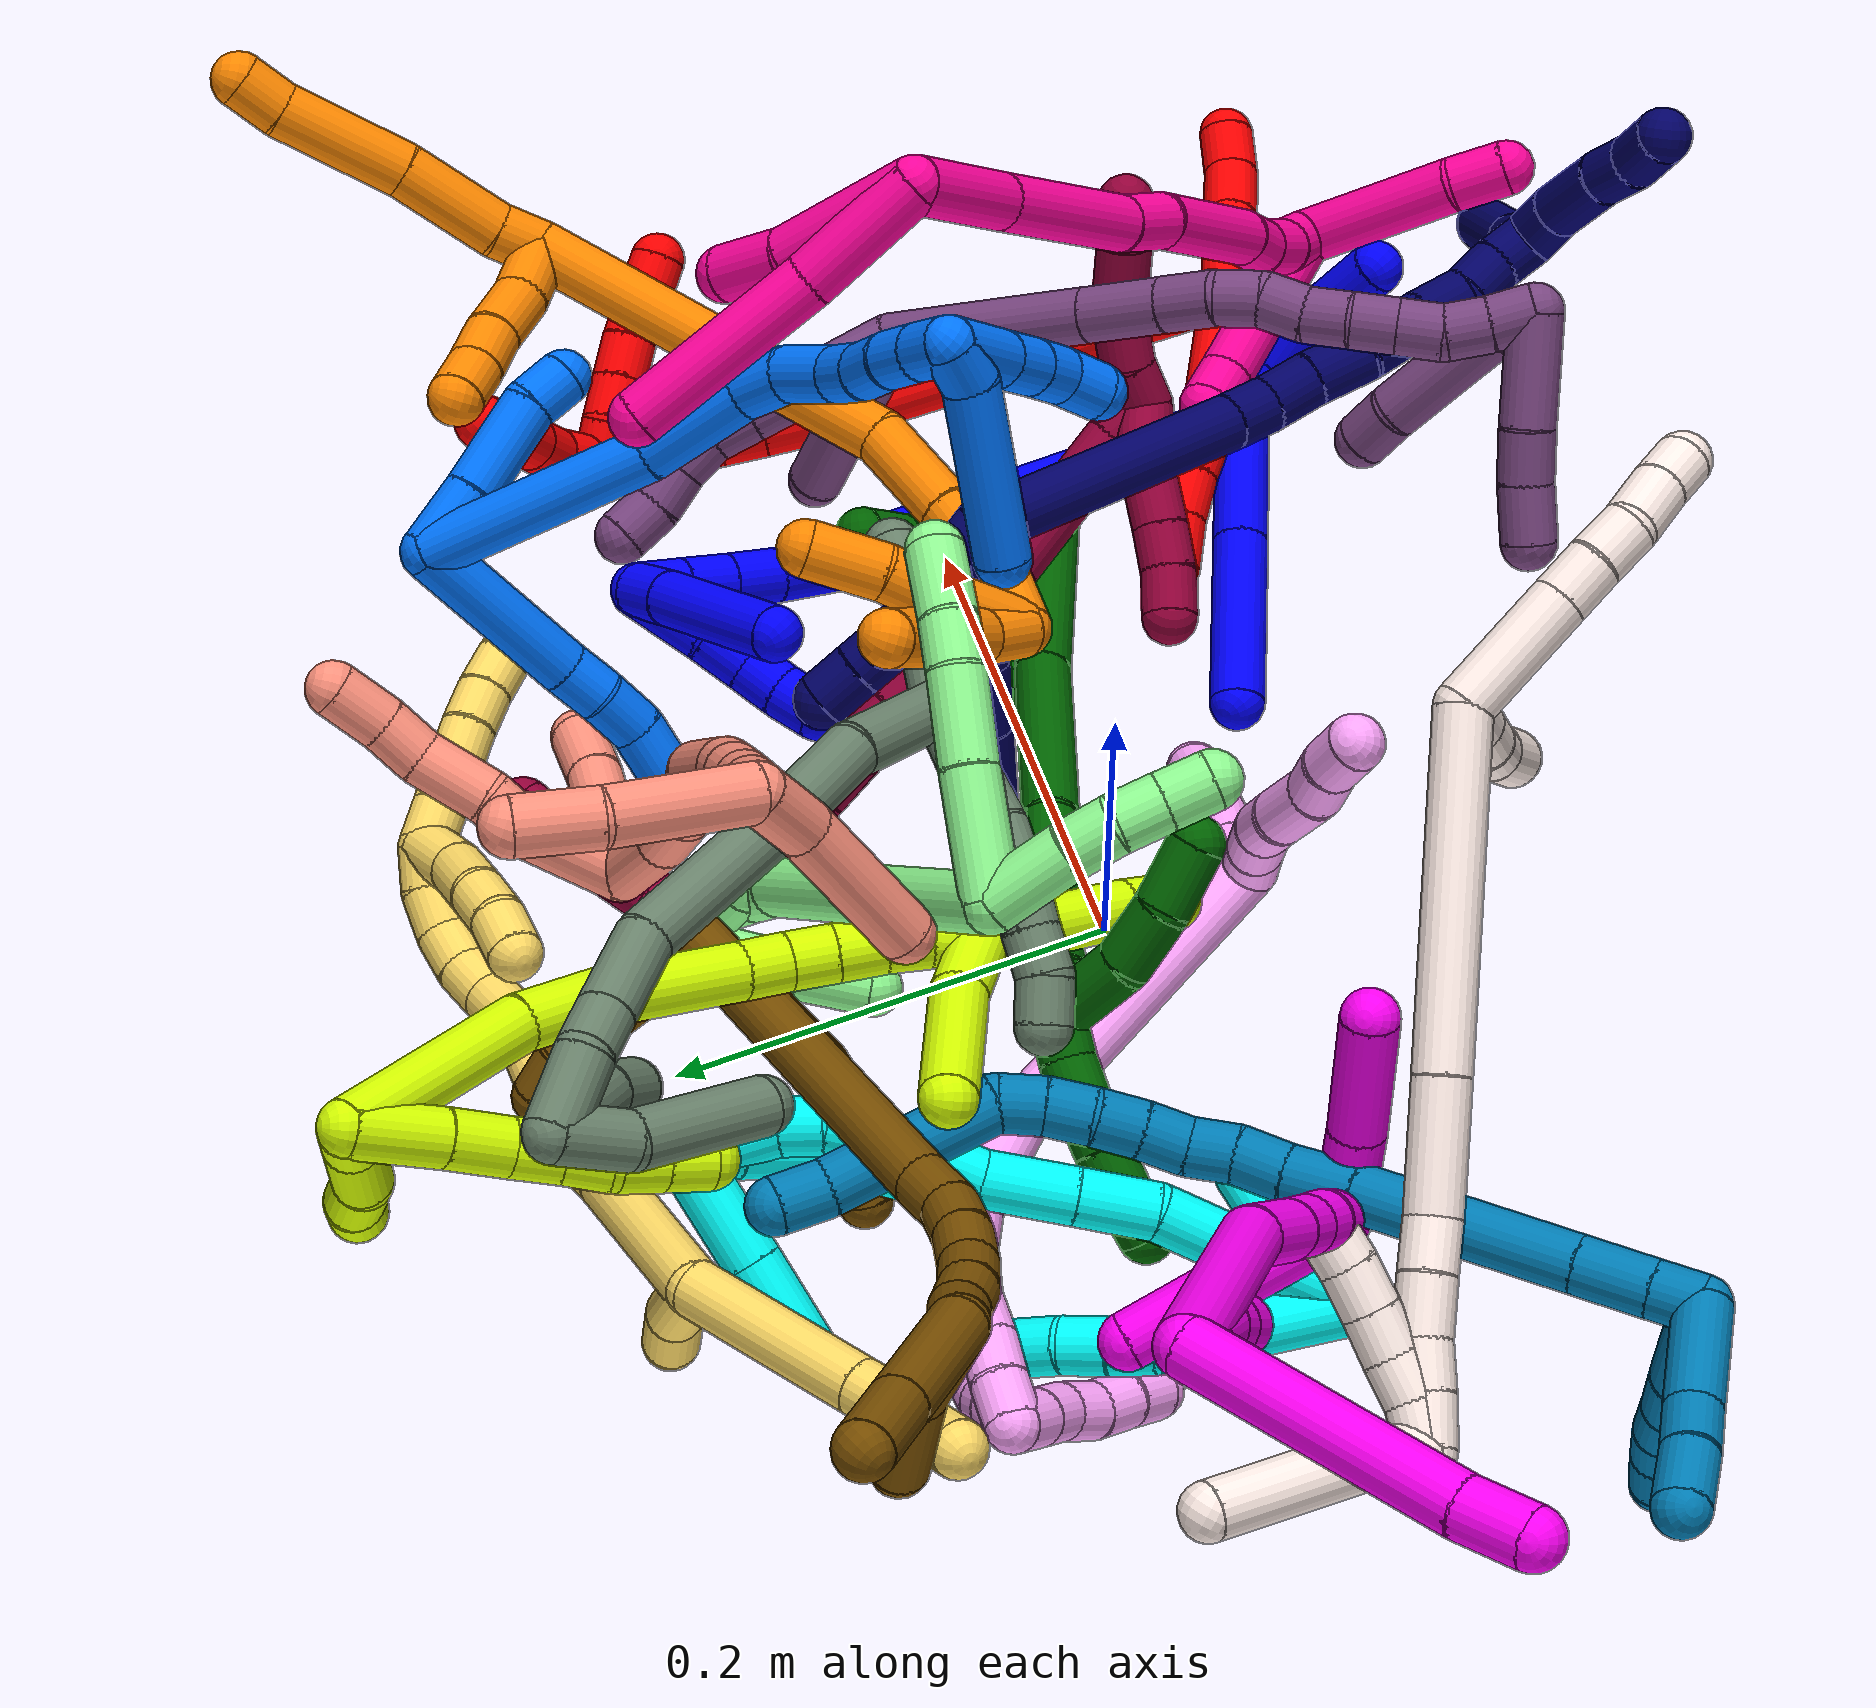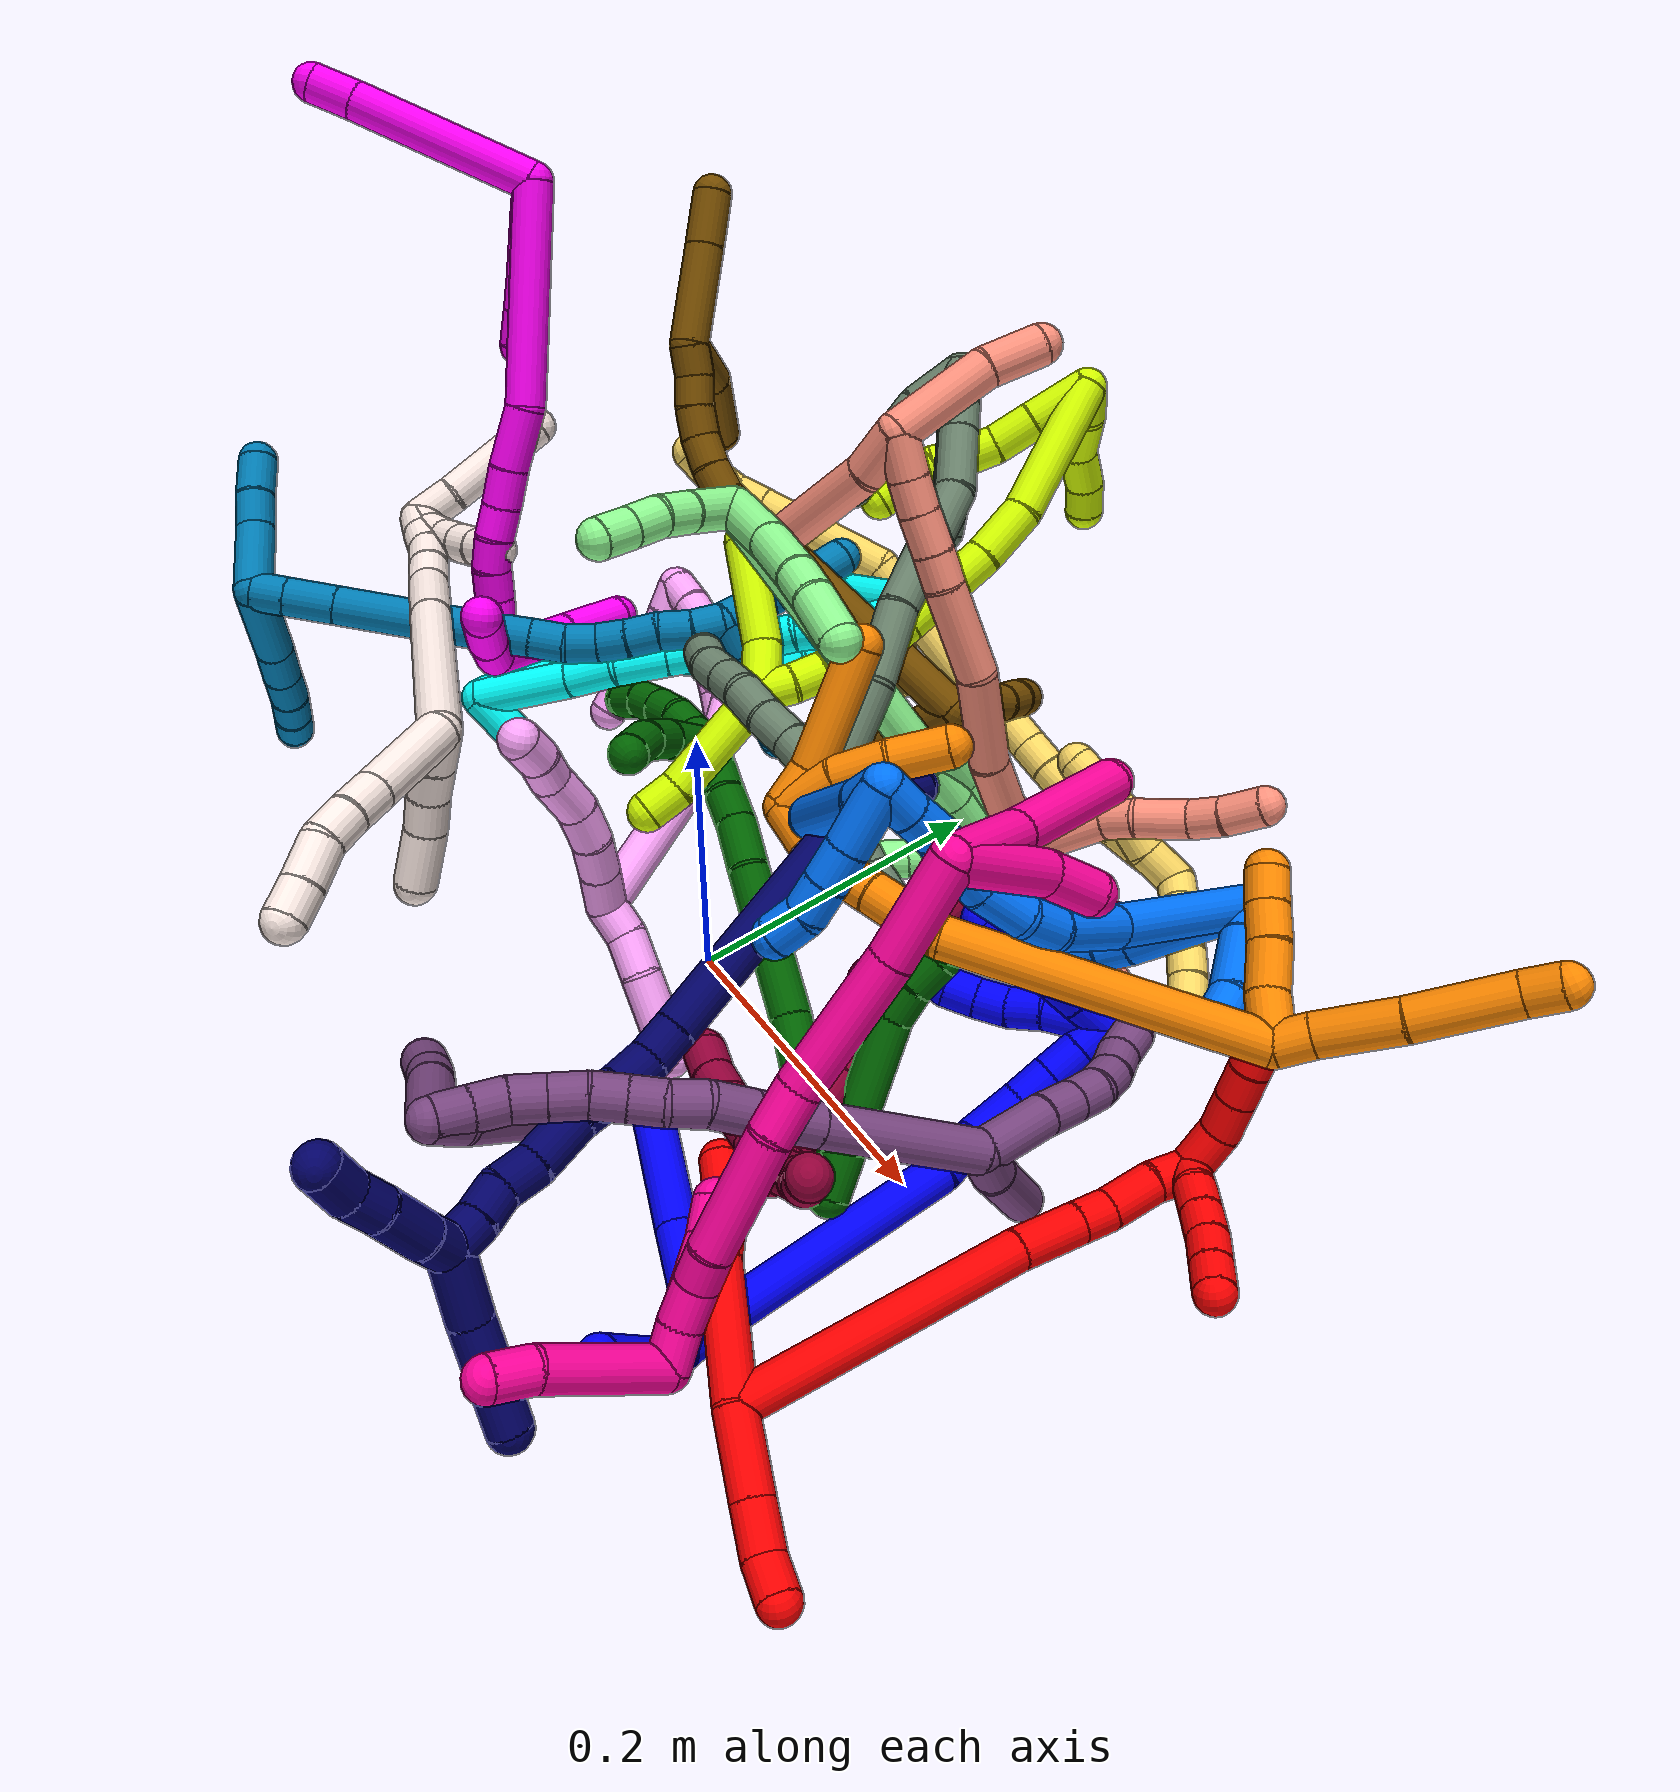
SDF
<sdf version="1.7">
 <world name="default">
  <plugin name="TubeGeneratorPlugin" filename="libtube_generator_plugin.so"/>
  <model name="photoneo_s_sensor">
   <static>1</static>
   <pose>0 0 2 1.57079 1.57079 3.14159</pose>
   <link name="link">
    <inertial><mass>0.1</mass></inertial>
    <sensor name="sensor" type="depth">
     <update_rate>30</update_rate>
     <camera>
      <horizontal_fov>1.22</horizontal_fov>
      <image><width>1920</width><height>1200</height><format>B8G8R8</format></image>
      <clip><near>0.1</near><far>4</far></clip>
      <depth_camera><output>points</output></depth_camera>
     </camera>
     <plugin name="camera_plugin" filename="libgazebo_ros_depth_camera.so">
      <baseline>0.2</baseline>
      <alwaysOn>1</alwaysOn>
      <updateRate>0.0</updateRate>
      <cameraName>camera_ir</cameraName>
      <imageTopicName>/camera/color/image_raw</imageTopicName>
      <cameraInfoTopicName>/camera/color/camera_info</cameraInfoTopicName>
      <depthImageTopicName>/camera/depth/image_raw</depthImageTopicName>
      <depthImageCameraInfoTopicName>/camera/depth/camera_info</depthImageCameraInfoTopicName>
      <pointCloudTopicName>/camera/depth/points</pointCloudTopicName>
      <frameName>fr_optical</frameName>
      <pointCloudCutoff>0.1</pointCloudCutoff>
      <pointCloudCutoffMax>2.0</pointCloudCutoffMax>
      <distortionK1>0</distortionK1>
      <distortionK2>0</distortionK2>
      <distortionK3>0</distortionK3>
      <distortionT1>0</distortionT1>
      <distortionT2>0</distortionT2>
      <CxPrime>0</CxPrime>
      <Cx>0</Cx>
      <Cy>0</Cy>
      <focalLength>0</focalLength>
      <hackBaseline>0</hackBaseline>
     </plugin>
    </sensor>
   </link>
  </model>
  <gravity>0 0 -9.8</gravity>
  <magnetic_field>6e-06 2.3e-05 -4.2e-05</magnetic_field>
  <atmosphere type="adiabatic"/>
  <physics name="default_physics" default="0" type="ode">
   <max_step_size>0.003</max_step_size>
   <real_time_factor>1</real_time_factor>
   <real_time_update_rate>1000</real_time_update_rate>
   <max_contacts>10000</max_contacts>
   <ode>
    <solver>
     <type>quick</type>
     <iters>100</iters>
     <sor>1.3</sor>
     <use_dynamic_moi_rescaling>0</use_dynamic_moi_rescaling>
    </solver>
    <constraints>
     <contact_max_correcting_vel>0</contact_max_correcting_vel>
     <contact_surface_layer>0.001</contact_surface_layer>
     <cfm>0</cfm>
     <erp>0.2</erp>
    </constraints>
   </ode>
  </physics>
  <scene><ambient>0.4 0.4 0.4 1</ambient><background>0.7 0.7 0.7 1</background><shadows>0</shadows></scene>
  <audio><device>default</device></audio>
  <spherical_coordinates>
   <surface_model>EARTH_WGS84</surface_model>
   <latitude_deg>0</latitude_deg>
   <longitude_deg>0</longitude_deg>
   <elevation>0</elevation>
   <heading_deg>0</heading_deg>
  </spherical_coordinates>
  <model name="bin">
   <static>1</static>
   <link name="bottom">
    <collision name="collision-bottom">
     <pose>0 0 -0.01 0 -0 0</pose>
     <geometry><box><size>0.8 0.6 0.02</size></box></geometry>
     <surface>
      <friction><ode><mu>100</mu><mu2>100</mu2></ode></friction>
      <contact><collide_bitmask>65535</collide_bitmask></contact>
     </surface>
    </collision>
   </link>
   <link name="west_wall">
    <collision name="collision-west_wall">
     <pose>-0.41 0 0.1 0 -0 0</pose>
     <geometry><box><size>0.02 0.6 0.2</size></box></geometry>
     <surface>
      <friction><ode><mu>100</mu><mu2>100</mu2></ode></friction>
      <contact><collide_bitmask>65535</collide_bitmask></contact>
     </surface>
    </collision>
   </link>
   <link name="east_wall">
    <collision name="collision-east_wall">
     <pose>0.41 0 0.1 0 -0 0</pose>
     <geometry><box><size>0.02 0.6 0.2</size></box></geometry>
     <surface>
      <friction><ode><mu>100</mu><mu2>100</mu2></ode></friction>
      <contact><collide_bitmask>65535</collide_bitmask></contact>
     </surface>
    </collision>
   </link>
   <link name="south_wall">
    <collision name="collision-south_wall">
     <pose>0 -0.31 0.1 0 -0 0</pose>
     <geometry><box><size>0.8 0.02 0.2</size></box></geometry>
     <surface>
      <friction><ode><mu>100</mu><mu2>100</mu2></ode></friction>
      <contact><collide_bitmask>65535</collide_bitmask></contact>
     </surface>
    </collision>
   </link>
   <link name="north_wall">
    <collision name="collision-north_wall">
     <pose>0 0.31 0.1 0 -0 0</pose>
     <geometry><box><size>0.8 0.02 0.2</size></box></geometry>
     <surface>
      <friction><ode><mu>100</mu><mu2>100</mu2></ode></friction>
      <contact><collide_bitmask>65535</collide_bitmask></contact>
     </surface>
    </collision>
   </link>
  </model>
  <model name="1">
   <static>0</static>
   <link name="1">
    <collision name="collision-cylinder-e_1_2_8">
     <pose>0.010722 -0.016586 -0.025929 2.57252 0.335211 1.04891</pose>
     <geometry><cylinder><radius>0.0125</radius><length>0.065188</length></cylinder></geometry>
     <surface>
      <friction><ode><mu>1.16</mu><mu2>1.16</mu2><slip1>0</slip1><slip2>0</slip2></ode></friction>
      <contact><ode><kp>1e+06</kp><kd>1</kd><max_vel>0</max_vel><min_depth>0.001</min_depth></ode></contact>
     </surface>
    </collision>
    <visual name="visual-cylinder-e_1_2_8">
     <pose>0.010722 -0.016586 -0.025929 2.57252 0.335211 1.04891</pose>
     <geometry><cylinder><radius>0.0125</radius><length>0.065188</length></cylinder></geometry>
     <material><ambient>0 0 1 1</ambient></material>
    </visual>
    <collision name="collision-cylinder-e_2_8_6">
     <pose>0.03364 -0.054523 -0.086407 2.58805 0.291712 0.954527</pose>
     <geometry><cylinder><radius>0.0125</radius><length>0.084812</length></cylinder></geometry>
     <surface>
      <friction><ode><mu>1.16</mu><mu2>1.16</mu2><slip1>0</slip1><slip2>0</slip2></ode></friction>
      <contact><ode><kp>1e+06</kp><kd>1</kd><max_vel>0</max_vel><min_depth>0.001</min_depth></ode></contact>
     </surface>
    </collision>
    <visual name="visual-cylinder-e_2_8_6">
     <pose>0.03364 -0.054523 -0.086407 2.58805 0.291712 0.954527</pose>
     <geometry><cylinder><radius>0.0125</radius><length>0.084812</length></cylinder></geometry>
     <material><ambient>0 0 1 1</ambient></material>
    </visual>
    <collision name="collision-cylinder-e_1_2_9">
     <pose>-0.012443 -0.002572 0.007745 0.320675 -0.990285 -0.174226</pose>
     <geometry><cylinder><radius>0.0125</radius><length>0.029761</length></cylinder></geometry>
     <surface>
      <friction><ode><mu>1.16</mu><mu2>1.16</mu2><slip1>0</slip1><slip2>0</slip2></ode></friction>
      <contact><ode><kp>1e+06</kp><kd>1</kd><max_vel>0</max_vel><min_depth>0.001</min_depth></ode></contact>
     </surface>
    </collision>
    <visual name="visual-cylinder-e_1_2_9">
     <pose>-0.012443 -0.002572 0.007745 0.320675 -0.990285 -0.174226</pose>
     <geometry><cylinder><radius>0.0125</radius><length>0.029761</length></cylinder></geometry>
     <material><ambient>0 0 1 1</ambient></material>
    </visual>
    <collision name="collision-cylinder-e_2_9_10">
     <pose>-0.03512 -0.008016 0.020112 0.55586 -1.08221 -0.339607</pose>
     <geometry><cylinder><radius>0.0125</radius><length>0.023182</length></cylinder></geometry>
     <surface>
      <friction><ode><mu>1.16</mu><mu2>1.16</mu2><slip1>0</slip1><slip2>0</slip2></ode></friction>
      <contact><ode><kp>1e+06</kp><kd>1</kd><max_vel>0</max_vel><min_depth>0.001</min_depth></ode></contact>
     </surface>
    </collision>
    <visual name="visual-cylinder-e_2_9_10">
     <pose>-0.03512 -0.008016 0.020112 0.55586 -1.08221 -0.339607</pose>
     <geometry><cylinder><radius>0.0125</radius><length>0.023182</length></cylinder></geometry>
     <material><ambient>0 0 1 1</ambient></material>
    </visual>
    <collision name="collision-cylinder-e_3_10_5">
     <pose>-0.065534 -0.021956 0.029619 1.15513 -1.03063 -0.707164</pose>
     <geometry><cylinder><radius>0.0125</radius><length>0.047057</length></cylinder></geometry>
     <surface>
      <friction><ode><mu>1.16</mu><mu2>1.16</mu2><slip1>0</slip1><slip2>0</slip2></ode></friction>
      <contact><ode><kp>1e+06</kp><kd>1</kd><max_vel>0</max_vel><min_depth>0.001</min_depth></ode></contact>
     </surface>
    </collision>
    <visual name="visual-cylinder-e_3_10_5">
     <pose>-0.065534 -0.021956 0.029619 1.15513 -1.03063 -0.707164</pose>
     <geometry><cylinder><radius>0.0125</radius><length>0.047057</length></cylinder></geometry>
     <material><ambient>0 0 1 1</ambient></material>
    </visual>
    <collision name="collision-cylinder-e_1_2_11">
     <pose>0.021866 0.049439 -0.064659 -2.4888 0.262451 -0.743549</pose>
     <geometry><cylinder><radius>0.0125</radius><length>0.16856</length></cylinder></geometry>
     <surface>
      <friction><ode><mu>1.16</mu><mu2>1.16</mu2><slip1>0</slip1><slip2>0</slip2></ode></friction>
      <contact><ode><kp>1e+06</kp><kd>1</kd><max_vel>0</max_vel><min_depth>0.001</min_depth></ode></contact>
     </surface>
    </collision>
    <visual name="visual-cylinder-e_1_2_11">
     <pose>0.021866 0.049439 -0.064659 -2.4888 0.262451 -0.743549</pose>
     <geometry><cylinder><radius>0.0125</radius><length>0.16856</length></cylinder></geometry>
     <material><ambient>0 0 1 1</ambient></material>
    </visual>
    <collision name="collision-cylinder-e_2_11_12">
     <pose>0.046587 0.10518 -0.142219 -2.68725 0.196236 -0.80514</pose>
     <geometry><cylinder><radius>0.0125</radius><length>0.029277</length></cylinder></geometry>
     <surface>
      <friction><ode><mu>1.16</mu><mu2>1.16</mu2><slip1>0</slip1><slip2>0</slip2></ode></friction>
      <contact><ode><kp>1e+06</kp><kd>1</kd><max_vel>0</max_vel><min_depth>0.001</min_depth></ode></contact>
     </surface>
    </collision>
    <visual name="visual-cylinder-e_2_11_12">
     <pose>0.046587 0.10518 -0.142219 -2.68725 0.196236 -0.80514</pose>
     <geometry><cylinder><radius>0.0125</radius><length>0.029277</length></cylinder></geometry>
     <material><ambient>0 0 1 1</ambient></material>
    </visual>
    <collision name="collision-cylinder-e_3_12_13">
     <pose>0.049496 0.120989 -0.168907 -2.53785 0.003298 -0.010591</pose>
     <geometry><cylinder><radius>0.0125</radius><length>0.033496</length></cylinder></geometry>
     <surface>
      <friction><ode><mu>1.16</mu><mu2>1.16</mu2><slip1>0</slip1><slip2>0</slip2></ode></friction>
      <contact><ode><kp>1e+06</kp><kd>1</kd><max_vel>0</max_vel><min_depth>0.001</min_depth></ode></contact>
     </surface>
    </collision>
    <visual name="visual-cylinder-e_3_12_13">
     <pose>0.049496 0.120989 -0.168907 -2.53785 0.003298 -0.010591</pose>
     <geometry><cylinder><radius>0.0125</radius><length>0.033496</length></cylinder></geometry>
     <material><ambient>0 0 1 1</ambient></material>
    </visual>
    <collision name="collision-cylinder-e_4_13_14">
     <pose>0.048449 0.137101 -0.192585 -2.55291 -0.092456 0.302868</pose>
     <geometry><cylinder><radius>0.0125</radius><length>0.023888</length></cylinder></geometry>
     <surface>
      <friction><ode><mu>1.16</mu><mu2>1.16</mu2><slip1>0</slip1><slip2>0</slip2></ode></friction>
      <contact><ode><kp>1e+06</kp><kd>1</kd><max_vel>0</max_vel><min_depth>0.001</min_depth></ode></contact>
     </surface>
    </collision>
    <visual name="visual-cylinder-e_4_13_14">
     <pose>0.048449 0.137101 -0.192585 -2.55291 -0.092456 0.302868</pose>
     <geometry><cylinder><radius>0.0125</radius><length>0.023888</length></cylinder></geometry>
     <material><ambient>0 0 1 1</ambient></material>
    </visual>
    <collision name="collision-cylinder-e_5_14_15">
     <pose>0.046068 0.150119 -0.211874 -2.54265 -0.111864 0.358784</pose>
     <geometry><cylinder><radius>0.0125</radius><length>0.022899</length></cylinder></geometry>
     <surface>
      <friction><ode><mu>1.16</mu><mu2>1.16</mu2><slip1>0</slip1><slip2>0</slip2></ode></friction>
      <contact><ode><kp>1e+06</kp><kd>1</kd><max_vel>0</max_vel><min_depth>0.001</min_depth></ode></contact>
     </surface>
    </collision>
    <visual name="visual-cylinder-e_5_14_15">
     <pose>0.046068 0.150119 -0.211874 -2.54265 -0.111864 0.358784</pose>
     <geometry><cylinder><radius>0.0125</radius><length>0.022899</length></cylinder></geometry>
     <material><ambient>0 0 1 1</ambient></material>
    </visual>
    <collision name="collision-cylinder-e_6_15_1">
     <pose>0.043495 0.16254 -0.230322 -2.55567 -0.118679 0.388927</pose>
     <geometry><cylinder><radius>0.0125</radius><length>0.02188</length></cylinder></geometry>
     <surface>
      <friction><ode><mu>1.16</mu><mu2>1.16</mu2><slip1>0</slip1><slip2>0</slip2></ode></friction>
      <contact><ode><kp>1e+06</kp><kd>1</kd><max_vel>0</max_vel><min_depth>0.001</min_depth></ode></contact>
     </surface>
    </collision>
    <visual name="visual-cylinder-e_6_15_1">
     <pose>0.043495 0.16254 -0.230322 -2.55567 -0.118679 0.388927</pose>
     <geometry><cylinder><radius>0.0125</radius><length>0.02188</length></cylinder></geometry>
     <material><ambient>0 0 1 1</ambient></material>
    </visual>
    <collision name="collision-cylinder-e_1_1_16">
     <pose>0.036513 0.158783 -0.242602 1.89016 -0.505043 -0.685969</pose>
     <geometry><cylinder><radius>0.0125</radius><length>0.023503</length></cylinder></geometry>
     <surface>
      <friction><ode><mu>1.16</mu><mu2>1.16</mu2><slip1>0</slip1><slip2>0</slip2></ode></friction>
      <contact><ode><kp>1e+06</kp><kd>1</kd><max_vel>0</max_vel><min_depth>0.001</min_depth></ode></contact>
     </surface>
    </collision>
    <visual name="visual-cylinder-e_1_1_16">
     <pose>0.036513 0.158783 -0.242602 1.89016 -0.505043 -0.685969</pose>
     <geometry><cylinder><radius>0.0125</radius><length>0.023503</length></cylinder></geometry>
     <material><ambient>0 0 1 1</ambient></material>
    </visual>
    <collision name="collision-cylinder-e_2_16_4">
     <pose>0.014012 0.116498 -0.256905 1.89899 -0.455183 -0.625799</pose>
     <geometry><cylinder><radius>0.0125</radius><length>0.076497</length></cylinder></geometry>
     <surface>
      <friction><ode><mu>1.16</mu><mu2>1.16</mu2><slip1>0</slip1><slip2>0</slip2></ode></friction>
      <contact><ode><kp>1e+06</kp><kd>1</kd><max_vel>0</max_vel><min_depth>0.001</min_depth></ode></contact>
     </surface>
    </collision>
    <visual name="visual-cylinder-e_2_16_4">
     <pose>0.014012 0.116498 -0.256905 1.89899 -0.455183 -0.625799</pose>
     <geometry><cylinder><radius>0.0125</radius><length>0.076497</length></cylinder></geometry>
     <material><ambient>0 0 1 1</ambient></material>
    </visual>
    <collision name="collision-cylinder-e_1_1_17">
     <pose>0.044695 0.149729 -0.239469 1.57589 0.131831 0.132503</pose>
     <geometry><cylinder><radius>0.0125</radius><length>0.037966</length></cylinder></geometry>
     <surface>
      <friction><ode><mu>1.16</mu><mu2>1.16</mu2><slip1>0</slip1><slip2>0</slip2></ode></friction>
      <contact><ode><kp>1e+06</kp><kd>1</kd><max_vel>0</max_vel><min_depth>0.001</min_depth></ode></contact>
     </surface>
    </collision>
    <visual name="visual-cylinder-e_1_1_17">
     <pose>0.044695 0.149729 -0.239469 1.57589 0.131831 0.132503</pose>
     <geometry><cylinder><radius>0.0125</radius><length>0.037966</length></cylinder></geometry>
     <material><ambient>0 0 1 1</ambient></material>
    </visual>
    <collision name="collision-cylinder-e_2_17_18">
     <pose>0.050526 0.1205 -0.238359 1.45551 0.308162 0.274983</pose>
     <geometry><cylinder><radius>0.0125</radius><length>0.021998</length></cylinder></geometry>
     <surface>
      <friction><ode><mu>1.16</mu><mu2>1.16</mu2><slip1>0</slip1><slip2>0</slip2></ode></friction>
      <contact><ode><kp>1e+06</kp><kd>1</kd><max_vel>0</max_vel><min_depth>0.001</min_depth></ode></contact>
     </surface>
    </collision>
    <visual name="visual-cylinder-e_2_17_18">
     <pose>0.050526 0.1205 -0.238359 1.45551 0.308162 0.274983</pose>
     <geometry><cylinder><radius>0.0125</radius><length>0.021998</length></cylinder></geometry>
     <material><ambient>0 0 1 1</ambient></material>
    </visual>
    <collision name="collision-cylinder-e_3_18_19">
     <pose>0.055365 0.100202 -0.237657 1.62169 0.150671 0.158508</pose>
     <geometry><cylinder><radius>0.0125</radius><length>0.020026</length></cylinder></geometry>
     <surface>
      <friction><ode><mu>1.16</mu><mu2>1.16</mu2><slip1>0</slip1><slip2>0</slip2></ode></friction>
      <contact><ode><kp>1e+06</kp><kd>1</kd><max_vel>0</max_vel><min_depth>0.001</min_depth></ode></contact>
     </surface>
    </collision>
    <visual name="visual-cylinder-e_3_18_19">
     <pose>0.055365 0.100202 -0.237657 1.62169 0.150671 0.158508</pose>
     <geometry><cylinder><radius>0.0125</radius><length>0.020026</length></cylinder></geometry>
     <material><ambient>0 0 1 1</ambient></material>
    </visual>
    <collision name="collision-cylinder-e_4_19_3">
     <pose>0.056777 0.080344 -0.238984 1.65317 -0.009083 -0.009864</pose>
     <geometry><cylinder><radius>0.0125</radius><length>0.02001</length></cylinder></geometry>
     <surface>
      <friction><ode><mu>1.16</mu><mu2>1.16</mu2><slip1>0</slip1><slip2>0</slip2></ode></friction>
      <contact><ode><kp>1e+06</kp><kd>1</kd><max_vel>0</max_vel><min_depth>0.001</min_depth></ode></contact>
     </surface>
    </collision>
    <visual name="visual-cylinder-e_4_19_3">
     <pose>0.056777 0.080344 -0.238984 1.65317 -0.009083 -0.009864</pose>
     <geometry><cylinder><radius>0.0125</radius><length>0.02001</length></cylinder></geometry>
     <material><ambient>0 0 1 1</ambient></material>
    </visual>
    <collision name="collision-sphere-3">
     <pose>0.056686 0.070374 -0.239807 0 -0 0</pose>
     <geometry><sphere><radius>0.0125</radius></sphere></geometry>
     <surface>
      <friction><ode><mu>1.16</mu><mu2>1.16</mu2><slip1>0</slip1><slip2>0</slip2></ode></friction>
      <contact><ode><kp>1e+06</kp><kd>1</kd><max_vel>0</max_vel><min_depth>0.001</min_depth></ode></contact>
     </surface>
    </collision>
    <visual name="visual-sphere-3">
     <pose>0.056686 0.070374 -0.239807 0 -0 0</pose>
     <geometry><sphere><radius>0.0125</radius></sphere></geometry>
     <material><ambient>0 0 1 1</ambient></material>
    </visual>
    <collision name="collision-sphere-19">
     <pose>0.056868 0.090315 -0.238161 0 -0 0</pose>
     <geometry><sphere><radius>0.0125</radius></sphere></geometry>
     <surface>
      <friction><ode><mu>1.16</mu><mu2>1.16</mu2><slip1>0</slip1><slip2>0</slip2></ode></friction>
      <contact><ode><kp>1e+06</kp><kd>1</kd><max_vel>0</max_vel><min_depth>0.001</min_depth></ode></contact>
     </surface>
    </collision>
    <visual name="visual-sphere-19">
     <pose>0.056868 0.090315 -0.238161 0 -0 0</pose>
     <geometry><sphere><radius>0.0125</radius></sphere></geometry>
     <material><ambient>0 0 1 1</ambient></material>
    </visual>
    <collision name="collision-sphere-5">
     <pose>-0.085713 -0.033026 0.034505 0 -0 0</pose>
     <geometry><sphere><radius>0.0125</radius></sphere></geometry>
     <surface>
      <friction><ode><mu>1.16</mu><mu2>1.16</mu2><slip1>0</slip1><slip2>0</slip2></ode></friction>
      <contact><ode><kp>1e+06</kp><kd>1</kd><max_vel>0</max_vel><min_depth>0.001</min_depth></ode></contact>
     </surface>
    </collision>
    <visual name="visual-sphere-5">
     <pose>-0.085713 -0.033026 0.034505 0 -0 0</pose>
     <geometry><sphere><radius>0.0125</radius></sphere></geometry>
     <material><ambient>0 0 1 1</ambient></material>
    </visual>
    <collision name="collision-sphere-10">
     <pose>-0.045355 -0.010887 0.024733 0 -0 0</pose>
     <geometry><sphere><radius>0.0125</radius></sphere></geometry>
     <surface>
      <friction><ode><mu>1.16</mu><mu2>1.16</mu2><slip1>0</slip1><slip2>0</slip2></ode></friction>
      <contact><ode><kp>1e+06</kp><kd>1</kd><max_vel>0</max_vel><min_depth>0.001</min_depth></ode></contact>
     </surface>
    </collision>
    <visual name="visual-sphere-10">
     <pose>-0.045355 -0.010887 0.024733 0 -0 0</pose>
     <geometry><sphere><radius>0.0125</radius></sphere></geometry>
     <material><ambient>0 0 1 1</ambient></material>
    </visual>
    <collision name="collision-sphere-6">
     <pose>0.045836 -0.075874 -0.120957 0 -0 0</pose>
     <geometry><sphere><radius>0.0125</radius></sphere></geometry>
     <surface>
      <friction><ode><mu>1.16</mu><mu2>1.16</mu2><slip1>0</slip1><slip2>0</slip2></ode></friction>
      <contact><ode><kp>1e+06</kp><kd>1</kd><max_vel>0</max_vel><min_depth>0.001</min_depth></ode></contact>
     </surface>
    </collision>
    <visual name="visual-sphere-6">
     <pose>0.045836 -0.075874 -0.120957 0 -0 0</pose>
     <geometry><sphere><radius>0.0125</radius></sphere></geometry>
     <material><ambient>0 0 1 1</ambient></material>
    </visual>
    <collision name="collision-sphere-9">
     <pose>-0.024885 -0.005145 0.01549 0 -0 0</pose>
     <geometry><sphere><radius>0.0125</radius></sphere></geometry>
     <surface>
      <friction><ode><mu>1.16</mu><mu2>1.16</mu2><slip1>0</slip1><slip2>0</slip2></ode></friction>
      <contact><ode><kp>1e+06</kp><kd>1</kd><max_vel>0</max_vel><min_depth>0.001</min_depth></ode></contact>
     </surface>
    </collision>
    <visual name="visual-sphere-9">
     <pose>-0.024885 -0.005145 0.01549 0 -0 0</pose>
     <geometry><sphere><radius>0.0125</radius></sphere></geometry>
     <material><ambient>0 0 1 1</ambient></material>
    </visual>
    <collision name="collision-sphere-2">
     <geometry><sphere><radius>0.0125</radius></sphere></geometry>
     <surface>
      <friction><ode><mu>1.16</mu><mu2>1.16</mu2><slip1>0</slip1><slip2>0</slip2></ode></friction>
      <contact><ode><kp>1e+06</kp><kd>1</kd><max_vel>0</max_vel><min_depth>0.001</min_depth></ode></contact>
     </surface>
    </collision>
    <visual name="visual-sphere-2">
     <geometry><sphere><radius>0.0125</radius></sphere></geometry>
     <material><ambient>0 0 1 1</ambient></material>
    </visual>
    <collision name="collision-sphere-8">
     <pose>0.021445 -0.033171 -0.051858 0 -0 0</pose>
     <geometry><sphere><radius>0.0125</radius></sphere></geometry>
     <surface>
      <friction><ode><mu>1.16</mu><mu2>1.16</mu2><slip1>0</slip1><slip2>0</slip2></ode></friction>
      <contact><ode><kp>1e+06</kp><kd>1</kd><max_vel>0</max_vel><min_depth>0.001</min_depth></ode></contact>
     </surface>
    </collision>
    <visual name="visual-sphere-8">
     <pose>0.021445 -0.033171 -0.051858 0 -0 0</pose>
     <geometry><sphere><radius>0.0125</radius></sphere></geometry>
     <material><ambient>0 0 1 1</ambient></material>
    </visual>
    <collision name="collision-sphere-11">
     <pose>0.043733 0.098878 -0.129318 0 -0 0</pose>
     <geometry><sphere><radius>0.0125</radius></sphere></geometry>
     <surface>
      <friction><ode><mu>1.16</mu><mu2>1.16</mu2><slip1>0</slip1><slip2>0</slip2></ode></friction>
      <contact><ode><kp>1e+06</kp><kd>1</kd><max_vel>0</max_vel><min_depth>0.001</min_depth></ode></contact>
     </surface>
    </collision>
    <visual name="visual-sphere-11">
     <pose>0.043733 0.098878 -0.129318 0 -0 0</pose>
     <geometry><sphere><radius>0.0125</radius></sphere></geometry>
     <material><ambient>0 0 1 1</ambient></material>
    </visual>
    <collision name="collision-sphere-12">
     <pose>0.049441 0.111481 -0.15512 0 -0 0</pose>
     <geometry><sphere><radius>0.0125</radius></sphere></geometry>
     <surface>
      <friction><ode><mu>1.16</mu><mu2>1.16</mu2><slip1>0</slip1><slip2>0</slip2></ode></friction>
      <contact><ode><kp>1e+06</kp><kd>1</kd><max_vel>0</max_vel><min_depth>0.001</min_depth></ode></contact>
     </surface>
    </collision>
    <visual name="visual-sphere-12">
     <pose>0.049441 0.111481 -0.15512 0 -0 0</pose>
     <geometry><sphere><radius>0.0125</radius></sphere></geometry>
     <material><ambient>0 0 1 1</ambient></material>
    </visual>
    <collision name="collision-sphere-13">
     <pose>0.049552 0.130497 -0.182694 0 -0 0</pose>
     <geometry><sphere><radius>0.0125</radius></sphere></geometry>
     <surface>
      <friction><ode><mu>1.16</mu><mu2>1.16</mu2><slip1>0</slip1><slip2>0</slip2></ode></friction>
      <contact><ode><kp>1e+06</kp><kd>1</kd><max_vel>0</max_vel><min_depth>0.001</min_depth></ode></contact>
     </surface>
    </collision>
    <visual name="visual-sphere-13">
     <pose>0.049552 0.130497 -0.182694 0 -0 0</pose>
     <geometry><sphere><radius>0.0125</radius></sphere></geometry>
     <material><ambient>0 0 1 1</ambient></material>
    </visual>
    <collision name="collision-sphere-14">
     <pose>0.047346 0.143705 -0.202476 0 -0 0</pose>
     <geometry><sphere><radius>0.0125</radius></sphere></geometry>
     <surface>
      <friction><ode><mu>1.16</mu><mu2>1.16</mu2><slip1>0</slip1><slip2>0</slip2></ode></friction>
      <contact><ode><kp>1e+06</kp><kd>1</kd><max_vel>0</max_vel><min_depth>0.001</min_depth></ode></contact>
     </surface>
    </collision>
    <visual name="visual-sphere-14">
     <pose>0.047346 0.143705 -0.202476 0 -0 0</pose>
     <geometry><sphere><radius>0.0125</radius></sphere></geometry>
     <material><ambient>0 0 1 1</ambient></material>
    </visual>
    <collision name="collision-sphere-15">
     <pose>0.04479 0.156534 -0.221271 0 -0 0</pose>
     <geometry><sphere><radius>0.0125</radius></sphere></geometry>
     <surface>
      <friction><ode><mu>1.16</mu><mu2>1.16</mu2><slip1>0</slip1><slip2>0</slip2></ode></friction>
      <contact><ode><kp>1e+06</kp><kd>1</kd><max_vel>0</max_vel><min_depth>0.001</min_depth></ode></contact>
     </surface>
    </collision>
    <visual name="visual-sphere-15">
     <pose>0.04479 0.156534 -0.221271 0 -0 0</pose>
     <geometry><sphere><radius>0.0125</radius></sphere></geometry>
     <material><ambient>0 0 1 1</ambient></material>
    </visual>
    <collision name="collision-sphere-1">
     <pose>0.042199 0.168547 -0.239373 0 -0 0</pose>
     <geometry><sphere><radius>0.0125</radius></sphere></geometry>
     <surface>
      <friction><ode><mu>1.16</mu><mu2>1.16</mu2><slip1>0</slip1><slip2>0</slip2></ode></friction>
      <contact><ode><kp>1e+06</kp><kd>1</kd><max_vel>0</max_vel><min_depth>0.001</min_depth></ode></contact>
     </surface>
    </collision>
    <visual name="visual-sphere-1">
     <pose>0.042199 0.168547 -0.239373 0 -0 0</pose>
     <geometry><sphere><radius>0.0125</radius></sphere></geometry>
     <material><ambient>0 0 1 1</ambient></material>
    </visual>
    <collision name="collision-sphere-18">
     <pose>0.053862 0.110089 -0.237154 0 -0 0</pose>
     <geometry><sphere><radius>0.0125</radius></sphere></geometry>
     <surface>
      <friction><ode><mu>1.16</mu><mu2>1.16</mu2><slip1>0</slip1><slip2>0</slip2></ode></friction>
      <contact><ode><kp>1e+06</kp><kd>1</kd><max_vel>0</max_vel><min_depth>0.001</min_depth></ode></contact>
     </surface>
    </collision>
    <visual name="visual-sphere-18">
     <pose>0.053862 0.110089 -0.237154 0 -0 0</pose>
     <geometry><sphere><radius>0.0125</radius></sphere></geometry>
     <material><ambient>0 0 1 1</ambient></material>
    </visual>
    <collision name="collision-sphere-16">
     <pose>0.030827 0.149019 -0.245831 0 -0 0</pose>
     <geometry><sphere><radius>0.0125</radius></sphere></geometry>
     <surface>
      <friction><ode><mu>1.16</mu><mu2>1.16</mu2><slip1>0</slip1><slip2>0</slip2></ode></friction>
      <contact><ode><kp>1e+06</kp><kd>1</kd><max_vel>0</max_vel><min_depth>0.001</min_depth></ode></contact>
     </surface>
    </collision>
    <visual name="visual-sphere-16">
     <pose>0.030827 0.149019 -0.245831 0 -0 0</pose>
     <geometry><sphere><radius>0.0125</radius></sphere></geometry>
     <material><ambient>0 0 1 1</ambient></material>
    </visual>
    <collision name="collision-sphere-4">
     <pose>-0.002803 0.083978 -0.267978 0 -0 0</pose>
     <geometry><sphere><radius>0.0125</radius></sphere></geometry>
     <surface>
      <friction><ode><mu>1.16</mu><mu2>1.16</mu2><slip1>0</slip1><slip2>0</slip2></ode></friction>
      <contact><ode><kp>1e+06</kp><kd>1</kd><max_vel>0</max_vel><min_depth>0.001</min_depth></ode></contact>
     </surface>
    </collision>
    <visual name="visual-sphere-4">
     <pose>-0.002803 0.083978 -0.267978 0 -0 0</pose>
     <geometry><sphere><radius>0.0125</radius></sphere></geometry>
     <material><ambient>0 0 1 1</ambient></material>
    </visual>
    <collision name="collision-sphere-17">
     <pose>0.04719 0.130911 -0.239565 0 -0 0</pose>
     <geometry><sphere><radius>0.0125</radius></sphere></geometry>
     <surface>
      <friction><ode><mu>1.16</mu><mu2>1.16</mu2><slip1>0</slip1><slip2>0</slip2></ode></friction>
      <contact><ode><kp>1e+06</kp><kd>1</kd><max_vel>0</max_vel><min_depth>0.001</min_depth></ode></contact>
     </surface>
    </collision>
    <visual name="visual-sphere-17">
     <pose>0.04719 0.130911 -0.239565 0 -0 0</pose>
     <geometry><sphere><radius>0.0125</radius></sphere></geometry>
     <material><ambient>0 0 1 1</ambient></material>
    </visual>
    <inertial>
     <pose>0.021518 0.057769 -0.121828 0 -0 0</pose>
     <mass>0.75</mass>
     <inertia>
      <ixx>0.000161</ixx>
      <ixy>0</ixy>
      <ixz>0</ixz>
      <iyy>-0.000454</iyy>
      <iyz>0</iyz>
      <izz>-0.000279</izz>
     </inertia>
    </inertial>
   </link>
   <pose>0.215487 -0.150528 0.011969 -2.97944 1.19922 2.36898</pose>
  </model>
  <model name="2">
   <static>0</static>
   <link name="2">
    <collision name="collision-cylinder-e_1_2_8">
     <pose>-0.029377 0.017899 0.021505 -0.694149 -0.80977 0.307589</pose>
     <geometry><cylinder><radius>0.0125</radius><length>0.081139</length></cylinder></geometry>
     <surface>
      <friction><ode><mu>1.16</mu><mu2>1.16</mu2><slip1>0</slip1><slip2>0</slip2></ode></friction>
      <contact><ode><kp>1e+06</kp><kd>1</kd><max_vel>0</max_vel><min_depth>0.001</min_depth></ode></contact>
     </surface>
    </collision>
    <visual name="visual-cylinder-e_1_2_8">
     <pose>-0.029377 0.017899 0.021505 -0.694149 -0.80977 0.307589</pose>
     <geometry><cylinder><radius>0.0125</radius><length>0.081139</length></cylinder></geometry>
     <material><ambient>1 0 0 1</ambient></material>
    </visual>
    <collision name="collision-cylinder-e_2_8_9">
     <pose>-0.066845 0.042935 0.046916 -1.06994 -0.782596 0.479585</pose>
     <geometry><cylinder><radius>0.0125</radius><length>0.022947</length></cylinder></geometry>
     <surface>
      <friction><ode><mu>1.16</mu><mu2>1.16</mu2><slip1>0</slip1><slip2>0</slip2></ode></friction>
      <contact><ode><kp>1e+06</kp><kd>1</kd><max_vel>0</max_vel><min_depth>0.001</min_depth></ode></contact>
     </surface>
    </collision>
    <visual name="visual-cylinder-e_2_8_9">
     <pose>-0.066845 0.042935 0.046916 -1.06994 -0.782596 0.479585</pose>
     <geometry><cylinder><radius>0.0125</radius><length>0.022947</length></cylinder></geometry>
     <material><ambient>1 0 0 1</ambient></material>
    </visual>
    <collision name="collision-cylinder-e_3_9_10">
     <pose>-0.083572 0.056315 0.0541 -1.08743 -0.886079 0.55866</pose>
     <geometry><cylinder><radius>0.0125</radius><length>0.0223</length></cylinder></geometry>
     <surface>
      <friction><ode><mu>1.16</mu><mu2>1.16</mu2><slip1>0</slip1><slip2>0</slip2></ode></friction>
      <contact><ode><kp>1e+06</kp><kd>1</kd><max_vel>0</max_vel><min_depth>0.001</min_depth></ode></contact>
     </surface>
    </collision>
    <visual name="visual-cylinder-e_3_9_10">
     <pose>-0.083572 0.056315 0.0541 -1.08743 -0.886079 0.55866</pose>
     <geometry><cylinder><radius>0.0125</radius><length>0.0223</length></cylinder></geometry>
     <material><ambient>1 0 0 1</ambient></material>
    </visual>
    <collision name="collision-cylinder-e_4_10_6">
     <pose>-0.102104 0.067962 0.060886 -0.994893 -0.993731 0.57268</pose>
     <geometry><cylinder><radius>0.0125</radius><length>0.023615</length></cylinder></geometry>
     <surface>
      <friction><ode><mu>1.16</mu><mu2>1.16</mu2><slip1>0</slip1><slip2>0</slip2></ode></friction>
      <contact><ode><kp>1e+06</kp><kd>1</kd><max_vel>0</max_vel><min_depth>0.001</min_depth></ode></contact>
     </surface>
    </collision>
    <visual name="visual-cylinder-e_4_10_6">
     <pose>-0.102104 0.067962 0.060886 -0.994893 -0.993731 0.57268</pose>
     <geometry><cylinder><radius>0.0125</radius><length>0.023615</length></cylinder></geometry>
     <material><ambient>1 0 0 1</ambient></material>
    </visual>
    <collision name="collision-cylinder-e_1_2_11">
     <pose>0.016543 -0.008218 -0.015757 2.66085 0.74961 2.02719</pose>
     <geometry><cylinder><radius>0.0125</radius><length>0.048559</length></cylinder></geometry>
     <surface>
      <friction><ode><mu>1.16</mu><mu2>1.16</mu2><slip1>0</slip1><slip2>0</slip2></ode></friction>
      <contact><ode><kp>1e+06</kp><kd>1</kd><max_vel>0</max_vel><min_depth>0.001</min_depth></ode></contact>
     </surface>
    </collision>
    <visual name="visual-cylinder-e_1_2_11">
     <pose>0.016543 -0.008218 -0.015757 2.66085 0.74961 2.02719</pose>
     <geometry><cylinder><radius>0.0125</radius><length>0.048559</length></cylinder></geometry>
     <material><ambient>1 0 0 1</ambient></material>
    </visual>
    <collision name="collision-cylinder-e_2_11_12">
     <pose>0.043179 -0.021252 -0.040572 2.65297 0.777309 2.04787</pose>
     <geometry><cylinder><radius>0.0125</radius><length>0.028782</length></cylinder></geometry>
     <surface>
      <friction><ode><mu>1.16</mu><mu2>1.16</mu2><slip1>0</slip1><slip2>0</slip2></ode></friction>
      <contact><ode><kp>1e+06</kp><kd>1</kd><max_vel>0</max_vel><min_depth>0.001</min_depth></ode></contact>
     </surface>
    </collision>
    <visual name="visual-cylinder-e_2_11_12">
     <pose>0.043179 -0.021252 -0.040572 2.65297 0.777309 2.04787</pose>
     <geometry><cylinder><radius>0.0125</radius><length>0.028782</length></cylinder></geometry>
     <material><ambient>1 0 0 1</ambient></material>
    </visual>
    <collision name="collision-cylinder-e_3_12_5">
     <pose>0.062951 -0.028865 -0.054812 2.64662 1.02412 2.29666</pose>
     <geometry><cylinder><radius>0.0125</radius><length>0.022659</length></cylinder></geometry>
     <surface>
      <friction><ode><mu>1.16</mu><mu2>1.16</mu2><slip1>0</slip1><slip2>0</slip2></ode></friction>
      <contact><ode><kp>1e+06</kp><kd>1</kd><max_vel>0</max_vel><min_depth>0.001</min_depth></ode></contact>
     </surface>
    </collision>
    <visual name="visual-cylinder-e_3_12_5">
     <pose>0.062951 -0.028865 -0.054812 2.64662 1.02412 2.29666</pose>
     <geometry><cylinder><radius>0.0125</radius><length>0.022659</length></cylinder></geometry>
     <material><ambient>1 0 0 1</ambient></material>
    </visual>
    <collision name="collision-cylinder-e_1_2_13">
     <pose>0.003151 0.091722 0.00148 -1.55466 0.03434 -0.03379</pose>
     <geometry><cylinder><radius>0.0125</radius><length>0.183575</length></cylinder></geometry>
     <surface>
      <friction><ode><mu>1.16</mu><mu2>1.16</mu2><slip1>0</slip1><slip2>0</slip2></ode></friction>
      <contact><ode><kp>1e+06</kp><kd>1</kd><max_vel>0</max_vel><min_depth>0.001</min_depth></ode></contact>
     </surface>
    </collision>
    <visual name="visual-cylinder-e_1_2_13">
     <pose>0.003151 0.091722 0.00148 -1.55466 0.03434 -0.03379</pose>
     <geometry><cylinder><radius>0.0125</radius><length>0.183575</length></cylinder></geometry>
     <material><ambient>1 0 0 1</ambient></material>
    </visual>
    <collision name="collision-cylinder-e_2_13_14">
     <pose>0.008409 0.203397 0.002443 -1.59674 0.10516 -0.107918</pose>
     <geometry><cylinder><radius>0.0125</radius><length>0.040142</length></cylinder></geometry>
     <surface>
      <friction><ode><mu>1.16</mu><mu2>1.16</mu2><slip1>0</slip1><slip2>0</slip2></ode></friction>
      <contact><ode><kp>1e+06</kp><kd>1</kd><max_vel>0</max_vel><min_depth>0.001</min_depth></ode></contact>
     </surface>
    </collision>
    <visual name="visual-cylinder-e_2_13_14">
     <pose>0.008409 0.203397 0.002443 -1.59674 0.10516 -0.107918</pose>
     <geometry><cylinder><radius>0.0125</radius><length>0.040142</length></cylinder></geometry>
     <material><ambient>1 0 0 1</ambient></material>
    </visual>
    <collision name="collision-cylinder-e_3_14_15">
     <pose>0.011745 0.233573 0.001697 -1.59307 0.119613 -0.1223</pose>
     <geometry><cylinder><radius>0.0125</radius><length>0.020599</length></cylinder></geometry>
     <surface>
      <friction><ode><mu>1.16</mu><mu2>1.16</mu2><slip1>0</slip1><slip2>0</slip2></ode></friction>
      <contact><ode><kp>1e+06</kp><kd>1</kd><max_vel>0</max_vel><min_depth>0.001</min_depth></ode></contact>
     </surface>
    </collision>
    <visual name="visual-cylinder-e_3_14_15">
     <pose>0.011745 0.233573 0.001697 -1.59307 0.119613 -0.1223</pose>
     <geometry><cylinder><radius>0.0125</radius><length>0.020599</length></cylinder></geometry>
     <material><ambient>1 0 0 1</ambient></material>
    </visual>
    <collision name="collision-cylinder-e_4_15_16">
     <pose>0.014553 0.259528 0.003325 -1.45339 0.099307 -0.088297</pose>
     <geometry><cylinder><radius>0.0125</radius><length>0.031839</length></cylinder></geometry>
     <surface>
      <friction><ode><mu>1.16</mu><mu2>1.16</mu2><slip1>0</slip1><slip2>0</slip2></ode></friction>
      <contact><ode><kp>1e+06</kp><kd>1</kd><max_vel>0</max_vel><min_depth>0.001</min_depth></ode></contact>
     </surface>
    </collision>
    <visual name="visual-cylinder-e_4_15_16">
     <pose>0.014553 0.259528 0.003325 -1.45339 0.099307 -0.088297</pose>
     <geometry><cylinder><radius>0.0125</radius><length>0.031839</length></cylinder></geometry>
     <material><ambient>1 0 0 1</ambient></material>
    </visual>
    <collision name="collision-cylinder-e_5_16_1">
     <pose>0.01809 0.287 0.004484 -1.63013 0.165036 -0.17508</pose>
     <geometry><cylinder><radius>0.0125</radius><length>0.023845</length></cylinder></geometry>
     <surface>
      <friction><ode><mu>1.16</mu><mu2>1.16</mu2><slip1>0</slip1><slip2>0</slip2></ode></friction>
      <contact><ode><kp>1e+06</kp><kd>1</kd><max_vel>0</max_vel><min_depth>0.001</min_depth></ode></contact>
     </surface>
    </collision>
    <visual name="visual-cylinder-e_5_16_1">
     <pose>0.01809 0.287 0.004484 -1.63013 0.165036 -0.17508</pose>
     <geometry><cylinder><radius>0.0125</radius><length>0.023845</length></cylinder></geometry>
     <material><ambient>1 0 0 1</ambient></material>
    </visual>
    <collision name="collision-cylinder-e_1_1_17">
     <pose>0.025066 0.30786 0.014358 -0.711801 0.34499 -0.12935</pose>
     <geometry><cylinder><radius>0.0125</radius><length>0.029673</length></cylinder></geometry>
     <surface>
      <friction><ode><mu>1.16</mu><mu2>1.16</mu2><slip1>0</slip1><slip2>0</slip2></ode></friction>
      <contact><ode><kp>1e+06</kp><kd>1</kd><max_vel>0</max_vel><min_depth>0.001</min_depth></ode></contact>
     </surface>
    </collision>
    <visual name="visual-cylinder-e_1_1_17">
     <pose>0.025066 0.30786 0.014358 -0.711801 0.34499 -0.12935</pose>
     <geometry><cylinder><radius>0.0125</radius><length>0.029673</length></cylinder></geometry>
     <material><ambient>1 0 0 1</ambient></material>
    </visual>
    <collision name="collision-cylinder-e_2_17_18">
     <pose>0.033705 0.321199 0.035447 -0.381469 0.309364 -0.060195</pose>
     <geometry><cylinder><radius>0.0125</radius><length>0.023792</length></cylinder></geometry>
     <surface>
      <friction><ode><mu>1.16</mu><mu2>1.16</mu2><slip1>0</slip1><slip2>0</slip2></ode></friction>
      <contact><ode><kp>1e+06</kp><kd>1</kd><max_vel>0</max_vel><min_depth>0.001</min_depth></ode></contact>
     </surface>
    </collision>
    <visual name="visual-cylinder-e_2_17_18">
     <pose>0.033705 0.321199 0.035447 -0.381469 0.309364 -0.060195</pose>
     <geometry><cylinder><radius>0.0125</radius><length>0.023792</length></cylinder></geometry>
     <material><ambient>1 0 0 1</ambient></material>
    </visual>
    <collision name="collision-cylinder-e_3_18_19">
     <pose>0.040457 0.329063 0.055053 -0.381435 0.309357 -0.060188</pose>
     <geometry><cylinder><radius>0.0125</radius><length>0.020563</length></cylinder></geometry>
     <surface>
      <friction><ode><mu>1.16</mu><mu2>1.16</mu2><slip1>0</slip1><slip2>0</slip2></ode></friction>
      <contact><ode><kp>1e+06</kp><kd>1</kd><max_vel>0</max_vel><min_depth>0.001</min_depth></ode></contact>
     </surface>
    </collision>
    <visual name="visual-cylinder-e_3_18_19">
     <pose>0.040457 0.329063 0.055053 -0.381435 0.309357 -0.060188</pose>
     <geometry><cylinder><radius>0.0125</radius><length>0.020563</length></cylinder></geometry>
     <material><ambient>1 0 0 1</ambient></material>
    </visual>
    <collision name="collision-cylinder-e_4_19_4">
     <pose>0.047083 0.337729 0.075598 -0.41305 0.272541 -0.057441</pose>
     <geometry><cylinder><radius>0.0125</radius><length>0.025973</length></cylinder></geometry>
     <surface>
      <friction><ode><mu>1.16</mu><mu2>1.16</mu2><slip1>0</slip1><slip2>0</slip2></ode></friction>
      <contact><ode><kp>1e+06</kp><kd>1</kd><max_vel>0</max_vel><min_depth>0.001</min_depth></ode></contact>
     </surface>
    </collision>
    <visual name="visual-cylinder-e_4_19_4">
     <pose>0.047083 0.337729 0.075598 -0.41305 0.272541 -0.057441</pose>
     <geometry><cylinder><radius>0.0125</radius><length>0.025973</length></cylinder></geometry>
     <material><ambient>1 0 0 1</ambient></material>
    </visual>
    <collision name="collision-cylinder-e_1_1_20">
     <pose>0.028552 0.293497 0.004227 1.48686 1.01669 0.946841</pose>
     <geometry><cylinder><radius>0.0125</radius><length>0.02</length></cylinder></geometry>
     <surface>
      <friction><ode><mu>1.16</mu><mu2>1.16</mu2><slip1>0</slip1><slip2>0</slip2></ode></friction>
      <contact><ode><kp>1e+06</kp><kd>1</kd><max_vel>0</max_vel><min_depth>0.001</min_depth></ode></contact>
     </surface>
    </collision>
    <visual name="visual-cylinder-e_1_1_20">
     <pose>0.028552 0.293497 0.004227 1.48686 1.01669 0.946841</pose>
     <geometry><cylinder><radius>0.0125</radius><length>0.02</length></cylinder></geometry>
     <material><ambient>1 0 0 1</ambient></material>
    </visual>
    <collision name="collision-cylinder-e_2_20_21">
     <pose>0.045287 0.282899 0.002776 1.91048 0.966908 1.27719</pose>
     <geometry><cylinder><radius>0.0125</radius><length>0.02</length></cylinder></geometry>
     <surface>
      <friction><ode><mu>1.16</mu><mu2>1.16</mu2><slip1>0</slip1><slip2>0</slip2></ode></friction>
      <contact><ode><kp>1e+06</kp><kd>1</kd><max_vel>0</max_vel><min_depth>0.001</min_depth></ode></contact>
     </surface>
    </collision>
    <visual name="visual-cylinder-e_2_20_21">
     <pose>0.045287 0.282899 0.002776 1.91048 0.966908 1.27719</pose>
     <geometry><cylinder><radius>0.0125</radius><length>0.02</length></cylinder></geometry>
     <material><ambient>1 0 0 1</ambient></material>
    </visual>
    <collision name="collision-cylinder-e_3_21_22">
     <pose>0.061727 0.272162 -0.001025 1.91164 0.96286 1.27365</pose>
     <geometry><cylinder><radius>0.0125</radius><length>0.02</length></cylinder></geometry>
     <surface>
      <friction><ode><mu>1.16</mu><mu2>1.16</mu2><slip1>0</slip1><slip2>0</slip2></ode></friction>
      <contact><ode><kp>1e+06</kp><kd>1</kd><max_vel>0</max_vel><min_depth>0.001</min_depth></ode></contact>
     </surface>
    </collision>
    <visual name="visual-cylinder-e_3_21_22">
     <pose>0.061727 0.272162 -0.001025 1.91164 0.96286 1.27365</pose>
     <geometry><cylinder><radius>0.0125</radius><length>0.02</length></cylinder></geometry>
     <material><ambient>1 0 0 1</ambient></material>
    </visual>
    <collision name="collision-cylinder-e_4_22_23">
     <pose>0.077647 0.260633 -0.004592 1.83422 0.880807 1.10306</pose>
     <geometry><cylinder><radius>0.0125</radius><length>0.02</length></cylinder></geometry>
     <surface>
      <friction><ode><mu>1.16</mu><mu2>1.16</mu2><slip1>0</slip1><slip2>0</slip2></ode></friction>
      <contact><ode><kp>1e+06</kp><kd>1</kd><max_vel>0</max_vel><min_depth>0.001</min_depth></ode></contact>
     </surface>
    </collision>
    <visual name="visual-cylinder-e_4_22_23">
     <pose>0.077647 0.260633 -0.004592 1.83422 0.880807 1.10306</pose>
     <geometry><cylinder><radius>0.0125</radius><length>0.02</length></cylinder></geometry>
     <material><ambient>1 0 0 1</ambient></material>
    </visual>
    <collision name="collision-cylinder-e_5_23_3">
     <pose>0.093057 0.248353 -0.00802 1.85181 0.878294 1.1165</pose>
     <geometry><cylinder><radius>0.0125</radius><length>0.02</length></cylinder></geometry>
     <surface>
      <friction><ode><mu>1.16</mu><mu2>1.16</mu2><slip1>0</slip1><slip2>0</slip2></ode></friction>
      <contact><ode><kp>1e+06</kp><kd>1</kd><max_vel>0</max_vel><min_depth>0.001</min_depth></ode></contact>
     </surface>
    </collision>
    <visual name="visual-cylinder-e_5_23_3">
     <pose>0.093057 0.248353 -0.00802 1.85181 0.878294 1.1165</pose>
     <geometry><cylinder><radius>0.0125</radius><length>0.02</length></cylinder></geometry>
     <material><ambient>1 0 0 1</ambient></material>
    </visual>
    <collision name="collision-sphere-3">
     <pose>0.100753 0.242219 -0.009791 0 -0 0</pose>
     <geometry><sphere><radius>0.0125</radius></sphere></geometry>
     <surface>
      <friction><ode><mu>1.16</mu><mu2>1.16</mu2><slip1>0</slip1><slip2>0</slip2></ode></friction>
      <contact><ode><kp>1e+06</kp><kd>1</kd><max_vel>0</max_vel><min_depth>0.001</min_depth></ode></contact>
     </surface>
    </collision>
    <visual name="visual-sphere-3">
     <pose>0.100753 0.242219 -0.009791 0 -0 0</pose>
     <geometry><sphere><radius>0.0125</radius></sphere></geometry>
     <material><ambient>1 0 0 1</ambient></material>
    </visual>
    <collision name="collision-sphere-23">
     <pose>0.08536 0.254488 -0.006249 0 -0 0</pose>
     <geometry><sphere><radius>0.0125</radius></sphere></geometry>
     <surface>
      <friction><ode><mu>1.16</mu><mu2>1.16</mu2><slip1>0</slip1><slip2>0</slip2></ode></friction>
      <contact><ode><kp>1e+06</kp><kd>1</kd><max_vel>0</max_vel><min_depth>0.001</min_depth></ode></contact>
     </surface>
    </collision>
    <visual name="visual-sphere-23">
     <pose>0.08536 0.254488 -0.006249 0 -0 0</pose>
     <geometry><sphere><radius>0.0125</radius></sphere></geometry>
     <material><ambient>1 0 0 1</ambient></material>
    </visual>
    <collision name="collision-sphere-22">
     <pose>0.069935 0.266779 -0.002934 0 -0 0</pose>
     <geometry><sphere><radius>0.0125</radius></sphere></geometry>
     <surface>
      <friction><ode><mu>1.16</mu><mu2>1.16</mu2><slip1>0</slip1><slip2>0</slip2></ode></friction>
      <contact><ode><kp>1e+06</kp><kd>1</kd><max_vel>0</max_vel><min_depth>0.001</min_depth></ode></contact>
     </surface>
    </collision>
    <visual name="visual-sphere-22">
     <pose>0.069935 0.266779 -0.002934 0 -0 0</pose>
     <geometry><sphere><radius>0.0125</radius></sphere></geometry>
     <material><ambient>1 0 0 1</ambient></material>
    </visual>
    <collision name="collision-sphere-21">
     <pose>0.053518 0.277545 0.000884 0 -0 0</pose>
     <geometry><sphere><radius>0.0125</radius></sphere></geometry>
     <surface>
      <friction><ode><mu>1.16</mu><mu2>1.16</mu2><slip1>0</slip1><slip2>0</slip2></ode></friction>
      <contact><ode><kp>1e+06</kp><kd>1</kd><max_vel>0</max_vel><min_depth>0.001</min_depth></ode></contact>
     </surface>
    </collision>
    <visual name="visual-sphere-21">
     <pose>0.053518 0.277545 0.000884 0 -0 0</pose>
     <geometry><sphere><radius>0.0125</radius></sphere></geometry>
     <material><ambient>1 0 0 1</ambient></material>
    </visual>
    <collision name="collision-sphere-20">
     <pose>0.037056 0.288253 0.004668 0 -0 0</pose>
     <geometry><sphere><radius>0.0125</radius></sphere></geometry>
     <surface>
      <friction><ode><mu>1.16</mu><mu2>1.16</mu2><slip1>0</slip1><slip2>0</slip2></ode></friction>
      <contact><ode><kp>1e+06</kp><kd>1</kd><max_vel>0</max_vel><min_depth>0.001</min_depth></ode></contact>
     </surface>
    </collision>
    <visual name="visual-sphere-20">
     <pose>0.037056 0.288253 0.004668 0 -0 0</pose>
     <geometry><sphere><radius>0.0125</radius></sphere></geometry>
     <material><ambient>1 0 0 1</ambient></material>
    </visual>
    <collision name="collision-sphere-4">
     <pose>0.050578 0.342749 0.087053 0 -0 0</pose>
     <geometry><sphere><radius>0.0125</radius></sphere></geometry>
     <surface>
      <friction><ode><mu>1.16</mu><mu2>1.16</mu2><slip1>0</slip1><slip2>0</slip2></ode></friction>
      <contact><ode><kp>1e+06</kp><kd>1</kd><max_vel>0</max_vel><min_depth>0.001</min_depth></ode></contact>
     </surface>
    </collision>
    <visual name="visual-sphere-4">
     <pose>0.050578 0.342749 0.087053 0 -0 0</pose>
     <geometry><sphere><radius>0.0125</radius></sphere></geometry>
     <material><ambient>1 0 0 1</ambient></material>
    </visual>
    <collision name="collision-sphere-11">
     <pose>0.033086 -0.016437 -0.031514 0 -0 0</pose>
     <geometry><sphere><radius>0.0125</radius></sphere></geometry>
     <surface>
      <friction><ode><mu>1.16</mu><mu2>1.16</mu2><slip1>0</slip1><slip2>0</slip2></ode></friction>
      <contact><ode><kp>1e+06</kp><kd>1</kd><max_vel>0</max_vel><min_depth>0.001</min_depth></ode></contact>
     </surface>
    </collision>
    <visual name="visual-sphere-11">
     <pose>0.033086 -0.016437 -0.031514 0 -0 0</pose>
     <geometry><sphere><radius>0.0125</radius></sphere></geometry>
     <material><ambient>1 0 0 1</ambient></material>
    </visual>
    <collision name="collision-sphere-6">
     <pose>-0.111999 0.073364 0.064394 0 -0 0</pose>
     <geometry><sphere><radius>0.0125</radius></sphere></geometry>
     <surface>
      <friction><ode><mu>1.16</mu><mu2>1.16</mu2><slip1>0</slip1><slip2>0</slip2></ode></friction>
      <contact><ode><kp>1e+06</kp><kd>1</kd><max_vel>0</max_vel><min_depth>0.001</min_depth></ode></contact>
     </surface>
    </collision>
    <visual name="visual-sphere-6">
     <pose>-0.111999 0.073364 0.064394 0 -0 0</pose>
     <geometry><sphere><radius>0.0125</radius></sphere></geometry>
     <material><ambient>1 0 0 1</ambient></material>
    </visual>
    <collision name="collision-sphere-10">
     <pose>-0.092209 0.062559 0.057378 0 -0 0</pose>
     <geometry><sphere><radius>0.0125</radius></sphere></geometry>
     <surface>
      <friction><ode><mu>1.16</mu><mu2>1.16</mu2><slip1>0</slip1><slip2>0</slip2></ode></friction>
      <contact><ode><kp>1e+06</kp><kd>1</kd><max_vel>0</max_vel><min_depth>0.001</min_depth></ode></contact>
     </surface>
    </collision>
    <visual name="visual-sphere-10">
     <pose>-0.092209 0.062559 0.057378 0 -0 0</pose>
     <geometry><sphere><radius>0.0125</radius></sphere></geometry>
     <material><ambient>1 0 0 1</ambient></material>
    </visual>
    <collision name="collision-sphere-9">
     <pose>-0.074935 0.050071 0.050823 0 -0 0</pose>
     <geometry><sphere><radius>0.0125</radius></sphere></geometry>
     <surface>
      <friction><ode><mu>1.16</mu><mu2>1.16</mu2><slip1>0</slip1><slip2>0</slip2></ode></friction>
      <contact><ode><kp>1e+06</kp><kd>1</kd><max_vel>0</max_vel><min_depth>0.001</min_depth></ode></contact>
     </surface>
    </collision>
    <visual name="visual-sphere-9">
     <pose>-0.074935 0.050071 0.050823 0 -0 0</pose>
     <geometry><sphere><radius>0.0125</radius></sphere></geometry>
     <material><ambient>1 0 0 1</ambient></material>
    </visual>
    <collision name="collision-sphere-2">
     <geometry><sphere><radius>0.0125</radius></sphere></geometry>
     <surface>
      <friction><ode><mu>1.16</mu><mu2>1.16</mu2><slip1>0</slip1><slip2>0</slip2></ode></friction>
      <contact><ode><kp>1e+06</kp><kd>1</kd><max_vel>0</max_vel><min_depth>0.001</min_depth></ode></contact>
     </surface>
    </collision>
    <visual name="visual-sphere-2">
     <geometry><sphere><radius>0.0125</radius></sphere></geometry>
     <material><ambient>1 0 0 1</ambient></material>
    </visual>
    <collision name="collision-sphere-19">
     <pose>0.043587 0.332708 0.064143 0 -0 0</pose>
     <geometry><sphere><radius>0.0125</radius></sphere></geometry>
     <surface>
      <friction><ode><mu>1.16</mu><mu2>1.16</mu2><slip1>0</slip1><slip2>0</slip2></ode></friction>
      <contact><ode><kp>1e+06</kp><kd>1</kd><max_vel>0</max_vel><min_depth>0.001</min_depth></ode></contact>
     </surface>
    </collision>
    <visual name="visual-sphere-19">
     <pose>0.043587 0.332708 0.064143 0 -0 0</pose>
     <geometry><sphere><radius>0.0125</radius></sphere></geometry>
     <material><ambient>1 0 0 1</ambient></material>
    </visual>
    <collision name="collision-sphere-8">
     <pose>-0.058755 0.035798 0.04301 0 -0 0</pose>
     <geometry><sphere><radius>0.0125</radius></sphere></geometry>
     <surface>
      <friction><ode><mu>1.16</mu><mu2>1.16</mu2><slip1>0</slip1><slip2>0</slip2></ode></friction>
      <contact><ode><kp>1e+06</kp><kd>1</kd><max_vel>0</max_vel><min_depth>0.001</min_depth></ode></contact>
     </surface>
    </collision>
    <visual name="visual-sphere-8">
     <pose>-0.058755 0.035798 0.04301 0 -0 0</pose>
     <geometry><sphere><radius>0.0125</radius></sphere></geometry>
     <material><ambient>1 0 0 1</ambient></material>
    </visual>
    <collision name="collision-sphere-12">
     <pose>0.053272 -0.026067 -0.049629 0 -0 0</pose>
     <geometry><sphere><radius>0.0125</radius></sphere></geometry>
     <surface>
      <friction><ode><mu>1.16</mu><mu2>1.16</mu2><slip1>0</slip1><slip2>0</slip2></ode></friction>
      <contact><ode><kp>1e+06</kp><kd>1</kd><max_vel>0</max_vel><min_depth>0.001</min_depth></ode></contact>
     </surface>
    </collision>
    <visual name="visual-sphere-12">
     <pose>0.053272 -0.026067 -0.049629 0 -0 0</pose>
     <geometry><sphere><radius>0.0125</radius></sphere></geometry>
     <material><ambient>1 0 0 1</ambient></material>
    </visual>
    <collision name="collision-sphere-5">
     <pose>0.072629 -0.031662 -0.059995 0 -0 0</pose>
     <geometry><sphere><radius>0.0125</radius></sphere></geometry>
     <surface>
      <friction><ode><mu>1.16</mu><mu2>1.16</mu2><slip1>0</slip1><slip2>0</slip2></ode></friction>
      <contact><ode><kp>1e+06</kp><kd>1</kd><max_vel>0</max_vel><min_depth>0.001</min_depth></ode></contact>
     </surface>
    </collision>
    <visual name="visual-sphere-5">
     <pose>0.072629 -0.031662 -0.059995 0 -0 0</pose>
     <geometry><sphere><radius>0.0125</radius></sphere></geometry>
     <material><ambient>1 0 0 1</ambient></material>
    </visual>
    <collision name="collision-sphere-13">
     <pose>0.006303 0.183443 0.00296 0 -0 0</pose>
     <geometry><sphere><radius>0.0125</radius></sphere></geometry>
     <surface>
      <friction><ode><mu>1.16</mu><mu2>1.16</mu2><slip1>0</slip1><slip2>0</slip2></ode></friction>
      <contact><ode><kp>1e+06</kp><kd>1</kd><max_vel>0</max_vel><min_depth>0.001</min_depth></ode></contact>
     </surface>
    </collision>
    <visual name="visual-sphere-13">
     <pose>0.006303 0.183443 0.00296 0 -0 0</pose>
     <geometry><sphere><radius>0.0125</radius></sphere></geometry>
     <material><ambient>1 0 0 1</ambient></material>
    </visual>
    <collision name="collision-sphere-14">
     <pose>0.010516 0.22335 0.001925 0 -0 0</pose>
     <geometry><sphere><radius>0.0125</radius></sphere></geometry>
     <surface>
      <friction><ode><mu>1.16</mu><mu2>1.16</mu2><slip1>0</slip1><slip2>0</slip2></ode></friction>
      <contact><ode><kp>1e+06</kp><kd>1</kd><max_vel>0</max_vel><min_depth>0.001</min_depth></ode></contact>
     </surface>
    </collision>
    <visual name="visual-sphere-14">
     <pose>0.010516 0.22335 0.001925 0 -0 0</pose>
     <geometry><sphere><radius>0.0125</radius></sphere></geometry>
     <material><ambient>1 0 0 1</ambient></material>
    </visual>
    <collision name="collision-sphere-15">
     <pose>0.012974 0.243797 0.00147 0 -0 0</pose>
     <geometry><sphere><radius>0.0125</radius></sphere></geometry>
     <surface>
      <friction><ode><mu>1.16</mu><mu2>1.16</mu2><slip1>0</slip1><slip2>0</slip2></ode></friction>
      <contact><ode><kp>1e+06</kp><kd>1</kd><max_vel>0</max_vel><min_depth>0.001</min_depth></ode></contact>
     </surface>
    </collision>
    <visual name="visual-sphere-15">
     <pose>0.012974 0.243797 0.00147 0 -0 0</pose>
     <geometry><sphere><radius>0.0125</radius></sphere></geometry>
     <material><ambient>1 0 0 1</ambient></material>
    </visual>
    <collision name="collision-sphere-16">
     <pose>0.016131 0.27526 0.005181 0 -0 0</pose>
     <geometry><sphere><radius>0.0125</radius></sphere></geometry>
     <surface>
      <friction><ode><mu>1.16</mu><mu2>1.16</mu2><slip1>0</slip1><slip2>0</slip2></ode></friction>
      <contact><ode><kp>1e+06</kp><kd>1</kd><max_vel>0</max_vel><min_depth>0.001</min_depth></ode></contact>
     </surface>
    </collision>
    <visual name="visual-sphere-16">
     <pose>0.016131 0.27526 0.005181 0 -0 0</pose>
     <geometry><sphere><radius>0.0125</radius></sphere></geometry>
     <material><ambient>1 0 0 1</ambient></material>
    </visual>
    <collision name="collision-sphere-1">
     <pose>0.020048 0.29874 0.003786 0 -0 0</pose>
     <geometry><sphere><radius>0.0125</radius></sphere></geometry>
     <surface>
      <friction><ode><mu>1.16</mu><mu2>1.16</mu2><slip1>0</slip1><slip2>0</slip2></ode></friction>
      <contact><ode><kp>1e+06</kp><kd>1</kd><max_vel>0</max_vel><min_depth>0.001</min_depth></ode></contact>
     </surface>
    </collision>
    <visual name="visual-sphere-1">
     <pose>0.020048 0.29874 0.003786 0 -0 0</pose>
     <geometry><sphere><radius>0.0125</radius></sphere></geometry>
     <material><ambient>1 0 0 1</ambient></material>
    </visual>
    <collision name="collision-sphere-18">
     <pose>0.037327 0.325417 0.045963 0 -0 0</pose>
     <geometry><sphere><radius>0.0125</radius></sphere></geometry>
     <surface>
      <friction><ode><mu>1.16</mu><mu2>1.16</mu2><slip1>0</slip1><slip2>0</slip2></ode></friction>
      <contact><ode><kp>1e+06</kp><kd>1</kd><max_vel>0</max_vel><min_depth>0.001</min_depth></ode></contact>
     </surface>
    </collision>
    <visual name="visual-sphere-18">
     <pose>0.037327 0.325417 0.045963 0 -0 0</pose>
     <geometry><sphere><radius>0.0125</radius></sphere></geometry>
     <material><ambient>1 0 0 1</ambient></material>
    </visual>
    <collision name="collision-sphere-17">
     <pose>0.030083 0.31698 0.02493 0 -0 0</pose>
     <geometry><sphere><radius>0.0125</radius></sphere></geometry>
     <surface>
      <friction><ode><mu>1.16</mu><mu2>1.16</mu2><slip1>0</slip1><slip2>0</slip2></ode></friction>
      <contact><ode><kp>1e+06</kp><kd>1</kd><max_vel>0</max_vel><min_depth>0.001</min_depth></ode></contact>
     </surface>
    </collision>
    <visual name="visual-sphere-17">
     <pose>0.030083 0.31698 0.02493 0 -0 0</pose>
     <geometry><sphere><radius>0.0125</radius></sphere></geometry>
     <material><ambient>1 0 0 1</ambient></material>
    </visual>
    <inertial>
     <pose>0.009412 0.144027 0.009521 0 -0 0</pose>
     <mass>0.75</mass>
     <inertia>
      <ixx>0.000589</ixx>
      <ixy>0</ixy>
      <ixz>0</ixz>
      <iyy>0.000111</iyy>
      <iyz>0</iyz>
      <izz>-0.00055</izz>
     </inertia>
    </inertial>
   </link>
   <pose>0.270303 -0.164641 0.031122 -0.112834 -0.451631 0.022724</pose>
  </model>
  <model name="3">
   <static>0</static>
   <link name="3">
    <collision name="collision-cylinder-e_1_2_8">
     <pose>0.001299 0.016685 0.026839 -0.55619 0.04107 -0.011727</pose>
     <geometry><cylinder><radius>0.0125</radius><length>0.063258</length></cylinder></geometry>
     <surface>
      <friction><ode><mu>1.16</mu><mu2>1.16</mu2><slip1>0</slip1><slip2>0</slip2></ode></friction>
      <contact><ode><kp>1e+06</kp><kd>1</kd><max_vel>0</max_vel><min_depth>0.001</min_depth></ode></contact>
     </surface>
    </collision>
    <visual name="visual-cylinder-e_1_2_8">
     <pose>0.001299 0.016685 0.026839 -0.55619 0.04107 -0.011727</pose>
     <geometry><cylinder><radius>0.0125</radius><length>0.063258</length></cylinder></geometry>
     <material><ambient>0.003922 1 0.996078 1</ambient></material>
    </visual>
    <collision name="collision-cylinder-e_2_8_9">
     <pose>0.005613 0.039835 0.064734 -0.529141 0.231241 -0.062908</pose>
     <geometry><cylinder><radius>0.0125</radius><length>0.026316</length></cylinder></geometry>
     <surface>
      <friction><ode><mu>1.16</mu><mu2>1.16</mu2><slip1>0</slip1><slip2>0</slip2></ode></friction>
      <contact><ode><kp>1e+06</kp><kd>1</kd><max_vel>0</max_vel><min_depth>0.001</min_depth></ode></contact>
     </surface>
    </collision>
    <visual name="visual-cylinder-e_2_8_9">
     <pose>0.005613 0.039835 0.064734 -0.529141 0.231241 -0.062908</pose>
     <geometry><cylinder><radius>0.0125</radius><length>0.026316</length></cylinder></geometry>
     <material><ambient>0.003922 1 0.996078 1</ambient></material>
    </visual>
    <collision name="collision-cylinder-e_3_9_10">
     <pose>0.012804 0.049923 0.084127 -0.409996 0.430558 -0.090868</pose>
     <geometry><cylinder><radius>0.0125</radius><length>0.020007</length></cylinder></geometry>
     <surface>
      <friction><ode><mu>1.16</mu><mu2>1.16</mu2><slip1>0</slip1><slip2>0</slip2></ode></friction>
      <contact><ode><kp>1e+06</kp><kd>1</kd><max_vel>0</max_vel><min_depth>0.001</min_depth></ode></contact>
     </surface>
    </collision>
    <visual name="visual-cylinder-e_3_9_10">
     <pose>0.012804 0.049923 0.084127 -0.409996 0.430558 -0.090868</pose>
     <geometry><cylinder><radius>0.0125</radius><length>0.020007</length></cylinder></geometry>
     <material><ambient>0.003922 1 0.996078 1</ambient></material>
    </visual>
    <collision name="collision-cylinder-e_4_10_11">
     <pose>0.021813 0.056689 0.100701 -0.36448 0.50155 -0.094346</pose>
     <geometry><cylinder><radius>0.0125</radius><length>0.020108</length></cylinder></geometry>
     <surface>
      <friction><ode><mu>1.16</mu><mu2>1.16</mu2><slip1>0</slip1><slip2>0</slip2></ode></friction>
      <contact><ode><kp>1e+06</kp><kd>1</kd><max_vel>0</max_vel><min_depth>0.001</min_depth></ode></contact>
     </surface>
    </collision>
    <visual name="visual-cylinder-e_4_10_11">
     <pose>0.021813 0.056689 0.100701 -0.36448 0.50155 -0.094346</pose>
     <geometry><cylinder><radius>0.0125</radius><length>0.020108</length></cylinder></geometry>
     <material><ambient>0.003922 1 0.996078 1</ambient></material>
    </visual>
    <collision name="collision-cylinder-e_5_11_6">
     <pose>0.033063 0.063559 0.115871 -0.493286 0.68395 -0.178762</pose>
     <geometry><cylinder><radius>0.0125</radius><length>0.020311</length></cylinder></geometry>
     <surface>
      <friction><ode><mu>1.16</mu><mu2>1.16</mu2><slip1>0</slip1><slip2>0</slip2></ode></friction>
      <contact><ode><kp>1e+06</kp><kd>1</kd><max_vel>0</max_vel><min_depth>0.001</min_depth></ode></contact>
     </surface>
    </collision>
    <visual name="visual-cylinder-e_5_11_6">
     <pose>0.033063 0.063559 0.115871 -0.493286 0.68395 -0.178762</pose>
     <geometry><cylinder><radius>0.0125</radius><length>0.020311</length></cylinder></geometry>
     <material><ambient>0.003922 1 0.996078 1</ambient></material>
    </visual>
    <collision name="collision-cylinder-e_1_2_12">
     <pose>0.013862 -0.002428 0.006477 0.358642 1.10795 0.223328</pose>
     <geometry><cylinder><radius>0.0125</radius><length>0.030983</length></cylinder></geometry>
     <surface>
      <friction><ode><mu>1.16</mu><mu2>1.16</mu2><slip1>0</slip1><slip2>0</slip2></ode></friction>
      <contact><ode><kp>1e+06</kp><kd>1</kd><max_vel>0</max_vel><min_depth>0.001</min_depth></ode></contact>
     </surface>
    </collision>
    <visual name="visual-cylinder-e_1_2_12">
     <pose>0.013862 -0.002428 0.006477 0.358642 1.10795 0.223328</pose>
     <geometry><cylinder><radius>0.0125</radius><length>0.030983</length></cylinder></geometry>
     <material><ambient>0.003922 1 0.996078 1</ambient></material>
    </visual>
    <collision name="collision-cylinder-e_2_12_13">
     <pose>0.038049 -0.008316 0.017537 0.646677 1.06323 0.389146</pose>
     <geometry><cylinder><radius>0.0125</radius><length>0.02363</length></cylinder></geometry>
     <surface>
      <friction><ode><mu>1.16</mu><mu2>1.16</mu2><slip1>0</slip1><slip2>0</slip2></ode></friction>
      <contact><ode><kp>1e+06</kp><kd>1</kd><max_vel>0</max_vel><min_depth>0.001</min_depth></ode></contact>
     </surface>
    </collision>
    <visual name="visual-cylinder-e_2_12_13">
     <pose>0.038049 -0.008316 0.017537 0.646677 1.06323 0.389146</pose>
     <geometry><cylinder><radius>0.0125</radius><length>0.02363</length></cylinder></geometry>
     <material><ambient>0.003922 1 0.996078 1</ambient></material>
    </visual>
    <collision name="collision-cylinder-e_3_13_5">
     <pose>0.063622 -0.023836 0.033828 0.800204 0.736772 0.323641</pose>
     <geometry><cylinder><radius>0.0125</radius><length>0.045387</length></cylinder></geometry>
     <surface>
      <friction><ode><mu>1.16</mu><mu2>1.16</mu2><slip1>0</slip1><slip2>0</slip2></ode></friction>
      <contact><ode><kp>1e+06</kp><kd>1</kd><max_vel>0</max_vel><min_depth>0.001</min_depth></ode></contact>
     </surface>
    </collision>
    <visual name="visual-cylinder-e_3_13_5">
     <pose>0.063622 -0.023836 0.033828 0.800204 0.736772 0.323641</pose>
     <geometry><cylinder><radius>0.0125</radius><length>0.045387</length></cylinder></geometry>
     <material><ambient>0.003922 1 0.996078 1</ambient></material>
    </visual>
    <collision name="collision-cylinder-e_1_2_14">
     <pose>0.002096 -0.001605 0.032083 0.049989 0.065148 0.001629</pose>
     <geometry><cylinder><radius>0.0125</radius><length>0.064383</length></cylinder></geometry>
     <surface>
      <friction><ode><mu>1.16</mu><mu2>1.16</mu2><slip1>0</slip1><slip2>0</slip2></ode></friction>
      <contact><ode><kp>1e+06</kp><kd>1</kd><max_vel>0</max_vel><min_depth>0.001</min_depth></ode></contact>
     </surface>
    </collision>
    <visual name="visual-cylinder-e_1_2_14">
     <pose>0.002096 -0.001605 0.032083 0.049989 0.065148 0.001629</pose>
     <geometry><cylinder><radius>0.0125</radius><length>0.064383</length></cylinder></geometry>
     <material><ambient>0.003922 1 0.996078 1</ambient></material>
    </visual>
    <collision name="collision-cylinder-e_2_14_15">
     <pose>0.004465 -0.00415 0.080165 0.058681 0.017095 0.000502</pose>
     <geometry><cylinder><radius>0.0125</radius><length>0.032057</length></cylinder></geometry>
     <surface>
      <friction><ode><mu>1.16</mu><mu2>1.16</mu2><slip1>0</slip1><slip2>0</slip2></ode></friction>
      <contact><ode><kp>1e+06</kp><kd>1</kd><max_vel>0</max_vel><min_depth>0.001</min_depth></ode></contact>
     </surface>
    </collision>
    <visual name="visual-cylinder-e_2_14_15">
     <pose>0.004465 -0.00415 0.080165 0.058681 0.017095 0.000502</pose>
     <geometry><cylinder><radius>0.0125</radius><length>0.032057</length></cylinder></geometry>
     <material><ambient>0.003922 1 0.996078 1</ambient></material>
    </visual>
    <collision name="collision-cylinder-e_3_15_16">
     <pose>0.00759 -0.002275 0.112734 -0.168291 0.167991 -0.014202</pose>
     <geometry><cylinder><radius>0.0125</radius><length>0.034097</length></cylinder></geometry>
     <surface>
      <friction><ode><mu>1.16</mu><mu2>1.16</mu2><slip1>0</slip1><slip2>0</slip2></ode></friction>
      <contact><ode><kp>1e+06</kp><kd>1</kd><max_vel>0</max_vel><min_depth>0.001</min_depth></ode></contact>
     </surface>
    </collision>
    <visual name="visual-cylinder-e_3_15_16">
     <pose>0.00759 -0.002275 0.112734 -0.168291 0.167991 -0.014202</pose>
     <geometry><cylinder><radius>0.0125</radius><length>0.034097</length></cylinder></geometry>
     <material><ambient>0.003922 1 0.996078 1</ambient></material>
    </visual>
    <collision name="collision-cylinder-e_4_16_17">
     <pose>0.014131 0.003971 0.148773 -0.174393 0.184579 -0.016181</pose>
     <geometry><cylinder><radius>0.0125</radius><length>0.040218</length></cylinder></geometry>
     <surface>
      <friction><ode><mu>1.16</mu><mu2>1.16</mu2><slip1>0</slip1><slip2>0</slip2></ode></friction>
      <contact><ode><kp>1e+06</kp><kd>1</kd><max_vel>0</max_vel><min_depth>0.001</min_depth></ode></contact>
     </surface>
    </collision>
    <visual name="visual-cylinder-e_4_16_17">
     <pose>0.014131 0.003971 0.148773 -0.174393 0.184579 -0.016181</pose>
     <geometry><cylinder><radius>0.0125</radius><length>0.040218</length></cylinder></geometry>
     <material><ambient>0.003922 1 0.996078 1</ambient></material>
    </visual>
    <collision name="collision-cylinder-e_5_17_18">
     <pose>0.018581 0.007095 0.179333 0.027515 0.068268 0.00094</pose>
     <geometry><cylinder><radius>0.0125</radius><length>0.022245</length></cylinder></geometry>
     <surface>
      <friction><ode><mu>1.16</mu><mu2>1.16</mu2><slip1>0</slip1><slip2>0</slip2></ode></friction>
      <contact><ode><kp>1e+06</kp><kd>1</kd><max_vel>0</max_vel><min_depth>0.001</min_depth></ode></contact>
     </surface>
    </collision>
    <visual name="visual-cylinder-e_5_17_18">
     <pose>0.018581 0.007095 0.179333 0.027515 0.068268 0.00094</pose>
     <geometry><cylinder><radius>0.0125</radius><length>0.022245</length></cylinder></geometry>
     <material><ambient>0.003922 1 0.996078 1</ambient></material>
    </visual>
    <collision name="collision-cylinder-e_6_18_19">
     <pose>0.019992 0.006504 0.202068 0.02457 0.056021 0.000688</pose>
     <geometry><cylinder><radius>0.0125</radius><length>0.023329</length></cylinder></geometry>
     <surface>
      <friction><ode><mu>1.16</mu><mu2>1.16</mu2><slip1>0</slip1><slip2>0</slip2></ode></friction>
      <contact><ode><kp>1e+06</kp><kd>1</kd><max_vel>0</max_vel><min_depth>0.001</min_depth></ode></contact>
     </surface>
    </collision>
    <visual name="visual-cylinder-e_6_18_19">
     <pose>0.019992 0.006504 0.202068 0.02457 0.056021 0.000688</pose>
     <geometry><cylinder><radius>0.0125</radius><length>0.023329</length></cylinder></geometry>
     <material><ambient>0.003922 1 0.996078 1</ambient></material>
    </visual>
    <collision name="collision-cylinder-e_7_19_20">
     <pose>0.022893 0.007652 0.224407 -0.133287 0.20533 -0.013752</pose>
     <geometry><cylinder><radius>0.0125</radius><length>0.022049</length></cylinder></geometry>
     <surface>
      <friction><ode><mu>1.16</mu><mu2>1.16</mu2><slip1>0</slip1><slip2>0</slip2></ode></friction>
      <contact><ode><kp>1e+06</kp><kd>1</kd><max_vel>0</max_vel><min_depth>0.001</min_depth></ode></contact>
     </surface>
    </collision>
    <visual name="visual-cylinder-e_7_19_20">
     <pose>0.022893 0.007652 0.224407 -0.133287 0.20533 -0.013752</pose>
     <geometry><cylinder><radius>0.0125</radius><length>0.022049</length></cylinder></geometry>
     <material><ambient>0.003922 1 0.996078 1</ambient></material>
    </visual>
    <collision name="collision-cylinder-e_8_20_21">
     <pose>0.028904 0.012757 0.243801 -0.399452 0.379285 -0.077671</pose>
     <geometry><cylinder><radius>0.0125</radius><length>0.020324</length></cylinder></geometry>
     <surface>
      <friction><ode><mu>1.16</mu><mu2>1.16</mu2><slip1>0</slip1><slip2>0</slip2></ode></friction>
      <contact><ode><kp>1e+06</kp><kd>1</kd><max_vel>0</max_vel><min_depth>0.001</min_depth></ode></contact>
     </surface>
    </collision>
    <visual name="visual-cylinder-e_8_20_21">
     <pose>0.028904 0.012757 0.243801 -0.399452 0.379285 -0.077671</pose>
     <geometry><cylinder><radius>0.0125</radius><length>0.020324</length></cylinder></geometry>
     <material><ambient>0.003922 1 0.996078 1</ambient></material>
    </visual>
    <collision name="collision-cylinder-e_9_21_22">
     <pose>0.034448 0.022628 0.260374 -0.666828 0.17592 -0.061067</pose>
     <geometry><cylinder><radius>0.0125</radius><length>0.020362</length></cylinder></geometry>
     <surface>
      <friction><ode><mu>1.16</mu><mu2>1.16</mu2><slip1>0</slip1><slip2>0</slip2></ode></friction>
      <contact><ode><kp>1e+06</kp><kd>1</kd><max_vel>0</max_vel><min_depth>0.001</min_depth></ode></contact>
     </surface>
    </collision>
    <visual name="visual-cylinder-e_9_21_22">
     <pose>0.034448 0.022628 0.260374 -0.666828 0.17592 -0.061067</pose>
     <geometry><cylinder><radius>0.0125</radius><length>0.020362</length></cylinder></geometry>
     <material><ambient>0.003922 1 0.996078 1</ambient></material>
    </visual>
    <collision name="collision-cylinder-e_10_22_1">
     <pose>0.036144 0.033778 0.277475 -0.492564 -0.008229 0.002069</pose>
     <geometry><cylinder><radius>0.0125</radius><length>0.020937</length></cylinder></geometry>
     <surface>
      <friction><ode><mu>1.16</mu><mu2>1.16</mu2><slip1>0</slip1><slip2>0</slip2></ode></friction>
      <contact><ode><kp>1e+06</kp><kd>1</kd><max_vel>0</max_vel><min_depth>0.001</min_depth></ode></contact>
     </surface>
    </collision>
    <visual name="visual-cylinder-e_10_22_1">
     <pose>0.036144 0.033778 0.277475 -0.492564 -0.008229 0.002069</pose>
     <geometry><cylinder><radius>0.0125</radius><length>0.020937</length></cylinder></geometry>
     <material><ambient>0.003922 1 0.996078 1</ambient></material>
    </visual>
    <collision name="collision-cylinder-e_1_1_23">
     <pose>0.038182 0.034793 0.274937 2.81866 0.16969 0.962422</pose>
     <geometry><cylinder><radius>0.0125</radius><length>0.025166</length></cylinder></geometry>
     <surface>
      <friction><ode><mu>1.16</mu><mu2>1.16</mu2><slip1>0</slip1><slip2>0</slip2></ode></friction>
      <contact><ode><kp>1e+06</kp><kd>1</kd><max_vel>0</max_vel><min_depth>0.001</min_depth></ode></contact>
     </surface>
    </collision>
    <visual name="visual-cylinder-e_1_1_23">
     <pose>0.038182 0.034793 0.274937 2.81866 0.16969 0.962422</pose>
     <geometry><cylinder><radius>0.0125</radius><length>0.025166</length></cylinder></geometry>
     <material><ambient>0.003922 1 0.996078 1</ambient></material>
    </visual>
    <collision name="collision-cylinder-e_2_23_24">
     <pose>0.043152 0.025579 0.248827 2.78912 0.18397 0.955871</pose>
     <geometry><cylinder><radius>0.0125</radius><length>0.031103</length></cylinder></geometry>
     <surface>
      <friction><ode><mu>1.16</mu><mu2>1.16</mu2><slip1>0</slip1><slip2>0</slip2></ode></friction>
      <contact><ode><kp>1e+06</kp><kd>1</kd><max_vel>0</max_vel><min_depth>0.001</min_depth></ode></contact>
     </surface>
    </collision>
    <visual name="visual-cylinder-e_2_23_24">
     <pose>0.043152 0.025579 0.248827 2.78912 0.18397 0.955871</pose>
     <geometry><cylinder><radius>0.0125</radius><length>0.031103</length></cylinder></geometry>
     <material><ambient>0.003922 1 0.996078 1</ambient></material>
    </visual>
    <collision name="collision-cylinder-e_3_24_25">
     <pose>0.0454 0.018525 0.223509 2.98112 -0.053725 -0.644966</pose>
     <geometry><cylinder><radius>0.0125</radius><length>0.022255</length></cylinder></geometry>
     <surface>
      <friction><ode><mu>1.16</mu><mu2>1.16</mu2><slip1>0</slip1><slip2>0</slip2></ode></friction>
      <contact><ode><kp>1e+06</kp><kd>1</kd><max_vel>0</max_vel><min_depth>0.001</min_depth></ode></contact>
     </surface>
    </collision>
    <visual name="visual-cylinder-e_3_24_25">
     <pose>0.0454 0.018525 0.223509 2.98112 -0.053725 -0.644966</pose>
     <geometry><cylinder><radius>0.0125</radius><length>0.022255</length></cylinder></geometry>
     <material><ambient>0.003922 1 0.996078 1</ambient></material>
    </visual>
    <collision name="collision-cylinder-e_4_25_4">
     <pose>0.046239 0.015836 0.201938 3.05556 0.134237 2.00251</pose>
     <geometry><cylinder><radius>0.0125</radius><length>0.021476</length></cylinder></geometry>
     <surface>
      <friction><ode><mu>1.16</mu><mu2>1.16</mu2><slip1>0</slip1><slip2>0</slip2></ode></friction>
      <contact><ode><kp>1e+06</kp><kd>1</kd><max_vel>0</max_vel><min_depth>0.001</min_depth></ode></contact>
     </surface>
    </collision>
    <visual name="visual-cylinder-e_4_25_4">
     <pose>0.046239 0.015836 0.201938 3.05556 0.134237 2.00251</pose>
     <geometry><cylinder><radius>0.0125</radius><length>0.021476</length></cylinder></geometry>
     <material><ambient>0.003922 1 0.996078 1</ambient></material>
    </visual>
    <collision name="collision-cylinder-e_1_1_26">
     <pose>0.032841 0.05536 0.265088 -2.48564 -0.11741 0.342079</pose>
     <geometry><cylinder><radius>0.0125</radius><length>0.054917</length></cylinder></geometry>
     <surface>
      <friction><ode><mu>1.16</mu><mu2>1.16</mu2><slip1>0</slip1><slip2>0</slip2></ode></friction>
      <contact><ode><kp>1e+06</kp><kd>1</kd><max_vel>0</max_vel><min_depth>0.001</min_depth></ode></contact>
     </surface>
    </collision>
    <visual name="visual-cylinder-e_1_1_26">
     <pose>0.032841 0.05536 0.265088 -2.48564 -0.11741 0.342079</pose>
     <geometry><cylinder><radius>0.0125</radius><length>0.054917</length></cylinder></geometry>
     <material><ambient>0.003922 1 0.996078 1</ambient></material>
    </visual>
    <collision name="collision-cylinder-e_2_26_3">
     <pose>0.027088 0.085798 0.22584 -2.47748 -0.112771 0.324507</pose>
     <geometry><cylinder><radius>0.0125</radius><length>0.045083</length></cylinder></geometry>
     <surface>
      <friction><ode><mu>1.16</mu><mu2>1.16</mu2><slip1>0</slip1><slip2>0</slip2></ode></friction>
      <contact><ode><kp>1e+06</kp><kd>1</kd><max_vel>0</max_vel><min_depth>0.001</min_depth></ode></contact>
     </surface>
    </collision>
    <visual name="visual-cylinder-e_2_26_3">
     <pose>0.027088 0.085798 0.22584 -2.47748 -0.112771 0.324507</pose>
     <geometry><cylinder><radius>0.0125</radius><length>0.045083</length></cylinder></geometry>
     <material><ambient>0.003922 1 0.996078 1</ambient></material>
    </visual>
    <collision name="collision-sphere-3">
     <pose>0.024551 0.099603 0.208202 0 -0 0</pose>
     <geometry><sphere><radius>0.0125</radius></sphere></geometry>
     <surface>
      <friction><ode><mu>1.16</mu><mu2>1.16</mu2><slip1>0</slip1><slip2>0</slip2></ode></friction>
      <contact><ode><kp>1e+06</kp><kd>1</kd><max_vel>0</max_vel><min_depth>0.001</min_depth></ode></contact>
     </surface>
    </collision>
    <visual name="visual-sphere-3">
     <pose>0.024551 0.099603 0.208202 0 -0 0</pose>
     <geometry><sphere><radius>0.0125</radius></sphere></geometry>
     <material><ambient>0.003922 1 0.996078 1</ambient></material>
    </visual>
    <collision name="collision-sphere-26">
     <pose>0.029624 0.071992 0.243478 0 -0 0</pose>
     <geometry><sphere><radius>0.0125</radius></sphere></geometry>
     <surface>
      <friction><ode><mu>1.16</mu><mu2>1.16</mu2><slip1>0</slip1><slip2>0</slip2></ode></friction>
      <contact><ode><kp>1e+06</kp><kd>1</kd><max_vel>0</max_vel><min_depth>0.001</min_depth></ode></contact>
     </surface>
    </collision>
    <visual name="visual-sphere-26">
     <pose>0.029624 0.071992 0.243478 0 -0 0</pose>
     <geometry><sphere><radius>0.0125</radius></sphere></geometry>
     <material><ambient>0.003922 1 0.996078 1</ambient></material>
    </visual>
    <collision name="collision-sphere-4">
     <pose>0.047676 0.014921 0.191336 0 -0 0</pose>
     <geometry><sphere><radius>0.0125</radius></sphere></geometry>
     <surface>
      <friction><ode><mu>1.16</mu><mu2>1.16</mu2><slip1>0</slip1><slip2>0</slip2></ode></friction>
      <contact><ode><kp>1e+06</kp><kd>1</kd><max_vel>0</max_vel><min_depth>0.001</min_depth></ode></contact>
     </surface>
    </collision>
    <visual name="visual-sphere-4">
     <pose>0.047676 0.014921 0.191336 0 -0 0</pose>
     <geometry><sphere><radius>0.0125</radius></sphere></geometry>
     <material><ambient>0.003922 1 0.996078 1</ambient></material>
    </visual>
    <collision name="collision-sphere-25">
     <pose>0.044802 0.01675 0.21254 0 -0 0</pose>
     <geometry><sphere><radius>0.0125</radius></sphere></geometry>
     <surface>
      <friction><ode><mu>1.16</mu><mu2>1.16</mu2><slip1>0</slip1><slip2>0</slip2></ode></friction>
      <contact><ode><kp>1e+06</kp><kd>1</kd><max_vel>0</max_vel><min_depth>0.001</min_depth></ode></contact>
     </surface>
    </collision>
    <visual name="visual-sphere-25">
     <pose>0.044802 0.01675 0.21254 0 -0 0</pose>
     <geometry><sphere><radius>0.0125</radius></sphere></geometry>
     <material><ambient>0.003922 1 0.996078 1</ambient></material>
    </visual>
    <collision name="collision-sphere-24">
     <pose>0.045997 0.020301 0.234478 0 -0 0</pose>
     <geometry><sphere><radius>0.0125</radius></sphere></geometry>
     <surface>
      <friction><ode><mu>1.16</mu><mu2>1.16</mu2><slip1>0</slip1><slip2>0</slip2></ode></friction>
      <contact><ode><kp>1e+06</kp><kd>1</kd><max_vel>0</max_vel><min_depth>0.001</min_depth></ode></contact>
     </surface>
    </collision>
    <visual name="visual-sphere-24">
     <pose>0.045997 0.020301 0.234478 0 -0 0</pose>
     <geometry><sphere><radius>0.0125</radius></sphere></geometry>
     <material><ambient>0.003922 1 0.996078 1</ambient></material>
    </visual>
    <collision name="collision-sphere-23">
     <pose>0.040307 0.030857 0.263176 0 -0 0</pose>
     <geometry><sphere><radius>0.0125</radius></sphere></geometry>
     <surface>
      <friction><ode><mu>1.16</mu><mu2>1.16</mu2><slip1>0</slip1><slip2>0</slip2></ode></friction>
      <contact><ode><kp>1e+06</kp><kd>1</kd><max_vel>0</max_vel><min_depth>0.001</min_depth></ode></contact>
     </surface>
    </collision>
    <visual name="visual-sphere-23">
     <pose>0.040307 0.030857 0.263176 0 -0 0</pose>
     <geometry><sphere><radius>0.0125</radius></sphere></geometry>
     <material><ambient>0.003922 1 0.996078 1</ambient></material>
    </visual>
    <collision name="collision-sphere-1">
     <pose>0.036057 0.038728 0.286698 0 -0 0</pose>
     <geometry><sphere><radius>0.0125</radius></sphere></geometry>
     <surface>
      <friction><ode><mu>1.16</mu><mu2>1.16</mu2><slip1>0</slip1><slip2>0</slip2></ode></friction>
      <contact><ode><kp>1e+06</kp><kd>1</kd><max_vel>0</max_vel><min_depth>0.001</min_depth></ode></contact>
     </surface>
    </collision>
    <visual name="visual-sphere-1">
     <pose>0.036057 0.038728 0.286698 0 -0 0</pose>
     <geometry><sphere><radius>0.0125</radius></sphere></geometry>
     <material><ambient>0.003922 1 0.996078 1</ambient></material>
    </visual>
    <collision name="collision-sphere-22">
     <pose>0.03623 0.028828 0.268251 0 -0 0</pose>
     <geometry><sphere><radius>0.0125</radius></sphere></geometry>
     <surface>
      <friction><ode><mu>1.16</mu><mu2>1.16</mu2><slip1>0</slip1><slip2>0</slip2></ode></friction>
      <contact><ode><kp>1e+06</kp><kd>1</kd><max_vel>0</max_vel><min_depth>0.001</min_depth></ode></contact>
     </surface>
    </collision>
    <visual name="visual-sphere-22">
     <pose>0.03623 0.028828 0.268251 0 -0 0</pose>
     <geometry><sphere><radius>0.0125</radius></sphere></geometry>
     <material><ambient>0.003922 1 0.996078 1</ambient></material>
    </visual>
    <collision name="collision-sphere-21">
     <pose>0.032666 0.016429 0.252498 0 -0 0</pose>
     <geometry><sphere><radius>0.0125</radius></sphere></geometry>
     <surface>
      <friction><ode><mu>1.16</mu><mu2>1.16</mu2><slip1>0</slip1><slip2>0</slip2></ode></friction>
      <contact><ode><kp>1e+06</kp><kd>1</kd><max_vel>0</max_vel><min_depth>0.001</min_depth></ode></contact>
     </surface>
    </collision>
    <visual name="visual-sphere-21">
     <pose>0.032666 0.016429 0.252498 0 -0 0</pose>
     <geometry><sphere><radius>0.0125</radius></sphere></geometry>
     <material><ambient>0.003922 1 0.996078 1</ambient></material>
    </visual>
    <collision name="collision-sphere-6">
     <pose>0.03948 0.067286 0.122804 0 -0 0</pose>
     <geometry><sphere><radius>0.0125</radius></sphere></geometry>
     <surface>
      <friction><ode><mu>1.16</mu><mu2>1.16</mu2><slip1>0</slip1><slip2>0</slip2></ode></friction>
      <contact><ode><kp>1e+06</kp><kd>1</kd><max_vel>0</max_vel><min_depth>0.001</min_depth></ode></contact>
     </surface>
    </collision>
    <visual name="visual-sphere-6">
     <pose>0.03948 0.067286 0.122804 0 -0 0</pose>
     <geometry><sphere><radius>0.0125</radius></sphere></geometry>
     <material><ambient>0.003922 1 0.996078 1</ambient></material>
    </visual>
    <collision name="collision-sphere-11">
     <pose>0.026646 0.059832 0.108937 0 -0 0</pose>
     <geometry><sphere><radius>0.0125</radius></sphere></geometry>
     <surface>
      <friction><ode><mu>1.16</mu><mu2>1.16</mu2><slip1>0</slip1><slip2>0</slip2></ode></friction>
      <contact><ode><kp>1e+06</kp><kd>1</kd><max_vel>0</max_vel><min_depth>0.001</min_depth></ode></contact>
     </surface>
    </collision>
    <visual name="visual-sphere-11">
     <pose>0.026646 0.059832 0.108937 0 -0 0</pose>
     <geometry><sphere><radius>0.0125</radius></sphere></geometry>
     <material><ambient>0.003922 1 0.996078 1</ambient></material>
    </visual>
    <collision name="collision-sphere-10">
     <pose>0.016979 0.053547 0.092464 0 -0 0</pose>
     <geometry><sphere><radius>0.0125</radius></sphere></geometry>
     <surface>
      <friction><ode><mu>1.16</mu><mu2>1.16</mu2><slip1>0</slip1><slip2>0</slip2></ode></friction>
      <contact><ode><kp>1e+06</kp><kd>1</kd><max_vel>0</max_vel><min_depth>0.001</min_depth></ode></contact>
     </surface>
    </collision>
    <visual name="visual-sphere-10">
     <pose>0.016979 0.053547 0.092464 0 -0 0</pose>
     <geometry><sphere><radius>0.0125</radius></sphere></geometry>
     <material><ambient>0.003922 1 0.996078 1</ambient></material>
    </visual>
    <collision name="collision-sphere-9">
     <pose>0.008628 0.0463 0.07579 0 -0 0</pose>
     <geometry><sphere><radius>0.0125</radius></sphere></geometry>
     <surface>
      <friction><ode><mu>1.16</mu><mu2>1.16</mu2><slip1>0</slip1><slip2>0</slip2></ode></friction>
      <contact><ode><kp>1e+06</kp><kd>1</kd><max_vel>0</max_vel><min_depth>0.001</min_depth></ode></contact>
     </surface>
    </collision>
    <visual name="visual-sphere-9">
     <pose>0.008628 0.0463 0.07579 0 -0 0</pose>
     <geometry><sphere><radius>0.0125</radius></sphere></geometry>
     <material><ambient>0.003922 1 0.996078 1</ambient></material>
    </visual>
    <collision name="collision-sphere-2">
     <geometry><sphere><radius>0.0125</radius></sphere></geometry>
     <surface>
      <friction><ode><mu>1.16</mu><mu2>1.16</mu2><slip1>0</slip1><slip2>0</slip2></ode></friction>
      <contact><ode><kp>1e+06</kp><kd>1</kd><max_vel>0</max_vel><min_depth>0.001</min_depth></ode></contact>
     </surface>
    </collision>
    <visual name="visual-sphere-2">
     <geometry><sphere><radius>0.0125</radius></sphere></geometry>
     <material><ambient>0.003922 1 0.996078 1</ambient></material>
    </visual>
    <collision name="collision-sphere-19">
     <pose>0.020645 0.006218 0.21371 0 -0 0</pose>
     <geometry><sphere><radius>0.0125</radius></sphere></geometry>
     <surface>
      <friction><ode><mu>1.16</mu><mu2>1.16</mu2><slip1>0</slip1><slip2>0</slip2></ode></friction>
      <contact><ode><kp>1e+06</kp><kd>1</kd><max_vel>0</max_vel><min_depth>0.001</min_depth></ode></contact>
     </surface>
    </collision>
    <visual name="visual-sphere-19">
     <pose>0.020645 0.006218 0.21371 0 -0 0</pose>
     <geometry><sphere><radius>0.0125</radius></sphere></geometry>
     <material><ambient>0.003922 1 0.996078 1</ambient></material>
    </visual>
    <collision name="collision-sphere-8">
     <pose>0.002597 0.033369 0.053678 0 -0 0</pose>
     <geometry><sphere><radius>0.0125</radius></sphere></geometry>
     <surface>
      <friction><ode><mu>1.16</mu><mu2>1.16</mu2><slip1>0</slip1><slip2>0</slip2></ode></friction>
      <contact><ode><kp>1e+06</kp><kd>1</kd><max_vel>0</max_vel><min_depth>0.001</min_depth></ode></contact>
     </surface>
    </collision>
    <visual name="visual-sphere-8">
     <pose>0.002597 0.033369 0.053678 0 -0 0</pose>
     <geometry><sphere><radius>0.0125</radius></sphere></geometry>
     <material><ambient>0.003922 1 0.996078 1</ambient></material>
    </visual>
    <collision name="collision-sphere-12">
     <pose>0.027723 -0.004856 0.012954 0 -0 0</pose>
     <geometry><sphere><radius>0.0125</radius></sphere></geometry>
     <surface>
      <friction><ode><mu>1.16</mu><mu2>1.16</mu2><slip1>0</slip1><slip2>0</slip2></ode></friction>
      <contact><ode><kp>1e+06</kp><kd>1</kd><max_vel>0</max_vel><min_depth>0.001</min_depth></ode></contact>
     </surface>
    </collision>
    <visual name="visual-sphere-12">
     <pose>0.027723 -0.004856 0.012954 0 -0 0</pose>
     <geometry><sphere><radius>0.0125</radius></sphere></geometry>
     <material><ambient>0.003922 1 0.996078 1</ambient></material>
    </visual>
    <collision name="collision-sphere-13">
     <pose>0.048374 -0.011776 0.02212 0 -0 0</pose>
     <geometry><sphere><radius>0.0125</radius></sphere></geometry>
     <surface>
      <friction><ode><mu>1.16</mu><mu2>1.16</mu2><slip1>0</slip1><slip2>0</slip2></ode></friction>
      <contact><ode><kp>1e+06</kp><kd>1</kd><max_vel>0</max_vel><min_depth>0.001</min_depth></ode></contact>
     </surface>
    </collision>
    <visual name="visual-sphere-13">
     <pose>0.048374 -0.011776 0.02212 0 -0 0</pose>
     <geometry><sphere><radius>0.0125</radius></sphere></geometry>
     <material><ambient>0.003922 1 0.996078 1</ambient></material>
    </visual>
    <collision name="collision-sphere-5">
     <pose>0.07887 -0.035895 0.045535 0 -0 0</pose>
     <geometry><sphere><radius>0.0125</radius></sphere></geometry>
     <surface>
      <friction><ode><mu>1.16</mu><mu2>1.16</mu2><slip1>0</slip1><slip2>0</slip2></ode></friction>
      <contact><ode><kp>1e+06</kp><kd>1</kd><max_vel>0</max_vel><min_depth>0.001</min_depth></ode></contact>
     </surface>
    </collision>
    <visual name="visual-sphere-5">
     <pose>0.07887 -0.035895 0.045535 0 -0 0</pose>
     <geometry><sphere><radius>0.0125</radius></sphere></geometry>
     <material><ambient>0.003922 1 0.996078 1</ambient></material>
    </visual>
    <collision name="collision-sphere-14">
     <pose>0.004191 -0.00321 0.064166 0 -0 0</pose>
     <geometry><sphere><radius>0.0125</radius></sphere></geometry>
     <surface>
      <friction><ode><mu>1.16</mu><mu2>1.16</mu2><slip1>0</slip1><slip2>0</slip2></ode></friction>
      <contact><ode><kp>1e+06</kp><kd>1</kd><max_vel>0</max_vel><min_depth>0.001</min_depth></ode></contact>
     </surface>
    </collision>
    <visual name="visual-sphere-14">
     <pose>0.004191 -0.00321 0.064166 0 -0 0</pose>
     <geometry><sphere><radius>0.0125</radius></sphere></geometry>
     <material><ambient>0.003922 1 0.996078 1</ambient></material>
    </visual>
    <collision name="collision-sphere-15">
     <pose>0.004739 -0.00509 0.096163 0 -0 0</pose>
     <geometry><sphere><radius>0.0125</radius></sphere></geometry>
     <surface>
      <friction><ode><mu>1.16</mu><mu2>1.16</mu2><slip1>0</slip1><slip2>0</slip2></ode></friction>
      <contact><ode><kp>1e+06</kp><kd>1</kd><max_vel>0</max_vel><min_depth>0.001</min_depth></ode></contact>
     </surface>
    </collision>
    <visual name="visual-sphere-15">
     <pose>0.004739 -0.00509 0.096163 0 -0 0</pose>
     <geometry><sphere><radius>0.0125</radius></sphere></geometry>
     <material><ambient>0.003922 1 0.996078 1</ambient></material>
    </visual>
    <collision name="collision-sphere-16">
     <pose>0.010441 0.000541 0.129306 0 -0 0</pose>
     <geometry><sphere><radius>0.0125</radius></sphere></geometry>
     <surface>
      <friction><ode><mu>1.16</mu><mu2>1.16</mu2><slip1>0</slip1><slip2>0</slip2></ode></friction>
      <contact><ode><kp>1e+06</kp><kd>1</kd><max_vel>0</max_vel><min_depth>0.001</min_depth></ode></contact>
     </surface>
    </collision>
    <visual name="visual-sphere-16">
     <pose>0.010441 0.000541 0.129306 0 -0 0</pose>
     <geometry><sphere><radius>0.0125</radius></sphere></geometry>
     <material><ambient>0.003922 1 0.996078 1</ambient></material>
    </visual>
    <collision name="collision-sphere-17">
     <pose>0.017822 0.0074 0.16824 0 -0 0</pose>
     <geometry><sphere><radius>0.0125</radius></sphere></geometry>
     <surface>
      <friction><ode><mu>1.16</mu><mu2>1.16</mu2><slip1>0</slip1><slip2>0</slip2></ode></friction>
      <contact><ode><kp>1e+06</kp><kd>1</kd><max_vel>0</max_vel><min_depth>0.001</min_depth></ode></contact>
     </surface>
    </collision>
    <visual name="visual-sphere-17">
     <pose>0.017822 0.0074 0.16824 0 -0 0</pose>
     <geometry><sphere><radius>0.0125</radius></sphere></geometry>
     <material><ambient>0.003922 1 0.996078 1</ambient></material>
    </visual>
    <collision name="collision-sphere-18">
     <pose>0.019339 0.00679 0.190425 0 -0 0</pose>
     <geometry><sphere><radius>0.0125</radius></sphere></geometry>
     <surface>
      <friction><ode><mu>1.16</mu><mu2>1.16</mu2><slip1>0</slip1><slip2>0</slip2></ode></friction>
      <contact><ode><kp>1e+06</kp><kd>1</kd><max_vel>0</max_vel><min_depth>0.001</min_depth></ode></contact>
     </surface>
    </collision>
    <visual name="visual-sphere-18">
     <pose>0.019339 0.00679 0.190425 0 -0 0</pose>
     <geometry><sphere><radius>0.0125</radius></sphere></geometry>
     <material><ambient>0.003922 1 0.996078 1</ambient></material>
    </visual>
    <collision name="collision-sphere-20">
     <pose>0.025141 0.009086 0.235104 0 -0 0</pose>
     <geometry><sphere><radius>0.0125</radius></sphere></geometry>
     <surface>
      <friction><ode><mu>1.16</mu><mu2>1.16</mu2><slip1>0</slip1><slip2>0</slip2></ode></friction>
      <contact><ode><kp>1e+06</kp><kd>1</kd><max_vel>0</max_vel><min_depth>0.001</min_depth></ode></contact>
     </surface>
    </collision>
    <visual name="visual-sphere-20">
     <pose>0.025141 0.009086 0.235104 0 -0 0</pose>
     <geometry><sphere><radius>0.0125</radius></sphere></geometry>
     <material><ambient>0.003922 1 0.996078 1</ambient></material>
    </visual>
    <inertial>
     <pose>0.023572 0.020351 0.139336 0 -0 0</pose>
     <mass>0.75</mass>
     <inertia>
      <ixx>0.000144</ixx>
      <ixy>0</ixy>
      <ixz>0</ixz>
      <iyy>9.1e-05</iyy>
      <iyz>0</iyz>
      <izz>-2.2e-05</izz>
     </inertia>
    </inertial>
   </link>
   <pose>-0.225529 -0.026804 0.066776 -0.766717 1.05814 0.137365</pose>
  </model>
  <model name="4">
   <static>0</static>
   <link name="4">
    <collision name="collision-cylinder-e_1_2_8">
     <pose>0.000207 -0.005579 0.013295 0.397347 0.014352 0.00289</pose>
     <geometry><cylinder><radius>0.0125</radius><length>0.028839</length></cylinder></geometry>
     <surface>
      <friction><ode><mu>1.16</mu><mu2>1.16</mu2><slip1>0</slip1><slip2>0</slip2></ode></friction>
      <contact><ode><kp>1e+06</kp><kd>1</kd><max_vel>0</max_vel><min_depth>0.001</min_depth></ode></contact>
     </surface>
    </collision>
    <visual name="visual-cylinder-e_1_2_8">
     <pose>0.000207 -0.005579 0.013295 0.397347 0.014352 0.00289</pose>
     <geometry><cylinder><radius>0.0125</radius><length>0.028839</length></cylinder></geometry>
     <material><ambient>1 0.65098 0.996078 1</ambient></material>
    </visual>
    <collision name="collision-cylinder-e_2_8_9">
     <pose>0.000483 -0.016383 0.037907 0.432435 0.005512 0.001211</pose>
     <geometry><cylinder><radius>0.0125</radius><length>0.02493</length></cylinder></geometry>
     <surface>
      <friction><ode><mu>1.16</mu><mu2>1.16</mu2><slip1>0</slip1><slip2>0</slip2></ode></friction>
      <contact><ode><kp>1e+06</kp><kd>1</kd><max_vel>0</max_vel><min_depth>0.001</min_depth></ode></contact>
     </surface>
    </collision>
    <visual name="visual-cylinder-e_2_8_9">
     <pose>0.000483 -0.016383 0.037907 0.432435 0.005512 0.001211</pose>
     <geometry><cylinder><radius>0.0125</radius><length>0.02493</length></cylinder></geometry>
     <material><ambient>1 0.65098 0.996078 1</ambient></material>
    </visual>
    <collision name="collision-cylinder-e_3_9_10">
     <pose>-0.001339 -0.027899 0.059771 0.537954 -0.152757 -0.042184</pose>
     <geometry><cylinder><radius>0.0125</radius><length>0.024852</length></cylinder></geometry>
     <surface>
      <friction><ode><mu>1.16</mu><mu2>1.16</mu2><slip1>0</slip1><slip2>0</slip2></ode></friction>
      <contact><ode><kp>1e+06</kp><kd>1</kd><max_vel>0</max_vel><min_depth>0.001</min_depth></ode></contact>
     </surface>
    </collision>
    <visual name="visual-cylinder-e_3_9_10">
     <pose>-0.001339 -0.027899 0.059771 0.537954 -0.152757 -0.042184</pose>
     <geometry><cylinder><radius>0.0125</radius><length>0.024852</length></cylinder></geometry>
     <material><ambient>1 0.65098 0.996078 1</ambient></material>
    </visual>
    <collision name="collision-cylinder-e_4_10_11">
     <pose>-0.00445 -0.04479 0.080931 0.784715 -0.081159 -0.0336</pose>
     <geometry><cylinder><radius>0.0125</radius><length>0.030098</length></cylinder></geometry>
     <surface>
      <friction><ode><mu>1.16</mu><mu2>1.16</mu2><slip1>0</slip1><slip2>0</slip2></ode></friction>
      <contact><ode><kp>1e+06</kp><kd>1</kd><max_vel>0</max_vel><min_depth>0.001</min_depth></ode></contact>
     </surface>
    </collision>
    <visual name="visual-cylinder-e_4_10_11">
     <pose>-0.00445 -0.04479 0.080931 0.784715 -0.081159 -0.0336</pose>
     <geometry><cylinder><radius>0.0125</radius><length>0.030098</length></cylinder></geometry>
     <material><ambient>1 0.65098 0.996078 1</ambient></material>
    </visual>
    <collision name="collision-cylinder-e_5_11_12">
     <pose>-0.004251 -0.06166 0.099539 0.665087 0.138763 0.047992</pose>
     <geometry><cylinder><radius>0.0125</radius><length>0.020518</length></cylinder></geometry>
     <surface>
      <friction><ode><mu>1.16</mu><mu2>1.16</mu2><slip1>0</slip1><slip2>0</slip2></ode></friction>
      <contact><ode><kp>1e+06</kp><kd>1</kd><max_vel>0</max_vel><min_depth>0.001</min_depth></ode></contact>
     </surface>
    </collision>
    <visual name="visual-cylinder-e_5_11_12">
     <pose>-0.004251 -0.06166 0.099539 0.665087 0.138763 0.047992</pose>
     <geometry><cylinder><radius>0.0125</radius><length>0.020518</length></cylinder></geometry>
     <material><ambient>1 0.65098 0.996078 1</ambient></material>
    </visual>
    <collision name="collision-cylinder-e_6_12_6">
     <pose>-0.002544 -0.075629 0.114493 0.835848 0.027783 0.012339</pose>
     <geometry><cylinder><radius>0.0125</radius><length>0.020763</length></cylinder></geometry>
     <surface>
      <friction><ode><mu>1.16</mu><mu2>1.16</mu2><slip1>0</slip1><slip2>0</slip2></ode></friction>
      <contact><ode><kp>1e+06</kp><kd>1</kd><max_vel>0</max_vel><min_depth>0.001</min_depth></ode></contact>
     </surface>
    </collision>
    <visual name="visual-cylinder-e_6_12_6">
     <pose>-0.002544 -0.075629 0.114493 0.835848 0.027783 0.012339</pose>
     <geometry><cylinder><radius>0.0125</radius><length>0.020763</length></cylinder></geometry>
     <material><ambient>1 0.65098 0.996078 1</ambient></material>
    </visual>
    <collision name="collision-cylinder-e_1_2_13">
     <pose>0.008205 0.003647 -0.006215 -2.6109 0.850172 -2.0603</pose>
     <geometry><cylinder><radius>0.0125</radius><length>0.02184</length></cylinder></geometry>
     <surface>
      <friction><ode><mu>1.16</mu><mu2>1.16</mu2><slip1>0</slip1><slip2>0</slip2></ode></friction>
      <contact><ode><kp>1e+06</kp><kd>1</kd><max_vel>0</max_vel><min_depth>0.001</min_depth></ode></contact>
     </surface>
    </collision>
    <visual name="visual-cylinder-e_1_2_13">
     <pose>0.008205 0.003647 -0.006215 -2.6109 0.850172 -2.0603</pose>
     <geometry><cylinder><radius>0.0125</radius><length>0.02184</length></cylinder></geometry>
     <material><ambient>1 0.65098 0.996078 1</ambient></material>
    </visual>
    <collision name="collision-cylinder-e_2_13_14">
     <pose>0.026449 0.008272 -0.020481 -3.02067 0.891233 -2.88948</pose>
     <geometry><cylinder><radius>0.0125</radius><length>0.025811</length></cylinder></geometry>
     <surface>
      <friction><ode><mu>1.16</mu><mu2>1.16</mu2><slip1>0</slip1><slip2>0</slip2></ode></friction>
      <contact><ode><kp>1e+06</kp><kd>1</kd><max_vel>0</max_vel><min_depth>0.001</min_depth></ode></contact>
     </surface>
    </collision>
    <visual name="visual-cylinder-e_2_13_14">
     <pose>0.026449 0.008272 -0.020481 -3.02067 0.891233 -2.88948</pose>
     <geometry><cylinder><radius>0.0125</radius><length>0.025811</length></cylinder></geometry>
     <material><ambient>1 0.65098 0.996078 1</ambient></material>
    </visual>
    <collision name="collision-cylinder-e_3_14_5">
     <pose>0.053337 0.014221 -0.047935 -2.89084 0.699377 -2.47608</pose>
     <geometry><cylinder><radius>0.0125</radius><length>0.052348</length></cylinder></geometry>
     <surface>
      <friction><ode><mu>1.16</mu><mu2>1.16</mu2><slip1>0</slip1><slip2>0</slip2></ode></friction>
      <contact><ode><kp>1e+06</kp><kd>1</kd><max_vel>0</max_vel><min_depth>0.001</min_depth></ode></contact>
     </surface>
    </collision>
    <visual name="visual-cylinder-e_3_14_5">
     <pose>0.053337 0.014221 -0.047935 -2.89084 0.699377 -2.47608</pose>
     <geometry><cylinder><radius>0.0125</radius><length>0.052348</length></cylinder></geometry>
     <material><ambient>1 0.65098 0.996078 1</ambient></material>
    </visual>
    <collision name="collision-cylinder-e_1_2_15">
     <pose>-0.036134 0.058239 0.030623 -1.08671 -0.502198 0.307424</pose>
     <geometry><cylinder><radius>0.0125</radius><length>0.150135</length></cylinder></geometry>
     <surface>
      <friction><ode><mu>1.16</mu><mu2>1.16</mu2><slip1>0</slip1><slip2>0</slip2></ode></friction>
      <contact><ode><kp>1e+06</kp><kd>1</kd><max_vel>0</max_vel><min_depth>0.001</min_depth></ode></contact>
     </surface>
    </collision>
    <visual name="visual-cylinder-e_1_2_15">
     <pose>-0.036134 0.058239 0.030623 -1.08671 -0.502198 0.307424</pose>
     <geometry><cylinder><radius>0.0125</radius><length>0.150135</length></cylinder></geometry>
     <material><ambient>1 0.65098 0.996078 1</ambient></material>
    </visual>
    <collision name="collision-cylinder-e_2_15_16">
     <pose>-0.081989 0.125194 0.06742 -0.954464 -0.738347 0.394929</pose>
     <geometry><cylinder><radius>0.0125</radius><length>0.028886</length></cylinder></geometry>
     <surface>
      <friction><ode><mu>1.16</mu><mu2>1.16</mu2><slip1>0</slip1><slip2>0</slip2></ode></friction>
      <contact><ode><kp>1e+06</kp><kd>1</kd><max_vel>0</max_vel><min_depth>0.001</min_depth></ode></contact>
     </surface>
    </collision>
    <visual name="visual-cylinder-e_2_15_16">
     <pose>-0.081989 0.125194 0.06742 -0.954464 -0.738347 0.394929</pose>
     <geometry><cylinder><radius>0.0125</radius><length>0.028886</length></cylinder></geometry>
     <material><ambient>1 0.65098 0.996078 1</ambient></material>
    </visual>
    <collision name="collision-cylinder-e_3_16_17">
     <pose>-0.099053 0.139904 0.077893 -0.948634 -0.783175 0.4178</pose>
     <geometry><cylinder><radius>0.0125</radius><length>0.020816</length></cylinder></geometry>
     <surface>
      <friction><ode><mu>1.16</mu><mu2>1.16</mu2><slip1>0</slip1><slip2>0</slip2></ode></friction>
      <contact><ode><kp>1e+06</kp><kd>1</kd><max_vel>0</max_vel><min_depth>0.001</min_depth></ode></contact>
     </surface>
    </collision>
    <visual name="visual-cylinder-e_3_16_17">
     <pose>-0.099053 0.139904 0.077893 -0.948634 -0.783175 0.4178</pose>
     <geometry><cylinder><radius>0.0125</radius><length>0.020816</length></cylinder></geometry>
     <material><ambient>1 0.65098 0.996078 1</ambient></material>
    </visual>
    <collision name="collision-cylinder-e_4_17_18">
     <pose>-0.114948 0.149194 0.086211 -0.686873 -1.02456 0.396911</pose>
     <geometry><cylinder><radius>0.0125</radius><length>0.020015</length></cylinder></geometry>
     <surface>
      <friction><ode><mu>1.16</mu><mu2>1.16</mu2><slip1>0</slip1><slip2>0</slip2></ode></friction>
      <contact><ode><kp>1e+06</kp><kd>1</kd><max_vel>0</max_vel><min_depth>0.001</min_depth></ode></contact>
     </surface>
    </collision>
    <visual name="visual-cylinder-e_4_17_18">
     <pose>-0.114948 0.149194 0.086211 -0.686873 -1.02456 0.396911</pose>
     <geometry><cylinder><radius>0.0125</radius><length>0.020015</length></cylinder></geometry>
     <material><ambient>1 0.65098 0.996078 1</ambient></material>
    </visual>
    <collision name="collision-cylinder-e_5_18_19">
     <pose>-0.133213 0.154721 0.091317 -1.1177 -1.3208 0.904337</pose>
     <geometry><cylinder><radius>0.0125</radius><length>0.02005</length></cylinder></geometry>
     <surface>
      <friction><ode><mu>1.16</mu><mu2>1.16</mu2><slip1>0</slip1><slip2>0</slip2></ode></friction>
      <contact><ode><kp>1e+06</kp><kd>1</kd><max_vel>0</max_vel><min_depth>0.001</min_depth></ode></contact>
     </surface>
    </collision>
    <visual name="visual-cylinder-e_5_18_19">
     <pose>-0.133213 0.154721 0.091317 -1.1177 -1.3208 0.904337</pose>
     <geometry><cylinder><radius>0.0125</radius><length>0.02005</length></cylinder></geometry>
     <material><ambient>1 0.65098 0.996078 1</ambient></material>
    </visual>
    <collision name="collision-cylinder-e_6_19_20">
     <pose>-0.152726 0.156473 0.094537 0.220187 -1.35118 -0.176711</pose>
     <geometry><cylinder><radius>0.0125</radius><length>0.020082</length></cylinder></geometry>
     <surface>
      <friction><ode><mu>1.16</mu><mu2>1.16</mu2><slip1>0</slip1><slip2>0</slip2></ode></friction>
      <contact><ode><kp>1e+06</kp><kd>1</kd><max_vel>0</max_vel><min_depth>0.001</min_depth></ode></contact>
     </surface>
    </collision>
    <visual name="visual-cylinder-e_6_19_20">
     <pose>-0.152726 0.156473 0.094537 0.220187 -1.35118 -0.176711</pose>
     <geometry><cylinder><radius>0.0125</radius><length>0.020082</length></cylinder></geometry>
     <material><ambient>1 0.65098 0.996078 1</ambient></material>
    </visual>
    <collision name="collision-cylinder-e_7_20_21">
     <pose>-0.171915 0.155901 0.100115 0.027268 -1.21919 -0.019042</pose>
     <geometry><cylinder><radius>0.0125</radius><length>0.020001</length></cylinder></geometry>
     <surface>
      <friction><ode><mu>1.16</mu><mu2>1.16</mu2><slip1>0</slip1><slip2>0</slip2></ode></friction>
      <contact><ode><kp>1e+06</kp><kd>1</kd><max_vel>0</max_vel><min_depth>0.001</min_depth></ode></contact>
     </surface>
    </collision>
    <visual name="visual-cylinder-e_7_20_21">
     <pose>-0.171915 0.155901 0.100115 0.027268 -1.21919 -0.019042</pose>
     <geometry><cylinder><radius>0.0125</radius><length>0.020001</length></cylinder></geometry>
     <material><ambient>1 0.65098 0.996078 1</ambient></material>
    </visual>
    <collision name="collision-cylinder-e_8_21_1">
     <pose>-0.191019 0.155544 0.105943 0.109913 -1.32864 -0.086101</pose>
     <geometry><cylinder><radius>0.0125</radius><length>0.020014</length></cylinder></geometry>
     <surface>
      <friction><ode><mu>1.16</mu><mu2>1.16</mu2><slip1>0</slip1><slip2>0</slip2></ode></friction>
      <contact><ode><kp>1e+06</kp><kd>1</kd><max_vel>0</max_vel><min_depth>0.001</min_depth></ode></contact>
     </surface>
    </collision>
    <visual name="visual-cylinder-e_8_21_1">
     <pose>-0.191019 0.155544 0.105943 0.109913 -1.32864 -0.086101</pose>
     <geometry><cylinder><radius>0.0125</radius><length>0.020014</length></cylinder></geometry>
     <material><ambient>1 0.65098 0.996078 1</ambient></material>
    </visual>
    <collision name="collision-cylinder-e_1_1_22">
     <pose>-0.195162 0.158933 0.100871 -2.68623 0.59102 -1.84044</pose>
     <geometry><cylinder><radius>0.0125</radius><length>0.02</length></cylinder></geometry>
     <surface>
      <friction><ode><mu>1.16</mu><mu2>1.16</mu2><slip1>0</slip1><slip2>0</slip2></ode></friction>
      <contact><ode><kp>1e+06</kp><kd>1</kd><max_vel>0</max_vel><min_depth>0.001</min_depth></ode></contact>
     </surface>
    </collision>
    <visual name="visual-cylinder-e_1_1_22">
     <pose>-0.195162 0.158933 0.100871 -2.68623 0.59102 -1.84044</pose>
     <geometry><cylinder><radius>0.0125</radius><length>0.02</length></cylinder></geometry>
     <material><ambient>1 0.65098 0.996078 1</ambient></material>
    </visual>
    <collision name="collision-cylinder-e_2_22_23">
     <pose>-0.185994 0.166589 0.084985 -2.69803 0.367762 -1.37936</pose>
     <geometry><cylinder><radius>0.0125</radius><length>0.02</length></cylinder></geometry>
     <surface>
      <friction><ode><mu>1.16</mu><mu2>1.16</mu2><slip1>0</slip1><slip2>0</slip2></ode></friction>
      <contact><ode><kp>1e+06</kp><kd>1</kd><max_vel>0</max_vel><min_depth>0.001</min_depth></ode></contact>
     </surface>
    </collision>
    <visual name="visual-cylinder-e_2_22_23">
     <pose>-0.185994 0.166589 0.084985 -2.69803 0.367762 -1.37936</pose>
     <geometry><cylinder><radius>0.0125</radius><length>0.02</length></cylinder></geometry>
     <material><ambient>1 0.65098 0.996078 1</ambient></material>
    </visual>
    <collision name="collision-cylinder-e_3_23_24">
     <pose>-0.176542 0.173298 0.068916 -2.80135 0.625789 -2.16536</pose>
     <geometry><cylinder><radius>0.0125</radius><length>0.02</length></cylinder></geometry>
     <surface>
      <friction><ode><mu>1.16</mu><mu2>1.16</mu2><slip1>0</slip1><slip2>0</slip2></ode></friction>
      <contact><ode><kp>1e+06</kp><kd>1</kd><max_vel>0</max_vel><min_depth>0.001</min_depth></ode></contact>
     </surface>
    </collision>
    <visual name="visual-cylinder-e_3_23_24">
     <pose>-0.176542 0.173298 0.068916 -2.80135 0.625789 -2.16536</pose>
     <geometry><cylinder><radius>0.0125</radius><length>0.02</length></cylinder></geometry>
     <material><ambient>1 0.65098 0.996078 1</ambient></material>
    </visual>
    <collision name="collision-cylinder-e_4_24_25">
     <pose>-0.163595 0.176027 0.054223 -3.13824 0.78793 -3.13352</pose>
     <geometry><cylinder><radius>0.0125</radius><length>0.02</length></cylinder></geometry>
     <surface>
      <friction><ode><mu>1.16</mu><mu2>1.16</mu2><slip1>0</slip1><slip2>0</slip2></ode></friction>
      <contact><ode><kp>1e+06</kp><kd>1</kd><max_vel>0</max_vel><min_depth>0.001</min_depth></ode></contact>
     </surface>
    </collision>
    <visual name="visual-cylinder-e_4_24_25">
     <pose>-0.163595 0.176027 0.054223 -3.13824 0.78793 -3.13352</pose>
     <geometry><cylinder><radius>0.0125</radius><length>0.02</length></cylinder></geometry>
     <material><ambient>1 0.65098 0.996078 1</ambient></material>
    </visual>
    <collision name="collision-cylinder-e_5_25_4">
     <pose>-0.149988 0.175907 0.039588 3.12264 0.710062 3.09048</pose>
     <geometry><cylinder><radius>0.0125</radius><length>0.02</length></cylinder></geometry>
     <surface>
      <friction><ode><mu>1.16</mu><mu2>1.16</mu2><slip1>0</slip1><slip2>0</slip2></ode></friction>
      <contact><ode><kp>1e+06</kp><kd>1</kd><max_vel>0</max_vel><min_depth>0.001</min_depth></ode></contact>
     </surface>
    </collision>
    <visual name="visual-cylinder-e_5_25_4">
     <pose>-0.149988 0.175907 0.039588 3.12264 0.710062 3.09048</pose>
     <geometry><cylinder><radius>0.0125</radius><length>0.02</length></cylinder></geometry>
     <material><ambient>1 0.65098 0.996078 1</ambient></material>
    </visual>
    <collision name="collision-cylinder-e_1_1_26">
     <pose>-0.199727 0.152622 0.098741 2.87103 0.100826 0.709982</pose>
     <geometry><cylinder><radius>0.0125</radius><length>0.02</length></cylinder></geometry>
     <surface>
      <friction><ode><mu>1.16</mu><mu2>1.16</mu2><slip1>0</slip1><slip2>0</slip2></ode></friction>
      <contact><ode><kp>1e+06</kp><kd>1</kd><max_vel>0</max_vel><min_depth>0.001</min_depth></ode></contact>
     </surface>
    </collision>
    <visual name="visual-cylinder-e_1_1_26">
     <pose>-0.199727 0.152622 0.098741 2.87103 0.100826 0.709982</pose>
     <geometry><cylinder><radius>0.0125</radius><length>0.02</length></cylinder></geometry>
     <material><ambient>1 0.65098 0.996078 1</ambient></material>
    </visual>
    <collision name="collision-cylinder-e_2_26_27">
     <pose>-0.197664 0.14741 0.079543 2.88202 0.105826 0.770966</pose>
     <geometry><cylinder><radius>0.0125</radius><length>0.02</length></cylinder></geometry>
     <surface>
      <friction><ode><mu>1.16</mu><mu2>1.16</mu2><slip1>0</slip1><slip2>0</slip2></ode></friction>
      <contact><ode><kp>1e+06</kp><kd>1</kd><max_vel>0</max_vel><min_depth>0.001</min_depth></ode></contact>
     </surface>
    </collision>
    <visual name="visual-cylinder-e_2_26_27">
     <pose>-0.197664 0.14741 0.079543 2.88202 0.105826 0.770966</pose>
     <geometry><cylinder><radius>0.0125</radius><length>0.02</length></cylinder></geometry>
     <material><ambient>1 0.65098 0.996078 1</ambient></material>
    </visual>
    <collision name="collision-cylinder-e_3_27_28">
     <pose>-0.197416 0.140603 0.060919 2.70053 -0.080882 -0.357144</pose>
     <geometry><cylinder><radius>0.0125</radius><length>0.02</length></cylinder></geometry>
     <surface>
      <friction><ode><mu>1.16</mu><mu2>1.16</mu2><slip1>0</slip1><slip2>0</slip2></ode></friction>
      <contact><ode><kp>1e+06</kp><kd>1</kd><max_vel>0</max_vel><min_depth>0.001</min_depth></ode></contact>
     </surface>
    </collision>
    <visual name="visual-cylinder-e_3_27_28">
     <pose>-0.197416 0.140603 0.060919 2.70053 -0.080882 -0.357144</pose>
     <geometry><cylinder><radius>0.0125</radius><length>0.02</length></cylinder></geometry>
     <material><ambient>1 0.65098 0.996078 1</ambient></material>
    </visual>
    <collision name="collision-cylinder-e_4_28_29">
     <pose>-0.19726 0.131018 0.043499 2.57653 0.096582 0.329931</pose>
     <geometry><cylinder><radius>0.0125</radius><length>0.02</length></cylinder></geometry>
     <surface>
      <friction><ode><mu>1.16</mu><mu2>1.16</mu2><slip1>0</slip1><slip2>0</slip2></ode></friction>
      <contact><ode><kp>1e+06</kp><kd>1</kd><max_vel>0</max_vel><min_depth>0.001</min_depth></ode></contact>
     </surface>
    </collision>
    <visual name="visual-cylinder-e_4_28_29">
     <pose>-0.19726 0.131018 0.043499 2.57653 0.096582 0.329931</pose>
     <geometry><cylinder><radius>0.0125</radius><length>0.02</length></cylinder></geometry>
     <material><ambient>1 0.65098 0.996078 1</ambient></material>
    </visual>
    <collision name="collision-cylinder-e_5_29_3">
     <pose>-0.19546 0.121347 0.026123 2.69081 0.08367 0.361146</pose>
     <geometry><cylinder><radius>0.0125</radius><length>0.02</length></cylinder></geometry>
     <surface>
      <friction><ode><mu>1.16</mu><mu2>1.16</mu2><slip1>0</slip1><slip2>0</slip2></ode></friction>
      <contact><ode><kp>1e+06</kp><kd>1</kd><max_vel>0</max_vel><min_depth>0.001</min_depth></ode></contact>
     </surface>
    </collision>
    <visual name="visual-cylinder-e_5_29_3">
     <pose>-0.19546 0.121347 0.026123 2.69081 0.08367 0.361146</pose>
     <geometry><cylinder><radius>0.0125</radius><length>0.02</length></cylinder></geometry>
     <material><ambient>1 0.65098 0.996078 1</ambient></material>
    </visual>
    <collision name="collision-sphere-3">
     <pose>-0.194624 0.117005 0.017154 0 -0 0</pose>
     <geometry><sphere><radius>0.0125</radius></sphere></geometry>
     <surface>
      <friction><ode><mu>1.16</mu><mu2>1.16</mu2><slip1>0</slip1><slip2>0</slip2></ode></friction>
      <contact><ode><kp>1e+06</kp><kd>1</kd><max_vel>0</max_vel><min_depth>0.001</min_depth></ode></contact>
     </surface>
    </collision>
    <visual name="visual-sphere-3">
     <pose>-0.194624 0.117005 0.017154 0 -0 0</pose>
     <geometry><sphere><radius>0.0125</radius></sphere></geometry>
     <material><ambient>1 0.65098 0.996078 1</ambient></material>
    </visual>
    <collision name="collision-sphere-29">
     <pose>-0.196295 0.125688 0.035093 0 -0 0</pose>
     <geometry><sphere><radius>0.0125</radius></sphere></geometry>
     <surface>
      <friction><ode><mu>1.16</mu><mu2>1.16</mu2><slip1>0</slip1><slip2>0</slip2></ode></friction>
      <contact><ode><kp>1e+06</kp><kd>1</kd><max_vel>0</max_vel><min_depth>0.001</min_depth></ode></contact>
     </surface>
    </collision>
    <visual name="visual-sphere-29">
     <pose>-0.196295 0.125688 0.035093 0 -0 0</pose>
     <geometry><sphere><radius>0.0125</radius></sphere></geometry>
     <material><ambient>1 0.65098 0.996078 1</ambient></material>
    </visual>
    <collision name="collision-sphere-28">
     <pose>-0.198224 0.136348 0.051905 0 -0 0</pose>
     <geometry><sphere><radius>0.0125</radius></sphere></geometry>
     <surface>
      <friction><ode><mu>1.16</mu><mu2>1.16</mu2><slip1>0</slip1><slip2>0</slip2></ode></friction>
      <contact><ode><kp>1e+06</kp><kd>1</kd><max_vel>0</max_vel><min_depth>0.001</min_depth></ode></contact>
     </surface>
    </collision>
    <visual name="visual-sphere-28">
     <pose>-0.198224 0.136348 0.051905 0 -0 0</pose>
     <geometry><sphere><radius>0.0125</radius></sphere></geometry>
     <material><ambient>1 0.65098 0.996078 1</ambient></material>
    </visual>
    <collision name="collision-sphere-27">
     <pose>-0.196608 0.144858 0.069932 0 -0 0</pose>
     <geometry><sphere><radius>0.0125</radius></sphere></geometry>
     <surface>
      <friction><ode><mu>1.16</mu><mu2>1.16</mu2><slip1>0</slip1><slip2>0</slip2></ode></friction>
      <contact><ode><kp>1e+06</kp><kd>1</kd><max_vel>0</max_vel><min_depth>0.001</min_depth></ode></contact>
     </surface>
    </collision>
    <visual name="visual-sphere-27">
     <pose>-0.196608 0.144858 0.069932 0 -0 0</pose>
     <geometry><sphere><radius>0.0125</radius></sphere></geometry>
     <material><ambient>1 0.65098 0.996078 1</ambient></material>
    </visual>
    <collision name="collision-sphere-26">
     <pose>-0.198721 0.149962 0.089154 0 -0 0</pose>
     <geometry><sphere><radius>0.0125</radius></sphere></geometry>
     <surface>
      <friction><ode><mu>1.16</mu><mu2>1.16</mu2><slip1>0</slip1><slip2>0</slip2></ode></friction>
      <contact><ode><kp>1e+06</kp><kd>1</kd><max_vel>0</max_vel><min_depth>0.001</min_depth></ode></contact>
     </surface>
    </collision>
    <visual name="visual-sphere-26">
     <pose>-0.198721 0.149962 0.089154 0 -0 0</pose>
     <geometry><sphere><radius>0.0125</radius></sphere></geometry>
     <material><ambient>1 0.65098 0.996078 1</ambient></material>
    </visual>
    <collision name="collision-sphere-4">
     <pose>-0.143469 0.175763 0.032006 0 -0 0</pose>
     <geometry><sphere><radius>0.0125</radius></sphere></geometry>
     <surface>
      <friction><ode><mu>1.16</mu><mu2>1.16</mu2><slip1>0</slip1><slip2>0</slip2></ode></friction>
      <contact><ode><kp>1e+06</kp><kd>1</kd><max_vel>0</max_vel><min_depth>0.001</min_depth></ode></contact>
     </surface>
    </collision>
    <visual name="visual-sphere-4">
     <pose>-0.143469 0.175763 0.032006 0 -0 0</pose>
     <geometry><sphere><radius>0.0125</radius></sphere></geometry>
     <material><ambient>1 0.65098 0.996078 1</ambient></material>
    </visual>
    <collision name="collision-sphere-25">
     <pose>-0.156506 0.176051 0.04717 0 -0 0</pose>
     <geometry><sphere><radius>0.0125</radius></sphere></geometry>
     <surface>
      <friction><ode><mu>1.16</mu><mu2>1.16</mu2><slip1>0</slip1><slip2>0</slip2></ode></friction>
      <contact><ode><kp>1e+06</kp><kd>1</kd><max_vel>0</max_vel><min_depth>0.001</min_depth></ode></contact>
     </surface>
    </collision>
    <visual name="visual-sphere-25">
     <pose>-0.156506 0.176051 0.04717 0 -0 0</pose>
     <geometry><sphere><radius>0.0125</radius></sphere></geometry>
     <material><ambient>1 0.65098 0.996078 1</ambient></material>
    </visual>
    <collision name="collision-sphere-24">
     <pose>-0.170684 0.176003 0.061276 0 -0 0</pose>
     <geometry><sphere><radius>0.0125</radius></sphere></geometry>
     <surface>
      <friction><ode><mu>1.16</mu><mu2>1.16</mu2><slip1>0</slip1><slip2>0</slip2></ode></friction>
      <contact><ode><kp>1e+06</kp><kd>1</kd><max_vel>0</max_vel><min_depth>0.001</min_depth></ode></contact>
     </surface>
    </collision>
    <visual name="visual-sphere-24">
     <pose>-0.170684 0.176003 0.061276 0 -0 0</pose>
     <geometry><sphere><radius>0.0125</radius></sphere></geometry>
     <material><ambient>1 0.65098 0.996078 1</ambient></material>
    </visual>
    <collision name="collision-sphere-23">
     <pose>-0.182399 0.170594 0.076557 0 -0 0</pose>
     <geometry><sphere><radius>0.0125</radius></sphere></geometry>
     <surface>
      <friction><ode><mu>1.16</mu><mu2>1.16</mu2><slip1>0</slip1><slip2>0</slip2></ode></friction>
      <contact><ode><kp>1e+06</kp><kd>1</kd><max_vel>0</max_vel><min_depth>0.001</min_depth></ode></contact>
     </surface>
    </collision>
    <visual name="visual-sphere-23">
     <pose>-0.182399 0.170594 0.076557 0 -0 0</pose>
     <geometry><sphere><radius>0.0125</radius></sphere></geometry>
     <material><ambient>1 0.65098 0.996078 1</ambient></material>
    </visual>
    <collision name="collision-sphere-22">
     <pose>-0.18959 0.162585 0.093413 0 -0 0</pose>
     <geometry><sphere><radius>0.0125</radius></sphere></geometry>
     <surface>
      <friction><ode><mu>1.16</mu><mu2>1.16</mu2><slip1>0</slip1><slip2>0</slip2></ode></friction>
      <contact><ode><kp>1e+06</kp><kd>1</kd><max_vel>0</max_vel><min_depth>0.001</min_depth></ode></contact>
     </surface>
    </collision>
    <visual name="visual-sphere-22">
     <pose>-0.18959 0.162585 0.093413 0 -0 0</pose>
     <geometry><sphere><radius>0.0125</radius></sphere></geometry>
     <material><ambient>1 0.65098 0.996078 1</ambient></material>
    </visual>
    <collision name="collision-sphere-1">
     <pose>-0.200734 0.155281 0.108328 0 -0 0</pose>
     <geometry><sphere><radius>0.0125</radius></sphere></geometry>
     <surface>
      <friction><ode><mu>1.16</mu><mu2>1.16</mu2><slip1>0</slip1><slip2>0</slip2></ode></friction>
      <contact><ode><kp>1e+06</kp><kd>1</kd><max_vel>0</max_vel><min_depth>0.001</min_depth></ode></contact>
     </surface>
    </collision>
    <visual name="visual-sphere-1">
     <pose>-0.200734 0.155281 0.108328 0 -0 0</pose>
     <geometry><sphere><radius>0.0125</radius></sphere></geometry>
     <material><ambient>1 0.65098 0.996078 1</ambient></material>
    </visual>
    <collision name="collision-sphere-21">
     <pose>-0.181304 0.155807 0.103558 0 -0 0</pose>
     <geometry><sphere><radius>0.0125</radius></sphere></geometry>
     <surface>
      <friction><ode><mu>1.16</mu><mu2>1.16</mu2><slip1>0</slip1><slip2>0</slip2></ode></friction>
      <contact><ode><kp>1e+06</kp><kd>1</kd><max_vel>0</max_vel><min_depth>0.001</min_depth></ode></contact>
     </surface>
    </collision>
    <visual name="visual-sphere-21">
     <pose>-0.181304 0.155807 0.103558 0 -0 0</pose>
     <geometry><sphere><radius>0.0125</radius></sphere></geometry>
     <material><ambient>1 0.65098 0.996078 1</ambient></material>
    </visual>
    <collision name="collision-sphere-12">
     <pose>-0.002832 -0.06793 0.107534 0 -0 0</pose>
     <geometry><sphere><radius>0.0125</radius></sphere></geometry>
     <surface>
      <friction><ode><mu>1.16</mu><mu2>1.16</mu2><slip1>0</slip1><slip2>0</slip2></ode></friction>
      <contact><ode><kp>1e+06</kp><kd>1</kd><max_vel>0</max_vel><min_depth>0.001</min_depth></ode></contact>
     </surface>
    </collision>
    <visual name="visual-sphere-12">
     <pose>-0.002832 -0.06793 0.107534 0 -0 0</pose>
     <geometry><sphere><radius>0.0125</radius></sphere></geometry>
     <material><ambient>1 0.65098 0.996078 1</ambient></material>
    </visual>
    <collision name="collision-sphere-11">
     <pose>-0.00567 -0.055389 0.091544 0 -0 0</pose>
     <geometry><sphere><radius>0.0125</radius></sphere></geometry>
     <surface>
      <friction><ode><mu>1.16</mu><mu2>1.16</mu2><slip1>0</slip1><slip2>0</slip2></ode></friction>
      <contact><ode><kp>1e+06</kp><kd>1</kd><max_vel>0</max_vel><min_depth>0.001</min_depth></ode></contact>
     </surface>
    </collision>
    <visual name="visual-sphere-11">
     <pose>-0.00567 -0.055389 0.091544 0 -0 0</pose>
     <geometry><sphere><radius>0.0125</radius></sphere></geometry>
     <material><ambient>1 0.65098 0.996078 1</ambient></material>
    </visual>
    <collision name="collision-sphere-10">
     <pose>-0.00323 -0.034192 0.070317 0 -0 0</pose>
     <geometry><sphere><radius>0.0125</radius></sphere></geometry>
     <surface>
      <friction><ode><mu>1.16</mu><mu2>1.16</mu2><slip1>0</slip1><slip2>0</slip2></ode></friction>
      <contact><ode><kp>1e+06</kp><kd>1</kd><max_vel>0</max_vel><min_depth>0.001</min_depth></ode></contact>
     </surface>
    </collision>
    <visual name="visual-sphere-10">
     <pose>-0.00323 -0.034192 0.070317 0 -0 0</pose>
     <geometry><sphere><radius>0.0125</radius></sphere></geometry>
     <material><ambient>1 0.65098 0.996078 1</ambient></material>
    </visual>
    <collision name="collision-sphere-9">
     <pose>0.000551 -0.021606 0.049224 0 -0 0</pose>
     <geometry><sphere><radius>0.0125</radius></sphere></geometry>
     <surface>
      <friction><ode><mu>1.16</mu><mu2>1.16</mu2><slip1>0</slip1><slip2>0</slip2></ode></friction>
      <contact><ode><kp>1e+06</kp><kd>1</kd><max_vel>0</max_vel><min_depth>0.001</min_depth></ode></contact>
     </surface>
    </collision>
    <visual name="visual-sphere-9">
     <pose>0.000551 -0.021606 0.049224 0 -0 0</pose>
     <geometry><sphere><radius>0.0125</radius></sphere></geometry>
     <material><ambient>1 0.65098 0.996078 1</ambient></material>
    </visual>
    <collision name="collision-sphere-2">
     <geometry><sphere><radius>0.0125</radius></sphere></geometry>
     <surface>
      <friction><ode><mu>1.16</mu><mu2>1.16</mu2><slip1>0</slip1><slip2>0</slip2></ode></friction>
      <contact><ode><kp>1e+06</kp><kd>1</kd><max_vel>0</max_vel><min_depth>0.001</min_depth></ode></contact>
     </surface>
    </collision>
    <visual name="visual-sphere-2">
     <geometry><sphere><radius>0.0125</radius></sphere></geometry>
     <material><ambient>1 0.65098 0.996078 1</ambient></material>
    </visual>
    <collision name="collision-sphere-19">
     <pose>-0.142926 0.156951 0.092403 0 -0 0</pose>
     <geometry><sphere><radius>0.0125</radius></sphere></geometry>
     <surface>
      <friction><ode><mu>1.16</mu><mu2>1.16</mu2><slip1>0</slip1><slip2>0</slip2></ode></friction>
      <contact><ode><kp>1e+06</kp><kd>1</kd><max_vel>0</max_vel><min_depth>0.001</min_depth></ode></contact>
     </surface>
    </collision>
    <visual name="visual-sphere-19">
     <pose>-0.142926 0.156951 0.092403 0 -0 0</pose>
     <geometry><sphere><radius>0.0125</radius></sphere></geometry>
     <material><ambient>1 0.65098 0.996078 1</ambient></material>
    </visual>
    <collision name="collision-sphere-8">
     <pose>0.000414 -0.011159 0.02659 0 -0 0</pose>
     <geometry><sphere><radius>0.0125</radius></sphere></geometry>
     <surface>
      <friction><ode><mu>1.16</mu><mu2>1.16</mu2><slip1>0</slip1><slip2>0</slip2></ode></friction>
      <contact><ode><kp>1e+06</kp><kd>1</kd><max_vel>0</max_vel><min_depth>0.001</min_depth></ode></contact>
     </surface>
    </collision>
    <visual name="visual-sphere-8">
     <pose>0.000414 -0.011159 0.02659 0 -0 0</pose>
     <geometry><sphere><radius>0.0125</radius></sphere></geometry>
     <material><ambient>1 0.65098 0.996078 1</ambient></material>
    </visual>
    <collision name="collision-sphere-6">
     <pose>-0.002255 -0.083328 0.121451 0 -0 0</pose>
     <geometry><sphere><radius>0.0125</radius></sphere></geometry>
     <surface>
      <friction><ode><mu>1.16</mu><mu2>1.16</mu2><slip1>0</slip1><slip2>0</slip2></ode></friction>
      <contact><ode><kp>1e+06</kp><kd>1</kd><max_vel>0</max_vel><min_depth>0.001</min_depth></ode></contact>
     </surface>
    </collision>
    <visual name="visual-sphere-6">
     <pose>-0.002255 -0.083328 0.121451 0 -0 0</pose>
     <geometry><sphere><radius>0.0125</radius></sphere></geometry>
     <material><ambient>1 0.65098 0.996078 1</ambient></material>
    </visual>
    <collision name="collision-sphere-13">
     <pose>0.016411 0.007294 -0.012429 0 -0 0</pose>
     <geometry><sphere><radius>0.0125</radius></sphere></geometry>
     <surface>
      <friction><ode><mu>1.16</mu><mu2>1.16</mu2><slip1>0</slip1><slip2>0</slip2></ode></friction>
      <contact><ode><kp>1e+06</kp><kd>1</kd><max_vel>0</max_vel><min_depth>0.001</min_depth></ode></contact>
     </surface>
    </collision>
    <visual name="visual-sphere-13">
     <pose>0.016411 0.007294 -0.012429 0 -0 0</pose>
     <geometry><sphere><radius>0.0125</radius></sphere></geometry>
     <material><ambient>1 0.65098 0.996078 1</ambient></material>
    </visual>
    <collision name="collision-sphere-14">
     <pose>0.036488 0.009251 -0.028532 0 -0 0</pose>
     <geometry><sphere><radius>0.0125</radius></sphere></geometry>
     <surface>
      <friction><ode><mu>1.16</mu><mu2>1.16</mu2><slip1>0</slip1><slip2>0</slip2></ode></friction>
      <contact><ode><kp>1e+06</kp><kd>1</kd><max_vel>0</max_vel><min_depth>0.001</min_depth></ode></contact>
     </surface>
    </collision>
    <visual name="visual-sphere-14">
     <pose>0.036488 0.009251 -0.028532 0 -0 0</pose>
     <geometry><sphere><radius>0.0125</radius></sphere></geometry>
     <material><ambient>1 0.65098 0.996078 1</ambient></material>
    </visual>
    <collision name="collision-sphere-5">
     <pose>0.070187 0.019191 -0.067338 0 -0 0</pose>
     <geometry><sphere><radius>0.0125</radius></sphere></geometry>
     <surface>
      <friction><ode><mu>1.16</mu><mu2>1.16</mu2><slip1>0</slip1><slip2>0</slip2></ode></friction>
      <contact><ode><kp>1e+06</kp><kd>1</kd><max_vel>0</max_vel><min_depth>0.001</min_depth></ode></contact>
     </surface>
    </collision>
    <visual name="visual-sphere-5">
     <pose>0.070187 0.019191 -0.067338 0 -0 0</pose>
     <geometry><sphere><radius>0.0125</radius></sphere></geometry>
     <material><ambient>1 0.65098 0.996078 1</ambient></material>
    </visual>
    <collision name="collision-sphere-15">
     <pose>-0.072268 0.116477 0.061245 0 -0 0</pose>
     <geometry><sphere><radius>0.0125</radius></sphere></geometry>
     <surface>
      <friction><ode><mu>1.16</mu><mu2>1.16</mu2><slip1>0</slip1><slip2>0</slip2></ode></friction>
      <contact><ode><kp>1e+06</kp><kd>1</kd><max_vel>0</max_vel><min_depth>0.001</min_depth></ode></contact>
     </surface>
    </collision>
    <visual name="visual-sphere-15">
     <pose>-0.072268 0.116477 0.061245 0 -0 0</pose>
     <geometry><sphere><radius>0.0125</radius></sphere></geometry>
     <material><ambient>1 0.65098 0.996078 1</ambient></material>
    </visual>
    <collision name="collision-sphere-16">
     <pose>-0.09171 0.13391 0.073594 0 -0 0</pose>
     <geometry><sphere><radius>0.0125</radius></sphere></geometry>
     <surface>
      <friction><ode><mu>1.16</mu><mu2>1.16</mu2><slip1>0</slip1><slip2>0</slip2></ode></friction>
      <contact><ode><kp>1e+06</kp><kd>1</kd><max_vel>0</max_vel><min_depth>0.001</min_depth></ode></contact>
     </surface>
    </collision>
    <visual name="visual-sphere-16">
     <pose>-0.09171 0.13391 0.073594 0 -0 0</pose>
     <geometry><sphere><radius>0.0125</radius></sphere></geometry>
     <material><ambient>1 0.65098 0.996078 1</ambient></material>
    </visual>
    <collision name="collision-sphere-17">
     <pose>-0.106396 0.145897 0.082191 0 -0 0</pose>
     <geometry><sphere><radius>0.0125</radius></sphere></geometry>
     <surface>
      <friction><ode><mu>1.16</mu><mu2>1.16</mu2><slip1>0</slip1><slip2>0</slip2></ode></friction>
      <contact><ode><kp>1e+06</kp><kd>1</kd><max_vel>0</max_vel><min_depth>0.001</min_depth></ode></contact>
     </surface>
    </collision>
    <visual name="visual-sphere-17">
     <pose>-0.106396 0.145897 0.082191 0 -0 0</pose>
     <geometry><sphere><radius>0.0125</radius></sphere></geometry>
     <material><ambient>1 0.65098 0.996078 1</ambient></material>
    </visual>
    <collision name="collision-sphere-18">
     <pose>-0.123499 0.152491 0.090231 0 -0 0</pose>
     <geometry><sphere><radius>0.0125</radius></sphere></geometry>
     <surface>
      <friction><ode><mu>1.16</mu><mu2>1.16</mu2><slip1>0</slip1><slip2>0</slip2></ode></friction>
      <contact><ode><kp>1e+06</kp><kd>1</kd><max_vel>0</max_vel><min_depth>0.001</min_depth></ode></contact>
     </surface>
    </collision>
    <visual name="visual-sphere-18">
     <pose>-0.123499 0.152491 0.090231 0 -0 0</pose>
     <geometry><sphere><radius>0.0125</radius></sphere></geometry>
     <material><ambient>1 0.65098 0.996078 1</ambient></material>
    </visual>
    <collision name="collision-sphere-20">
     <pose>-0.162526 0.155995 0.096672 0 -0 0</pose>
     <geometry><sphere><radius>0.0125</radius></sphere></geometry>
     <surface>
      <friction><ode><mu>1.16</mu><mu2>1.16</mu2><slip1>0</slip1><slip2>0</slip2></ode></friction>
      <contact><ode><kp>1e+06</kp><kd>1</kd><max_vel>0</max_vel><min_depth>0.001</min_depth></ode></contact>
     </surface>
    </collision>
    <visual name="visual-sphere-20">
     <pose>-0.162526 0.155995 0.096672 0 -0 0</pose>
     <geometry><sphere><radius>0.0125</radius></sphere></geometry>
     <material><ambient>1 0.65098 0.996078 1</ambient></material>
    </visual>
    <inertial>
     <pose>-0.078623 0.076267 0.049851 0 -0 0</pose>
     <mass>0.75</mass>
     <inertia>
      <ixx>0.000316</ixx>
      <ixy>0</ixy>
      <ixz>0</ixz>
      <iyy>0.000277</iyy>
      <iyz>0</iyz>
      <izz>-8.9e-05</izz>
     </inertia>
    </inertial>
   </link>
   <pose>-0.024757 -0.055177 0.070621 -0.395507 -0.149607 -0.003743</pose>
  </model>
  <model name="5">
   <static>0</static>
   <link name="5">
    <collision name="collision-cylinder-e_1_2_8">
     <pose>-0.019311 0.003249 -0.040401 -3.06135 -0.44463 2.79011</pose>
     <geometry><cylinder><radius>0.0125</radius><length>0.089792</length></cylinder></geometry>
     <surface>
      <friction><ode><mu>1.16</mu><mu2>1.16</mu2><slip1>0</slip1><slip2>0</slip2></ode></friction>
      <contact><ode><kp>1e+06</kp><kd>1</kd><max_vel>0</max_vel><min_depth>0.001</min_depth></ode></contact>
     </surface>
    </collision>
    <visual name="visual-cylinder-e_1_2_8">
     <pose>-0.019311 0.003249 -0.040401 -3.06135 -0.44463 2.79011</pose>
     <geometry><cylinder><radius>0.0125</radius><length>0.089792</length></cylinder></geometry>
     <material><ambient>1 0.858824 0.4 1</ambient></material>
    </visual>
    <collision name="collision-cylinder-e_2_8_9">
     <pose>-0.043101 0.007225 -0.089809 -3.06096 -0.460179 2.80053</pose>
     <geometry><cylinder><radius>0.0125</radius><length>0.020174</length></cylinder></geometry>
     <surface>
      <friction><ode><mu>1.16</mu><mu2>1.16</mu2><slip1>0</slip1><slip2>0</slip2></ode></friction>
      <contact><ode><kp>1e+06</kp><kd>1</kd><max_vel>0</max_vel><min_depth>0.001</min_depth></ode></contact>
     </surface>
    </collision>
    <visual name="visual-cylinder-e_2_8_9">
     <pose>-0.043101 0.007225 -0.089809 -3.06096 -0.460179 2.80053</pose>
     <geometry><cylinder><radius>0.0125</radius><length>0.020174</length></cylinder></geometry>
     <material><ambient>1 0.858824 0.4 1</ambient></material>
    </visual>
    <collision name="collision-cylinder-e_3_9_10">
     <pose>-0.050301 0.008608 -0.108424 -3.07354 -0.275332 2.65972</pose>
     <geometry><cylinder><radius>0.0125</radius><length>0.020011</length></cylinder></geometry>
     <surface>
      <friction><ode><mu>1.16</mu><mu2>1.16</mu2><slip1>0</slip1><slip2>0</slip2></ode></friction>
      <contact><ode><kp>1e+06</kp><kd>1</kd><max_vel>0</max_vel><min_depth>0.001</min_depth></ode></contact>
     </surface>
    </collision>
    <visual name="visual-cylinder-e_3_9_10">
     <pose>-0.050301 0.008608 -0.108424 -3.07354 -0.275332 2.65972</pose>
     <geometry><cylinder><radius>0.0125</radius><length>0.020011</length></cylinder></geometry>
     <material><ambient>1 0.858824 0.4 1</ambient></material>
    </visual>
    <collision name="collision-cylinder-e_4_10_6">
     <pose>-0.053655 0.010644 -0.127926 -3.00291 -0.063272 0.855097</pose>
     <geometry><cylinder><radius>0.0125</radius><length>0.020023</length></cylinder></geometry>
     <surface>
      <friction><ode><mu>1.16</mu><mu2>1.16</mu2><slip1>0</slip1><slip2>0</slip2></ode></friction>
      <contact><ode><kp>1e+06</kp><kd>1</kd><max_vel>0</max_vel><min_depth>0.001</min_depth></ode></contact>
     </surface>
    </collision>
    <visual name="visual-cylinder-e_4_10_6">
     <pose>-0.053655 0.010644 -0.127926 -3.00291 -0.063272 0.855097</pose>
     <geometry><cylinder><radius>0.0125</radius><length>0.020023</length></cylinder></geometry>
     <material><ambient>1 0.858824 0.4 1</ambient></material>
    </visual>
    <collision name="collision-cylinder-e_1_2_11">
     <pose>-0.016694 -0.014335 0.027116 0.486307 -0.498434 -0.1261</pose>
     <geometry><cylinder><radius>0.0125</radius><length>0.069843</length></cylinder></geometry>
     <surface>
      <friction><ode><mu>1.16</mu><mu2>1.16</mu2><slip1>0</slip1><slip2>0</slip2></ode></friction>
      <contact><ode><kp>1e+06</kp><kd>1</kd><max_vel>0</max_vel><min_depth>0.001</min_depth></ode></contact>
     </surface>
    </collision>
    <visual name="visual-cylinder-e_1_2_11">
     <pose>-0.016694 -0.014335 0.027116 0.486307 -0.498434 -0.1261</pose>
     <geometry><cylinder><radius>0.0125</radius><length>0.069843</length></cylinder></geometry>
     <material><ambient>1 0.858824 0.4 1</ambient></material>
    </visual>
    <collision name="collision-cylinder-e_2_11_5">
     <pose>-0.041714 -0.037479 0.063203 0.776347 -0.584924 -0.245016</pose>
     <geometry><cylinder><radius>0.0125</radius><length>0.030157</length></cylinder></geometry>
     <surface>
      <friction><ode><mu>1.16</mu><mu2>1.16</mu2><slip1>0</slip1><slip2>0</slip2></ode></friction>
      <contact><ode><kp>1e+06</kp><kd>1</kd><max_vel>0</max_vel><min_depth>0.001</min_depth></ode></contact>
     </surface>
    </collision>
    <visual name="visual-cylinder-e_2_11_5">
     <pose>-0.041714 -0.037479 0.063203 0.776347 -0.584924 -0.245016</pose>
     <geometry><cylinder><radius>0.0125</radius><length>0.030157</length></cylinder></geometry>
     <material><ambient>1 0.858824 0.4 1</ambient></material>
    </visual>
    <collision name="collision-cylinder-e_1_2_12">
     <pose>0.000942 0.002342 0.046941 -0.049844 0.020039 -0.0005</pose>
     <geometry><cylinder><radius>0.0125</radius><length>0.094018</length></cylinder></geometry>
     <surface>
      <friction><ode><mu>1.16</mu><mu2>1.16</mu2><slip1>0</slip1><slip2>0</slip2></ode></friction>
      <contact><ode><kp>1e+06</kp><kd>1</kd><max_vel>0</max_vel><min_depth>0.001</min_depth></ode></contact>
     </surface>
    </collision>
    <visual name="visual-cylinder-e_1_2_12">
     <pose>0.000942 0.002342 0.046941 -0.049844 0.020039 -0.0005</pose>
     <geometry><cylinder><radius>0.0125</radius><length>0.094018</length></cylinder></geometry>
     <material><ambient>1 0.858824 0.4 1</ambient></material>
    </visual>
    <collision name="collision-cylinder-e_2_12_13">
     <pose>0.004945 0.005762 0.106868 -0.082873 0.230749 -0.009609</pose>
     <geometry><cylinder><radius>0.0125</radius><length>0.02677</length></cylinder></geometry>
     <surface>
      <friction><ode><mu>1.16</mu><mu2>1.16</mu2><slip1>0</slip1><slip2>0</slip2></ode></friction>
      <contact><ode><kp>1e+06</kp><kd>1</kd><max_vel>0</max_vel><min_depth>0.001</min_depth></ode></contact>
     </surface>
    </collision>
    <visual name="visual-cylinder-e_2_12_13">
     <pose>0.004945 0.005762 0.106868 -0.082873 0.230749 -0.009609</pose>
     <geometry><cylinder><radius>0.0125</radius><length>0.02677</length></cylinder></geometry>
     <material><ambient>1 0.858824 0.4 1</ambient></material>
    </visual>
    <collision name="collision-cylinder-e_3_13_14">
     <pose>0.010572 0.012899 0.136872 -0.341993 0.141105 -0.024406</pose>
     <geometry><cylinder><radius>0.0125</radius><length>0.036491</length></cylinder></geometry>
     <surface>
      <friction><ode><mu>1.16</mu><mu2>1.16</mu2><slip1>0</slip1><slip2>0</slip2></ode></friction>
      <contact><ode><kp>1e+06</kp><kd>1</kd><max_vel>0</max_vel><min_depth>0.001</min_depth></ode></contact>
     </surface>
    </collision>
    <visual name="visual-cylinder-e_3_13_14">
     <pose>0.010572 0.012899 0.136872 -0.341993 0.141105 -0.024406</pose>
     <geometry><cylinder><radius>0.0125</radius><length>0.036491</length></cylinder></geometry>
     <material><ambient>1 0.858824 0.4 1</ambient></material>
    </visual>
    <collision name="collision-cylinder-e_4_14_15">
     <pose>0.014827 0.022782 0.163243 -0.388223 0.165551 -0.032617</pose>
     <geometry><cylinder><radius>0.0125</radius><length>0.02049</length></cylinder></geometry>
     <surface>
      <friction><ode><mu>1.16</mu><mu2>1.16</mu2><slip1>0</slip1><slip2>0</slip2></ode></friction>
      <contact><ode><kp>1e+06</kp><kd>1</kd><max_vel>0</max_vel><min_depth>0.001</min_depth></ode></contact>
     </surface>
    </collision>
    <visual name="visual-cylinder-e_4_14_15">
     <pose>0.014827 0.022782 0.163243 -0.388223 0.165551 -0.032617</pose>
     <geometry><cylinder><radius>0.0125</radius><length>0.02049</length></cylinder></geometry>
     <material><ambient>1 0.858824 0.4 1</ambient></material>
    </visual>
    <collision name="collision-cylinder-e_5_15_16">
     <pose>0.018443 0.029597 0.182199 -0.301847 0.189397 -0.028888</pose>
     <geometry><cylinder><radius>0.0125</radius><length>0.020483</length></cylinder></geometry>
     <surface>
      <friction><ode><mu>1.16</mu><mu2>1.16</mu2><slip1>0</slip1><slip2>0</slip2></ode></friction>
      <contact><ode><kp>1e+06</kp><kd>1</kd><max_vel>0</max_vel><min_depth>0.001</min_depth></ode></contact>
     </surface>
    </collision>
    <visual name="visual-cylinder-e_5_15_16">
     <pose>0.018443 0.029597 0.182199 -0.301847 0.189397 -0.028888</pose>
     <geometry><cylinder><radius>0.0125</radius><length>0.020483</length></cylinder></geometry>
     <material><ambient>1 0.858824 0.4 1</ambient></material>
    </visual>
    <collision name="collision-cylinder-e_6_16_17">
     <pose>0.022251 0.033207 0.202099 -0.060124 0.18021 -0.005434</pose>
     <geometry><cylinder><radius>0.0125</radius><length>0.020969</length></cylinder></geometry>
     <surface>
      <friction><ode><mu>1.16</mu><mu2>1.16</mu2><slip1>0</slip1><slip2>0</slip2></ode></friction>
      <contact><ode><kp>1e+06</kp><kd>1</kd><max_vel>0</max_vel><min_depth>0.001</min_depth></ode></contact>
     </surface>
    </collision>
    <visual name="visual-cylinder-e_6_16_17">
     <pose>0.022251 0.033207 0.202099 -0.060124 0.18021 -0.005434</pose>
     <geometry><cylinder><radius>0.0125</radius><length>0.020969</length></cylinder></geometry>
     <material><ambient>1 0.858824 0.4 1</ambient></material>
    </visual>
    <collision name="collision-cylinder-e_7_17_18">
     <pose>0.027608 0.035439 0.221704 -0.17147 0.352718 -0.03063</pose>
     <geometry><cylinder><radius>0.0125</radius><length>0.020136</length></cylinder></geometry>
     <surface>
      <friction><ode><mu>1.16</mu><mu2>1.16</mu2><slip1>0</slip1><slip2>0</slip2></ode></friction>
      <contact><ode><kp>1e+06</kp><kd>1</kd><max_vel>0</max_vel><min_depth>0.001</min_depth></ode></contact>
     </surface>
    </collision>
    <visual name="visual-cylinder-e_7_17_18">
     <pose>0.027608 0.035439 0.221704 -0.17147 0.352718 -0.03063</pose>
     <geometry><cylinder><radius>0.0125</radius><length>0.020136</length></cylinder></geometry>
     <material><ambient>1 0.858824 0.4 1</ambient></material>
    </visual>
    <collision name="collision-cylinder-e_8_18_19">
     <pose>0.034638 0.040809 0.239699 -0.408296 0.359141 -0.075128</pose>
     <geometry><cylinder><radius>0.0125</radius><length>0.020215</length></cylinder></geometry>
     <surface>
      <friction><ode><mu>1.16</mu><mu2>1.16</mu2><slip1>0</slip1><slip2>0</slip2></ode></friction>
      <contact><ode><kp>1e+06</kp><kd>1</kd><max_vel>0</max_vel><min_depth>0.001</min_depth></ode></contact>
     </surface>
    </collision>
    <visual name="visual-cylinder-e_8_18_19">
     <pose>0.034638 0.040809 0.239699 -0.408296 0.359141 -0.075128</pose>
     <geometry><cylinder><radius>0.0125</radius><length>0.020215</length></cylinder></geometry>
     <material><ambient>1 0.858824 0.4 1</ambient></material>
    </visual>
    <collision name="collision-cylinder-e_9_19_20">
     <pose>0.042359 0.050585 0.255469 -0.704268 0.421462 -0.156877</pose>
     <geometry><cylinder><radius>0.0125</radius><length>0.020377</length></cylinder></geometry>
     <surface>
      <friction><ode><mu>1.16</mu><mu2>1.16</mu2><slip1>0</slip1><slip2>0</slip2></ode></friction>
      <contact><ode><kp>1e+06</kp><kd>1</kd><max_vel>0</max_vel><min_depth>0.001</min_depth></ode></contact>
     </surface>
    </collision>
    <visual name="visual-cylinder-e_9_19_20">
     <pose>0.042359 0.050585 0.255469 -0.704268 0.421462 -0.156877</pose>
     <geometry><cylinder><radius>0.0125</radius><length>0.020377</length></cylinder></geometry>
     <material><ambient>1 0.858824 0.4 1</ambient></material>
    </visual>
    <collision name="collision-cylinder-e_10_20_1">
     <pose>0.049418 0.064636 0.267812 -0.99112 0.292532 -0.158931</pose>
     <geometry><cylinder><radius>0.0125</radius><length>0.020051</length></cylinder></geometry>
     <surface>
      <friction><ode><mu>1.16</mu><mu2>1.16</mu2><slip1>0</slip1><slip2>0</slip2></ode></friction>
      <contact><ode><kp>1e+06</kp><kd>1</kd><max_vel>0</max_vel><min_depth>0.001</min_depth></ode></contact>
     </surface>
    </collision>
    <visual name="visual-cylinder-e_10_20_1">
     <pose>0.049418 0.064636 0.267812 -0.99112 0.292532 -0.158931</pose>
     <geometry><cylinder><radius>0.0125</radius><length>0.020051</length></cylinder></geometry>
     <material><ambient>1 0.858824 0.4 1</ambient></material>
    </visual>
    <collision name="collision-cylinder-e_1_1_21">
     <pose>0.050331 0.073516 0.259609 -3.07864 -0.145594 2.32639</pose>
     <geometry><cylinder><radius>0.0125</radius><length>0.027264</length></cylinder></geometry>
     <surface>
      <friction><ode><mu>1.16</mu><mu2>1.16</mu2><slip1>0</slip1><slip2>0</slip2></ode></friction>
      <contact><ode><kp>1e+06</kp><kd>1</kd><max_vel>0</max_vel><min_depth>0.001</min_depth></ode></contact>
     </surface>
    </collision>
    <visual name="visual-cylinder-e_1_1_21">
     <pose>0.050331 0.073516 0.259609 -3.07864 -0.145594 2.32639</pose>
     <geometry><cylinder><radius>0.0125</radius><length>0.027264</length></cylinder></geometry>
     <material><ambient>1 0.858824 0.4 1</ambient></material>
    </visual>
    <collision name="collision-cylinder-e_2_21_22">
     <pose>0.04963 0.07419 0.230941 3.13009 0.083723 2.8688</pose>
     <geometry><cylinder><radius>0.0125</radius><length>0.030524</length></cylinder></geometry>
     <surface>
      <friction><ode><mu>1.16</mu><mu2>1.16</mu2><slip1>0</slip1><slip2>0</slip2></ode></friction>
      <contact><ode><kp>1e+06</kp><kd>1</kd><max_vel>0</max_vel><min_depth>0.001</min_depth></ode></contact>
     </surface>
    </collision>
    <visual name="visual-cylinder-e_2_21_22">
     <pose>0.04963 0.07419 0.230941 3.13009 0.083723 2.8688</pose>
     <geometry><cylinder><radius>0.0125</radius><length>0.030524</length></cylinder></geometry>
     <material><ambient>1 0.858824 0.4 1</ambient></material>
    </visual>
    <collision name="collision-cylinder-e_3_22_23">
     <pose>0.04971 0.072629 0.205233 3.01037 -0.112494 -1.41703</pose>
     <geometry><cylinder><radius>0.0125</radius><length>0.021316</length></cylinder></geometry>
     <surface>
      <friction><ode><mu>1.16</mu><mu2>1.16</mu2><slip1>0</slip1><slip2>0</slip2></ode></friction>
      <contact><ode><kp>1e+06</kp><kd>1</kd><max_vel>0</max_vel><min_depth>0.001</min_depth></ode></contact>
     </surface>
    </collision>
    <visual name="visual-cylinder-e_3_22_23">
     <pose>0.04971 0.072629 0.205233 3.01037 -0.112494 -1.41703</pose>
     <geometry><cylinder><radius>0.0125</radius><length>0.021316</length></cylinder></geometry>
     <material><ambient>1 0.858824 0.4 1</ambient></material>
    </visual>
    <collision name="collision-cylinder-e_4_23_4">
     <pose>0.046513 0.067711 0.185107 2.7899 -0.192595 -0.995895</pose>
     <geometry><cylinder><radius>0.0125</radius><length>0.020896</length></cylinder></geometry>
     <surface>
      <friction><ode><mu>1.16</mu><mu2>1.16</mu2><slip1>0</slip1><slip2>0</slip2></ode></friction>
      <contact><ode><kp>1e+06</kp><kd>1</kd><max_vel>0</max_vel><min_depth>0.001</min_depth></ode></contact>
     </surface>
    </collision>
    <visual name="visual-cylinder-e_4_23_4">
     <pose>0.046513 0.067711 0.185107 2.7899 -0.192595 -0.995895</pose>
     <geometry><cylinder><radius>0.0125</radius><length>0.020896</length></cylinder></geometry>
     <material><ambient>1 0.858824 0.4 1</ambient></material>
    </visual>
    <collision name="collision-cylinder-e_1_1_24">
     <pose>0.050807 0.081112 0.278211 -1.02395 -0.150724 0.08481</pose>
     <geometry><cylinder><radius>0.0125</radius><length>0.02</length></cylinder></geometry>
     <surface>
      <friction><ode><mu>1.16</mu><mu2>1.16</mu2><slip1>0</slip1><slip2>0</slip2></ode></friction>
      <contact><ode><kp>1e+06</kp><kd>1</kd><max_vel>0</max_vel><min_depth>0.001</min_depth></ode></contact>
     </surface>
    </collision>
    <visual name="visual-cylinder-e_1_1_24">
     <pose>0.050807 0.081112 0.278211 -1.02395 -0.150724 0.08481</pose>
     <geometry><cylinder><radius>0.0125</radius><length>0.02</length></cylinder></geometry>
     <material><ambient>1 0.858824 0.4 1</ambient></material>
    </visual>
    <collision name="collision-cylinder-e_2_24_25">
     <pose>0.047807 0.098002 0.288495 -1.02377 -0.150432 0.084627</pose>
     <geometry><cylinder><radius>0.0125</radius><length>0.02</length></cylinder></geometry>
     <surface>
      <friction><ode><mu>1.16</mu><mu2>1.16</mu2><slip1>0</slip1><slip2>0</slip2></ode></friction>
      <contact><ode><kp>1e+06</kp><kd>1</kd><max_vel>0</max_vel><min_depth>0.001</min_depth></ode></contact>
     </surface>
    </collision>
    <visual name="visual-cylinder-e_2_24_25">
     <pose>0.047807 0.098002 0.288495 -1.02377 -0.150432 0.084627</pose>
     <geometry><cylinder><radius>0.0125</radius><length>0.02</length></cylinder></geometry>
     <material><ambient>1 0.858824 0.4 1</ambient></material>
    </visual>
    <collision name="collision-cylinder-e_3_25_26">
     <pose>0.044637 0.114682 0.299056 -0.988897 -0.167944 0.090692</pose>
     <geometry><cylinder><radius>0.0125</radius><length>0.02</length></cylinder></geometry>
     <surface>
      <friction><ode><mu>1.16</mu><mu2>1.16</mu2><slip1>0</slip1><slip2>0</slip2></ode></friction>
      <contact><ode><kp>1e+06</kp><kd>1</kd><max_vel>0</max_vel><min_depth>0.001</min_depth></ode></contact>
     </surface>
    </collision>
    <visual name="visual-cylinder-e_3_25_26">
     <pose>0.044637 0.114682 0.299056 -0.988897 -0.167944 0.090692</pose>
     <geometry><cylinder><radius>0.0125</radius><length>0.02</length></cylinder></geometry>
     <material><ambient>1 0.858824 0.4 1</ambient></material>
    </visual>
    <collision name="collision-cylinder-e_4_26_27">
     <pose>0.040426 0.130813 0.310064 -0.954767 -0.256764 0.133358</pose>
     <geometry><cylinder><radius>0.0125</radius><length>0.02</length></cylinder></geometry>
     <surface>
      <friction><ode><mu>1.16</mu><mu2>1.16</mu2><slip1>0</slip1><slip2>0</slip2></ode></friction>
      <contact><ode><kp>1e+06</kp><kd>1</kd><max_vel>0</max_vel><min_depth>0.001</min_depth></ode></contact>
     </surface>
    </collision>
    <visual name="visual-cylinder-e_4_26_27">
     <pose>0.040426 0.130813 0.310064 -0.954767 -0.256764 0.133358</pose>
     <geometry><cylinder><radius>0.0125</radius><length>0.02</length></cylinder></geometry>
     <material><ambient>1 0.858824 0.4 1</ambient></material>
    </visual>
    <collision name="collision-cylinder-e_5_27_3">
     <pose>0.03445 0.146485 0.320916 -0.975848 -0.350764 0.18754</pose>
     <geometry><cylinder><radius>0.0125</radius><length>0.02</length></cylinder></geometry>
     <surface>
      <friction><ode><mu>1.16</mu><mu2>1.16</mu2><slip1>0</slip1><slip2>0</slip2></ode></friction>
      <contact><ode><kp>1e+06</kp><kd>1</kd><max_vel>0</max_vel><min_depth>0.001</min_depth></ode></contact>
     </surface>
    </collision>
    <visual name="visual-cylinder-e_5_27_3">
     <pose>0.03445 0.146485 0.320916 -0.975848 -0.350764 0.18754</pose>
     <geometry><cylinder><radius>0.0125</radius><length>0.02</length></cylinder></geometry>
     <material><ambient>1 0.858824 0.4 1</ambient></material>
    </visual>
    <collision name="collision-sphere-3">
     <pose>0.031014 0.154263 0.326179 0 -0 0</pose>
     <geometry><sphere><radius>0.0125</radius></sphere></geometry>
     <surface>
      <friction><ode><mu>1.16</mu><mu2>1.16</mu2><slip1>0</slip1><slip2>0</slip2></ode></friction>
      <contact><ode><kp>1e+06</kp><kd>1</kd><max_vel>0</max_vel><min_depth>0.001</min_depth></ode></contact>
     </surface>
    </collision>
    <visual name="visual-sphere-3">
     <pose>0.031014 0.154263 0.326179 0 -0 0</pose>
     <geometry><sphere><radius>0.0125</radius></sphere></geometry>
     <material><ambient>1 0.858824 0.4 1</ambient></material>
    </visual>
    <collision name="collision-sphere-27">
     <pose>0.037886 0.138708 0.315652 0 -0 0</pose>
     <geometry><sphere><radius>0.0125</radius></sphere></geometry>
     <surface>
      <friction><ode><mu>1.16</mu><mu2>1.16</mu2><slip1>0</slip1><slip2>0</slip2></ode></friction>
      <contact><ode><kp>1e+06</kp><kd>1</kd><max_vel>0</max_vel><min_depth>0.001</min_depth></ode></contact>
     </surface>
    </collision>
    <visual name="visual-sphere-27">
     <pose>0.037886 0.138708 0.315652 0 -0 0</pose>
     <geometry><sphere><radius>0.0125</radius></sphere></geometry>
     <material><ambient>1 0.858824 0.4 1</ambient></material>
    </visual>
    <collision name="collision-sphere-26">
     <pose>0.042966 0.122919 0.304475 0 -0 0</pose>
     <geometry><sphere><radius>0.0125</radius></sphere></geometry>
     <surface>
      <friction><ode><mu>1.16</mu><mu2>1.16</mu2><slip1>0</slip1><slip2>0</slip2></ode></friction>
      <contact><ode><kp>1e+06</kp><kd>1</kd><max_vel>0</max_vel><min_depth>0.001</min_depth></ode></contact>
     </surface>
    </collision>
    <visual name="visual-sphere-26">
     <pose>0.042966 0.122919 0.304475 0 -0 0</pose>
     <geometry><sphere><radius>0.0125</radius></sphere></geometry>
     <material><ambient>1 0.858824 0.4 1</ambient></material>
    </visual>
    <collision name="collision-sphere-25">
     <pose>0.046309 0.106446 0.293638 0 -0 0</pose>
     <geometry><sphere><radius>0.0125</radius></sphere></geometry>
     <surface>
      <friction><ode><mu>1.16</mu><mu2>1.16</mu2><slip1>0</slip1><slip2>0</slip2></ode></friction>
      <contact><ode><kp>1e+06</kp><kd>1</kd><max_vel>0</max_vel><min_depth>0.001</min_depth></ode></contact>
     </surface>
    </collision>
    <visual name="visual-sphere-25">
     <pose>0.046309 0.106446 0.293638 0 -0 0</pose>
     <geometry><sphere><radius>0.0125</radius></sphere></geometry>
     <material><ambient>1 0.858824 0.4 1</ambient></material>
    </visual>
    <collision name="collision-sphere-24">
     <pose>0.049306 0.089557 0.283352 0 -0 0</pose>
     <geometry><sphere><radius>0.0125</radius></sphere></geometry>
     <surface>
      <friction><ode><mu>1.16</mu><mu2>1.16</mu2><slip1>0</slip1><slip2>0</slip2></ode></friction>
      <contact><ode><kp>1e+06</kp><kd>1</kd><max_vel>0</max_vel><min_depth>0.001</min_depth></ode></contact>
     </surface>
    </collision>
    <visual name="visual-sphere-24">
     <pose>0.049306 0.089557 0.283352 0 -0 0</pose>
     <geometry><sphere><radius>0.0125</radius></sphere></geometry>
     <material><ambient>1 0.858824 0.4 1</ambient></material>
    </visual>
    <collision name="collision-sphere-4">
     <pose>0.044514 0.064178 0.175479 0 -0 0</pose>
     <geometry><sphere><radius>0.0125</radius></sphere></geometry>
     <surface>
      <friction><ode><mu>1.16</mu><mu2>1.16</mu2><slip1>0</slip1><slip2>0</slip2></ode></friction>
      <contact><ode><kp>1e+06</kp><kd>1</kd><max_vel>0</max_vel><min_depth>0.001</min_depth></ode></contact>
     </surface>
    </collision>
    <visual name="visual-sphere-4">
     <pose>0.044514 0.064178 0.175479 0 -0 0</pose>
     <geometry><sphere><radius>0.0125</radius></sphere></geometry>
     <material><ambient>1 0.858824 0.4 1</ambient></material>
    </visual>
    <collision name="collision-sphere-23">
     <pose>0.048513 0.071243 0.194734 0 -0 0</pose>
     <geometry><sphere><radius>0.0125</radius></sphere></geometry>
     <surface>
      <friction><ode><mu>1.16</mu><mu2>1.16</mu2><slip1>0</slip1><slip2>0</slip2></ode></friction>
      <contact><ode><kp>1e+06</kp><kd>1</kd><max_vel>0</max_vel><min_depth>0.001</min_depth></ode></contact>
     </surface>
    </collision>
    <visual name="visual-sphere-23">
     <pose>0.048513 0.071243 0.194734 0 -0 0</pose>
     <geometry><sphere><radius>0.0125</radius></sphere></geometry>
     <material><ambient>1 0.858824 0.4 1</ambient></material>
    </visual>
    <collision name="collision-sphere-22">
     <pose>0.050906 0.074015 0.215733 0 -0 0</pose>
     <geometry><sphere><radius>0.0125</radius></sphere></geometry>
     <surface>
      <friction><ode><mu>1.16</mu><mu2>1.16</mu2><slip1>0</slip1><slip2>0</slip2></ode></friction>
      <contact><ode><kp>1e+06</kp><kd>1</kd><max_vel>0</max_vel><min_depth>0.001</min_depth></ode></contact>
     </surface>
    </collision>
    <visual name="visual-sphere-22">
     <pose>0.050906 0.074015 0.215733 0 -0 0</pose>
     <geometry><sphere><radius>0.0125</radius></sphere></geometry>
     <material><ambient>1 0.858824 0.4 1</ambient></material>
    </visual>
    <collision name="collision-sphere-21">
     <pose>0.048354 0.074365 0.246148 0 -0 0</pose>
     <geometry><sphere><radius>0.0125</radius></sphere></geometry>
     <surface>
      <friction><ode><mu>1.16</mu><mu2>1.16</mu2><slip1>0</slip1><slip2>0</slip2></ode></friction>
      <contact><ode><kp>1e+06</kp><kd>1</kd><max_vel>0</max_vel><min_depth>0.001</min_depth></ode></contact>
     </surface>
    </collision>
    <visual name="visual-sphere-21">
     <pose>0.048354 0.074365 0.246148 0 -0 0</pose>
     <geometry><sphere><radius>0.0125</radius></sphere></geometry>
     <material><ambient>1 0.858824 0.4 1</ambient></material>
    </visual>
    <collision name="collision-sphere-1">
     <pose>0.052309 0.072668 0.27307 0 -0 0</pose>
     <geometry><sphere><radius>0.0125</radius></sphere></geometry>
     <surface>
      <friction><ode><mu>1.16</mu><mu2>1.16</mu2><slip1>0</slip1><slip2>0</slip2></ode></friction>
      <contact><ode><kp>1e+06</kp><kd>1</kd><max_vel>0</max_vel><min_depth>0.001</min_depth></ode></contact>
     </surface>
    </collision>
    <visual name="visual-sphere-1">
     <pose>0.052309 0.072668 0.27307 0 -0 0</pose>
     <geometry><sphere><radius>0.0125</radius></sphere></geometry>
     <material><ambient>1 0.858824 0.4 1</ambient></material>
    </visual>
    <collision name="collision-sphere-11">
     <pose>-0.033388 -0.02867 0.054233 0 -0 0</pose>
     <geometry><sphere><radius>0.0125</radius></sphere></geometry>
     <surface>
      <friction><ode><mu>1.16</mu><mu2>1.16</mu2><slip1>0</slip1><slip2>0</slip2></ode></friction>
      <contact><ode><kp>1e+06</kp><kd>1</kd><max_vel>0</max_vel><min_depth>0.001</min_depth></ode></contact>
     </surface>
    </collision>
    <visual name="visual-sphere-11">
     <pose>-0.033388 -0.02867 0.054233 0 -0 0</pose>
     <geometry><sphere><radius>0.0125</radius></sphere></geometry>
     <material><ambient>1 0.858824 0.4 1</ambient></material>
    </visual>
    <collision name="collision-sphere-6">
     <pose>-0.054288 0.012025 -0.137821 0 -0 0</pose>
     <geometry><sphere><radius>0.0125</radius></sphere></geometry>
     <surface>
      <friction><ode><mu>1.16</mu><mu2>1.16</mu2><slip1>0</slip1><slip2>0</slip2></ode></friction>
      <contact><ode><kp>1e+06</kp><kd>1</kd><max_vel>0</max_vel><min_depth>0.001</min_depth></ode></contact>
     </surface>
    </collision>
    <visual name="visual-sphere-6">
     <pose>-0.054288 0.012025 -0.137821 0 -0 0</pose>
     <geometry><sphere><radius>0.0125</radius></sphere></geometry>
     <material><ambient>1 0.858824 0.4 1</ambient></material>
    </visual>
    <collision name="collision-sphere-10">
     <pose>-0.053022 0.009263 -0.11803 0 -0 0</pose>
     <geometry><sphere><radius>0.0125</radius></sphere></geometry>
     <surface>
      <friction><ode><mu>1.16</mu><mu2>1.16</mu2><slip1>0</slip1><slip2>0</slip2></ode></friction>
      <contact><ode><kp>1e+06</kp><kd>1</kd><max_vel>0</max_vel><min_depth>0.001</min_depth></ode></contact>
     </surface>
    </collision>
    <visual name="visual-sphere-10">
     <pose>-0.053022 0.009263 -0.11803 0 -0 0</pose>
     <geometry><sphere><radius>0.0125</radius></sphere></geometry>
     <material><ambient>1 0.858824 0.4 1</ambient></material>
    </visual>
    <collision name="collision-sphere-9">
     <pose>-0.047581 0.007953 -0.098817 0 -0 0</pose>
     <geometry><sphere><radius>0.0125</radius></sphere></geometry>
     <surface>
      <friction><ode><mu>1.16</mu><mu2>1.16</mu2><slip1>0</slip1><slip2>0</slip2></ode></friction>
      <contact><ode><kp>1e+06</kp><kd>1</kd><max_vel>0</max_vel><min_depth>0.001</min_depth></ode></contact>
     </surface>
    </collision>
    <visual name="visual-sphere-9">
     <pose>-0.047581 0.007953 -0.098817 0 -0 0</pose>
     <geometry><sphere><radius>0.0125</radius></sphere></geometry>
     <material><ambient>1 0.858824 0.4 1</ambient></material>
    </visual>
    <collision name="collision-sphere-2">
     <geometry><sphere><radius>0.0125</radius></sphere></geometry>
     <surface>
      <friction><ode><mu>1.16</mu><mu2>1.16</mu2><slip1>0</slip1><slip2>0</slip2></ode></friction>
      <contact><ode><kp>1e+06</kp><kd>1</kd><max_vel>0</max_vel><min_depth>0.001</min_depth></ode></contact>
     </surface>
    </collision>
    <visual name="visual-sphere-2">
     <geometry><sphere><radius>0.0125</radius></sphere></geometry>
     <material><ambient>1 0.858824 0.4 1</ambient></material>
    </visual>
    <collision name="collision-sphere-19">
     <pose>0.038191 0.044566 0.248384 0 -0 0</pose>
     <geometry><sphere><radius>0.0125</radius></sphere></geometry>
     <surface>
      <friction><ode><mu>1.16</mu><mu2>1.16</mu2><slip1>0</slip1><slip2>0</slip2></ode></friction>
      <contact><ode><kp>1e+06</kp><kd>1</kd><max_vel>0</max_vel><min_depth>0.001</min_depth></ode></contact>
     </surface>
    </collision>
    <visual name="visual-sphere-19">
     <pose>0.038191 0.044566 0.248384 0 -0 0</pose>
     <geometry><sphere><radius>0.0125</radius></sphere></geometry>
     <material><ambient>1 0.858824 0.4 1</ambient></material>
    </visual>
    <collision name="collision-sphere-8">
     <pose>-0.038622 0.006497 -0.080801 0 -0 0</pose>
     <geometry><sphere><radius>0.0125</radius></sphere></geometry>
     <surface>
      <friction><ode><mu>1.16</mu><mu2>1.16</mu2><slip1>0</slip1><slip2>0</slip2></ode></friction>
      <contact><ode><kp>1e+06</kp><kd>1</kd><max_vel>0</max_vel><min_depth>0.001</min_depth></ode></contact>
     </surface>
    </collision>
    <visual name="visual-sphere-8">
     <pose>-0.038622 0.006497 -0.080801 0 -0 0</pose>
     <geometry><sphere><radius>0.0125</radius></sphere></geometry>
     <material><ambient>1 0.858824 0.4 1</ambient></material>
    </visual>
    <collision name="collision-sphere-5">
     <pose>-0.050039 -0.046288 0.072173 0 -0 0</pose>
     <geometry><sphere><radius>0.0125</radius></sphere></geometry>
     <surface>
      <friction><ode><mu>1.16</mu><mu2>1.16</mu2><slip1>0</slip1><slip2>0</slip2></ode></friction>
      <contact><ode><kp>1e+06</kp><kd>1</kd><max_vel>0</max_vel><min_depth>0.001</min_depth></ode></contact>
     </surface>
    </collision>
    <visual name="visual-sphere-5">
     <pose>-0.050039 -0.046288 0.072173 0 -0 0</pose>
     <geometry><sphere><radius>0.0125</radius></sphere></geometry>
     <material><ambient>1 0.858824 0.4 1</ambient></material>
    </visual>
    <collision name="collision-sphere-12">
     <pose>0.001884 0.004683 0.093882 0 -0 0</pose>
     <geometry><sphere><radius>0.0125</radius></sphere></geometry>
     <surface>
      <friction><ode><mu>1.16</mu><mu2>1.16</mu2><slip1>0</slip1><slip2>0</slip2></ode></friction>
      <contact><ode><kp>1e+06</kp><kd>1</kd><max_vel>0</max_vel><min_depth>0.001</min_depth></ode></contact>
     </surface>
    </collision>
    <visual name="visual-sphere-12">
     <pose>0.001884 0.004683 0.093882 0 -0 0</pose>
     <geometry><sphere><radius>0.0125</radius></sphere></geometry>
     <material><ambient>1 0.858824 0.4 1</ambient></material>
    </visual>
    <collision name="collision-sphere-13">
     <pose>0.008006 0.006841 0.119854 0 -0 0</pose>
     <geometry><sphere><radius>0.0125</radius></sphere></geometry>
     <surface>
      <friction><ode><mu>1.16</mu><mu2>1.16</mu2><slip1>0</slip1><slip2>0</slip2></ode></friction>
      <contact><ode><kp>1e+06</kp><kd>1</kd><max_vel>0</max_vel><min_depth>0.001</min_depth></ode></contact>
     </surface>
    </collision>
    <visual name="visual-sphere-13">
     <pose>0.008006 0.006841 0.119854 0 -0 0</pose>
     <geometry><sphere><radius>0.0125</radius></sphere></geometry>
     <material><ambient>1 0.858824 0.4 1</ambient></material>
    </visual>
    <collision name="collision-sphere-14">
     <pose>0.013138 0.018957 0.153889 0 -0 0</pose>
     <geometry><sphere><radius>0.0125</radius></sphere></geometry>
     <surface>
      <friction><ode><mu>1.16</mu><mu2>1.16</mu2><slip1>0</slip1><slip2>0</slip2></ode></friction>
      <contact><ode><kp>1e+06</kp><kd>1</kd><max_vel>0</max_vel><min_depth>0.001</min_depth></ode></contact>
     </surface>
    </collision>
    <visual name="visual-sphere-14">
     <pose>0.013138 0.018957 0.153889 0 -0 0</pose>
     <geometry><sphere><radius>0.0125</radius></sphere></geometry>
     <material><ambient>1 0.858824 0.4 1</ambient></material>
    </visual>
    <collision name="collision-sphere-15">
     <pose>0.016515 0.026607 0.172596 0 -0 0</pose>
     <geometry><sphere><radius>0.0125</radius></sphere></geometry>
     <surface>
      <friction><ode><mu>1.16</mu><mu2>1.16</mu2><slip1>0</slip1><slip2>0</slip2></ode></friction>
      <contact><ode><kp>1e+06</kp><kd>1</kd><max_vel>0</max_vel><min_depth>0.001</min_depth></ode></contact>
     </surface>
    </collision>
    <visual name="visual-sphere-15">
     <pose>0.016515 0.026607 0.172596 0 -0 0</pose>
     <geometry><sphere><radius>0.0125</radius></sphere></geometry>
     <material><ambient>1 0.858824 0.4 1</ambient></material>
    </visual>
    <collision name="collision-sphere-16">
     <pose>0.020371 0.032588 0.191803 0 -0 0</pose>
     <geometry><sphere><radius>0.0125</radius></sphere></geometry>
     <surface>
      <friction><ode><mu>1.16</mu><mu2>1.16</mu2><slip1>0</slip1><slip2>0</slip2></ode></friction>
      <contact><ode><kp>1e+06</kp><kd>1</kd><max_vel>0</max_vel><min_depth>0.001</min_depth></ode></contact>
     </surface>
    </collision>
    <visual name="visual-sphere-16">
     <pose>0.020371 0.032588 0.191803 0 -0 0</pose>
     <geometry><sphere><radius>0.0125</radius></sphere></geometry>
     <material><ambient>1 0.858824 0.4 1</ambient></material>
    </visual>
    <collision name="collision-sphere-17">
     <pose>0.02413 0.033827 0.212395 0 -0 0</pose>
     <geometry><sphere><radius>0.0125</radius></sphere></geometry>
     <surface>
      <friction><ode><mu>1.16</mu><mu2>1.16</mu2><slip1>0</slip1><slip2>0</slip2></ode></friction>
      <contact><ode><kp>1e+06</kp><kd>1</kd><max_vel>0</max_vel><min_depth>0.001</min_depth></ode></contact>
     </surface>
    </collision>
    <visual name="visual-sphere-17">
     <pose>0.02413 0.033827 0.212395 0 -0 0</pose>
     <geometry><sphere><radius>0.0125</radius></sphere></geometry>
     <material><ambient>1 0.858824 0.4 1</ambient></material>
    </visual>
    <collision name="collision-sphere-18">
     <pose>0.031086 0.037051 0.231014 0 -0 0</pose>
     <geometry><sphere><radius>0.0125</radius></sphere></geometry>
     <surface>
      <friction><ode><mu>1.16</mu><mu2>1.16</mu2><slip1>0</slip1><slip2>0</slip2></ode></friction>
      <contact><ode><kp>1e+06</kp><kd>1</kd><max_vel>0</max_vel><min_depth>0.001</min_depth></ode></contact>
     </surface>
    </collision>
    <visual name="visual-sphere-18">
     <pose>0.031086 0.037051 0.231014 0 -0 0</pose>
     <geometry><sphere><radius>0.0125</radius></sphere></geometry>
     <material><ambient>1 0.858824 0.4 1</ambient></material>
    </visual>
    <collision name="collision-sphere-20">
     <pose>0.046527 0.056604 0.262553 0 -0 0</pose>
     <geometry><sphere><radius>0.0125</radius></sphere></geometry>
     <surface>
      <friction><ode><mu>1.16</mu><mu2>1.16</mu2><slip1>0</slip1><slip2>0</slip2></ode></friction>
      <contact><ode><kp>1e+06</kp><kd>1</kd><max_vel>0</max_vel><min_depth>0.001</min_depth></ode></contact>
     </surface>
    </collision>
    <visual name="visual-sphere-20">
     <pose>0.046527 0.056604 0.262553 0 -0 0</pose>
     <geometry><sphere><radius>0.0125</radius></sphere></geometry>
     <material><ambient>1 0.858824 0.4 1</ambient></material>
    </visual>
    <inertial>
     <pose>0.009384 0.031767 0.119204 0 -0 0</pose>
     <mass>0.75</mass>
     <inertia><ixx>8e-05</ixx><ixy>0</ixy><ixz>0</ixz><iyy>0.000218</iyy><iyz>0</iyz><izz>4.9e-05</izz></inertia>
    </inertial>
   </link>
   <pose>-0.137543 0.235602 0.108541 2.41372 -0.682638 1.16089</pose>
  </model>
  <model name="6">
   <static>0</static>
   <link name="6">
    <collision name="collision-cylinder-e_1_2_8">
     <pose>-0.043869 0.026108 -0.015091 -2.0949 -0.968567 1.47849</pose>
     <geometry><cylinder><radius>0.0125</radius><length>0.106468</length></cylinder></geometry>
     <surface>
      <friction><ode><mu>1.16</mu><mu2>1.16</mu2><slip1>0</slip1><slip2>0</slip2></ode></friction>
      <contact><ode><kp>1e+06</kp><kd>1</kd><max_vel>0</max_vel><min_depth>0.001</min_depth></ode></contact>
     </surface>
    </collision>
    <visual name="visual-cylinder-e_1_2_8">
     <pose>-0.043869 0.026108 -0.015091 -2.0949 -0.968567 1.47849</pose>
     <geometry><cylinder><radius>0.0125</radius><length>0.106468</length></cylinder></geometry>
     <material><ambient>0 0.392157 0.003922 1</ambient></material>
    </visual>
    <collision name="collision-cylinder-e_2_8_9">
     <pose>-0.096791 0.058365 -0.029929 -1.52967 -0.973849 0.940218</pose>
     <geometry><cylinder><radius>0.0125</radius><length>0.021892</length></cylinder></geometry>
     <surface>
      <friction><ode><mu>1.16</mu><mu2>1.16</mu2><slip1>0</slip1><slip2>0</slip2></ode></friction>
      <contact><ode><kp>1e+06</kp><kd>1</kd><max_vel>0</max_vel><min_depth>0.001</min_depth></ode></contact>
     </surface>
    </collision>
    <visual name="visual-cylinder-e_2_8_9">
     <pose>-0.096791 0.058365 -0.029929 -1.52967 -0.973849 0.940218</pose>
     <geometry><cylinder><radius>0.0125</radius><length>0.021892</length></cylinder></geometry>
     <material><ambient>0 0.392157 0.003922 1</ambient></material>
    </visual>
    <collision name="collision-cylinder-e_3_9_6">
     <pose>-0.11332 0.072254 -0.028567 -1.42844 -0.762868 0.669231</pose>
     <geometry><cylinder><radius>0.0125</radius><length>0.021639</length></cylinder></geometry>
     <surface>
      <friction><ode><mu>1.16</mu><mu2>1.16</mu2><slip1>0</slip1><slip2>0</slip2></ode></friction>
      <contact><ode><kp>1e+06</kp><kd>1</kd><max_vel>0</max_vel><min_depth>0.001</min_depth></ode></contact>
     </surface>
    </collision>
    <visual name="visual-cylinder-e_3_9_6">
     <pose>-0.11332 0.072254 -0.028567 -1.42844 -0.762868 0.669231</pose>
     <geometry><cylinder><radius>0.0125</radius><length>0.021639</length></cylinder></geometry>
     <material><ambient>0 0.392157 0.003922 1</ambient></material>
    </visual>
    <collision name="collision-cylinder-e_1_2_10">
     <pose>-0.002192 0.002211 -0.009503 -2.91298 -0.220958 1.53644</pose>
     <geometry><cylinder><radius>0.0125</radius><length>0.02</length></cylinder></geometry>
     <surface>
      <friction><ode><mu>1.16</mu><mu2>1.16</mu2><slip1>0</slip1><slip2>0</slip2></ode></friction>
      <contact><ode><kp>1e+06</kp><kd>1</kd><max_vel>0</max_vel><min_depth>0.001</min_depth></ode></contact>
     </surface>
    </collision>
    <visual name="visual-cylinder-e_1_2_10">
     <pose>-0.002192 0.002211 -0.009503 -2.91298 -0.220958 1.53644</pose>
     <geometry><cylinder><radius>0.0125</radius><length>0.02</length></cylinder></geometry>
     <material><ambient>0 0.392157 0.003922 1</ambient></material>
    </visual>
    <collision name="collision-cylinder-e_2_10_11">
     <pose>-0.009052 0.005617 -0.027768 -3.00615 -0.485747 2.60717</pose>
     <geometry><cylinder><radius>0.0125</radius><length>0.02</length></cylinder></geometry>
     <surface>
      <friction><ode><mu>1.16</mu><mu2>1.16</mu2><slip1>0</slip1><slip2>0</slip2></ode></friction>
      <contact><ode><kp>1e+06</kp><kd>1</kd><max_vel>0</max_vel><min_depth>0.001</min_depth></ode></contact>
     </surface>
    </collision>
    <visual name="visual-cylinder-e_2_10_11">
     <pose>-0.009052 0.005617 -0.027768 -3.00615 -0.485747 2.60717</pose>
     <geometry><cylinder><radius>0.0125</radius><length>0.02</length></cylinder></geometry>
     <material><ambient>0 0.392157 0.003922 1</ambient></material>
    </visual>
    <collision name="collision-cylinder-e_3_11_12">
     <pose>-0.01852 0.009466 -0.044892 -2.8341 -0.500541 2.05161</pose>
     <geometry><cylinder><radius>0.0125</radius><length>0.02</length></cylinder></geometry>
     <surface>
      <friction><ode><mu>1.16</mu><mu2>1.16</mu2><slip1>0</slip1><slip2>0</slip2></ode></friction>
      <contact><ode><kp>1e+06</kp><kd>1</kd><max_vel>0</max_vel><min_depth>0.001</min_depth></ode></contact>
     </surface>
    </collision>
    <visual name="visual-cylinder-e_3_11_12">
     <pose>-0.01852 0.009466 -0.044892 -2.8341 -0.500541 2.05161</pose>
     <geometry><cylinder><radius>0.0125</radius><length>0.02</length></cylinder></geometry>
     <material><ambient>0 0.392157 0.003922 1</ambient></material>
    </visual>
    <collision name="collision-cylinder-e_4_12_13">
     <pose>-0.026121 0.016439 -0.061827 -2.67503 -0.284058 1.08349</pose>
     <geometry><cylinder><radius>0.0125</radius><length>0.02</length></cylinder></geometry>
     <surface>
      <friction><ode><mu>1.16</mu><mu2>1.16</mu2><slip1>0</slip1><slip2>0</slip2></ode></friction>
      <contact><ode><kp>1e+06</kp><kd>1</kd><max_vel>0</max_vel><min_depth>0.001</min_depth></ode></contact>
     </surface>
    </collision>
    <visual name="visual-cylinder-e_4_12_13">
     <pose>-0.026121 0.016439 -0.061827 -2.67503 -0.284058 1.08349</pose>
     <geometry><cylinder><radius>0.0125</radius><length>0.02</length></cylinder></geometry>
     <material><ambient>0 0.392157 0.003922 1</ambient></material>
    </visual>
    <collision name="collision-cylinder-e_5_13_5">
     <pose>-0.033034 0.024514 -0.078707 -2.71684 -0.423537 1.56785</pose>
     <geometry><cylinder><radius>0.0125</radius><length>0.02</length></cylinder></geometry>
     <surface>
      <friction><ode><mu>1.16</mu><mu2>1.16</mu2><slip1>0</slip1><slip2>0</slip2></ode></friction>
      <contact><ode><kp>1e+06</kp><kd>1</kd><max_vel>0</max_vel><min_depth>0.001</min_depth></ode></contact>
     </surface>
    </collision>
    <visual name="visual-cylinder-e_5_13_5">
     <pose>-0.033034 0.024514 -0.078707 -2.71684 -0.423537 1.56785</pose>
     <geometry><cylinder><radius>0.0125</radius><length>0.02</length></cylinder></geometry>
     <material><ambient>0 0.392157 0.003922 1</ambient></material>
    </visual>
    <collision name="collision-cylinder-e_1_2_14">
     <pose>-0.029981 0.007178 -0.043779 -2.97908 -0.594307 2.62176</pose>
     <geometry><cylinder><radius>0.0125</radius><length>0.107089</length></cylinder></geometry>
     <surface>
      <friction><ode><mu>1.16</mu><mu2>1.16</mu2><slip1>0</slip1><slip2>0</slip2></ode></friction>
      <contact><ode><kp>1e+06</kp><kd>1</kd><max_vel>0</max_vel><min_depth>0.001</min_depth></ode></contact>
     </surface>
    </collision>
    <visual name="visual-cylinder-e_1_2_14">
     <pose>-0.029981 0.007178 -0.043779 -2.97908 -0.594307 2.62176</pose>
     <geometry><cylinder><radius>0.0125</radius><length>0.107089</length></cylinder></geometry>
     <material><ambient>0 0.392157 0.003922 1</ambient></material>
    </visual>
    <collision name="collision-cylinder-e_2_14_15">
     <pose>-0.089269 0.016484 -0.124671 -3.08431 -0.66759 2.97672</pose>
     <geometry><cylinder><radius>0.0125</radius><length>0.094673</length></cylinder></geometry>
     <surface>
      <friction><ode><mu>1.16</mu><mu2>1.16</mu2><slip1>0</slip1><slip2>0</slip2></ode></friction>
      <contact><ode><kp>1e+06</kp><kd>1</kd><max_vel>0</max_vel><min_depth>0.001</min_depth></ode></contact>
     </surface>
    </collision>
    <visual name="visual-cylinder-e_2_14_15">
     <pose>-0.089269 0.016484 -0.124671 -3.08431 -0.66759 2.97672</pose>
     <geometry><cylinder><radius>0.0125</radius><length>0.094673</length></cylinder></geometry>
     <material><ambient>0 0.392157 0.003922 1</ambient></material>
    </visual>
    <collision name="collision-cylinder-e_3_15_16">
     <pose>-0.126319 0.020541 -0.176403 -3.01041 -0.483616 2.62104</pose>
     <geometry><cylinder><radius>0.0125</radius><length>0.03331</length></cylinder></geometry>
     <surface>
      <friction><ode><mu>1.16</mu><mu2>1.16</mu2><slip1>0</slip1><slip2>0</slip2></ode></friction>
      <contact><ode><kp>1e+06</kp><kd>1</kd><max_vel>0</max_vel><min_depth>0.001</min_depth></ode></contact>
     </surface>
    </collision>
    <visual name="visual-cylinder-e_3_15_16">
     <pose>-0.126319 0.020541 -0.176403 -3.01041 -0.483616 2.62104</pose>
     <geometry><cylinder><radius>0.0125</radius><length>0.03331</length></cylinder></geometry>
     <material><ambient>0 0.392157 0.003922 1</ambient></material>
    </visual>
    <collision name="collision-cylinder-e_4_16_17">
     <pose>-0.139391 0.022572 -0.200498 -3.13077 -0.51212 3.10025</pose>
     <geometry><cylinder><radius>0.0125</radius><length>0.021744</length></cylinder></geometry>
     <surface>
      <friction><ode><mu>1.16</mu><mu2>1.16</mu2><slip1>0</slip1><slip2>0</slip2></ode></friction>
      <contact><ode><kp>1e+06</kp><kd>1</kd><max_vel>0</max_vel><min_depth>0.001</min_depth></ode></contact>
     </surface>
    </collision>
    <visual name="visual-cylinder-e_4_16_17">
     <pose>-0.139391 0.022572 -0.200498 -3.13077 -0.51212 3.10025</pose>
     <geometry><cylinder><radius>0.0125</radius><length>0.021744</length></cylinder></geometry>
     <material><ambient>0 0.392157 0.003922 1</ambient></material>
    </visual>
    <collision name="collision-cylinder-e_5_17_18">
     <pose>-0.148334 0.023703 -0.219655 -3.0358 -0.355624 2.56858</pose>
     <geometry><cylinder><radius>0.0125</radius><length>0.020769</length></cylinder></geometry>
     <surface>
      <friction><ode><mu>1.16</mu><mu2>1.16</mu2><slip1>0</slip1><slip2>0</slip2></ode></friction>
      <contact><ode><kp>1e+06</kp><kd>1</kd><max_vel>0</max_vel><min_depth>0.001</min_depth></ode></contact>
     </surface>
    </collision>
    <visual name="visual-cylinder-e_5_17_18">
     <pose>-0.148334 0.023703 -0.219655 -3.0358 -0.355624 2.56858</pose>
     <geometry><cylinder><radius>0.0125</radius><length>0.020769</length></cylinder></geometry>
     <material><ambient>0 0.392157 0.003922 1</ambient></material>
    </visual>
    <collision name="collision-cylinder-e_6_18_1">
     <pose>-0.153982 0.02602 -0.240281 -3.02436 -0.18238 2.00048</pose>
     <geometry><cylinder><radius>0.0125</radius><length>0.022415</length></cylinder></geometry>
     <surface>
      <friction><ode><mu>1.16</mu><mu2>1.16</mu2><slip1>0</slip1><slip2>0</slip2></ode></friction>
      <contact><ode><kp>1e+06</kp><kd>1</kd><max_vel>0</max_vel><min_depth>0.001</min_depth></ode></contact>
     </surface>
    </collision>
    <visual name="visual-cylinder-e_6_18_1">
     <pose>-0.153982 0.02602 -0.240281 -3.02436 -0.18238 2.00048</pose>
     <geometry><cylinder><radius>0.0125</radius><length>0.022415</length></cylinder></geometry>
     <material><ambient>0 0.392157 0.003922 1</ambient></material>
    </visual>
    <collision name="collision-cylinder-e_1_1_19">
     <pose>-0.165852 0.01153 -0.243675 1.12443 -0.512278 -0.327056</pose>
     <geometry><cylinder><radius>0.0125</radius><length>0.040139</length></cylinder></geometry>
     <surface>
      <friction><ode><mu>1.16</mu><mu2>1.16</mu2><slip1>0</slip1><slip2>0</slip2></ode></friction>
      <contact><ode><kp>1e+06</kp><kd>1</kd><max_vel>0</max_vel><min_depth>0.001</min_depth></ode></contact>
     </surface>
    </collision>
    <visual name="visual-cylinder-e_1_1_19">
     <pose>-0.165852 0.01153 -0.243675 1.12443 -0.512278 -0.327056</pose>
     <geometry><cylinder><radius>0.0125</radius><length>0.040139</length></cylinder></geometry>
     <material><ambient>0 0.392157 0.003922 1</ambient></material>
    </visual>
    <collision name="collision-cylinder-e_2_19_20">
     <pose>-0.181944 -0.013991 -0.226905 0.813001 -0.43633 -0.190291</pose>
     <geometry><cylinder><radius>0.0125</radius><length>0.029596</length></cylinder></geometry>
     <surface>
      <friction><ode><mu>1.16</mu><mu2>1.16</mu2><slip1>0</slip1><slip2>0</slip2></ode></friction>
      <contact><ode><kp>1e+06</kp><kd>1</kd><max_vel>0</max_vel><min_depth>0.001</min_depth></ode></contact>
     </surface>
    </collision>
    <visual name="visual-cylinder-e_2_19_20">
     <pose>-0.181944 -0.013991 -0.226905 0.813001 -0.43633 -0.190291</pose>
     <geometry><cylinder><radius>0.0125</radius><length>0.029596</length></cylinder></geometry>
     <material><ambient>0 0.392157 0.003922 1</ambient></material>
    </visual>
    <collision name="collision-cylinder-e_3_20_4">
     <pose>-0.191384 -0.032794 -0.205994 0.659293 -0.212187 -0.072837</pose>
     <geometry><cylinder><radius>0.0125</radius><length>0.030265</length></cylinder></geometry>
     <surface>
      <friction><ode><mu>1.16</mu><mu2>1.16</mu2><slip1>0</slip1><slip2>0</slip2></ode></friction>
      <contact><ode><kp>1e+06</kp><kd>1</kd><max_vel>0</max_vel><min_depth>0.001</min_depth></ode></contact>
     </surface>
    </collision>
    <visual name="visual-cylinder-e_3_20_4">
     <pose>-0.191384 -0.032794 -0.205994 0.659293 -0.212187 -0.072837</pose>
     <geometry><cylinder><radius>0.0125</radius><length>0.030265</length></cylinder></geometry>
     <material><ambient>0 0.392157 0.003922 1</ambient></material>
    </visual>
    <collision name="collision-cylinder-e_1_1_21">
     <pose>-0.155931 0.026436 -0.261188 3.05416 0.008416 0.191825</pose>
     <geometry><cylinder><radius>0.0125</radius><length>0.02</length></cylinder></geometry>
     <surface>
      <friction><ode><mu>1.16</mu><mu2>1.16</mu2><slip1>0</slip1><slip2>0</slip2></ode></friction>
      <contact><ode><kp>1e+06</kp><kd>1</kd><max_vel>0</max_vel><min_depth>0.001</min_depth></ode></contact>
     </surface>
    </collision>
    <visual name="visual-cylinder-e_1_1_21">
     <pose>-0.155931 0.026436 -0.261188 3.05416 0.008416 0.191825</pose>
     <geometry><cylinder><radius>0.0125</radius><length>0.02</length></cylinder></geometry>
     <material><ambient>0 0.392157 0.003922 1</ambient></material>
    </visual>
    <collision name="collision-cylinder-e_2_21_22">
     <pose>-0.157809 0.023652 -0.280767 2.94545 -0.197499 -1.57774</pose>
     <geometry><cylinder><radius>0.0125</radius><length>0.02</length></cylinder></geometry>
     <surface>
      <friction><ode><mu>1.16</mu><mu2>1.16</mu2><slip1>0</slip1><slip2>0</slip2></ode></friction>
      <contact><ode><kp>1e+06</kp><kd>1</kd><max_vel>0</max_vel><min_depth>0.001</min_depth></ode></contact>
     </surface>
    </collision>
    <visual name="visual-cylinder-e_2_21_22">
     <pose>-0.157809 0.023652 -0.280767 2.94545 -0.197499 -1.57774</pose>
     <geometry><cylinder><radius>0.0125</radius><length>0.02</length></cylinder></geometry>
     <material><ambient>0 0.392157 0.003922 1</ambient></material>
    </visual>
    <collision name="collision-cylinder-e_3_22_23">
     <pose>-0.158987 0.019227 -0.300032 2.88663 0.078494 0.594557</pose>
     <geometry><cylinder><radius>0.0125</radius><length>0.02</length></cylinder></geometry>
     <surface>
      <friction><ode><mu>1.16</mu><mu2>1.16</mu2><slip1>0</slip1><slip2>0</slip2></ode></friction>
      <contact><ode><kp>1e+06</kp><kd>1</kd><max_vel>0</max_vel><min_depth>0.001</min_depth></ode></contact>
     </surface>
    </collision>
    <visual name="visual-cylinder-e_3_22_23">
     <pose>-0.158987 0.019227 -0.300032 2.88663 0.078494 0.594557</pose>
     <geometry><cylinder><radius>0.0125</radius><length>0.02</length></cylinder></geometry>
     <material><ambient>0 0.392157 0.003922 1</ambient></material>
    </visual>
    <collision name="collision-cylinder-e_4_23_24">
     <pose>-0.156953 0.013987 -0.319219 2.86338 0.125324 0.842615</pose>
     <geometry><cylinder><radius>0.0125</radius><length>0.02</length></cylinder></geometry>
     <surface>
      <friction><ode><mu>1.16</mu><mu2>1.16</mu2><slip1>0</slip1><slip2>0</slip2></ode></friction>
      <contact><ode><kp>1e+06</kp><kd>1</kd><max_vel>0</max_vel><min_depth>0.001</min_depth></ode></contact>
     </surface>
    </collision>
    <visual name="visual-cylinder-e_4_23_24">
     <pose>-0.156953 0.013987 -0.319219 2.86338 0.125324 0.842615</pose>
     <geometry><cylinder><radius>0.0125</radius><length>0.02</length></cylinder></geometry>
     <material><ambient>0 0.392157 0.003922 1</ambient></material>
    </visual>
    <collision name="collision-cylinder-e_5_24_3">
     <pose>-0.152494 0.007858 -0.337597 2.77386 0.326691 1.45034</pose>
     <geometry><cylinder><radius>0.0125</radius><length>0.02</length></cylinder></geometry>
     <surface>
      <friction><ode><mu>1.16</mu><mu2>1.16</mu2><slip1>0</slip1><slip2>0</slip2></ode></friction>
      <contact><ode><kp>1e+06</kp><kd>1</kd><max_vel>0</max_vel><min_depth>0.001</min_depth></ode></contact>
     </surface>
    </collision>
    <visual name="visual-cylinder-e_5_24_3">
     <pose>-0.152494 0.007858 -0.337597 2.77386 0.326691 1.45034</pose>
     <geometry><cylinder><radius>0.0125</radius><length>0.02</length></cylinder></geometry>
     <material><ambient>0 0.392157 0.003922 1</ambient></material>
    </visual>
    <collision name="collision-sphere-3">
     <pose>-0.149285 0.004453 -0.346435 0 -0 0</pose>
     <geometry><sphere><radius>0.0125</radius></sphere></geometry>
     <surface>
      <friction><ode><mu>1.16</mu><mu2>1.16</mu2><slip1>0</slip1><slip2>0</slip2></ode></friction>
      <contact><ode><kp>1e+06</kp><kd>1</kd><max_vel>0</max_vel><min_depth>0.001</min_depth></ode></contact>
     </surface>
    </collision>
    <visual name="visual-sphere-3">
     <pose>-0.149285 0.004453 -0.346435 0 -0 0</pose>
     <geometry><sphere><radius>0.0125</radius></sphere></geometry>
     <material><ambient>0 0.392157 0.003922 1</ambient></material>
    </visual>
    <collision name="collision-sphere-24">
     <pose>-0.155703 0.011263 -0.328759 0 -0 0</pose>
     <geometry><sphere><radius>0.0125</radius></sphere></geometry>
     <surface>
      <friction><ode><mu>1.16</mu><mu2>1.16</mu2><slip1>0</slip1><slip2>0</slip2></ode></friction>
      <contact><ode><kp>1e+06</kp><kd>1</kd><max_vel>0</max_vel><min_depth>0.001</min_depth></ode></contact>
     </surface>
    </collision>
    <visual name="visual-sphere-24">
     <pose>-0.155703 0.011263 -0.328759 0 -0 0</pose>
     <geometry><sphere><radius>0.0125</radius></sphere></geometry>
     <material><ambient>0 0.392157 0.003922 1</ambient></material>
    </visual>
    <collision name="collision-sphere-23">
     <pose>-0.158203 0.016712 -0.309679 0 -0 0</pose>
     <geometry><sphere><radius>0.0125</radius></sphere></geometry>
     <surface>
      <friction><ode><mu>1.16</mu><mu2>1.16</mu2><slip1>0</slip1><slip2>0</slip2></ode></friction>
      <contact><ode><kp>1e+06</kp><kd>1</kd><max_vel>0</max_vel><min_depth>0.001</min_depth></ode></contact>
     </surface>
    </collision>
    <visual name="visual-sphere-23">
     <pose>-0.158203 0.016712 -0.309679 0 -0 0</pose>
     <geometry><sphere><radius>0.0125</radius></sphere></geometry>
     <material><ambient>0 0.392157 0.003922 1</ambient></material>
    </visual>
    <collision name="collision-sphere-22">
     <pose>-0.159771 0.021741 -0.290385 0 -0 0</pose>
     <geometry><sphere><radius>0.0125</radius></sphere></geometry>
     <surface>
      <friction><ode><mu>1.16</mu><mu2>1.16</mu2><slip1>0</slip1><slip2>0</slip2></ode></friction>
      <contact><ode><kp>1e+06</kp><kd>1</kd><max_vel>0</max_vel><min_depth>0.001</min_depth></ode></contact>
     </surface>
    </collision>
    <visual name="visual-sphere-22">
     <pose>-0.159771 0.021741 -0.290385 0 -0 0</pose>
     <geometry><sphere><radius>0.0125</radius></sphere></geometry>
     <material><ambient>0 0.392157 0.003922 1</ambient></material>
    </visual>
    <collision name="collision-sphere-21">
     <pose>-0.155847 0.025563 -0.27115 0 -0 0</pose>
     <geometry><sphere><radius>0.0125</radius></sphere></geometry>
     <surface>
      <friction><ode><mu>1.16</mu><mu2>1.16</mu2><slip1>0</slip1><slip2>0</slip2></ode></friction>
      <contact><ode><kp>1e+06</kp><kd>1</kd><max_vel>0</max_vel><min_depth>0.001</min_depth></ode></contact>
     </surface>
    </collision>
    <visual name="visual-sphere-21">
     <pose>-0.155847 0.025563 -0.27115 0 -0 0</pose>
     <geometry><sphere><radius>0.0125</radius></sphere></geometry>
     <material><ambient>0 0.392157 0.003922 1</ambient></material>
    </visual>
    <collision name="collision-sphere-4">
     <pose>-0.194571 -0.041856 -0.194302 0 -0 0</pose>
     <geometry><sphere><radius>0.0125</radius></sphere></geometry>
     <surface>
      <friction><ode><mu>1.16</mu><mu2>1.16</mu2><slip1>0</slip1><slip2>0</slip2></ode></friction>
      <contact><ode><kp>1e+06</kp><kd>1</kd><max_vel>0</max_vel><min_depth>0.001</min_depth></ode></contact>
     </surface>
    </collision>
    <visual name="visual-sphere-4">
     <pose>-0.194571 -0.041856 -0.194302 0 -0 0</pose>
     <geometry><sphere><radius>0.0125</radius></sphere></geometry>
     <material><ambient>0 0.392157 0.003922 1</ambient></material>
    </visual>
    <collision name="collision-sphere-20">
     <pose>-0.188197 -0.023732 -0.217687 0 -0 0</pose>
     <geometry><sphere><radius>0.0125</radius></sphere></geometry>
     <surface>
      <friction><ode><mu>1.16</mu><mu2>1.16</mu2><slip1>0</slip1><slip2>0</slip2></ode></friction>
      <contact><ode><kp>1e+06</kp><kd>1</kd><max_vel>0</max_vel><min_depth>0.001</min_depth></ode></contact>
     </surface>
    </collision>
    <visual name="visual-sphere-20">
     <pose>-0.188197 -0.023732 -0.217687 0 -0 0</pose>
     <geometry><sphere><radius>0.0125</radius></sphere></geometry>
     <material><ambient>0 0.392157 0.003922 1</ambient></material>
    </visual>
    <collision name="collision-sphere-11">
     <pose>-0.013721 0.006811 -0.036531 0 -0 0</pose>
     <geometry><sphere><radius>0.0125</radius></sphere></geometry>
     <surface>
      <friction><ode><mu>1.16</mu><mu2>1.16</mu2><slip1>0</slip1><slip2>0</slip2></ode></friction>
      <contact><ode><kp>1e+06</kp><kd>1</kd><max_vel>0</max_vel><min_depth>0.001</min_depth></ode></contact>
     </surface>
    </collision>
    <visual name="visual-sphere-11">
     <pose>-0.013721 0.006811 -0.036531 0 -0 0</pose>
     <geometry><sphere><radius>0.0125</radius></sphere></geometry>
     <material><ambient>0 0.392157 0.003922 1</ambient></material>
    </visual>
    <collision name="collision-sphere-10">
     <pose>-0.004383 0.004422 -0.019006 0 -0 0</pose>
     <geometry><sphere><radius>0.0125</radius></sphere></geometry>
     <surface>
      <friction><ode><mu>1.16</mu><mu2>1.16</mu2><slip1>0</slip1><slip2>0</slip2></ode></friction>
      <contact><ode><kp>1e+06</kp><kd>1</kd><max_vel>0</max_vel><min_depth>0.001</min_depth></ode></contact>
     </surface>
    </collision>
    <visual name="visual-sphere-10">
     <pose>-0.004383 0.004422 -0.019006 0 -0 0</pose>
     <geometry><sphere><radius>0.0125</radius></sphere></geometry>
     <material><ambient>0 0.392157 0.003922 1</ambient></material>
    </visual>
    <collision name="collision-sphere-6">
     <pose>-0.120797 0.079996 -0.027457 0 -0 0</pose>
     <geometry><sphere><radius>0.0125</radius></sphere></geometry>
     <surface>
      <friction><ode><mu>1.16</mu><mu2>1.16</mu2><slip1>0</slip1><slip2>0</slip2></ode></friction>
      <contact><ode><kp>1e+06</kp><kd>1</kd><max_vel>0</max_vel><min_depth>0.001</min_depth></ode></contact>
     </surface>
    </collision>
    <visual name="visual-sphere-6">
     <pose>-0.120797 0.079996 -0.027457 0 -0 0</pose>
     <geometry><sphere><radius>0.0125</radius></sphere></geometry>
     <material><ambient>0 0.392157 0.003922 1</ambient></material>
    </visual>
    <collision name="collision-sphere-9">
     <pose>-0.105844 0.064512 -0.029676 0 -0 0</pose>
     <geometry><sphere><radius>0.0125</radius></sphere></geometry>
     <surface>
      <friction><ode><mu>1.16</mu><mu2>1.16</mu2><slip1>0</slip1><slip2>0</slip2></ode></friction>
      <contact><ode><kp>1e+06</kp><kd>1</kd><max_vel>0</max_vel><min_depth>0.001</min_depth></ode></contact>
     </surface>
    </collision>
    <visual name="visual-sphere-9">
     <pose>-0.105844 0.064512 -0.029676 0 -0 0</pose>
     <geometry><sphere><radius>0.0125</radius></sphere></geometry>
     <material><ambient>0 0.392157 0.003922 1</ambient></material>
    </visual>
    <collision name="collision-sphere-2">
     <geometry><sphere><radius>0.0125</radius></sphere></geometry>
     <surface>
      <friction><ode><mu>1.16</mu><mu2>1.16</mu2><slip1>0</slip1><slip2>0</slip2></ode></friction>
      <contact><ode><kp>1e+06</kp><kd>1</kd><max_vel>0</max_vel><min_depth>0.001</min_depth></ode></contact>
     </surface>
    </collision>
    <visual name="visual-sphere-2">
     <geometry><sphere><radius>0.0125</radius></sphere></geometry>
     <material><ambient>0 0.392157 0.003922 1</ambient></material>
    </visual>
    <collision name="collision-sphere-19">
     <pose>-0.17569 -0.004249 -0.236123 0 -0 0</pose>
     <geometry><sphere><radius>0.0125</radius></sphere></geometry>
     <surface>
      <friction><ode><mu>1.16</mu><mu2>1.16</mu2><slip1>0</slip1><slip2>0</slip2></ode></friction>
      <contact><ode><kp>1e+06</kp><kd>1</kd><max_vel>0</max_vel><min_depth>0.001</min_depth></ode></contact>
     </surface>
    </collision>
    <visual name="visual-sphere-19">
     <pose>-0.17569 -0.004249 -0.236123 0 -0 0</pose>
     <geometry><sphere><radius>0.0125</radius></sphere></geometry>
     <material><ambient>0 0.392157 0.003922 1</ambient></material>
    </visual>
    <collision name="collision-sphere-8">
     <pose>-0.087738 0.052217 -0.030182 0 -0 0</pose>
     <geometry><sphere><radius>0.0125</radius></sphere></geometry>
     <surface>
      <friction><ode><mu>1.16</mu><mu2>1.16</mu2><slip1>0</slip1><slip2>0</slip2></ode></friction>
      <contact><ode><kp>1e+06</kp><kd>1</kd><max_vel>0</max_vel><min_depth>0.001</min_depth></ode></contact>
     </surface>
    </collision>
    <visual name="visual-sphere-8">
     <pose>-0.087738 0.052217 -0.030182 0 -0 0</pose>
     <geometry><sphere><radius>0.0125</radius></sphere></geometry>
     <material><ambient>0 0.392157 0.003922 1</ambient></material>
    </visual>
    <collision name="collision-sphere-12">
     <pose>-0.023319 0.012122 -0.053254 0 -0 0</pose>
     <geometry><sphere><radius>0.0125</radius></sphere></geometry>
     <surface>
      <friction><ode><mu>1.16</mu><mu2>1.16</mu2><slip1>0</slip1><slip2>0</slip2></ode></friction>
      <contact><ode><kp>1e+06</kp><kd>1</kd><max_vel>0</max_vel><min_depth>0.001</min_depth></ode></contact>
     </surface>
    </collision>
    <visual name="visual-sphere-12">
     <pose>-0.023319 0.012122 -0.053254 0 -0 0</pose>
     <geometry><sphere><radius>0.0125</radius></sphere></geometry>
     <material><ambient>0 0.392157 0.003922 1</ambient></material>
    </visual>
    <collision name="collision-sphere-13">
     <pose>-0.028924 0.020757 -0.070401 0 -0 0</pose>
     <geometry><sphere><radius>0.0125</radius></sphere></geometry>
     <surface>
      <friction><ode><mu>1.16</mu><mu2>1.16</mu2><slip1>0</slip1><slip2>0</slip2></ode></friction>
      <contact><ode><kp>1e+06</kp><kd>1</kd><max_vel>0</max_vel><min_depth>0.001</min_depth></ode></contact>
     </surface>
    </collision>
    <visual name="visual-sphere-13">
     <pose>-0.028924 0.020757 -0.070401 0 -0 0</pose>
     <geometry><sphere><radius>0.0125</radius></sphere></geometry>
     <material><ambient>0 0.392157 0.003922 1</ambient></material>
    </visual>
    <collision name="collision-sphere-5">
     <pose>-0.037143 0.028271 -0.087013 0 -0 0</pose>
     <geometry><sphere><radius>0.0125</radius></sphere></geometry>
     <surface>
      <friction><ode><mu>1.16</mu><mu2>1.16</mu2><slip1>0</slip1><slip2>0</slip2></ode></friction>
      <contact><ode><kp>1e+06</kp><kd>1</kd><max_vel>0</max_vel><min_depth>0.001</min_depth></ode></contact>
     </surface>
    </collision>
    <visual name="visual-sphere-5">
     <pose>-0.037143 0.028271 -0.087013 0 -0 0</pose>
     <geometry><sphere><radius>0.0125</radius></sphere></geometry>
     <material><ambient>0 0.392157 0.003922 1</ambient></material>
    </visual>
    <collision name="collision-sphere-14">
     <pose>-0.059963 0.014355 -0.087558 0 -0 0</pose>
     <geometry><sphere><radius>0.0125</radius></sphere></geometry>
     <surface>
      <friction><ode><mu>1.16</mu><mu2>1.16</mu2><slip1>0</slip1><slip2>0</slip2></ode></friction>
      <contact><ode><kp>1e+06</kp><kd>1</kd><max_vel>0</max_vel><min_depth>0.001</min_depth></ode></contact>
     </surface>
    </collision>
    <visual name="visual-sphere-14">
     <pose>-0.059963 0.014355 -0.087558 0 -0 0</pose>
     <geometry><sphere><radius>0.0125</radius></sphere></geometry>
     <material><ambient>0 0.392157 0.003922 1</ambient></material>
    </visual>
    <collision name="collision-sphere-15">
     <pose>-0.118575 0.018612 -0.161785 0 -0 0</pose>
     <geometry><sphere><radius>0.0125</radius></sphere></geometry>
     <surface>
      <friction><ode><mu>1.16</mu><mu2>1.16</mu2><slip1>0</slip1><slip2>0</slip2></ode></friction>
      <contact><ode><kp>1e+06</kp><kd>1</kd><max_vel>0</max_vel><min_depth>0.001</min_depth></ode></contact>
     </surface>
    </collision>
    <visual name="visual-sphere-15">
     <pose>-0.118575 0.018612 -0.161785 0 -0 0</pose>
     <geometry><sphere><radius>0.0125</radius></sphere></geometry>
     <material><ambient>0 0.392157 0.003922 1</ambient></material>
    </visual>
    <collision name="collision-sphere-16">
     <pose>-0.134063 0.02247 -0.191021 0 -0 0</pose>
     <geometry><sphere><radius>0.0125</radius></sphere></geometry>
     <surface>
      <friction><ode><mu>1.16</mu><mu2>1.16</mu2><slip1>0</slip1><slip2>0</slip2></ode></friction>
      <contact><ode><kp>1e+06</kp><kd>1</kd><max_vel>0</max_vel><min_depth>0.001</min_depth></ode></contact>
     </surface>
    </collision>
    <visual name="visual-sphere-16">
     <pose>-0.134063 0.02247 -0.191021 0 -0 0</pose>
     <geometry><sphere><radius>0.0125</radius></sphere></geometry>
     <material><ambient>0 0.392157 0.003922 1</ambient></material>
    </visual>
    <collision name="collision-sphere-17">
     <pose>-0.144718 0.022675 -0.209974 0 -0 0</pose>
     <geometry><sphere><radius>0.0125</radius></sphere></geometry>
     <surface>
      <friction><ode><mu>1.16</mu><mu2>1.16</mu2><slip1>0</slip1><slip2>0</slip2></ode></friction>
      <contact><ode><kp>1e+06</kp><kd>1</kd><max_vel>0</max_vel><min_depth>0.001</min_depth></ode></contact>
     </surface>
    </collision>
    <visual name="visual-sphere-17">
     <pose>-0.144718 0.022675 -0.209974 0 -0 0</pose>
     <geometry><sphere><radius>0.0125</radius></sphere></geometry>
     <material><ambient>0 0.392157 0.003922 1</ambient></material>
    </visual>
    <collision name="collision-sphere-18">
     <pose>-0.15195 0.024731 -0.229335 0 -0 0</pose>
     <geometry><sphere><radius>0.0125</radius></sphere></geometry>
     <surface>
      <friction><ode><mu>1.16</mu><mu2>1.16</mu2><slip1>0</slip1><slip2>0</slip2></ode></friction>
      <contact><ode><kp>1e+06</kp><kd>1</kd><max_vel>0</max_vel><min_depth>0.001</min_depth></ode></contact>
     </surface>
    </collision>
    <visual name="visual-sphere-18">
     <pose>-0.15195 0.024731 -0.229335 0 -0 0</pose>
     <geometry><sphere><radius>0.0125</radius></sphere></geometry>
     <material><ambient>0 0.392157 0.003922 1</ambient></material>
    </visual>
    <collision name="collision-sphere-1">
     <pose>-0.156015 0.027309 -0.251227 0 -0 0</pose>
     <geometry><sphere><radius>0.0125</radius></sphere></geometry>
     <surface>
      <friction><ode><mu>1.16</mu><mu2>1.16</mu2><slip1>0</slip1><slip2>0</slip2></ode></friction>
      <contact><ode><kp>1e+06</kp><kd>1</kd><max_vel>0</max_vel><min_depth>0.001</min_depth></ode></contact>
     </surface>
    </collision>
    <visual name="visual-sphere-1">
     <pose>-0.156015 0.027309 -0.251227 0 -0 0</pose>
     <geometry><sphere><radius>0.0125</radius></sphere></geometry>
     <material><ambient>0 0.392157 0.003922 1</ambient></material>
    </visual>
    <inertial>
     <pose>-0.093241 0.016327 -0.128954 0 -0 0</pose>
     <mass>0.75</mass>
     <inertia>
      <ixx>-2.3e-05</ixx>
      <ixy>0</ixy>
      <ixz>0</ixz>
      <iyy>0.000384</iyy>
      <iyz>0</iyz>
      <izz>0.000112</izz>
     </inertia>
    </inertial>
   </link>
   <pose>0.195843 -0.050101 0.028772 -0.378838 1.25432 -0.600324</pose>
  </model>
  <model name="7">
   <static>0</static>
   <link name="7">
    <collision name="collision-cylinder-e_1_2_8">
     <pose>0.019074 -0.000926 -0.031902 3.11258 0.538685 3.03657</pose>
     <geometry><cylinder><radius>0.0125</radius><length>0.074362</length></cylinder></geometry>
     <surface>
      <friction><ode><mu>1.16</mu><mu2>1.16</mu2><slip1>0</slip1><slip2>0</slip2></ode></friction>
      <contact><ode><kp>1e+06</kp><kd>1</kd><max_vel>0</max_vel><min_depth>0.001</min_depth></ode></contact>
     </surface>
    </collision>
    <visual name="visual-cylinder-e_1_2_8">
     <pose>0.019074 -0.000926 -0.031902 3.11258 0.538685 3.03657</pose>
     <geometry><cylinder><radius>0.0125</radius><length>0.074362</length></cylinder></geometry>
     <material><ambient>0.003922 0 0.403922 1</ambient></material>
    </visual>
    <collision name="collision-cylinder-e_2_8_9">
     <pose>0.043565 -0.003627 -0.079297 3.02754 0.334316 2.48909</pose>
     <geometry><cylinder><radius>0.0125</radius><length>0.033016</length></cylinder></geometry>
     <surface>
      <friction><ode><mu>1.16</mu><mu2>1.16</mu2><slip1>0</slip1><slip2>0</slip2></ode></friction>
      <contact><ode><kp>1e+06</kp><kd>1</kd><max_vel>0</max_vel><min_depth>0.001</min_depth></ode></contact>
     </surface>
    </collision>
    <visual name="visual-cylinder-e_2_8_9">
     <pose>0.043565 -0.003627 -0.079297 3.02754 0.334316 2.48909</pose>
     <geometry><cylinder><radius>0.0125</radius><length>0.033016</length></cylinder></geometry>
     <material><ambient>0.003922 0 0.403922 1</ambient></material>
    </visual>
    <collision name="collision-cylinder-e_3_9_6">
     <pose>0.057588 -0.007715 -0.114148 3.02263 0.415709 2.5912</pose>
     <geometry><cylinder><radius>0.0125</radius><length>0.042622</length></cylinder></geometry>
     <surface>
      <friction><ode><mu>1.16</mu><mu2>1.16</mu2><slip1>0</slip1><slip2>0</slip2></ode></friction>
      <contact><ode><kp>1e+06</kp><kd>1</kd><max_vel>0</max_vel><min_depth>0.001</min_depth></ode></contact>
     </surface>
    </collision>
    <visual name="visual-cylinder-e_3_9_6">
     <pose>0.057588 -0.007715 -0.114148 3.02263 0.415709 2.5912</pose>
     <geometry><cylinder><radius>0.0125</radius><length>0.042622</length></cylinder></geometry>
     <material><ambient>0.003922 0 0.403922 1</ambient></material>
    </visual>
    <collision name="collision-cylinder-e_1_2_10">
     <pose>-0.002045 0.007495 -0.012339 -2.59574 -0.140718 0.493301</pose>
     <geometry><cylinder><radius>0.0125</radius><length>0.029163</length></cylinder></geometry>
     <surface>
      <friction><ode><mu>1.16</mu><mu2>1.16</mu2><slip1>0</slip1><slip2>0</slip2></ode></friction>
      <contact><ode><kp>1e+06</kp><kd>1</kd><max_vel>0</max_vel><min_depth>0.001</min_depth></ode></contact>
     </surface>
    </collision>
    <visual name="visual-cylinder-e_1_2_10">
     <pose>-0.002045 0.007495 -0.012339 -2.59574 -0.140718 0.493301</pose>
     <geometry><cylinder><radius>0.0125</radius><length>0.029163</length></cylinder></geometry>
     <material><ambient>0.003922 0 0.403922 1</ambient></material>
    </visual>
    <collision name="collision-cylinder-e_2_10_11">
     <pose>-0.006186 0.022779 -0.037262 -2.58733 -0.140701 0.485682</pose>
     <geometry><cylinder><radius>0.0125</radius><length>0.029894</length></cylinder></geometry>
     <surface>
      <friction><ode><mu>1.16</mu><mu2>1.16</mu2><slip1>0</slip1><slip2>0</slip2></ode></friction>
      <contact><ode><kp>1e+06</kp><kd>1</kd><max_vel>0</max_vel><min_depth>0.001</min_depth></ode></contact>
     </surface>
    </collision>
    <visual name="visual-cylinder-e_2_10_11">
     <pose>-0.006186 0.022779 -0.037262 -2.58733 -0.140701 0.485682</pose>
     <geometry><cylinder><radius>0.0125</radius><length>0.029894</length></cylinder></geometry>
     <material><ambient>0.003922 0 0.403922 1</ambient></material>
    </visual>
    <collision name="collision-cylinder-e_3_11_12">
     <pose>-0.009258 0.037699 -0.057411 -2.38579 -0.093587 0.234835</pose>
     <geometry><cylinder><radius>0.0125</radius><length>0.020884</length></cylinder></geometry>
     <surface>
      <friction><ode><mu>1.16</mu><mu2>1.16</mu2><slip1>0</slip1><slip2>0</slip2></ode></friction>
      <contact><ode><kp>1e+06</kp><kd>1</kd><max_vel>0</max_vel><min_depth>0.001</min_depth></ode></contact>
     </surface>
    </collision>
    <visual name="visual-cylinder-e_3_11_12">
     <pose>-0.009258 0.037699 -0.057411 -2.38579 -0.093587 0.234835</pose>
     <geometry><cylinder><radius>0.0125</radius><length>0.020884</length></cylinder></geometry>
     <material><ambient>0.003922 0 0.403922 1</ambient></material>
    </visual>
    <collision name="collision-cylinder-e_4_12_5">
     <pose>-0.010961 0.051649 -0.072296 -2.39153 -0.072531 0.183808</pose>
     <geometry><cylinder><radius>0.0125</radius><length>0.020059</length></cylinder></geometry>
     <surface>
      <friction><ode><mu>1.16</mu><mu2>1.16</mu2><slip1>0</slip1><slip2>0</slip2></ode></friction>
      <contact><ode><kp>1e+06</kp><kd>1</kd><max_vel>0</max_vel><min_depth>0.001</min_depth></ode></contact>
     </surface>
    </collision>
    <visual name="visual-cylinder-e_4_12_5">
     <pose>-0.010961 0.051649 -0.072296 -2.39153 -0.072531 0.183808</pose>
     <geometry><cylinder><radius>0.0125</radius><length>0.020059</length></cylinder></geometry>
     <material><ambient>0.003922 0 0.403922 1</ambient></material>
    </visual>
    <collision name="collision-cylinder-e_1_2_13">
     <pose>0.043562 -0.04623 0.021037 1.14375 0.70893 0.467685</pose>
     <geometry><cylinder><radius>0.0125</radius><length>0.133826</length></cylinder></geometry>
     <surface>
      <friction><ode><mu>1.16</mu><mu2>1.16</mu2><slip1>0</slip1><slip2>0</slip2></ode></friction>
      <contact><ode><kp>1e+06</kp><kd>1</kd><max_vel>0</max_vel><min_depth>0.001</min_depth></ode></contact>
     </surface>
    </collision>
    <visual name="visual-cylinder-e_1_2_13">
     <pose>0.043562 -0.04623 0.021037 1.14375 0.70893 0.467685</pose>
     <geometry><cylinder><radius>0.0125</radius><length>0.133826</length></cylinder></geometry>
     <material><ambient>0.003922 0 0.403922 1</ambient></material>
    </visual>
    <collision name="collision-cylinder-e_2_13_14">
     <pose>0.093783 -0.099985 0.045943 1.09585 0.666767 0.416546</pose>
     <geometry><cylinder><radius>0.0125</radius><length>0.021536</length></cylinder></geometry>
     <surface>
      <friction><ode><mu>1.16</mu><mu2>1.16</mu2><slip1>0</slip1><slip2>0</slip2></ode></friction>
      <contact><ode><kp>1e+06</kp><kd>1</kd><max_vel>0</max_vel><min_depth>0.001</min_depth></ode></contact>
     </surface>
    </collision>
    <visual name="visual-cylinder-e_2_13_14">
     <pose>0.093783 -0.099985 0.045943 1.09585 0.666767 0.416546</pose>
     <geometry><cylinder><radius>0.0125</radius><length>0.021536</length></cylinder></geometry>
     <material><ambient>0.003922 0 0.403922 1</ambient></material>
    </visual>
    <collision name="collision-cylinder-e_3_14_15">
     <pose>0.105307 -0.116024 0.055722 0.964057 0.438789 0.232276</pose>
     <geometry><cylinder><radius>0.0125</radius><length>0.022898</length></cylinder></geometry>
     <surface>
      <friction><ode><mu>1.16</mu><mu2>1.16</mu2><slip1>0</slip1><slip2>0</slip2></ode></friction>
      <contact><ode><kp>1e+06</kp><kd>1</kd><max_vel>0</max_vel><min_depth>0.001</min_depth></ode></contact>
     </surface>
    </collision>
    <visual name="visual-cylinder-e_3_14_15">
     <pose>0.105307 -0.116024 0.055722 0.964057 0.438789 0.232276</pose>
     <geometry><cylinder><radius>0.0125</radius><length>0.022898</length></cylinder></geometry>
     <material><ambient>0.003922 0 0.403922 1</ambient></material>
    </visual>
    <collision name="collision-cylinder-e_4_15_16">
     <pose>0.115535 -0.135202 0.067737 1.0508 0.41165 0.240911</pose>
     <geometry><cylinder><radius>0.0125</radius><length>0.026816</length></cylinder></geometry>
     <surface>
      <friction><ode><mu>1.16</mu><mu2>1.16</mu2><slip1>0</slip1><slip2>0</slip2></ode></friction>
      <contact><ode><kp>1e+06</kp><kd>1</kd><max_vel>0</max_vel><min_depth>0.001</min_depth></ode></contact>
     </surface>
    </collision>
    <visual name="visual-cylinder-e_4_15_16">
     <pose>0.115535 -0.135202 0.067737 1.0508 0.41165 0.240911</pose>
     <geometry><cylinder><radius>0.0125</radius><length>0.026816</length></cylinder></geometry>
     <material><ambient>0.003922 0 0.403922 1</ambient></material>
    </visual>
    <collision name="collision-cylinder-e_5_16_17">
     <pose>0.129349 -0.157013 0.081928 0.943323 0.550275 0.28601</pose>
     <geometry><cylinder><radius>0.0125</radius><length>0.032312</length></cylinder></geometry>
     <surface>
      <friction><ode><mu>1.16</mu><mu2>1.16</mu2><slip1>0</slip1><slip2>0</slip2></ode></friction>
      <contact><ode><kp>1e+06</kp><kd>1</kd><max_vel>0</max_vel><min_depth>0.001</min_depth></ode></contact>
     </surface>
    </collision>
    <visual name="visual-cylinder-e_5_16_17">
     <pose>0.129349 -0.157013 0.081928 0.943323 0.550275 0.28601</pose>
     <geometry><cylinder><radius>0.0125</radius><length>0.032312</length></cylinder></geometry>
     <material><ambient>0.003922 0 0.403922 1</ambient></material>
    </visual>
    <collision name="collision-cylinder-e_6_17_18">
     <pose>0.141503 -0.177069 0.095792 0.995309 0.335783 0.183633</pose>
     <geometry><cylinder><radius>0.0125</radius><length>0.022492</length></cylinder></geometry>
     <surface>
      <friction><ode><mu>1.16</mu><mu2>1.16</mu2><slip1>0</slip1><slip2>0</slip2></ode></friction>
      <contact><ode><kp>1e+06</kp><kd>1</kd><max_vel>0</max_vel><min_depth>0.001</min_depth></ode></contact>
     </surface>
    </collision>
    <visual name="visual-cylinder-e_6_17_18">
     <pose>0.141503 -0.177069 0.095792 0.995309 0.335783 0.183633</pose>
     <geometry><cylinder><radius>0.0125</radius><length>0.022492</length></cylinder></geometry>
     <material><ambient>0.003922 0 0.403922 1</ambient></material>
    </visual>
    <collision name="collision-cylinder-e_7_18_19">
     <pose>0.150557 -0.191497 0.108045 0.706057 0.561207 0.211595</pose>
     <geometry><cylinder><radius>0.0125</radius><length>0.020098</length></cylinder></geometry>
     <surface>
      <friction><ode><mu>1.16</mu><mu2>1.16</mu2><slip1>0</slip1><slip2>0</slip2></ode></friction>
      <contact><ode><kp>1e+06</kp><kd>1</kd><max_vel>0</max_vel><min_depth>0.001</min_depth></ode></contact>
     </surface>
    </collision>
    <visual name="visual-cylinder-e_7_18_19">
     <pose>0.150557 -0.191497 0.108045 0.706057 0.561207 0.211595</pose>
     <geometry><cylinder><radius>0.0125</radius><length>0.020098</length></cylinder></geometry>
     <material><ambient>0.003922 0 0.403922 1</ambient></material>
    </visual>
    <collision name="collision-cylinder-e_8_19_1">
     <pose>0.160292 -0.203689 0.120557 0.83518 0.453598 0.204067</pose>
     <geometry><cylinder><radius>0.0125</radius><length>0.020021</length></cylinder></geometry>
     <surface>
      <friction><ode><mu>1.16</mu><mu2>1.16</mu2><slip1>0</slip1><slip2>0</slip2></ode></friction>
      <contact><ode><kp>1e+06</kp><kd>1</kd><max_vel>0</max_vel><min_depth>0.001</min_depth></ode></contact>
     </surface>
    </collision>
    <visual name="visual-cylinder-e_8_19_1">
     <pose>0.160292 -0.203689 0.120557 0.83518 0.453598 0.204067</pose>
     <geometry><cylinder><radius>0.0125</radius><length>0.020021</length></cylinder></geometry>
     <material><ambient>0.003922 0 0.403922 1</ambient></material>
    </visual>
    <collision name="collision-cylinder-e_1_1_20">
     <pose>0.158252 -0.215499 0.133985 0.607594 -0.620052 -0.200193</pose>
     <geometry><cylinder><radius>0.0125</radius><length>0.02212</length></cylinder></geometry>
     <surface>
      <friction><ode><mu>1.16</mu><mu2>1.16</mu2><slip1>0</slip1><slip2>0</slip2></ode></friction>
      <contact><ode><kp>1e+06</kp><kd>1</kd><max_vel>0</max_vel><min_depth>0.001</min_depth></ode></contact>
     </surface>
    </collision>
    <visual name="visual-cylinder-e_1_1_20">
     <pose>0.158252 -0.215499 0.133985 0.607594 -0.620052 -0.200193</pose>
     <geometry><cylinder><radius>0.0125</radius><length>0.02212</length></cylinder></geometry>
     <material><ambient>0.003922 0 0.403922 1</ambient></material>
    </visual>
    <collision name="collision-cylinder-e_2_20_21">
     <pose>0.141172 -0.229185 0.150643 0.744946 -0.701587 -0.284019</pose>
     <geometry><cylinder><radius>0.0125</radius><length>0.033011</length></cylinder></geometry>
     <surface>
      <friction><ode><mu>1.16</mu><mu2>1.16</mu2><slip1>0</slip1><slip2>0</slip2></ode></friction>
      <contact><ode><kp>1e+06</kp><kd>1</kd><max_vel>0</max_vel><min_depth>0.001</min_depth></ode></contact>
     </surface>
    </collision>
    <visual name="visual-cylinder-e_2_20_21">
     <pose>0.141172 -0.229185 0.150643 0.744946 -0.701587 -0.284019</pose>
     <geometry><cylinder><radius>0.0125</radius><length>0.033011</length></cylinder></geometry>
     <material><ambient>0.003922 0 0.403922 1</ambient></material>
    </visual>
    <collision name="collision-cylinder-e_3_21_22">
     <pose>0.124157 -0.244036 0.164889 0.902437 -0.669811 -0.334124</pose>
     <geometry><cylinder><radius>0.0125</radius><length>0.020494</length></cylinder></geometry>
     <surface>
      <friction><ode><mu>1.16</mu><mu2>1.16</mu2><slip1>0</slip1><slip2>0</slip2></ode></friction>
      <contact><ode><kp>1e+06</kp><kd>1</kd><max_vel>0</max_vel><min_depth>0.001</min_depth></ode></contact>
     </surface>
    </collision>
    <visual name="visual-cylinder-e_3_21_22">
     <pose>0.124157 -0.244036 0.164889 0.902437 -0.669811 -0.334124</pose>
     <geometry><cylinder><radius>0.0125</radius><length>0.020494</length></cylinder></geometry>
     <material><ambient>0.003922 0 0.403922 1</ambient></material>
    </visual>
    <collision name="collision-cylinder-e_4_22_4">
     <pose>0.108982 -0.25541 0.176588 0.646207 -0.808309 -0.284485</pose>
     <geometry><cylinder><radius>0.0125</radius><length>0.024375</length></cylinder></geometry>
     <surface>
      <friction><ode><mu>1.16</mu><mu2>1.16</mu2><slip1>0</slip1><slip2>0</slip2></ode></friction>
      <contact><ode><kp>1e+06</kp><kd>1</kd><max_vel>0</max_vel><min_depth>0.001</min_depth></ode></contact>
     </surface>
    </collision>
    <visual name="visual-cylinder-e_4_22_4">
     <pose>0.108982 -0.25541 0.176588 0.646207 -0.808309 -0.284485</pose>
     <geometry><cylinder><radius>0.0125</radius><length>0.024375</length></cylinder></geometry>
     <material><ambient>0.003922 0 0.403922 1</ambient></material>
    </visual>
    <collision name="collision-cylinder-e_1_1_23">
     <pose>0.183937 -0.20698 0.123305 -2.34262 1.33055 -2.15428</pose>
     <geometry><cylinder><radius>0.0125</radius><length>0.039656</length></cylinder></geometry>
     <surface>
      <friction><ode><mu>1.16</mu><mu2>1.16</mu2><slip1>0</slip1><slip2>0</slip2></ode></friction>
      <contact><ode><kp>1e+06</kp><kd>1</kd><max_vel>0</max_vel><min_depth>0.001</min_depth></ode></contact>
     </surface>
    </collision>
    <visual name="visual-cylinder-e_1_1_23">
     <pose>0.183937 -0.20698 0.123305 -2.34262 1.33055 -2.15428</pose>
     <geometry><cylinder><radius>0.0125</radius><length>0.039656</length></cylinder></geometry>
     <material><ambient>0.003922 0 0.403922 1</ambient></material>
    </visual>
    <collision name="collision-cylinder-e_2_23_3">
     <pose>0.232446 -0.196204 0.119743 -1.6075 1.32303 -1.35878</pose>
     <geometry><cylinder><radius>0.0125</radius><length>0.060344</length></cylinder></geometry>
     <surface>
      <friction><ode><mu>1.16</mu><mu2>1.16</mu2><slip1>0</slip1><slip2>0</slip2></ode></friction>
      <contact><ode><kp>1e+06</kp><kd>1</kd><max_vel>0</max_vel><min_depth>0.001</min_depth></ode></contact>
     </surface>
    </collision>
    <visual name="visual-cylinder-e_2_23_3">
     <pose>0.232446 -0.196204 0.119743 -1.6075 1.32303 -1.35878</pose>
     <geometry><cylinder><radius>0.0125</radius><length>0.060344</length></cylinder></geometry>
     <material><ambient>0.003922 0 0.403922 1</ambient></material>
    </visual>
    <collision name="collision-sphere-3">
     <pose>0.261697 -0.18881 0.119471 0 -0 0</pose>
     <geometry><sphere><radius>0.0125</radius></sphere></geometry>
     <surface>
      <friction><ode><mu>1.16</mu><mu2>1.16</mu2><slip1>0</slip1><slip2>0</slip2></ode></friction>
      <contact><ode><kp>1e+06</kp><kd>1</kd><max_vel>0</max_vel><min_depth>0.001</min_depth></ode></contact>
     </surface>
    </collision>
    <visual name="visual-sphere-3">
     <pose>0.261697 -0.18881 0.119471 0 -0 0</pose>
     <geometry><sphere><radius>0.0125</radius></sphere></geometry>
     <material><ambient>0.003922 0 0.403922 1</ambient></material>
    </visual>
    <collision name="collision-sphere-23">
     <pose>0.203195 -0.203599 0.120014 0 -0 0</pose>
     <geometry><sphere><radius>0.0125</radius></sphere></geometry>
     <surface>
      <friction><ode><mu>1.16</mu><mu2>1.16</mu2><slip1>0</slip1><slip2>0</slip2></ode></friction>
      <contact><ode><kp>1e+06</kp><kd>1</kd><max_vel>0</max_vel><min_depth>0.001</min_depth></ode></contact>
     </surface>
    </collision>
    <visual name="visual-sphere-23">
     <pose>0.203195 -0.203599 0.120014 0 -0 0</pose>
     <geometry><sphere><radius>0.0125</radius></sphere></geometry>
     <material><ambient>0.003922 0 0.403922 1</ambient></material>
    </visual>
    <collision name="collision-sphere-4">
     <pose>0.100169 -0.260479 0.183309 0 -0 0</pose>
     <geometry><sphere><radius>0.0125</radius></sphere></geometry>
     <surface>
      <friction><ode><mu>1.16</mu><mu2>1.16</mu2><slip1>0</slip1><slip2>0</slip2></ode></friction>
      <contact><ode><kp>1e+06</kp><kd>1</kd><max_vel>0</max_vel><min_depth>0.001</min_depth></ode></contact>
     </surface>
    </collision>
    <visual name="visual-sphere-4">
     <pose>0.100169 -0.260479 0.183309 0 -0 0</pose>
     <geometry><sphere><radius>0.0125</radius></sphere></geometry>
     <material><ambient>0.003922 0 0.403922 1</ambient></material>
    </visual>
    <collision name="collision-sphere-22">
     <pose>0.117795 -0.250341 0.169867 0 -0 0</pose>
     <geometry><sphere><radius>0.0125</radius></sphere></geometry>
     <surface>
      <friction><ode><mu>1.16</mu><mu2>1.16</mu2><slip1>0</slip1><slip2>0</slip2></ode></friction>
      <contact><ode><kp>1e+06</kp><kd>1</kd><max_vel>0</max_vel><min_depth>0.001</min_depth></ode></contact>
     </surface>
    </collision>
    <visual name="visual-sphere-22">
     <pose>0.117795 -0.250341 0.169867 0 -0 0</pose>
     <geometry><sphere><radius>0.0125</radius></sphere></geometry>
     <material><ambient>0.003922 0 0.403922 1</ambient></material>
    </visual>
    <collision name="collision-sphere-21">
     <pose>0.130519 -0.237731 0.159911 0 -0 0</pose>
     <geometry><sphere><radius>0.0125</radius></sphere></geometry>
     <surface>
      <friction><ode><mu>1.16</mu><mu2>1.16</mu2><slip1>0</slip1><slip2>0</slip2></ode></friction>
      <contact><ode><kp>1e+06</kp><kd>1</kd><max_vel>0</max_vel><min_depth>0.001</min_depth></ode></contact>
     </surface>
    </collision>
    <visual name="visual-sphere-21">
     <pose>0.130519 -0.237731 0.159911 0 -0 0</pose>
     <geometry><sphere><radius>0.0125</radius></sphere></geometry>
     <material><ambient>0.003922 0 0.403922 1</ambient></material>
    </visual>
    <collision name="collision-sphere-20">
     <pose>0.151825 -0.220638 0.141375 0 -0 0</pose>
     <geometry><sphere><radius>0.0125</radius></sphere></geometry>
     <surface>
      <friction><ode><mu>1.16</mu><mu2>1.16</mu2><slip1>0</slip1><slip2>0</slip2></ode></friction>
      <contact><ode><kp>1e+06</kp><kd>1</kd><max_vel>0</max_vel><min_depth>0.001</min_depth></ode></contact>
     </surface>
    </collision>
    <visual name="visual-sphere-20">
     <pose>0.151825 -0.220638 0.141375 0 -0 0</pose>
     <geometry><sphere><radius>0.0125</radius></sphere></geometry>
     <material><ambient>0.003922 0 0.403922 1</ambient></material>
    </visual>
    <collision name="collision-sphere-11">
     <pose>-0.008282 0.030568 -0.049846 0 -0 0</pose>
     <geometry><sphere><radius>0.0125</radius></sphere></geometry>
     <surface>
      <friction><ode><mu>1.16</mu><mu2>1.16</mu2><slip1>0</slip1><slip2>0</slip2></ode></friction>
      <contact><ode><kp>1e+06</kp><kd>1</kd><max_vel>0</max_vel><min_depth>0.001</min_depth></ode></contact>
     </surface>
    </collision>
    <visual name="visual-sphere-11">
     <pose>-0.008282 0.030568 -0.049846 0 -0 0</pose>
     <geometry><sphere><radius>0.0125</radius></sphere></geometry>
     <material><ambient>0.003922 0 0.403922 1</ambient></material>
    </visual>
    <collision name="collision-sphere-10">
     <pose>-0.00409 0.01499 -0.024678 0 -0 0</pose>
     <geometry><sphere><radius>0.0125</radius></sphere></geometry>
     <surface>
      <friction><ode><mu>1.16</mu><mu2>1.16</mu2><slip1>0</slip1><slip2>0</slip2></ode></friction>
      <contact><ode><kp>1e+06</kp><kd>1</kd><max_vel>0</max_vel><min_depth>0.001</min_depth></ode></contact>
     </surface>
    </collision>
    <visual name="visual-sphere-10">
     <pose>-0.00409 0.01499 -0.024678 0 -0 0</pose>
     <geometry><sphere><radius>0.0125</radius></sphere></geometry>
     <material><ambient>0.003922 0 0.403922 1</ambient></material>
    </visual>
    <collision name="collision-sphere-6">
     <pose>0.066194 -0.010029 -0.133506 0 -0 0</pose>
     <geometry><sphere><radius>0.0125</radius></sphere></geometry>
     <surface>
      <friction><ode><mu>1.16</mu><mu2>1.16</mu2><slip1>0</slip1><slip2>0</slip2></ode></friction>
      <contact><ode><kp>1e+06</kp><kd>1</kd><max_vel>0</max_vel><min_depth>0.001</min_depth></ode></contact>
     </surface>
    </collision>
    <visual name="visual-sphere-6">
     <pose>0.066194 -0.010029 -0.133506 0 -0 0</pose>
     <geometry><sphere><radius>0.0125</radius></sphere></geometry>
     <material><ambient>0.003922 0 0.403922 1</ambient></material>
    </visual>
    <collision name="collision-sphere-9">
     <pose>0.048982 -0.005401 -0.09479 0 -0 0</pose>
     <geometry><sphere><radius>0.0125</radius></sphere></geometry>
     <surface>
      <friction><ode><mu>1.16</mu><mu2>1.16</mu2><slip1>0</slip1><slip2>0</slip2></ode></friction>
      <contact><ode><kp>1e+06</kp><kd>1</kd><max_vel>0</max_vel><min_depth>0.001</min_depth></ode></contact>
     </surface>
    </collision>
    <visual name="visual-sphere-9">
     <pose>0.048982 -0.005401 -0.09479 0 -0 0</pose>
     <geometry><sphere><radius>0.0125</radius></sphere></geometry>
     <material><ambient>0.003922 0 0.403922 1</ambient></material>
    </visual>
    <collision name="collision-sphere-2">
     <geometry><sphere><radius>0.0125</radius></sphere></geometry>
     <surface>
      <friction><ode><mu>1.16</mu><mu2>1.16</mu2><slip1>0</slip1><slip2>0</slip2></ode></friction>
      <contact><ode><kp>1e+06</kp><kd>1</kd><max_vel>0</max_vel><min_depth>0.001</min_depth></ode></contact>
     </surface>
    </collision>
    <visual name="visual-sphere-2">
     <geometry><sphere><radius>0.0125</radius></sphere></geometry>
     <material><ambient>0.003922 0 0.403922 1</ambient></material>
    </visual>
    <collision name="collision-sphere-19">
     <pose>0.155905 -0.197017 0.114518 0 -0 0</pose>
     <geometry><sphere><radius>0.0125</radius></sphere></geometry>
     <surface>
      <friction><ode><mu>1.16</mu><mu2>1.16</mu2><slip1>0</slip1><slip2>0</slip2></ode></friction>
      <contact><ode><kp>1e+06</kp><kd>1</kd><max_vel>0</max_vel><min_depth>0.001</min_depth></ode></contact>
     </surface>
    </collision>
    <visual name="visual-sphere-19">
     <pose>0.155905 -0.197017 0.114518 0 -0 0</pose>
     <geometry><sphere><radius>0.0125</radius></sphere></geometry>
     <material><ambient>0.003922 0 0.403922 1</ambient></material>
    </visual>
    <collision name="collision-sphere-8">
     <pose>0.038148 -0.001852 -0.063805 0 -0 0</pose>
     <geometry><sphere><radius>0.0125</radius></sphere></geometry>
     <surface>
      <friction><ode><mu>1.16</mu><mu2>1.16</mu2><slip1>0</slip1><slip2>0</slip2></ode></friction>
      <contact><ode><kp>1e+06</kp><kd>1</kd><max_vel>0</max_vel><min_depth>0.001</min_depth></ode></contact>
     </surface>
    </collision>
    <visual name="visual-sphere-8">
     <pose>0.038148 -0.001852 -0.063805 0 -0 0</pose>
     <geometry><sphere><radius>0.0125</radius></sphere></geometry>
     <material><ambient>0.003922 0 0.403922 1</ambient></material>
    </visual>
    <collision name="collision-sphere-12">
     <pose>-0.010234 0.04483 -0.064977 0 -0 0</pose>
     <geometry><sphere><radius>0.0125</radius></sphere></geometry>
     <surface>
      <friction><ode><mu>1.16</mu><mu2>1.16</mu2><slip1>0</slip1><slip2>0</slip2></ode></friction>
      <contact><ode><kp>1e+06</kp><kd>1</kd><max_vel>0</max_vel><min_depth>0.001</min_depth></ode></contact>
     </surface>
    </collision>
    <visual name="visual-sphere-12">
     <pose>-0.010234 0.04483 -0.064977 0 -0 0</pose>
     <geometry><sphere><radius>0.0125</radius></sphere></geometry>
     <material><ambient>0.003922 0 0.403922 1</ambient></material>
    </visual>
    <collision name="collision-sphere-5">
     <pose>-0.011688 0.058468 -0.079615 0 -0 0</pose>
     <geometry><sphere><radius>0.0125</radius></sphere></geometry>
     <surface>
      <friction><ode><mu>1.16</mu><mu2>1.16</mu2><slip1>0</slip1><slip2>0</slip2></ode></friction>
      <contact><ode><kp>1e+06</kp><kd>1</kd><max_vel>0</max_vel><min_depth>0.001</min_depth></ode></contact>
     </surface>
    </collision>
    <visual name="visual-sphere-5">
     <pose>-0.011688 0.058468 -0.079615 0 -0 0</pose>
     <geometry><sphere><radius>0.0125</radius></sphere></geometry>
     <material><ambient>0.003922 0 0.403922 1</ambient></material>
    </visual>
    <collision name="collision-sphere-13">
     <pose>0.087124 -0.092459 0.042074 0 -0 0</pose>
     <geometry><sphere><radius>0.0125</radius></sphere></geometry>
     <surface>
      <friction><ode><mu>1.16</mu><mu2>1.16</mu2><slip1>0</slip1><slip2>0</slip2></ode></friction>
      <contact><ode><kp>1e+06</kp><kd>1</kd><max_vel>0</max_vel><min_depth>0.001</min_depth></ode></contact>
     </surface>
    </collision>
    <visual name="visual-sphere-13">
     <pose>0.087124 -0.092459 0.042074 0 -0 0</pose>
     <geometry><sphere><radius>0.0125</radius></sphere></geometry>
     <material><ambient>0.003922 0 0.403922 1</ambient></material>
    </visual>
    <collision name="collision-sphere-14">
     <pose>0.100443 -0.10751 0.049813 0 -0 0</pose>
     <geometry><sphere><radius>0.0125</radius></sphere></geometry>
     <surface>
      <friction><ode><mu>1.16</mu><mu2>1.16</mu2><slip1>0</slip1><slip2>0</slip2></ode></friction>
      <contact><ode><kp>1e+06</kp><kd>1</kd><max_vel>0</max_vel><min_depth>0.001</min_depth></ode></contact>
     </surface>
    </collision>
    <visual name="visual-sphere-14">
     <pose>0.100443 -0.10751 0.049813 0 -0 0</pose>
     <geometry><sphere><radius>0.0125</radius></sphere></geometry>
     <material><ambient>0.003922 0 0.403922 1</ambient></material>
    </visual>
    <collision name="collision-sphere-15">
     <pose>0.110171 -0.124538 0.061632 0 -0 0</pose>
     <geometry><sphere><radius>0.0125</radius></sphere></geometry>
     <surface>
      <friction><ode><mu>1.16</mu><mu2>1.16</mu2><slip1>0</slip1><slip2>0</slip2></ode></friction>
      <contact><ode><kp>1e+06</kp><kd>1</kd><max_vel>0</max_vel><min_depth>0.001</min_depth></ode></contact>
     </surface>
    </collision>
    <visual name="visual-sphere-15">
     <pose>0.110171 -0.124538 0.061632 0 -0 0</pose>
     <geometry><sphere><radius>0.0125</radius></sphere></geometry>
     <material><ambient>0.003922 0 0.403922 1</ambient></material>
    </visual>
    <collision name="collision-sphere-16">
     <pose>0.1209 -0.145865 0.073843 0 -0 0</pose>
     <geometry><sphere><radius>0.0125</radius></sphere></geometry>
     <surface>
      <friction><ode><mu>1.16</mu><mu2>1.16</mu2><slip1>0</slip1><slip2>0</slip2></ode></friction>
      <contact><ode><kp>1e+06</kp><kd>1</kd><max_vel>0</max_vel><min_depth>0.001</min_depth></ode></contact>
     </surface>
    </collision>
    <visual name="visual-sphere-16">
     <pose>0.1209 -0.145865 0.073843 0 -0 0</pose>
     <geometry><sphere><radius>0.0125</radius></sphere></geometry>
     <material><ambient>0.003922 0 0.403922 1</ambient></material>
    </visual>
    <collision name="collision-sphere-17">
     <pose>0.137797 -0.168161 0.090013 0 -0 0</pose>
     <geometry><sphere><radius>0.0125</radius></sphere></geometry>
     <surface>
      <friction><ode><mu>1.16</mu><mu2>1.16</mu2><slip1>0</slip1><slip2>0</slip2></ode></friction>
      <contact><ode><kp>1e+06</kp><kd>1</kd><max_vel>0</max_vel><min_depth>0.001</min_depth></ode></contact>
     </surface>
    </collision>
    <visual name="visual-sphere-17">
     <pose>0.137797 -0.168161 0.090013 0 -0 0</pose>
     <geometry><sphere><radius>0.0125</radius></sphere></geometry>
     <material><ambient>0.003922 0 0.403922 1</ambient></material>
    </visual>
    <collision name="collision-sphere-18">
     <pose>0.145208 -0.185977 0.101571 0 -0 0</pose>
     <geometry><sphere><radius>0.0125</radius></sphere></geometry>
     <surface>
      <friction><ode><mu>1.16</mu><mu2>1.16</mu2><slip1>0</slip1><slip2>0</slip2></ode></friction>
      <contact><ode><kp>1e+06</kp><kd>1</kd><max_vel>0</max_vel><min_depth>0.001</min_depth></ode></contact>
     </surface>
    </collision>
    <visual name="visual-sphere-18">
     <pose>0.145208 -0.185977 0.101571 0 -0 0</pose>
     <geometry><sphere><radius>0.0125</radius></sphere></geometry>
     <material><ambient>0.003922 0 0.403922 1</ambient></material>
    </visual>
    <collision name="collision-sphere-1">
     <pose>0.164678 -0.210361 0.126595 0 -0 0</pose>
     <geometry><sphere><radius>0.0125</radius></sphere></geometry>
     <surface>
      <friction><ode><mu>1.16</mu><mu2>1.16</mu2><slip1>0</slip1><slip2>0</slip2></ode></friction>
      <contact><ode><kp>1e+06</kp><kd>1</kd><max_vel>0</max_vel><min_depth>0.001</min_depth></ode></contact>
     </surface>
    </collision>
    <visual name="visual-sphere-1">
     <pose>0.164678 -0.210361 0.126595 0 -0 0</pose>
     <geometry><sphere><radius>0.0125</radius></sphere></geometry>
     <material><ambient>0.003922 0 0.403922 1</ambient></material>
    </visual>
    <inertial>
     <pose>0.08839 -0.097343 0.040055 0 -0 0</pose>
     <mass>0.75</mass>
     <inertia>
      <ixx>0.000225</ixx>
      <ixy>0</ixy>
      <ixz>0</ixz>
      <iyy>0.000279</iyy>
      <iyz>0</iyz>
      <izz>-3.8e-05</izz>
     </inertia>
    </inertial>
   </link>
   <pose>0.104387 0.018894 0.203041 -0.034066 0.889073 -0.535396</pose>
  </model>
  <model name="8">
   <static>0</static>
   <link name="8">
    <collision name="collision-cylinder-e_1_2_8">
     <pose>0.013992 -0.024576 -0.024188 2.34825 0.385478 0.872024</pose>
     <geometry><cylinder><radius>0.0125</radius><length>0.074427</length></cylinder></geometry>
     <surface>
      <friction><ode><mu>1.16</mu><mu2>1.16</mu2><slip1>0</slip1><slip2>0</slip2></ode></friction>
      <contact><ode><kp>1e+06</kp><kd>1</kd><max_vel>0</max_vel><min_depth>0.001</min_depth></ode></contact>
     </surface>
    </collision>
    <visual name="visual-cylinder-e_1_2_8">
     <pose>0.013992 -0.024576 -0.024188 2.34825 0.385478 0.872024</pose>
     <geometry><cylinder><radius>0.0125</radius><length>0.074427</length></cylinder></geometry>
     <material><ambient>0.584314 0 0.227451 1</ambient></material>
    </visual>
    <collision name="collision-cylinder-e_2_8_9">
     <pose>0.036525 -0.06562 -0.06439 2.3422 0.35598 0.805177</pose>
     <geometry><cylinder><radius>0.0125</radius><length>0.049013</length></cylinder></geometry>
     <surface>
      <friction><ode><mu>1.16</mu><mu2>1.16</mu2><slip1>0</slip1><slip2>0</slip2></ode></friction>
      <contact><ode><kp>1e+06</kp><kd>1</kd><max_vel>0</max_vel><min_depth>0.001</min_depth></ode></contact>
     </surface>
    </collision>
    <visual name="visual-cylinder-e_2_8_9">
     <pose>0.036525 -0.06562 -0.06439 2.3422 0.35598 0.805177</pose>
     <geometry><cylinder><radius>0.0125</radius><length>0.049013</length></cylinder></geometry>
     <material><ambient>0.584314 0 0.227451 1</ambient></material>
    </visual>
    <collision name="collision-cylinder-e_3_9_6">
     <pose>0.049809 -0.09154 -0.088437 2.27525 0.36521 0.759805</pose>
     <geometry><cylinder><radius>0.0125</radius><length>0.02656</length></cylinder></geometry>
     <surface>
      <friction><ode><mu>1.16</mu><mu2>1.16</mu2><slip1>0</slip1><slip2>0</slip2></ode></friction>
      <contact><ode><kp>1e+06</kp><kd>1</kd><max_vel>0</max_vel><min_depth>0.001</min_depth></ode></contact>
     </surface>
    </collision>
    <visual name="visual-cylinder-e_3_9_6">
     <pose>0.049809 -0.09154 -0.088437 2.27525 0.36521 0.759805</pose>
     <geometry><cylinder><radius>0.0125</radius><length>0.02656</length></cylinder></geometry>
     <material><ambient>0.584314 0 0.227451 1</ambient></material>
    </visual>
    <collision name="collision-cylinder-e_1_2_10">
     <pose>-0.013491 0.000589 -0.000497 -2.27098 -1.51374 2.22653</pose>
     <geometry><cylinder><radius>0.0125</radius><length>0.027027</length></cylinder></geometry>
     <surface>
      <friction><ode><mu>1.16</mu><mu2>1.16</mu2><slip1>0</slip1><slip2>0</slip2></ode></friction>
      <contact><ode><kp>1e+06</kp><kd>1</kd><max_vel>0</max_vel><min_depth>0.001</min_depth></ode></contact>
     </surface>
    </collision>
    <visual name="visual-cylinder-e_1_2_10">
     <pose>-0.013491 0.000589 -0.000497 -2.27098 -1.51374 2.22653</pose>
     <geometry><cylinder><radius>0.0125</radius><length>0.027027</length></cylinder></geometry>
     <material><ambient>0.584314 0 0.227451 1</ambient></material>
    </visual>
    <collision name="collision-cylinder-e_2_10_11">
     <pose>-0.039067 -0.001278 -0.002413 2.09493 -1.34016 -1.88281</pose>
     <geometry><cylinder><radius>0.0125</radius><length>0.024826</length></cylinder></geometry>
     <surface>
      <friction><ode><mu>1.16</mu><mu2>1.16</mu2><slip1>0</slip1><slip2>0</slip2></ode></friction>
      <contact><ode><kp>1e+06</kp><kd>1</kd><max_vel>0</max_vel><min_depth>0.001</min_depth></ode></contact>
     </surface>
    </collision>
    <visual name="visual-cylinder-e_2_10_11">
     <pose>-0.039067 -0.001278 -0.002413 2.09493 -1.34016 -1.88281</pose>
     <geometry><cylinder><radius>0.0125</radius><length>0.024826</length></cylinder></geometry>
     <material><ambient>0.584314 0 0.227451 1</ambient></material>
    </visual>
    <collision name="collision-cylinder-e_3_11_12">
     <pose>-0.061864 -0.005527 -0.005114 2.19123 -1.36801 -2.01571</pose>
     <geometry><cylinder><radius>0.0125</radius><length>0.021872</length></cylinder></geometry>
     <surface>
      <friction><ode><mu>1.16</mu><mu2>1.16</mu2><slip1>0</slip1><slip2>0</slip2></ode></friction>
      <contact><ode><kp>1e+06</kp><kd>1</kd><max_vel>0</max_vel><min_depth>0.001</min_depth></ode></contact>
     </surface>
    </collision>
    <visual name="visual-cylinder-e_3_11_12">
     <pose>-0.061864 -0.005527 -0.005114 2.19123 -1.36801 -2.01571</pose>
     <geometry><cylinder><radius>0.0125</radius><length>0.021872</length></cylinder></geometry>
     <material><ambient>0.584314 0 0.227451 1</ambient></material>
    </visual>
    <collision name="collision-cylinder-e_4_12_5">
     <pose>-0.085017 -0.010982 -0.008487 2.0899 -1.24389 -1.78048</pose>
     <geometry><cylinder><radius>0.0125</radius><length>0.026275</length></cylinder></geometry>
     <surface>
      <friction><ode><mu>1.16</mu><mu2>1.16</mu2><slip1>0</slip1><slip2>0</slip2></ode></friction>
      <contact><ode><kp>1e+06</kp><kd>1</kd><max_vel>0</max_vel><min_depth>0.001</min_depth></ode></contact>
     </surface>
    </collision>
    <visual name="visual-cylinder-e_4_12_5">
     <pose>-0.085017 -0.010982 -0.008487 2.0899 -1.24389 -1.78048</pose>
     <geometry><cylinder><radius>0.0125</radius><length>0.026275</length></cylinder></geometry>
     <material><ambient>0.584314 0 0.227451 1</ambient></material>
    </visual>
    <collision name="collision-cylinder-e_1_2_13">
     <pose>0.023912 -0.058022 -0.036462 2.13185 0.335734 0.595069</pose>
     <geometry><cylinder><radius>0.0125</radius><length>0.145159</length></cylinder></geometry>
     <surface>
      <friction><ode><mu>1.16</mu><mu2>1.16</mu2><slip1>0</slip1><slip2>0</slip2></ode></friction>
      <contact><ode><kp>1e+06</kp><kd>1</kd><max_vel>0</max_vel><min_depth>0.001</min_depth></ode></contact>
     </surface>
    </collision>
    <visual name="visual-cylinder-e_1_2_13">
     <pose>0.023912 -0.058022 -0.036462 2.13185 0.335734 0.595069</pose>
     <geometry><cylinder><radius>0.0125</radius><length>0.145159</length></cylinder></geometry>
     <material><ambient>0.584314 0 0.227451 1</ambient></material>
    </visual>
    <collision name="collision-cylinder-e_2_13_14">
     <pose>0.051225 -0.127579 -0.080028 2.12283 0.245905 0.435476</pose>
     <geometry><cylinder><radius>0.0125</radius><length>0.027935</length></cylinder></geometry>
     <surface>
      <friction><ode><mu>1.16</mu><mu2>1.16</mu2><slip1>0</slip1><slip2>0</slip2></ode></friction>
      <contact><ode><kp>1e+06</kp><kd>1</kd><max_vel>0</max_vel><min_depth>0.001</min_depth></ode></contact>
     </surface>
    </collision>
    <visual name="visual-cylinder-e_2_13_14">
     <pose>0.051225 -0.127579 -0.080028 2.12283 0.245905 0.435476</pose>
     <geometry><cylinder><radius>0.0125</radius><length>0.027935</length></cylinder></geometry>
     <material><ambient>0.584314 0 0.227451 1</ambient></material>
    </visual>
    <collision name="collision-cylinder-e_3_14_15">
     <pose>0.05922 -0.152706 -0.09678 2.18807 0.269 0.512461</pose>
     <geometry><cylinder><radius>0.0125</radius><length>0.034581</length></cylinder></geometry>
     <surface>
      <friction><ode><mu>1.16</mu><mu2>1.16</mu2><slip1>0</slip1><slip2>0</slip2></ode></friction>
      <contact><ode><kp>1e+06</kp><kd>1</kd><max_vel>0</max_vel><min_depth>0.001</min_depth></ode></contact>
     </surface>
    </collision>
    <visual name="visual-cylinder-e_3_14_15">
     <pose>0.05922 -0.152706 -0.09678 2.18807 0.269 0.512461</pose>
     <geometry><cylinder><radius>0.0125</radius><length>0.034581</length></cylinder></geometry>
     <material><ambient>0.584314 0 0.227451 1</ambient></material>
    </visual>
    <collision name="collision-cylinder-e_4_15_16">
     <pose>0.07341 -0.194564 -0.126286 2.18323 0.270925 0.513089</pose>
     <geometry><cylinder><radius>0.0125</radius><length>0.071703</length></cylinder></geometry>
     <surface>
      <friction><ode><mu>1.16</mu><mu2>1.16</mu2><slip1>0</slip1><slip2>0</slip2></ode></friction>
      <contact><ode><kp>1e+06</kp><kd>1</kd><max_vel>0</max_vel><min_depth>0.001</min_depth></ode></contact>
     </surface>
    </collision>
    <visual name="visual-cylinder-e_4_15_16">
     <pose>0.07341 -0.194564 -0.126286 2.18323 0.270925 0.513089</pose>
     <geometry><cylinder><radius>0.0125</radius><length>0.071703</length></cylinder></geometry>
     <material><ambient>0.584314 0 0.227451 1</ambient></material>
    </visual>
    <collision name="collision-cylinder-e_5_16_1">
     <pose>0.08759 -0.229371 -0.152663 2.35449 0.460845 1.02855</pose>
     <geometry><cylinder><radius>0.0125</radius><length>0.020622</length></cylinder></geometry>
     <surface>
      <friction><ode><mu>1.16</mu><mu2>1.16</mu2><slip1>0</slip1><slip2>0</slip2></ode></friction>
      <contact><ode><kp>1e+06</kp><kd>1</kd><max_vel>0</max_vel><min_depth>0.001</min_depth></ode></contact>
     </surface>
    </collision>
    <visual name="visual-cylinder-e_5_16_1">
     <pose>0.08759 -0.229371 -0.152663 2.35449 0.460845 1.02855</pose>
     <geometry><cylinder><radius>0.0125</radius><length>0.020622</length></cylinder></geometry>
     <material><ambient>0.584314 0 0.227451 1</ambient></material>
    </visual>
    <collision name="collision-cylinder-e_1_1_17">
     <pose>0.096127 -0.226156 -0.155236 -1.18643 0.359189 -0.243598</pose>
     <geometry><cylinder><radius>0.0125</radius><length>0.022484</length></cylinder></geometry>
     <surface>
      <friction><ode><mu>1.16</mu><mu2>1.16</mu2><slip1>0</slip1><slip2>0</slip2></ode></friction>
      <contact><ode><kp>1e+06</kp><kd>1</kd><max_vel>0</max_vel><min_depth>0.001</min_depth></ode></contact>
     </surface>
    </collision>
    <visual name="visual-cylinder-e_1_1_17">
     <pose>0.096127 -0.226156 -0.155236 -1.18643 0.359189 -0.243598</pose>
     <geometry><cylinder><radius>0.0125</radius><length>0.022484</length></cylinder></geometry>
     <material><ambient>0.584314 0 0.227451 1</ambient></material>
    </visual>
    <collision name="collision-cylinder-e_2_17_18">
     <pose>0.110227 -0.204187 -0.142543 -0.949279 0.59414 -0.312031</pose>
     <geometry><cylinder><radius>0.0125</radius><length>0.036258</length></cylinder></geometry>
     <surface>
      <friction><ode><mu>1.16</mu><mu2>1.16</mu2><slip1>0</slip1><slip2>0</slip2></ode></friction>
      <contact><ode><kp>1e+06</kp><kd>1</kd><max_vel>0</max_vel><min_depth>0.001</min_depth></ode></contact>
     </surface>
    </collision>
    <visual name="visual-cylinder-e_2_17_18">
     <pose>0.110227 -0.204187 -0.142543 -0.949279 0.59414 -0.312031</pose>
     <geometry><cylinder><radius>0.0125</radius><length>0.036258</length></cylinder></geometry>
     <material><ambient>0.584314 0 0.227451 1</ambient></material>
    </visual>
    <collision name="collision-cylinder-e_3_18_19">
     <pose>0.125782 -0.184948 -0.128903 -0.962503 0.563211 -0.299872</pose>
     <geometry><cylinder><radius>0.0125</radius><length>0.020251</length></cylinder></geometry>
     <surface>
      <friction><ode><mu>1.16</mu><mu2>1.16</mu2><slip1>0</slip1><slip2>0</slip2></ode></friction>
      <contact><ode><kp>1e+06</kp><kd>1</kd><max_vel>0</max_vel><min_depth>0.001</min_depth></ode></contact>
     </surface>
    </collision>
    <visual name="visual-cylinder-e_3_18_19">
     <pose>0.125782 -0.184948 -0.128903 -0.962503 0.563211 -0.299872</pose>
     <geometry><cylinder><radius>0.0125</radius><length>0.020251</length></cylinder></geometry>
     <material><ambient>0.584314 0 0.227451 1</ambient></material>
    </visual>
    <collision name="collision-cylinder-e_4_19_4">
     <pose>0.135465 -0.169708 -0.119056 -1.02804 0.419432 -0.23922</pose>
     <geometry><cylinder><radius>0.0125</radius><length>0.021008</length></cylinder></geometry>
     <surface>
      <friction><ode><mu>1.16</mu><mu2>1.16</mu2><slip1>0</slip1><slip2>0</slip2></ode></friction>
      <contact><ode><kp>1e+06</kp><kd>1</kd><max_vel>0</max_vel><min_depth>0.001</min_depth></ode></contact>
     </surface>
    </collision>
    <visual name="visual-cylinder-e_4_19_4">
     <pose>0.135465 -0.169708 -0.119056 -1.02804 0.419432 -0.23922</pose>
     <geometry><cylinder><radius>0.0125</radius><length>0.021008</length></cylinder></geometry>
     <material><ambient>0.584314 0 0.227451 1</ambient></material>
    </visual>
    <collision name="collision-cylinder-e_1_1_20">
     <pose>0.086383 -0.236636 -0.168294 3.06237 -0.564869 -2.87014</pose>
     <geometry><cylinder><radius>0.0125</radius><length>0.021642</length></cylinder></geometry>
     <surface>
      <friction><ode><mu>1.16</mu><mu2>1.16</mu2><slip1>0</slip1><slip2>0</slip2></ode></friction>
      <contact><ode><kp>1e+06</kp><kd>1</kd><max_vel>0</max_vel><min_depth>0.001</min_depth></ode></contact>
     </surface>
    </collision>
    <visual name="visual-cylinder-e_1_1_20">
     <pose>0.086383 -0.236636 -0.168294 3.06237 -0.564869 -2.87014</pose>
     <geometry><cylinder><radius>0.0125</radius><length>0.021642</length></cylinder></geometry>
     <material><ambient>0.584314 0 0.227451 1</ambient></material>
    </visual>
    <collision name="collision-cylinder-e_2_20_21">
     <pose>0.075643 -0.240754 -0.187559 2.81898 -0.432875 -1.86742</pose>
     <geometry><cylinder><radius>0.0125</radius><length>0.023587</length></cylinder></geometry>
     <surface>
      <friction><ode><mu>1.16</mu><mu2>1.16</mu2><slip1>0</slip1><slip2>0</slip2></ode></friction>
      <contact><ode><kp>1e+06</kp><kd>1</kd><max_vel>0</max_vel><min_depth>0.001</min_depth></ode></contact>
     </surface>
    </collision>
    <visual name="visual-cylinder-e_2_20_21">
     <pose>0.075643 -0.240754 -0.187559 2.81898 -0.432875 -1.86742</pose>
     <geometry><cylinder><radius>0.0125</radius><length>0.023587</length></cylinder></geometry>
     <material><ambient>0.584314 0 0.227451 1</ambient></material>
    </visual>
    <collision name="collision-cylinder-e_3_21_22">
     <pose>0.06825 -0.248595 -0.214242 2.87879 -0.141936 -0.986982</pose>
     <geometry><cylinder><radius>0.0125</radius><length>0.034582</length></cylinder></geometry>
     <surface>
      <friction><ode><mu>1.16</mu><mu2>1.16</mu2><slip1>0</slip1><slip2>0</slip2></ode></friction>
      <contact><ode><kp>1e+06</kp><kd>1</kd><max_vel>0</max_vel><min_depth>0.001</min_depth></ode></contact>
     </surface>
    </collision>
    <visual name="visual-cylinder-e_3_21_22">
     <pose>0.06825 -0.248595 -0.214242 2.87879 -0.141936 -0.986982</pose>
     <geometry><cylinder><radius>0.0125</radius><length>0.034582</length></cylinder></geometry>
     <material><ambient>0.584314 0 0.227451 1</ambient></material>
    </visual>
    <collision name="collision-cylinder-e_4_22_3">
     <pose>0.064474 -0.253618 -0.240761 3.08397 -0.132149 -2.32006</pose>
     <geometry><cylinder><radius>0.0125</radius><length>0.020189</length></cylinder></geometry>
     <surface>
      <friction><ode><mu>1.16</mu><mu2>1.16</mu2><slip1>0</slip1><slip2>0</slip2></ode></friction>
      <contact><ode><kp>1e+06</kp><kd>1</kd><max_vel>0</max_vel><min_depth>0.001</min_depth></ode></contact>
     </surface>
    </collision>
    <visual name="visual-cylinder-e_4_22_3">
     <pose>0.064474 -0.253618 -0.240761 3.08397 -0.132149 -2.32006</pose>
     <geometry><cylinder><radius>0.0125</radius><length>0.020189</length></cylinder></geometry>
     <material><ambient>0.584314 0 0.227451 1</ambient></material>
    </visual>
    <collision name="collision-sphere-3">
     <pose>0.063144 -0.254194 -0.250751 0 -0 0</pose>
     <geometry><sphere><radius>0.0125</radius></sphere></geometry>
     <surface>
      <friction><ode><mu>1.16</mu><mu2>1.16</mu2><slip1>0</slip1><slip2>0</slip2></ode></friction>
      <contact><ode><kp>1e+06</kp><kd>1</kd><max_vel>0</max_vel><min_depth>0.001</min_depth></ode></contact>
     </surface>
    </collision>
    <visual name="visual-sphere-3">
     <pose>0.063144 -0.254194 -0.250751 0 -0 0</pose>
     <geometry><sphere><radius>0.0125</radius></sphere></geometry>
     <material><ambient>0.584314 0 0.227451 1</ambient></material>
    </visual>
    <collision name="collision-sphere-22">
     <pose>0.065804 -0.253042 -0.230771 0 -0 0</pose>
     <geometry><sphere><radius>0.0125</radius></sphere></geometry>
     <surface>
      <friction><ode><mu>1.16</mu><mu2>1.16</mu2><slip1>0</slip1><slip2>0</slip2></ode></friction>
      <contact><ode><kp>1e+06</kp><kd>1</kd><max_vel>0</max_vel><min_depth>0.001</min_depth></ode></contact>
     </surface>
    </collision>
    <visual name="visual-sphere-22">
     <pose>0.065804 -0.253042 -0.230771 0 -0 0</pose>
     <geometry><sphere><radius>0.0125</radius></sphere></geometry>
     <material><ambient>0.584314 0 0.227451 1</ambient></material>
    </visual>
    <collision name="collision-sphere-21">
     <pose>0.070696 -0.244148 -0.197712 0 -0 0</pose>
     <geometry><sphere><radius>0.0125</radius></sphere></geometry>
     <surface>
      <friction><ode><mu>1.16</mu><mu2>1.16</mu2><slip1>0</slip1><slip2>0</slip2></ode></friction>
      <contact><ode><kp>1e+06</kp><kd>1</kd><max_vel>0</max_vel><min_depth>0.001</min_depth></ode></contact>
     </surface>
    </collision>
    <visual name="visual-sphere-21">
     <pose>0.070696 -0.244148 -0.197712 0 -0 0</pose>
     <geometry><sphere><radius>0.0125</radius></sphere></geometry>
     <material><ambient>0.584314 0 0.227451 1</ambient></material>
    </visual>
    <collision name="collision-sphere-20">
     <pose>0.08059 -0.23736 -0.177405 0 -0 0</pose>
     <geometry><sphere><radius>0.0125</radius></sphere></geometry>
     <surface>
      <friction><ode><mu>1.16</mu><mu2>1.16</mu2><slip1>0</slip1><slip2>0</slip2></ode></friction>
      <contact><ode><kp>1e+06</kp><kd>1</kd><max_vel>0</max_vel><min_depth>0.001</min_depth></ode></contact>
     </surface>
    </collision>
    <visual name="visual-sphere-20">
     <pose>0.08059 -0.23736 -0.177405 0 -0 0</pose>
     <geometry><sphere><radius>0.0125</radius></sphere></geometry>
     <material><ambient>0.584314 0 0.227451 1</ambient></material>
    </visual>
    <collision name="collision-sphere-4">
     <pose>0.139743 -0.161493 -0.114101 0 -0 0</pose>
     <geometry><sphere><radius>0.0125</radius></sphere></geometry>
     <surface>
      <friction><ode><mu>1.16</mu><mu2>1.16</mu2><slip1>0</slip1><slip2>0</slip2></ode></friction>
      <contact><ode><kp>1e+06</kp><kd>1</kd><max_vel>0</max_vel><min_depth>0.001</min_depth></ode></contact>
     </surface>
    </collision>
    <visual name="visual-sphere-4">
     <pose>0.139743 -0.161493 -0.114101 0 -0 0</pose>
     <geometry><sphere><radius>0.0125</radius></sphere></geometry>
     <material><ambient>0.584314 0 0.227451 1</ambient></material>
    </visual>
    <collision name="collision-sphere-11">
     <pose>-0.051152 -0.003735 -0.003833 0 -0 0</pose>
     <geometry><sphere><radius>0.0125</radius></sphere></geometry>
     <surface>
      <friction><ode><mu>1.16</mu><mu2>1.16</mu2><slip1>0</slip1><slip2>0</slip2></ode></friction>
      <contact><ode><kp>1e+06</kp><kd>1</kd><max_vel>0</max_vel><min_depth>0.001</min_depth></ode></contact>
     </surface>
    </collision>
    <visual name="visual-sphere-11">
     <pose>-0.051152 -0.003735 -0.003833 0 -0 0</pose>
     <geometry><sphere><radius>0.0125</radius></sphere></geometry>
     <material><ambient>0.584314 0 0.227451 1</ambient></material>
    </visual>
    <collision name="collision-sphere-10">
     <pose>-0.026983 0.001179 -0.000993 0 -0 0</pose>
     <geometry><sphere><radius>0.0125</radius></sphere></geometry>
     <surface>
      <friction><ode><mu>1.16</mu><mu2>1.16</mu2><slip1>0</slip1><slip2>0</slip2></ode></friction>
      <contact><ode><kp>1e+06</kp><kd>1</kd><max_vel>0</max_vel><min_depth>0.001</min_depth></ode></contact>
     </surface>
    </collision>
    <visual name="visual-sphere-10">
     <pose>-0.026983 0.001179 -0.000993 0 -0 0</pose>
     <geometry><sphere><radius>0.0125</radius></sphere></geometry>
     <material><ambient>0.584314 0 0.227451 1</ambient></material>
    </visual>
    <collision name="collision-sphere-6">
     <pose>0.054552 -0.100991 -0.09647 0 -0 0</pose>
     <geometry><sphere><radius>0.0125</radius></sphere></geometry>
     <surface>
      <friction><ode><mu>1.16</mu><mu2>1.16</mu2><slip1>0</slip1><slip2>0</slip2></ode></friction>
      <contact><ode><kp>1e+06</kp><kd>1</kd><max_vel>0</max_vel><min_depth>0.001</min_depth></ode></contact>
     </surface>
    </collision>
    <visual name="visual-sphere-6">
     <pose>0.054552 -0.100991 -0.09647 0 -0 0</pose>
     <geometry><sphere><radius>0.0125</radius></sphere></geometry>
     <material><ambient>0.584314 0 0.227451 1</ambient></material>
    </visual>
    <collision name="collision-sphere-9">
     <pose>0.045066 -0.082088 -0.080404 0 -0 0</pose>
     <geometry><sphere><radius>0.0125</radius></sphere></geometry>
     <surface>
      <friction><ode><mu>1.16</mu><mu2>1.16</mu2><slip1>0</slip1><slip2>0</slip2></ode></friction>
      <contact><ode><kp>1e+06</kp><kd>1</kd><max_vel>0</max_vel><min_depth>0.001</min_depth></ode></contact>
     </surface>
    </collision>
    <visual name="visual-sphere-9">
     <pose>0.045066 -0.082088 -0.080404 0 -0 0</pose>
     <geometry><sphere><radius>0.0125</radius></sphere></geometry>
     <material><ambient>0.584314 0 0.227451 1</ambient></material>
    </visual>
    <collision name="collision-sphere-2">
     <geometry><sphere><radius>0.0125</radius></sphere></geometry>
     <surface>
      <friction><ode><mu>1.16</mu><mu2>1.16</mu2><slip1>0</slip1><slip2>0</slip2></ode></friction>
      <contact><ode><kp>1e+06</kp><kd>1</kd><max_vel>0</max_vel><min_depth>0.001</min_depth></ode></contact>
     </surface>
    </collision>
    <visual name="visual-sphere-2">
     <geometry><sphere><radius>0.0125</radius></sphere></geometry>
     <material><ambient>0.584314 0 0.227451 1</ambient></material>
    </visual>
    <collision name="collision-sphere-19">
     <pose>0.131188 -0.177923 -0.124011 0 -0 0</pose>
     <geometry><sphere><radius>0.0125</radius></sphere></geometry>
     <surface>
      <friction><ode><mu>1.16</mu><mu2>1.16</mu2><slip1>0</slip1><slip2>0</slip2></ode></friction>
      <contact><ode><kp>1e+06</kp><kd>1</kd><max_vel>0</max_vel><min_depth>0.001</min_depth></ode></contact>
     </surface>
    </collision>
    <visual name="visual-sphere-19">
     <pose>0.131188 -0.177923 -0.124011 0 -0 0</pose>
     <geometry><sphere><radius>0.0125</radius></sphere></geometry>
     <material><ambient>0.584314 0 0.227451 1</ambient></material>
    </visual>
    <collision name="collision-sphere-8">
     <pose>0.027985 -0.049152 -0.048377 0 -0 0</pose>
     <geometry><sphere><radius>0.0125</radius></sphere></geometry>
     <surface>
      <friction><ode><mu>1.16</mu><mu2>1.16</mu2><slip1>0</slip1><slip2>0</slip2></ode></friction>
      <contact><ode><kp>1e+06</kp><kd>1</kd><max_vel>0</max_vel><min_depth>0.001</min_depth></ode></contact>
     </surface>
    </collision>
    <visual name="visual-sphere-8">
     <pose>0.027985 -0.049152 -0.048377 0 -0 0</pose>
     <geometry><sphere><radius>0.0125</radius></sphere></geometry>
     <material><ambient>0.584314 0 0.227451 1</ambient></material>
    </visual>
    <collision name="collision-sphere-12">
     <pose>-0.072576 -0.007319 -0.006394 0 -0 0</pose>
     <geometry><sphere><radius>0.0125</radius></sphere></geometry>
     <surface>
      <friction><ode><mu>1.16</mu><mu2>1.16</mu2><slip1>0</slip1><slip2>0</slip2></ode></friction>
      <contact><ode><kp>1e+06</kp><kd>1</kd><max_vel>0</max_vel><min_depth>0.001</min_depth></ode></contact>
     </surface>
    </collision>
    <visual name="visual-sphere-12">
     <pose>-0.072576 -0.007319 -0.006394 0 -0 0</pose>
     <geometry><sphere><radius>0.0125</radius></sphere></geometry>
     <material><ambient>0.584314 0 0.227451 1</ambient></material>
    </visual>
    <collision name="collision-sphere-5">
     <pose>-0.097459 -0.014645 -0.01058 0 -0 0</pose>
     <geometry><sphere><radius>0.0125</radius></sphere></geometry>
     <surface>
      <friction><ode><mu>1.16</mu><mu2>1.16</mu2><slip1>0</slip1><slip2>0</slip2></ode></friction>
      <contact><ode><kp>1e+06</kp><kd>1</kd><max_vel>0</max_vel><min_depth>0.001</min_depth></ode></contact>
     </surface>
    </collision>
    <visual name="visual-sphere-5">
     <pose>-0.097459 -0.014645 -0.01058 0 -0 0</pose>
     <geometry><sphere><radius>0.0125</radius></sphere></geometry>
     <material><ambient>0.584314 0 0.227451 1</ambient></material>
    </visual>
    <collision name="collision-sphere-13">
     <pose>0.047824 -0.116043 -0.072923 0 -0 0</pose>
     <geometry><sphere><radius>0.0125</radius></sphere></geometry>
     <surface>
      <friction><ode><mu>1.16</mu><mu2>1.16</mu2><slip1>0</slip1><slip2>0</slip2></ode></friction>
      <contact><ode><kp>1e+06</kp><kd>1</kd><max_vel>0</max_vel><min_depth>0.001</min_depth></ode></contact>
     </surface>
    </collision>
    <visual name="visual-sphere-13">
     <pose>0.047824 -0.116043 -0.072923 0 -0 0</pose>
     <geometry><sphere><radius>0.0125</radius></sphere></geometry>
     <material><ambient>0.584314 0 0.227451 1</ambient></material>
    </visual>
    <collision name="collision-sphere-14">
     <pose>0.054625 -0.139114 -0.087132 0 -0 0</pose>
     <geometry><sphere><radius>0.0125</radius></sphere></geometry>
     <surface>
      <friction><ode><mu>1.16</mu><mu2>1.16</mu2><slip1>0</slip1><slip2>0</slip2></ode></friction>
      <contact><ode><kp>1e+06</kp><kd>1</kd><max_vel>0</max_vel><min_depth>0.001</min_depth></ode></contact>
     </surface>
    </collision>
    <visual name="visual-sphere-14">
     <pose>0.054625 -0.139114 -0.087132 0 -0 0</pose>
     <geometry><sphere><radius>0.0125</radius></sphere></geometry>
     <material><ambient>0.584314 0 0.227451 1</ambient></material>
    </visual>
    <collision name="collision-sphere-15">
     <pose>0.063815 -0.166299 -0.106428 0 -0 0</pose>
     <geometry><sphere><radius>0.0125</radius></sphere></geometry>
     <surface>
      <friction><ode><mu>1.16</mu><mu2>1.16</mu2><slip1>0</slip1><slip2>0</slip2></ode></friction>
      <contact><ode><kp>1e+06</kp><kd>1</kd><max_vel>0</max_vel><min_depth>0.001</min_depth></ode></contact>
     </surface>
    </collision>
    <visual name="visual-sphere-15">
     <pose>0.063815 -0.166299 -0.106428 0 -0 0</pose>
     <geometry><sphere><radius>0.0125</radius></sphere></geometry>
     <material><ambient>0.584314 0 0.227451 1</ambient></material>
    </visual>
    <collision name="collision-sphere-16">
     <pose>0.083005 -0.22283 -0.146144 0 -0 0</pose>
     <geometry><sphere><radius>0.0125</radius></sphere></geometry>
     <surface>
      <friction><ode><mu>1.16</mu><mu2>1.16</mu2><slip1>0</slip1><slip2>0</slip2></ode></friction>
      <contact><ode><kp>1e+06</kp><kd>1</kd><max_vel>0</max_vel><min_depth>0.001</min_depth></ode></contact>
     </surface>
    </collision>
    <visual name="visual-sphere-16">
     <pose>0.083005 -0.22283 -0.146144 0 -0 0</pose>
     <geometry><sphere><radius>0.0125</radius></sphere></geometry>
     <material><ambient>0.584314 0 0.227451 1</ambient></material>
    </visual>
    <collision name="collision-sphere-1">
     <pose>0.092175 -0.235913 -0.159182 0 -0 0</pose>
     <geometry><sphere><radius>0.0125</radius></sphere></geometry>
     <surface>
      <friction><ode><mu>1.16</mu><mu2>1.16</mu2><slip1>0</slip1><slip2>0</slip2></ode></friction>
      <contact><ode><kp>1e+06</kp><kd>1</kd><max_vel>0</max_vel><min_depth>0.001</min_depth></ode></contact>
     </surface>
    </collision>
    <visual name="visual-sphere-1">
     <pose>0.092175 -0.235913 -0.159182 0 -0 0</pose>
     <geometry><sphere><radius>0.0125</radius></sphere></geometry>
     <material><ambient>0.584314 0 0.227451 1</ambient></material>
    </visual>
    <collision name="collision-sphere-18">
     <pose>0.120376 -0.191974 -0.133796 0 -0 0</pose>
     <geometry><sphere><radius>0.0125</radius></sphere></geometry>
     <surface>
      <friction><ode><mu>1.16</mu><mu2>1.16</mu2><slip1>0</slip1><slip2>0</slip2></ode></friction>
      <contact><ode><kp>1e+06</kp><kd>1</kd><max_vel>0</max_vel><min_depth>0.001</min_depth></ode></contact>
     </surface>
    </collision>
    <visual name="visual-sphere-18">
     <pose>0.120376 -0.191974 -0.133796 0 -0 0</pose>
     <geometry><sphere><radius>0.0125</radius></sphere></geometry>
     <material><ambient>0.584314 0 0.227451 1</ambient></material>
    </visual>
    <collision name="collision-sphere-17">
     <pose>0.100079 -0.2164 -0.15129 0 -0 0</pose>
     <geometry><sphere><radius>0.0125</radius></sphere></geometry>
     <surface>
      <friction><ode><mu>1.16</mu><mu2>1.16</mu2><slip1>0</slip1><slip2>0</slip2></ode></friction>
      <contact><ode><kp>1e+06</kp><kd>1</kd><max_vel>0</max_vel><min_depth>0.001</min_depth></ode></contact>
     </surface>
    </collision>
    <visual name="visual-sphere-17">
     <pose>0.100079 -0.2164 -0.15129 0 -0 0</pose>
     <geometry><sphere><radius>0.0125</radius></sphere></geometry>
     <material><ambient>0.584314 0 0.227451 1</ambient></material>
    </visual>
    <inertial>
     <pose>0.042826 -0.117554 -0.08653 0 -0 0</pose>
     <mass>0.75</mass>
     <inertia>
      <ixx>0.000467</ixx>
      <ixy>0</ixy>
      <ixz>0</ixz>
      <iyy>7.3e-05</iyy>
      <iyz>0</iyz>
      <izz>0.000138</izz>
     </inertia>
    </inertial>
   </link>
   <pose>0.060249 0.163847 0.015148 2.80056 -0.036857 -2.34416</pose>
  </model>
  <model name="9">
   <static>0</static>
   <link name="9">
    <collision name="collision-cylinder-e_1_2_8">
     <pose>-0.012935 0.008031 -0.025464 -2.83608 -0.451135 1.95973</pose>
     <geometry><cylinder><radius>0.0125</radius><length>0.059337</length></cylinder></geometry>
     <surface>
      <friction><ode><mu>1.16</mu><mu2>1.16</mu2><slip1>0</slip1><slip2>0</slip2></ode></friction>
      <contact><ode><kp>1e+06</kp><kd>1</kd><max_vel>0</max_vel><min_depth>0.001</min_depth></ode></contact>
     </surface>
    </collision>
    <visual name="visual-cylinder-e_1_2_8">
     <pose>-0.012935 0.008031 -0.025464 -2.83608 -0.451135 1.95973</pose>
     <geometry><cylinder><radius>0.0125</radius><length>0.059337</length></cylinder></geometry>
     <material><ambient>0 0.490196 0.709804 1</ambient></material>
    </visual>
    <collision name="collision-cylinder-e_2_8_9">
     <pose>-0.031956 0.01914 -0.062742 -2.88671 -0.462445 2.14475</pose>
     <geometry><cylinder><radius>0.0125</radius><length>0.027283</length></cylinder></geometry>
     <surface>
      <friction><ode><mu>1.16</mu><mu2>1.16</mu2><slip1>0</slip1><slip2>0</slip2></ode></friction>
      <contact><ode><kp>1e+06</kp><kd>1</kd><max_vel>0</max_vel><min_depth>0.001</min_depth></ode></contact>
     </surface>
    </collision>
    <visual name="visual-cylinder-e_2_8_9">
     <pose>-0.031956 0.01914 -0.062742 -2.88671 -0.462445 2.14475</pose>
     <geometry><cylinder><radius>0.0125</radius><length>0.027283</length></cylinder></geometry>
     <material><ambient>0 0.490196 0.709804 1</ambient></material>
    </visual>
    <collision name="collision-cylinder-e_3_9_10">
     <pose>-0.042785 0.024737 -0.084583 -2.89549 -0.430163 2.11132</pose>
     <geometry><cylinder><radius>0.0125</radius><length>0.022749</length></cylinder></geometry>
     <surface>
      <friction><ode><mu>1.16</mu><mu2>1.16</mu2><slip1>0</slip1><slip2>0</slip2></ode></friction>
      <contact><ode><kp>1e+06</kp><kd>1</kd><max_vel>0</max_vel><min_depth>0.001</min_depth></ode></contact>
     </surface>
    </collision>
    <visual name="visual-cylinder-e_3_9_10">
     <pose>-0.042785 0.024737 -0.084583 -2.89549 -0.430163 2.11132</pose>
     <geometry><cylinder><radius>0.0125</radius><length>0.022749</length></cylinder></geometry>
     <material><ambient>0 0.490196 0.709804 1</ambient></material>
    </visual>
    <collision name="collision-cylinder-e_4_10_11">
     <pose>-0.052877 0.029602 -0.103026 -2.86965 -0.54928 2.2375</pose>
     <geometry><cylinder><radius>0.0125</radius><length>0.020489</length></cylinder></geometry>
     <surface>
      <friction><ode><mu>1.16</mu><mu2>1.16</mu2><slip1>0</slip1><slip2>0</slip2></ode></friction>
      <contact><ode><kp>1e+06</kp><kd>1</kd><max_vel>0</max_vel><min_depth>0.001</min_depth></ode></contact>
     </surface>
    </collision>
    <visual name="visual-cylinder-e_4_10_11">
     <pose>-0.052877 0.029602 -0.103026 -2.86965 -0.54928 2.2375</pose>
     <geometry><cylinder><radius>0.0125</radius><length>0.020489</length></cylinder></geometry>
     <material><ambient>0 0.490196 0.709804 1</ambient></material>
    </visual>
    <collision name="collision-cylinder-e_5_11_6">
     <pose>-0.063942 0.035216 -0.119063 -2.73666 -0.603645 1.97574</pose>
     <geometry><cylinder><radius>0.0125</radius><length>0.020142</length></cylinder></geometry>
     <surface>
      <friction><ode><mu>1.16</mu><mu2>1.16</mu2><slip1>0</slip1><slip2>0</slip2></ode></friction>
      <contact><ode><kp>1e+06</kp><kd>1</kd><max_vel>0</max_vel><min_depth>0.001</min_depth></ode></contact>
     </surface>
    </collision>
    <visual name="visual-cylinder-e_5_11_6">
     <pose>-0.063942 0.035216 -0.119063 -2.73666 -0.603645 1.97574</pose>
     <geometry><cylinder><radius>0.0125</radius><length>0.020142</length></cylinder></geometry>
     <material><ambient>0 0.490196 0.709804 1</ambient></material>
    </visual>
    <collision name="collision-cylinder-e_1_2_12">
     <pose>-0.005297 0.021486 0.010428 -1.11897 -0.218274 0.137021</pose>
     <geometry><cylinder><radius>0.0125</radius><length>0.048927</length></cylinder></geometry>
     <surface>
      <friction><ode><mu>1.16</mu><mu2>1.16</mu2><slip1>0</slip1><slip2>0</slip2></ode></friction>
      <contact><ode><kp>1e+06</kp><kd>1</kd><max_vel>0</max_vel><min_depth>0.001</min_depth></ode></contact>
     </surface>
    </collision>
    <visual name="visual-cylinder-e_1_2_12">
     <pose>-0.005297 0.021486 0.010428 -1.11897 -0.218274 0.137021</pose>
     <geometry><cylinder><radius>0.0125</radius><length>0.048927</length></cylinder></geometry>
     <material><ambient>0 0.490196 0.709804 1</ambient></material>
    </visual>
    <collision name="collision-cylinder-e_2_12_13">
     <pose>-0.011772 0.052374 0.028065 -0.916532 -0.09903 0.048881</pose>
     <geometry><cylinder><radius>0.0125</radius><length>0.023812</length></cylinder></geometry>
     <surface>
      <friction><ode><mu>1.16</mu><mu2>1.16</mu2><slip1>0</slip1><slip2>0</slip2></ode></friction>
      <contact><ode><kp>1e+06</kp><kd>1</kd><max_vel>0</max_vel><min_depth>0.001</min_depth></ode></contact>
     </surface>
    </collision>
    <visual name="visual-cylinder-e_2_12_13">
     <pose>-0.011772 0.052374 0.028065 -0.916532 -0.09903 0.048881</pose>
     <geometry><cylinder><radius>0.0125</radius><length>0.023812</length></cylinder></geometry>
     <material><ambient>0 0.490196 0.709804 1</ambient></material>
    </visual>
    <collision name="collision-cylinder-e_3_13_5">
     <pose>-0.014347 0.073411 0.042235 -1.03179 -0.102762 0.058313</pose>
     <geometry><cylinder><radius>0.0125</radius><length>0.027261</length></cylinder></geometry>
     <surface>
      <friction><ode><mu>1.16</mu><mu2>1.16</mu2><slip1>0</slip1><slip2>0</slip2></ode></friction>
      <contact><ode><kp>1e+06</kp><kd>1</kd><max_vel>0</max_vel><min_depth>0.001</min_depth></ode></contact>
     </surface>
    </collision>
    <visual name="visual-cylinder-e_3_13_5">
     <pose>-0.014347 0.073411 0.042235 -1.03179 -0.102762 0.058313</pose>
     <geometry><cylinder><radius>0.0125</radius><length>0.027261</length></cylinder></geometry>
     <material><ambient>0 0.490196 0.709804 1</ambient></material>
    </visual>
    <collision name="collision-cylinder-e_1_2_14">
     <pose>0.008758 0.001867 -0.005373 -2.80721 0.994784 -2.53884</pose>
     <geometry><cylinder><radius>0.0125</radius><length>0.020886</length></cylinder></geometry>
     <surface>
      <friction><ode><mu>1.16</mu><mu2>1.16</mu2><slip1>0</slip1><slip2>0</slip2></ode></friction>
      <contact><ode><kp>1e+06</kp><kd>1</kd><max_vel>0</max_vel><min_depth>0.001</min_depth></ode></contact>
     </surface>
    </collision>
    <visual name="visual-cylinder-e_1_2_14">
     <pose>0.008758 0.001867 -0.005373 -2.80721 0.994784 -2.53884</pose>
     <geometry><cylinder><radius>0.0125</radius><length>0.020886</length></cylinder></geometry>
     <material><ambient>0 0.490196 0.709804 1</ambient></material>
    </visual>
    <collision name="collision-cylinder-e_2_14_15">
     <pose>0.031023 0.006519 -0.018895 -2.8122 1.00319 -2.55303</pose>
     <geometry><cylinder><radius>0.0125</radius><length>0.032039</length></cylinder></geometry>
     <surface>
      <friction><ode><mu>1.16</mu><mu2>1.16</mu2><slip1>0</slip1><slip2>0</slip2></ode></friction>
      <contact><ode><kp>1e+06</kp><kd>1</kd><max_vel>0</max_vel><min_depth>0.001</min_depth></ode></contact>
     </surface>
    </collision>
    <visual name="visual-cylinder-e_2_14_15">
     <pose>0.031023 0.006519 -0.018895 -2.8122 1.00319 -2.55303</pose>
     <geometry><cylinder><radius>0.0125</radius><length>0.032039</length></cylinder></geometry>
     <material><ambient>0 0.490196 0.709804 1</ambient></material>
    </visual>
    <collision name="collision-cylinder-e_3_15_16">
     <pose>0.084704 0.017567 -0.051272 -2.81292 1.0035 -2.55447</pose>
     <geometry><cylinder><radius>0.0125</radius><length>0.095271</length></cylinder></geometry>
     <surface>
      <friction><ode><mu>1.16</mu><mu2>1.16</mu2><slip1>0</slip1><slip2>0</slip2></ode></friction>
      <contact><ode><kp>1e+06</kp><kd>1</kd><max_vel>0</max_vel><min_depth>0.001</min_depth></ode></contact>
     </surface>
    </collision>
    <visual name="visual-cylinder-e_3_15_16">
     <pose>0.084704 0.017567 -0.051272 -2.81292 1.0035 -2.55447</pose>
     <geometry><cylinder><radius>0.0125</radius><length>0.095271</length></cylinder></geometry>
     <material><ambient>0 0.490196 0.709804 1</ambient></material>
    </visual>
    <collision name="collision-cylinder-e_4_16_17">
     <pose>0.136743 0.02902 -0.082739 -2.72659 0.982714 -2.39195</pose>
     <geometry><cylinder><radius>0.0125</radius><length>0.02852</length></cylinder></geometry>
     <surface>
      <friction><ode><mu>1.16</mu><mu2>1.16</mu2><slip1>0</slip1><slip2>0</slip2></ode></friction>
      <contact><ode><kp>1e+06</kp><kd>1</kd><max_vel>0</max_vel><min_depth>0.001</min_depth></ode></contact>
     </surface>
    </collision>
    <visual name="visual-cylinder-e_4_16_17">
     <pose>0.136743 0.02902 -0.082739 -2.72659 0.982714 -2.39195</pose>
     <geometry><cylinder><radius>0.0125</radius><length>0.02852</length></cylinder></geometry>
     <material><ambient>0 0.490196 0.709804 1</ambient></material>
    </visual>
    <collision name="collision-cylinder-e_5_17_18">
     <pose>0.158096 0.033645 -0.095209 -2.87367 1.0515 -2.68515</pose>
     <geometry><cylinder><radius>0.0125</radius><length>0.02186</length></cylinder></geometry>
     <surface>
      <friction><ode><mu>1.16</mu><mu2>1.16</mu2><slip1>0</slip1><slip2>0</slip2></ode></friction>
      <contact><ode><kp>1e+06</kp><kd>1</kd><max_vel>0</max_vel><min_depth>0.001</min_depth></ode></contact>
     </surface>
    </collision>
    <visual name="visual-cylinder-e_5_17_18">
     <pose>0.158096 0.033645 -0.095209 -2.87367 1.0515 -2.68515</pose>
     <geometry><cylinder><radius>0.0125</radius><length>0.02186</length></cylinder></geometry>
     <material><ambient>0 0.490196 0.709804 1</ambient></material>
    </visual>
    <collision name="collision-cylinder-e_6_18_19">
     <pose>0.176303 0.038754 -0.104576 -2.41547 1.00533 -1.93224</pose>
     <geometry><cylinder><radius>0.0125</radius><length>0.020649</length></cylinder></geometry>
     <surface>
      <friction><ode><mu>1.16</mu><mu2>1.16</mu2><slip1>0</slip1><slip2>0</slip2></ode></friction>
      <contact><ode><kp>1e+06</kp><kd>1</kd><max_vel>0</max_vel><min_depth>0.001</min_depth></ode></contact>
     </surface>
    </collision>
    <visual name="visual-cylinder-e_6_18_19">
     <pose>0.176303 0.038754 -0.104576 -2.41547 1.00533 -1.93224</pose>
     <geometry><cylinder><radius>0.0125</radius><length>0.020649</length></cylinder></geometry>
     <material><ambient>0 0.490196 0.709804 1</ambient></material>
    </visual>
    <collision name="collision-cylinder-e_7_19_20">
     <pose>0.19465 0.044725 -0.110557 -2.24723 1.27392 -1.99133</pose>
     <geometry><cylinder><radius>0.0125</radius><length>0.020141</length></cylinder></geometry>
     <surface>
      <friction><ode><mu>1.16</mu><mu2>1.16</mu2><slip1>0</slip1><slip2>0</slip2></ode></friction>
      <contact><ode><kp>1e+06</kp><kd>1</kd><max_vel>0</max_vel><min_depth>0.001</min_depth></ode></contact>
     </surface>
    </collision>
    <visual name="visual-cylinder-e_7_19_20">
     <pose>0.19465 0.044725 -0.110557 -2.24723 1.27392 -1.99133</pose>
     <geometry><cylinder><radius>0.0125</radius><length>0.020141</length></cylinder></geometry>
     <material><ambient>0 0.490196 0.709804 1</ambient></material>
    </visual>
    <collision name="collision-cylinder-e_8_20_21">
     <pose>0.213683 0.050191 -0.113811 -1.98925 1.21741 -1.64099</pose>
     <geometry><cylinder><radius>0.0125</radius><length>0.020044</length></cylinder></geometry>
     <surface>
      <friction><ode><mu>1.16</mu><mu2>1.16</mu2><slip1>0</slip1><slip2>0</slip2></ode></friction>
      <contact><ode><kp>1e+06</kp><kd>1</kd><max_vel>0</max_vel><min_depth>0.001</min_depth></ode></contact>
     </surface>
    </collision>
    <visual name="visual-cylinder-e_8_20_21">
     <pose>0.213683 0.050191 -0.113811 -1.98925 1.21741 -1.64099</pose>
     <geometry><cylinder><radius>0.0125</radius><length>0.020044</length></cylinder></geometry>
     <material><ambient>0 0.490196 0.709804 1</ambient></material>
    </visual>
    <collision name="collision-cylinder-e_9_21_22">
     <pose>0.232211 0.056615 -0.118658 -2.38361 1.09222 -1.98147</pose>
     <geometry><cylinder><radius>0.0125</radius><length>0.02056</length></cylinder></geometry>
     <surface>
      <friction><ode><mu>1.16</mu><mu2>1.16</mu2><slip1>0</slip1><slip2>0</slip2></ode></friction>
      <contact><ode><kp>1e+06</kp><kd>1</kd><max_vel>0</max_vel><min_depth>0.001</min_depth></ode></contact>
     </surface>
    </collision>
    <visual name="visual-cylinder-e_9_21_22">
     <pose>0.232211 0.056615 -0.118658 -2.38361 1.09222 -1.98147</pose>
     <geometry><cylinder><radius>0.0125</radius><length>0.02056</length></cylinder></geometry>
     <material><ambient>0 0.490196 0.709804 1</ambient></material>
    </visual>
    <collision name="collision-cylinder-e_10_22_1">
     <pose>0.249749 0.064745 -0.124491 -2.02731 0.99745 -1.43684</pose>
     <geometry><cylinder><radius>0.0125</radius><length>0.020029</length></cylinder></geometry>
     <surface>
      <friction><ode><mu>1.16</mu><mu2>1.16</mu2><slip1>0</slip1><slip2>0</slip2></ode></friction>
      <contact><ode><kp>1e+06</kp><kd>1</kd><max_vel>0</max_vel><min_depth>0.001</min_depth></ode></contact>
     </surface>
    </collision>
    <visual name="visual-cylinder-e_10_22_1">
     <pose>0.249749 0.064745 -0.124491 -2.02731 0.99745 -1.43684</pose>
     <geometry><cylinder><radius>0.0125</radius><length>0.020029</length></cylinder></geometry>
     <material><ambient>0 0.490196 0.709804 1</ambient></material>
    </visual>
    <collision name="collision-cylinder-e_1_1_23">
     <pose>0.25822 0.06949 -0.137974 3.12973 0.005241 0.831857</pose>
     <geometry><cylinder><radius>0.0125</radius><length>0.022178</length></cylinder></geometry>
     <surface>
      <friction><ode><mu>1.16</mu><mu2>1.16</mu2><slip1>0</slip1><slip2>0</slip2></ode></friction>
      <contact><ode><kp>1e+06</kp><kd>1</kd><max_vel>0</max_vel><min_depth>0.001</min_depth></ode></contact>
     </surface>
    </collision>
    <visual name="visual-cylinder-e_1_1_23">
     <pose>0.25822 0.06949 -0.137974 3.12973 0.005241 0.831857</pose>
     <geometry><cylinder><radius>0.0125</radius><length>0.022178</length></cylinder></geometry>
     <material><ambient>0 0.490196 0.709804 1</ambient></material>
    </visual>
    <collision name="collision-cylinder-e_2_23_24">
     <pose>0.256239 0.072627 -0.166577 -2.9571 -0.113997 1.10537</pose>
     <geometry><cylinder><radius>0.0125</radius><length>0.035868</length></cylinder></geometry>
     <surface>
      <friction><ode><mu>1.16</mu><mu2>1.16</mu2><slip1>0</slip1><slip2>0</slip2></ode></friction>
      <contact><ode><kp>1e+06</kp><kd>1</kd><max_vel>0</max_vel><min_depth>0.001</min_depth></ode></contact>
     </surface>
    </collision>
    <visual name="visual-cylinder-e_2_23_24">
     <pose>0.256239 0.072627 -0.166577 -2.9571 -0.113997 1.10537</pose>
     <geometry><cylinder><radius>0.0125</radius><length>0.035868</length></cylinder></geometry>
     <material><ambient>0 0.490196 0.709804 1</ambient></material>
    </visual>
    <collision name="collision-cylinder-e_3_24_25">
     <pose>0.25263 0.077315 -0.1945 -3.00607 -0.148198 1.66042</pose>
     <geometry><cylinder><radius>0.0125</radius><length>0.02124</length></cylinder></geometry>
     <surface>
      <friction><ode><mu>1.16</mu><mu2>1.16</mu2><slip1>0</slip1><slip2>0</slip2></ode></friction>
      <contact><ode><kp>1e+06</kp><kd>1</kd><max_vel>0</max_vel><min_depth>0.001</min_depth></ode></contact>
     </surface>
    </collision>
    <visual name="visual-cylinder-e_3_24_25">
     <pose>0.25263 0.077315 -0.1945 -3.00607 -0.148198 1.66042</pose>
     <geometry><cylinder><radius>0.0125</radius><length>0.02124</length></cylinder></geometry>
     <material><ambient>0 0.490196 0.709804 1</ambient></material>
    </visual>
    <collision name="collision-cylinder-e_4_25_4">
     <pose>0.251385 0.078148 -0.215243 3.08494 0.031192 1.00647</pose>
     <geometry><cylinder><radius>0.0125</radius><length>0.020713</length></cylinder></geometry>
     <surface>
      <friction><ode><mu>1.16</mu><mu2>1.16</mu2><slip1>0</slip1><slip2>0</slip2></ode></friction>
      <contact><ode><kp>1e+06</kp><kd>1</kd><max_vel>0</max_vel><min_depth>0.001</min_depth></ode></contact>
     </surface>
    </collision>
    <visual name="visual-cylinder-e_4_25_4">
     <pose>0.251385 0.078148 -0.215243 3.08494 0.031192 1.00647</pose>
     <geometry><cylinder><radius>0.0125</radius><length>0.020713</length></cylinder></geometry>
     <material><ambient>0 0.490196 0.709804 1</ambient></material>
    </visual>
    <collision name="collision-cylinder-e_1_1_26">
     <pose>0.27672 0.102497 -0.134526 -1.79916 0.50272 -0.62542</pose>
     <geometry><cylinder><radius>0.0125</radius><length>0.077034</length></cylinder></geometry>
     <surface>
      <friction><ode><mu>1.16</mu><mu2>1.16</mu2><slip1>0</slip1><slip2>0</slip2></ode></friction>
      <contact><ode><kp>1e+06</kp><kd>1</kd><max_vel>0</max_vel><min_depth>0.001</min_depth></ode></contact>
     </surface>
    </collision>
    <visual name="visual-cylinder-e_1_1_26">
     <pose>0.27672 0.102497 -0.134526 -1.79916 0.50272 -0.62542</pose>
     <geometry><cylinder><radius>0.0125</radius><length>0.077034</length></cylinder></geometry>
     <material><ambient>0 0.490196 0.709804 1</ambient></material>
    </visual>
    <collision name="collision-cylinder-e_2_26_3">
     <pose>0.302246 0.144463 -0.142979 -1.65986 0.652057 -0.708109</pose>
     <geometry><cylinder><radius>0.0125</radius><length>0.022966</length></cylinder></geometry>
     <surface>
      <friction><ode><mu>1.16</mu><mu2>1.16</mu2><slip1>0</slip1><slip2>0</slip2></ode></friction>
      <contact><ode><kp>1e+06</kp><kd>1</kd><max_vel>0</max_vel><min_depth>0.001</min_depth></ode></contact>
     </surface>
    </collision>
    <visual name="visual-cylinder-e_2_26_3">
     <pose>0.302246 0.144463 -0.142979 -1.65986 0.652057 -0.708109</pose>
     <geometry><cylinder><radius>0.0125</radius><length>0.022966</length></cylinder></geometry>
     <material><ambient>0 0.490196 0.709804 1</ambient></material>
    </visual>
    <collision name="collision-sphere-3">
     <pose>0.309214 0.153554 -0.143791 0 -0 0</pose>
     <geometry><sphere><radius>0.0125</radius></sphere></geometry>
     <surface>
      <friction><ode><mu>1.16</mu><mu2>1.16</mu2><slip1>0</slip1><slip2>0</slip2></ode></friction>
      <contact><ode><kp>1e+06</kp><kd>1</kd><max_vel>0</max_vel><min_depth>0.001</min_depth></ode></contact>
     </surface>
    </collision>
    <visual name="visual-sphere-3">
     <pose>0.309214 0.153554 -0.143791 0 -0 0</pose>
     <geometry><sphere><radius>0.0125</radius></sphere></geometry>
     <material><ambient>0 0.490196 0.709804 1</ambient></material>
    </visual>
    <collision name="collision-sphere-26">
     <pose>0.295278 0.135372 -0.142167 0 -0 0</pose>
     <geometry><sphere><radius>0.0125</radius></sphere></geometry>
     <surface>
      <friction><ode><mu>1.16</mu><mu2>1.16</mu2><slip1>0</slip1><slip2>0</slip2></ode></friction>
      <contact><ode><kp>1e+06</kp><kd>1</kd><max_vel>0</max_vel><min_depth>0.001</min_depth></ode></contact>
     </surface>
    </collision>
    <visual name="visual-sphere-26">
     <pose>0.295278 0.135372 -0.142167 0 -0 0</pose>
     <geometry><sphere><radius>0.0125</radius></sphere></geometry>
     <material><ambient>0 0.490196 0.709804 1</ambient></material>
    </visual>
    <collision name="collision-sphere-4">
     <pose>0.251708 0.077562 -0.225577 0 -0 0</pose>
     <geometry><sphere><radius>0.0125</radius></sphere></geometry>
     <surface>
      <friction><ode><mu>1.16</mu><mu2>1.16</mu2><slip1>0</slip1><slip2>0</slip2></ode></friction>
      <contact><ode><kp>1e+06</kp><kd>1</kd><max_vel>0</max_vel><min_depth>0.001</min_depth></ode></contact>
     </surface>
    </collision>
    <visual name="visual-sphere-4">
     <pose>0.251708 0.077562 -0.225577 0 -0 0</pose>
     <geometry><sphere><radius>0.0125</radius></sphere></geometry>
     <material><ambient>0 0.490196 0.709804 1</ambient></material>
    </visual>
    <collision name="collision-sphere-25">
     <pose>0.251062 0.078734 -0.204908 0 -0 0</pose>
     <geometry><sphere><radius>0.0125</radius></sphere></geometry>
     <surface>
      <friction><ode><mu>1.16</mu><mu2>1.16</mu2><slip1>0</slip1><slip2>0</slip2></ode></friction>
      <contact><ode><kp>1e+06</kp><kd>1</kd><max_vel>0</max_vel><min_depth>0.001</min_depth></ode></contact>
     </surface>
    </collision>
    <visual name="visual-sphere-25">
     <pose>0.251062 0.078734 -0.204908 0 -0 0</pose>
     <geometry><sphere><radius>0.0125</radius></sphere></geometry>
     <material><ambient>0 0.490196 0.709804 1</ambient></material>
    </visual>
    <collision name="collision-sphere-24">
     <pose>0.254199 0.075896 -0.184093 0 -0 0</pose>
     <geometry><sphere><radius>0.0125</radius></sphere></geometry>
     <surface>
      <friction><ode><mu>1.16</mu><mu2>1.16</mu2><slip1>0</slip1><slip2>0</slip2></ode></friction>
      <contact><ode><kp>1e+06</kp><kd>1</kd><max_vel>0</max_vel><min_depth>0.001</min_depth></ode></contact>
     </surface>
    </collision>
    <visual name="visual-sphere-24">
     <pose>0.254199 0.075896 -0.184093 0 -0 0</pose>
     <geometry><sphere><radius>0.0125</radius></sphere></geometry>
     <material><ambient>0 0.490196 0.709804 1</ambient></material>
    </visual>
    <collision name="collision-sphere-23">
     <pose>0.258279 0.069358 -0.149062 0 -0 0</pose>
     <geometry><sphere><radius>0.0125</radius></sphere></geometry>
     <surface>
      <friction><ode><mu>1.16</mu><mu2>1.16</mu2><slip1>0</slip1><slip2>0</slip2></ode></friction>
      <contact><ode><kp>1e+06</kp><kd>1</kd><max_vel>0</max_vel><min_depth>0.001</min_depth></ode></contact>
     </surface>
    </collision>
    <visual name="visual-sphere-23">
     <pose>0.258279 0.069358 -0.149062 0 -0 0</pose>
     <geometry><sphere><radius>0.0125</radius></sphere></geometry>
     <material><ambient>0 0.490196 0.709804 1</ambient></material>
    </visual>
    <collision name="collision-sphere-1">
     <pose>0.258162 0.069622 -0.126885 0 -0 0</pose>
     <geometry><sphere><radius>0.0125</radius></sphere></geometry>
     <surface>
      <friction><ode><mu>1.16</mu><mu2>1.16</mu2><slip1>0</slip1><slip2>0</slip2></ode></friction>
      <contact><ode><kp>1e+06</kp><kd>1</kd><max_vel>0</max_vel><min_depth>0.001</min_depth></ode></contact>
     </surface>
    </collision>
    <visual name="visual-sphere-1">
     <pose>0.258162 0.069622 -0.126885 0 -0 0</pose>
     <geometry><sphere><radius>0.0125</radius></sphere></geometry>
     <material><ambient>0 0.490196 0.709804 1</ambient></material>
    </visual>
    <collision name="collision-sphere-22">
     <pose>0.241336 0.059869 -0.122096 0 -0 0</pose>
     <geometry><sphere><radius>0.0125</radius></sphere></geometry>
     <surface>
      <friction><ode><mu>1.16</mu><mu2>1.16</mu2><slip1>0</slip1><slip2>0</slip2></ode></friction>
      <contact><ode><kp>1e+06</kp><kd>1</kd><max_vel>0</max_vel><min_depth>0.001</min_depth></ode></contact>
     </surface>
    </collision>
    <visual name="visual-sphere-22">
     <pose>0.241336 0.059869 -0.122096 0 -0 0</pose>
     <geometry><sphere><radius>0.0125</radius></sphere></geometry>
     <material><ambient>0 0.490196 0.709804 1</ambient></material>
    </visual>
    <collision name="collision-sphere-21">
     <pose>0.223086 0.05336 -0.11522 0 -0 0</pose>
     <geometry><sphere><radius>0.0125</radius></sphere></geometry>
     <surface>
      <friction><ode><mu>1.16</mu><mu2>1.16</mu2><slip1>0</slip1><slip2>0</slip2></ode></friction>
      <contact><ode><kp>1e+06</kp><kd>1</kd><max_vel>0</max_vel><min_depth>0.001</min_depth></ode></contact>
     </surface>
    </collision>
    <visual name="visual-sphere-21">
     <pose>0.223086 0.05336 -0.11522 0 -0 0</pose>
     <geometry><sphere><radius>0.0125</radius></sphere></geometry>
     <material><ambient>0 0.490196 0.709804 1</ambient></material>
    </visual>
    <collision name="collision-sphere-6">
     <pose>-0.069659 0.038482 -0.126684 0 -0 0</pose>
     <geometry><sphere><radius>0.0125</radius></sphere></geometry>
     <surface>
      <friction><ode><mu>1.16</mu><mu2>1.16</mu2><slip1>0</slip1><slip2>0</slip2></ode></friction>
      <contact><ode><kp>1e+06</kp><kd>1</kd><max_vel>0</max_vel><min_depth>0.001</min_depth></ode></contact>
     </surface>
    </collision>
    <visual name="visual-sphere-6">
     <pose>-0.069659 0.038482 -0.126684 0 -0 0</pose>
     <geometry><sphere><radius>0.0125</radius></sphere></geometry>
     <material><ambient>0 0.490196 0.709804 1</ambient></material>
    </visual>
    <collision name="collision-sphere-11">
     <pose>-0.058226 0.031949 -0.111442 0 -0 0</pose>
     <geometry><sphere><radius>0.0125</radius></sphere></geometry>
     <surface>
      <friction><ode><mu>1.16</mu><mu2>1.16</mu2><slip1>0</slip1><slip2>0</slip2></ode></friction>
      <contact><ode><kp>1e+06</kp><kd>1</kd><max_vel>0</max_vel><min_depth>0.001</min_depth></ode></contact>
     </surface>
    </collision>
    <visual name="visual-sphere-11">
     <pose>-0.058226 0.031949 -0.111442 0 -0 0</pose>
     <geometry><sphere><radius>0.0125</radius></sphere></geometry>
     <material><ambient>0 0.490196 0.709804 1</ambient></material>
    </visual>
    <collision name="collision-sphere-10">
     <pose>-0.047529 0.027255 -0.094609 0 -0 0</pose>
     <geometry><sphere><radius>0.0125</radius></sphere></geometry>
     <surface>
      <friction><ode><mu>1.16</mu><mu2>1.16</mu2><slip1>0</slip1><slip2>0</slip2></ode></friction>
      <contact><ode><kp>1e+06</kp><kd>1</kd><max_vel>0</max_vel><min_depth>0.001</min_depth></ode></contact>
     </surface>
    </collision>
    <visual name="visual-sphere-10">
     <pose>-0.047529 0.027255 -0.094609 0 -0 0</pose>
     <geometry><sphere><radius>0.0125</radius></sphere></geometry>
     <material><ambient>0 0.490196 0.709804 1</ambient></material>
    </visual>
    <collision name="collision-sphere-9">
     <pose>-0.038042 0.022218 -0.074556 0 -0 0</pose>
     <geometry><sphere><radius>0.0125</radius></sphere></geometry>
     <surface>
      <friction><ode><mu>1.16</mu><mu2>1.16</mu2><slip1>0</slip1><slip2>0</slip2></ode></friction>
      <contact><ode><kp>1e+06</kp><kd>1</kd><max_vel>0</max_vel><min_depth>0.001</min_depth></ode></contact>
     </surface>
    </collision>
    <visual name="visual-sphere-9">
     <pose>-0.038042 0.022218 -0.074556 0 -0 0</pose>
     <geometry><sphere><radius>0.0125</radius></sphere></geometry>
     <material><ambient>0 0.490196 0.709804 1</ambient></material>
    </visual>
    <collision name="collision-sphere-2">
     <geometry><sphere><radius>0.0125</radius></sphere></geometry>
     <surface>
      <friction><ode><mu>1.16</mu><mu2>1.16</mu2><slip1>0</slip1><slip2>0</slip2></ode></friction>
      <contact><ode><kp>1e+06</kp><kd>1</kd><max_vel>0</max_vel><min_depth>0.001</min_depth></ode></contact>
     </surface>
    </collision>
    <visual name="visual-sphere-2">
     <geometry><sphere><radius>0.0125</radius></sphere></geometry>
     <material><ambient>0 0.490196 0.709804 1</ambient></material>
    </visual>
    <collision name="collision-sphere-19">
     <pose>0.18502 0.042427 -0.108713 0 -0 0</pose>
     <geometry><sphere><radius>0.0125</radius></sphere></geometry>
     <surface>
      <friction><ode><mu>1.16</mu><mu2>1.16</mu2><slip1>0</slip1><slip2>0</slip2></ode></friction>
      <contact><ode><kp>1e+06</kp><kd>1</kd><max_vel>0</max_vel><min_depth>0.001</min_depth></ode></contact>
     </surface>
    </collision>
    <visual name="visual-sphere-19">
     <pose>0.18502 0.042427 -0.108713 0 -0 0</pose>
     <geometry><sphere><radius>0.0125</radius></sphere></geometry>
     <material><ambient>0 0.490196 0.709804 1</ambient></material>
    </visual>
    <collision name="collision-sphere-8">
     <pose>-0.02587 0.016062 -0.050927 0 -0 0</pose>
     <geometry><sphere><radius>0.0125</radius></sphere></geometry>
     <surface>
      <friction><ode><mu>1.16</mu><mu2>1.16</mu2><slip1>0</slip1><slip2>0</slip2></ode></friction>
      <contact><ode><kp>1e+06</kp><kd>1</kd><max_vel>0</max_vel><min_depth>0.001</min_depth></ode></contact>
     </surface>
    </collision>
    <visual name="visual-sphere-8">
     <pose>-0.02587 0.016062 -0.050927 0 -0 0</pose>
     <geometry><sphere><radius>0.0125</radius></sphere></geometry>
     <material><ambient>0 0.490196 0.709804 1</ambient></material>
    </visual>
    <collision name="collision-sphere-12">
     <pose>-0.010595 0.042973 0.020855 0 -0 0</pose>
     <geometry><sphere><radius>0.0125</radius></sphere></geometry>
     <surface>
      <friction><ode><mu>1.16</mu><mu2>1.16</mu2><slip1>0</slip1><slip2>0</slip2></ode></friction>
      <contact><ode><kp>1e+06</kp><kd>1</kd><max_vel>0</max_vel><min_depth>0.001</min_depth></ode></contact>
     </surface>
    </collision>
    <visual name="visual-sphere-12">
     <pose>-0.010595 0.042973 0.020855 0 -0 0</pose>
     <geometry><sphere><radius>0.0125</radius></sphere></geometry>
     <material><ambient>0 0.490196 0.709804 1</ambient></material>
    </visual>
    <collision name="collision-sphere-13">
     <pose>-0.012949 0.061775 0.035275 0 -0 0</pose>
     <geometry><sphere><radius>0.0125</radius></sphere></geometry>
     <surface>
      <friction><ode><mu>1.16</mu><mu2>1.16</mu2><slip1>0</slip1><slip2>0</slip2></ode></friction>
      <contact><ode><kp>1e+06</kp><kd>1</kd><max_vel>0</max_vel><min_depth>0.001</min_depth></ode></contact>
     </surface>
    </collision>
    <visual name="visual-sphere-13">
     <pose>-0.012949 0.061775 0.035275 0 -0 0</pose>
     <geometry><sphere><radius>0.0125</radius></sphere></geometry>
     <material><ambient>0 0.490196 0.709804 1</ambient></material>
    </visual>
    <collision name="collision-sphere-5">
     <pose>-0.015746 0.085047 0.049194 0 -0 0</pose>
     <geometry><sphere><radius>0.0125</radius></sphere></geometry>
     <surface>
      <friction><ode><mu>1.16</mu><mu2>1.16</mu2><slip1>0</slip1><slip2>0</slip2></ode></friction>
      <contact><ode><kp>1e+06</kp><kd>1</kd><max_vel>0</max_vel><min_depth>0.001</min_depth></ode></contact>
     </surface>
    </collision>
    <visual name="visual-sphere-5">
     <pose>-0.015746 0.085047 0.049194 0 -0 0</pose>
     <geometry><sphere><radius>0.0125</radius></sphere></geometry>
     <material><ambient>0 0.490196 0.709804 1</ambient></material>
    </visual>
    <collision name="collision-sphere-14">
     <pose>0.017515 0.003733 -0.010746 0 -0 0</pose>
     <geometry><sphere><radius>0.0125</radius></sphere></geometry>
     <surface>
      <friction><ode><mu>1.16</mu><mu2>1.16</mu2><slip1>0</slip1><slip2>0</slip2></ode></friction>
      <contact><ode><kp>1e+06</kp><kd>1</kd><max_vel>0</max_vel><min_depth>0.001</min_depth></ode></contact>
     </surface>
    </collision>
    <visual name="visual-sphere-14">
     <pose>0.017515 0.003733 -0.010746 0 -0 0</pose>
     <geometry><sphere><radius>0.0125</radius></sphere></geometry>
     <material><ambient>0 0.490196 0.709804 1</ambient></material>
    </visual>
    <collision name="collision-sphere-15">
     <pose>0.04453 0.009305 -0.027045 0 -0 0</pose>
     <geometry><sphere><radius>0.0125</radius></sphere></geometry>
     <surface>
      <friction><ode><mu>1.16</mu><mu2>1.16</mu2><slip1>0</slip1><slip2>0</slip2></ode></friction>
      <contact><ode><kp>1e+06</kp><kd>1</kd><max_vel>0</max_vel><min_depth>0.001</min_depth></ode></contact>
     </surface>
    </collision>
    <visual name="visual-sphere-15">
     <pose>0.04453 0.009305 -0.027045 0 -0 0</pose>
     <geometry><sphere><radius>0.0125</radius></sphere></geometry>
     <material><ambient>0 0.490196 0.709804 1</ambient></material>
    </visual>
    <collision name="collision-sphere-16">
     <pose>0.124878 0.02583 -0.075499 0 -0 0</pose>
     <geometry><sphere><radius>0.0125</radius></sphere></geometry>
     <surface>
      <friction><ode><mu>1.16</mu><mu2>1.16</mu2><slip1>0</slip1><slip2>0</slip2></ode></friction>
      <contact><ode><kp>1e+06</kp><kd>1</kd><max_vel>0</max_vel><min_depth>0.001</min_depth></ode></contact>
     </surface>
    </collision>
    <visual name="visual-sphere-16">
     <pose>0.124878 0.02583 -0.075499 0 -0 0</pose>
     <geometry><sphere><radius>0.0125</radius></sphere></geometry>
     <material><ambient>0 0.490196 0.709804 1</ambient></material>
    </visual>
    <collision name="collision-sphere-17">
     <pose>0.148607 0.032209 -0.089978 0 -0 0</pose>
     <geometry><sphere><radius>0.0125</radius></sphere></geometry>
     <surface>
      <friction><ode><mu>1.16</mu><mu2>1.16</mu2><slip1>0</slip1><slip2>0</slip2></ode></friction>
      <contact><ode><kp>1e+06</kp><kd>1</kd><max_vel>0</max_vel><min_depth>0.001</min_depth></ode></contact>
     </surface>
    </collision>
    <visual name="visual-sphere-17">
     <pose>0.148607 0.032209 -0.089978 0 -0 0</pose>
     <geometry><sphere><radius>0.0125</radius></sphere></geometry>
     <material><ambient>0 0.490196 0.709804 1</ambient></material>
    </visual>
    <collision name="collision-sphere-18">
     <pose>0.167585 0.035081 -0.10044 0 -0 0</pose>
     <geometry><sphere><radius>0.0125</radius></sphere></geometry>
     <surface>
      <friction><ode><mu>1.16</mu><mu2>1.16</mu2><slip1>0</slip1><slip2>0</slip2></ode></friction>
      <contact><ode><kp>1e+06</kp><kd>1</kd><max_vel>0</max_vel><min_depth>0.001</min_depth></ode></contact>
     </surface>
    </collision>
    <visual name="visual-sphere-18">
     <pose>0.167585 0.035081 -0.10044 0 -0 0</pose>
     <geometry><sphere><radius>0.0125</radius></sphere></geometry>
     <material><ambient>0 0.490196 0.709804 1</ambient></material>
    </visual>
    <collision name="collision-sphere-20">
     <pose>0.20428 0.047022 -0.112401 0 -0 0</pose>
     <geometry><sphere><radius>0.0125</radius></sphere></geometry>
     <surface>
      <friction><ode><mu>1.16</mu><mu2>1.16</mu2><slip1>0</slip1><slip2>0</slip2></ode></friction>
      <contact><ode><kp>1e+06</kp><kd>1</kd><max_vel>0</max_vel><min_depth>0.001</min_depth></ode></contact>
     </surface>
    </collision>
    <visual name="visual-sphere-20">
     <pose>0.20428 0.047022 -0.112401 0 -0 0</pose>
     <geometry><sphere><radius>0.0125</radius></sphere></geometry>
     <material><ambient>0 0.490196 0.709804 1</ambient></material>
    </visual>
    <inertial>
     <pose>0.114743 0.045933 -0.080321 0 -0 0</pose>
     <mass>0.75</mass>
     <inertia><ixx>0</ixx><ixy>0</ixy><ixz>0</ixz><iyy>0.000114</iyy><iyz>0</iyz><izz>-0.000186</izz></inertia>
    </inertial>
   </link>
   <pose>-0.305193 -0.132927 0.159805 -0.140895 -0.439678 0.719433</pose>
  </model>
  <model name="10">
   <static>0</static>
   <link name="10">
    <collision name="collision-cylinder-e_1_2_8">
     <pose>-0.019665 -0.055153 0.016631 1.27793 -0.328966 -0.245389</pose>
     <geometry><cylinder><radius>0.0125</radius><length>0.12174</length></cylinder></geometry>
     <surface>
      <friction><ode><mu>1.16</mu><mu2>1.16</mu2><slip1>0</slip1><slip2>0</slip2></ode></friction>
      <contact><ode><kp>1e+06</kp><kd>1</kd><max_vel>0</max_vel><min_depth>0.001</min_depth></ode></contact>
     </surface>
    </collision>
    <visual name="visual-cylinder-e_1_2_8">
     <pose>-0.019665 -0.055153 0.016631 1.27793 -0.328966 -0.245389</pose>
     <geometry><cylinder><radius>0.0125</radius><length>0.12174</length></cylinder></geometry>
     <material><ambient>1 0 0.964706 1</ambient></material>
    </visual>
    <collision name="collision-cylinder-e_2_8_6">
     <pose>-0.042602 -0.123569 0.036875 1.30483 -0.233699 -0.17889</pose>
     <geometry><cylinder><radius>0.0125</radius><length>0.02826</length></cylinder></geometry>
     <surface>
      <friction><ode><mu>1.16</mu><mu2>1.16</mu2><slip1>0</slip1><slip2>0</slip2></ode></friction>
      <contact><ode><kp>1e+06</kp><kd>1</kd><max_vel>0</max_vel><min_depth>0.001</min_depth></ode></contact>
     </surface>
    </collision>
    <visual name="visual-cylinder-e_2_8_6">
     <pose>-0.042602 -0.123569 0.036875 1.30483 -0.233699 -0.17889</pose>
     <geometry><cylinder><radius>0.0125</radius><length>0.02826</length></cylinder></geometry>
     <material><ambient>1 0 0.964706 1</ambient></material>
    </visual>
    <collision name="collision-cylinder-e_1_2_9">
     <pose>0.000258 9.8e-05 -0.010558 -3.13228 0.024465 -2.41398</pose>
     <geometry><cylinder><radius>0.0125</radius><length>0.021123</length></cylinder></geometry>
     <surface>
      <friction><ode><mu>1.16</mu><mu2>1.16</mu2><slip1>0</slip1><slip2>0</slip2></ode></friction>
      <contact><ode><kp>1e+06</kp><kd>1</kd><max_vel>0</max_vel><min_depth>0.001</min_depth></ode></contact>
     </surface>
    </collision>
    <visual name="visual-cylinder-e_1_2_9">
     <pose>0.000258 9.8e-05 -0.010558 -3.13228 0.024465 -2.41398</pose>
     <geometry><cylinder><radius>0.0125</radius><length>0.021123</length></cylinder></geometry>
     <material><ambient>1 0 0.964706 1</ambient></material>
    </visual>
    <collision name="collision-cylinder-e_2_9_10">
     <pose>0.000638 0.000677 -0.039267 -3.11512 0.00669 -0.495032</pose>
     <geometry><cylinder><radius>0.0125</radius><length>0.036316</length></cylinder></geometry>
     <surface>
      <friction><ode><mu>1.16</mu><mu2>1.16</mu2><slip1>0</slip1><slip2>0</slip2></ode></friction>
      <contact><ode><kp>1e+06</kp><kd>1</kd><max_vel>0</max_vel><min_depth>0.001</min_depth></ode></contact>
     </surface>
    </collision>
    <visual name="visual-cylinder-e_2_9_10">
     <pose>0.000638 0.000677 -0.039267 -3.11512 0.00669 -0.495032</pose>
     <geometry><cylinder><radius>0.0125</radius><length>0.036316</length></cylinder></geometry>
     <material><ambient>1 0 0.964706 1</ambient></material>
    </visual>
    <collision name="collision-cylinder-e_3_10_11">
     <pose>-0.000333 0.001132 -0.067466 3.13899 -0.108283 -3.09363</pose>
     <geometry><cylinder><radius>0.0125</radius><length>0.020214</length></cylinder></geometry>
     <surface>
      <friction><ode><mu>1.16</mu><mu2>1.16</mu2><slip1>0</slip1><slip2>0</slip2></ode></friction>
      <contact><ode><kp>1e+06</kp><kd>1</kd><max_vel>0</max_vel><min_depth>0.001</min_depth></ode></contact>
     </surface>
    </collision>
    <visual name="visual-cylinder-e_3_10_11">
     <pose>-0.000333 0.001132 -0.067466 3.13899 -0.108283 -3.09363</pose>
     <geometry><cylinder><radius>0.0125</radius><length>0.020214</length></cylinder></geometry>
     <material><ambient>1 0 0.964706 1</ambient></material>
    </visual>
    <collision name="collision-cylinder-e_4_11_5">
     <pose>-0.002674 0.000923 -0.088616 3.12511 -0.111984 -2.84966</pose>
     <geometry><cylinder><radius>0.0125</radius><length>0.022347</length></cylinder></geometry>
     <surface>
      <friction><ode><mu>1.16</mu><mu2>1.16</mu2><slip1>0</slip1><slip2>0</slip2></ode></friction>
      <contact><ode><kp>1e+06</kp><kd>1</kd><max_vel>0</max_vel><min_depth>0.001</min_depth></ode></contact>
     </surface>
    </collision>
    <visual name="visual-cylinder-e_4_11_5">
     <pose>-0.002674 0.000923 -0.088616 3.12511 -0.111984 -2.84966</pose>
     <geometry><cylinder><radius>0.0125</radius><length>0.022347</length></cylinder></geometry>
     <material><ambient>1 0 0.964706 1</ambient></material>
    </visual>
    <collision name="collision-cylinder-e_1_2_12">
     <pose>0.012799 0.003184 -0.066685 -3.09388 0.189418 -2.64939</pose>
     <geometry><cylinder><radius>0.0125</radius><length>0.135955</length></cylinder></geometry>
     <surface>
      <friction><ode><mu>1.16</mu><mu2>1.16</mu2><slip1>0</slip1><slip2>0</slip2></ode></friction>
      <contact><ode><kp>1e+06</kp><kd>1</kd><max_vel>0</max_vel><min_depth>0.001</min_depth></ode></contact>
     </surface>
    </collision>
    <visual name="visual-cylinder-e_1_2_12">
     <pose>0.012799 0.003184 -0.066685 -3.09388 0.189418 -2.64939</pose>
     <geometry><cylinder><radius>0.0125</radius><length>0.135955</length></cylinder></geometry>
     <material><ambient>1 0 0.964706 1</ambient></material>
    </visual>
    <collision name="collision-cylinder-e_2_12_13">
     <pose>0.025297 0.00301 -0.152558 2.96831 -0.015455 -0.177467</pose>
     <geometry><cylinder><radius>0.0125</radius><length>0.038962</length></cylinder></geometry>
     <surface>
      <friction><ode><mu>1.16</mu><mu2>1.16</mu2><slip1>0</slip1><slip2>0</slip2></ode></friction>
      <contact><ode><kp>1e+06</kp><kd>1</kd><max_vel>0</max_vel><min_depth>0.001</min_depth></ode></contact>
     </surface>
    </collision>
    <visual name="visual-cylinder-e_2_12_13">
     <pose>0.025297 0.00301 -0.152558 2.96831 -0.015455 -0.177467</pose>
     <geometry><cylinder><radius>0.0125</radius><length>0.038962</length></cylinder></geometry>
     <material><ambient>1 0 0.964706 1</ambient></material>
    </visual>
    <collision name="collision-cylinder-e_3_13_14">
     <pose>0.024821 -0.001588 -0.183988 3.04072 -0.014287 -0.281176</pose>
     <geometry><cylinder><radius>0.0125</radius><length>0.024614</length></cylinder></geometry>
     <surface>
      <friction><ode><mu>1.16</mu><mu2>1.16</mu2><slip1>0</slip1><slip2>0</slip2></ode></friction>
      <contact><ode><kp>1e+06</kp><kd>1</kd><max_vel>0</max_vel><min_depth>0.001</min_depth></ode></contact>
     </surface>
    </collision>
    <visual name="visual-cylinder-e_3_13_14">
     <pose>0.024821 -0.001588 -0.183988 3.04072 -0.014287 -0.281176</pose>
     <geometry><cylinder><radius>0.0125</radius><length>0.024614</length></cylinder></geometry>
     <material><ambient>1 0 0.964706 1</ambient></material>
    </visual>
    <collision name="collision-cylinder-e_4_14_15">
     <pose>0.024893 -0.004215 -0.206264 3.00413 0.024539 0.352761</pose>
     <geometry><cylinder><radius>0.0125</radius><length>0.020262</length></cylinder></geometry>
     <surface>
      <friction><ode><mu>1.16</mu><mu2>1.16</mu2><slip1>0</slip1><slip2>0</slip2></ode></friction>
      <contact><ode><kp>1e+06</kp><kd>1</kd><max_vel>0</max_vel><min_depth>0.001</min_depth></ode></contact>
     </surface>
    </collision>
    <visual name="visual-cylinder-e_4_14_15">
     <pose>0.024893 -0.004215 -0.206264 3.00413 0.024539 0.352761</pose>
     <geometry><cylinder><radius>0.0125</radius><length>0.020262</length></cylinder></geometry>
     <material><ambient>1 0 0.964706 1</ambient></material>
    </visual>
    <collision name="collision-cylinder-e_5_15_16">
     <pose>0.024114 -0.005645 -0.226327 3.13736 -0.102163 -3.05895</pose>
     <geometry><cylinder><radius>0.0125</radius><length>0.020167</length></cylinder></geometry>
     <surface>
      <friction><ode><mu>1.16</mu><mu2>1.16</mu2><slip1>0</slip1><slip2>0</slip2></ode></friction>
      <contact><ode><kp>1e+06</kp><kd>1</kd><max_vel>0</max_vel><min_depth>0.001</min_depth></ode></contact>
     </surface>
    </collision>
    <visual name="visual-cylinder-e_5_15_16">
     <pose>0.024114 -0.005645 -0.226327 3.13736 -0.102163 -3.05895</pose>
     <geometry><cylinder><radius>0.0125</radius><length>0.020167</length></cylinder></geometry>
     <material><ambient>1 0 0.964706 1</ambient></material>
    </visual>
    <collision name="collision-cylinder-e_6_16_17">
     <pose>0.021555 -0.003845 -0.246083 -2.9544 -0.153386 1.37197</pose>
     <geometry><cylinder><radius>0.0125</radius><length>0.020032</length></cylinder></geometry>
     <surface>
      <friction><ode><mu>1.16</mu><mu2>1.16</mu2><slip1>0</slip1><slip2>0</slip2></ode></friction>
      <contact><ode><kp>1e+06</kp><kd>1</kd><max_vel>0</max_vel><min_depth>0.001</min_depth></ode></contact>
     </surface>
    </collision>
    <visual name="visual-cylinder-e_6_16_17">
     <pose>0.021555 -0.003845 -0.246083 -2.9544 -0.153386 1.37197</pose>
     <geometry><cylinder><radius>0.0125</radius><length>0.020032</length></cylinder></geometry>
     <material><ambient>1 0 0.964706 1</ambient></material>
    </visual>
    <collision name="collision-cylinder-e_7_17_18">
     <pose>0.02043 -0.000543 -0.265695 -2.99499 0.040517 -0.53844</pose>
     <geometry><cylinder><radius>0.0125</radius><length>0.020004</length></cylinder></geometry>
     <surface>
      <friction><ode><mu>1.16</mu><mu2>1.16</mu2><slip1>0</slip1><slip2>0</slip2></ode></friction>
      <contact><ode><kp>1e+06</kp><kd>1</kd><max_vel>0</max_vel><min_depth>0.001</min_depth></ode></contact>
     </surface>
    </collision>
    <visual name="visual-cylinder-e_7_17_18">
     <pose>0.02043 -0.000543 -0.265695 -2.99499 0.040517 -0.53844</pose>
     <geometry><cylinder><radius>0.0125</radius><length>0.020004</length></cylinder></geometry>
     <material><ambient>1 0 0.964706 1</ambient></material>
    </visual>
    <collision name="collision-cylinder-e_8_18_1">
     <pose>0.01842 0.001243 -0.285283 -3.10793 -0.243876 2.8686</pose>
     <geometry><cylinder><radius>0.0125</radius><length>0.020004</length></cylinder></geometry>
     <surface>
      <friction><ode><mu>1.16</mu><mu2>1.16</mu2><slip1>0</slip1><slip2>0</slip2></ode></friction>
      <contact><ode><kp>1e+06</kp><kd>1</kd><max_vel>0</max_vel><min_depth>0.001</min_depth></ode></contact>
     </surface>
    </collision>
    <visual name="visual-cylinder-e_8_18_1">
     <pose>0.01842 0.001243 -0.285283 -3.10793 -0.243876 2.8686</pose>
     <geometry><cylinder><radius>0.0125</radius><length>0.020004</length></cylinder></geometry>
     <material><ambient>1 0 0.964706 1</ambient></material>
    </visual>
    <collision name="collision-cylinder-e_1_1_19">
     <pose>0.035965 -0.001808 -0.285066 0.328297 1.08744 0.199592</pose>
     <geometry><cylinder><radius>0.0125</radius><length>0.045087</length></cylinder></geometry>
     <surface>
      <friction><ode><mu>1.16</mu><mu2>1.16</mu2><slip1>0</slip1><slip2>0</slip2></ode></friction>
      <contact><ode><kp>1e+06</kp><kd>1</kd><max_vel>0</max_vel><min_depth>0.001</min_depth></ode></contact>
     </surface>
    </collision>
    <visual name="visual-cylinder-e_1_1_19">
     <pose>0.035965 -0.001808 -0.285066 0.328297 1.08744 0.199592</pose>
     <geometry><cylinder><radius>0.0125</radius><length>0.045087</length></cylinder></geometry>
     <material><ambient>1 0 0.964706 1</ambient></material>
    </visual>
    <collision name="collision-cylinder-e_2_19_4">
     <pose>0.07992 -0.008118 -0.262127 0.22142 1.06314 0.13055</pose>
     <geometry><cylinder><radius>0.0125</radius><length>0.054913</length></cylinder></geometry>
     <surface>
      <friction><ode><mu>1.16</mu><mu2>1.16</mu2><slip1>0</slip1><slip2>0</slip2></ode></friction>
      <contact><ode><kp>1e+06</kp><kd>1</kd><max_vel>0</max_vel><min_depth>0.001</min_depth></ode></contact>
     </surface>
    </collision>
    <visual name="visual-cylinder-e_2_19_4">
     <pose>0.07992 -0.008118 -0.262127 0.22142 1.06314 0.13055</pose>
     <geometry><cylinder><radius>0.0125</radius><length>0.054913</length></cylinder></geometry>
     <material><ambient>1 0 0.964706 1</ambient></material>
    </visual>
    <collision name="collision-cylinder-e_1_1_20">
     <pose>8.1e-05 0.024191 -0.288803 -1.3041 -0.59651 0.461061</pose>
     <geometry><cylinder><radius>0.0125</radius><length>0.056692</length></cylinder></geometry>
     <surface>
      <friction><ode><mu>1.16</mu><mu2>1.16</mu2><slip1>0</slip1><slip2>0</slip2></ode></friction>
      <contact><ode><kp>1e+06</kp><kd>1</kd><max_vel>0</max_vel><min_depth>0.001</min_depth></ode></contact>
     </surface>
    </collision>
    <visual name="visual-cylinder-e_1_1_20">
     <pose>8.1e-05 0.024191 -0.288803 -1.3041 -0.59651 0.461061</pose>
     <geometry><cylinder><radius>0.0125</radius><length>0.056692</length></cylinder></geometry>
     <material><ambient>1 0 0.964706 1</ambient></material>
    </visual>
    <collision name="collision-cylinder-e_2_20_3">
     <pose>-0.028114 0.064083 -0.278146 -1.31715 -0.602498 0.471907</pose>
     <geometry><cylinder><radius>0.0125</radius><length>0.043308</length></cylinder></geometry>
     <surface>
      <friction><ode><mu>1.16</mu><mu2>1.16</mu2><slip1>0</slip1><slip2>0</slip2></ode></friction>
      <contact><ode><kp>1e+06</kp><kd>1</kd><max_vel>0</max_vel><min_depth>0.001</min_depth></ode></contact>
     </surface>
    </collision>
    <visual name="visual-cylinder-e_2_20_3">
     <pose>-0.028114 0.064083 -0.278146 -1.31715 -0.602498 0.471907</pose>
     <geometry><cylinder><radius>0.0125</radius><length>0.043308</length></cylinder></geometry>
     <material><ambient>1 0 0.964706 1</ambient></material>
    </visual>
    <collision name="collision-sphere-3">
     <pose>-0.040385 0.081354 -0.273669 0 -0 0</pose>
     <geometry><sphere><radius>0.0125</radius></sphere></geometry>
     <surface>
      <friction><ode><mu>1.16</mu><mu2>1.16</mu2><slip1>0</slip1><slip2>0</slip2></ode></friction>
      <contact><ode><kp>1e+06</kp><kd>1</kd><max_vel>0</max_vel><min_depth>0.001</min_depth></ode></contact>
     </surface>
    </collision>
    <visual name="visual-sphere-3">
     <pose>-0.040385 0.081354 -0.273669 0 -0 0</pose>
     <geometry><sphere><radius>0.0125</radius></sphere></geometry>
     <material><ambient>1 0 0.964706 1</ambient></material>
    </visual>
    <collision name="collision-sphere-20">
     <pose>-0.015842 0.046813 -0.282623 0 -0 0</pose>
     <geometry><sphere><radius>0.0125</radius></sphere></geometry>
     <surface>
      <friction><ode><mu>1.16</mu><mu2>1.16</mu2><slip1>0</slip1><slip2>0</slip2></ode></friction>
      <contact><ode><kp>1e+06</kp><kd>1</kd><max_vel>0</max_vel><min_depth>0.001</min_depth></ode></contact>
     </surface>
    </collision>
    <visual name="visual-sphere-20">
     <pose>-0.015842 0.046813 -0.282623 0 -0 0</pose>
     <geometry><sphere><radius>0.0125</radius></sphere></geometry>
     <material><ambient>1 0 0.964706 1</ambient></material>
    </visual>
    <collision name="collision-sphere-4">
     <pose>0.103914 -0.011049 -0.249105 0 -0 0</pose>
     <geometry><sphere><radius>0.0125</radius></sphere></geometry>
     <surface>
      <friction><ode><mu>1.16</mu><mu2>1.16</mu2><slip1>0</slip1><slip2>0</slip2></ode></friction>
      <contact><ode><kp>1e+06</kp><kd>1</kd><max_vel>0</max_vel><min_depth>0.001</min_depth></ode></contact>
     </surface>
    </collision>
    <visual name="visual-sphere-4">
     <pose>0.103914 -0.011049 -0.249105 0 -0 0</pose>
     <geometry><sphere><radius>0.0125</radius></sphere></geometry>
     <material><ambient>1 0 0.964706 1</ambient></material>
    </visual>
    <collision name="collision-sphere-11">
     <pose>-0.001425 0.001106 -0.077514 0 -0 0</pose>
     <geometry><sphere><radius>0.0125</radius></sphere></geometry>
     <surface>
      <friction><ode><mu>1.16</mu><mu2>1.16</mu2><slip1>0</slip1><slip2>0</slip2></ode></friction>
      <contact><ode><kp>1e+06</kp><kd>1</kd><max_vel>0</max_vel><min_depth>0.001</min_depth></ode></contact>
     </surface>
    </collision>
    <visual name="visual-sphere-11">
     <pose>-0.001425 0.001106 -0.077514 0 -0 0</pose>
     <geometry><sphere><radius>0.0125</radius></sphere></geometry>
     <material><ambient>1 0 0.964706 1</ambient></material>
    </visual>
    <collision name="collision-sphere-10">
     <pose>0.00076 0.001158 -0.057418 0 -0 0</pose>
     <geometry><sphere><radius>0.0125</radius></sphere></geometry>
     <surface>
      <friction><ode><mu>1.16</mu><mu2>1.16</mu2><slip1>0</slip1><slip2>0</slip2></ode></friction>
      <contact><ode><kp>1e+06</kp><kd>1</kd><max_vel>0</max_vel><min_depth>0.001</min_depth></ode></contact>
     </surface>
    </collision>
    <visual name="visual-sphere-10">
     <pose>0.00076 0.001158 -0.057418 0 -0 0</pose>
     <geometry><sphere><radius>0.0125</radius></sphere></geometry>
     <material><ambient>1 0 0.964706 1</ambient></material>
    </visual>
    <collision name="collision-sphere-6">
     <pose>-0.045874 -0.136831 0.040488 0 -0 0</pose>
     <geometry><sphere><radius>0.0125</radius></sphere></geometry>
     <surface>
      <friction><ode><mu>1.16</mu><mu2>1.16</mu2><slip1>0</slip1><slip2>0</slip2></ode></friction>
      <contact><ode><kp>1e+06</kp><kd>1</kd><max_vel>0</max_vel><min_depth>0.001</min_depth></ode></contact>
     </surface>
    </collision>
    <visual name="visual-sphere-6">
     <pose>-0.045874 -0.136831 0.040488 0 -0 0</pose>
     <geometry><sphere><radius>0.0125</radius></sphere></geometry>
     <material><ambient>1 0 0.964706 1</ambient></material>
    </visual>
    <collision name="collision-sphere-9">
     <pose>0.000517 0.000197 -0.021116 0 -0 0</pose>
     <geometry><sphere><radius>0.0125</radius></sphere></geometry>
     <surface>
      <friction><ode><mu>1.16</mu><mu2>1.16</mu2><slip1>0</slip1><slip2>0</slip2></ode></friction>
      <contact><ode><kp>1e+06</kp><kd>1</kd><max_vel>0</max_vel><min_depth>0.001</min_depth></ode></contact>
     </surface>
    </collision>
    <visual name="visual-sphere-9">
     <pose>0.000517 0.000197 -0.021116 0 -0 0</pose>
     <geometry><sphere><radius>0.0125</radius></sphere></geometry>
     <material><ambient>1 0 0.964706 1</ambient></material>
    </visual>
    <collision name="collision-sphere-2">
     <geometry><sphere><radius>0.0125</radius></sphere></geometry>
     <surface>
      <friction><ode><mu>1.16</mu><mu2>1.16</mu2><slip1>0</slip1><slip2>0</slip2></ode></friction>
      <contact><ode><kp>1e+06</kp><kd>1</kd><max_vel>0</max_vel><min_depth>0.001</min_depth></ode></contact>
     </surface>
    </collision>
    <visual name="visual-sphere-2">
     <geometry><sphere><radius>0.0125</radius></sphere></geometry>
     <material><ambient>1 0 0.964706 1</ambient></material>
    </visual>
    <collision name="collision-sphere-19">
     <pose>0.055926 -0.005187 -0.275148 0 -0 0</pose>
     <geometry><sphere><radius>0.0125</radius></sphere></geometry>
     <surface>
      <friction><ode><mu>1.16</mu><mu2>1.16</mu2><slip1>0</slip1><slip2>0</slip2></ode></friction>
      <contact><ode><kp>1e+06</kp><kd>1</kd><max_vel>0</max_vel><min_depth>0.001</min_depth></ode></contact>
     </surface>
    </collision>
    <visual name="visual-sphere-19">
     <pose>0.055926 -0.005187 -0.275148 0 -0 0</pose>
     <geometry><sphere><radius>0.0125</radius></sphere></geometry>
     <material><ambient>1 0 0.964706 1</ambient></material>
    </visual>
    <collision name="collision-sphere-8">
     <pose>-0.03933 -0.110306 0.033262 0 -0 0</pose>
     <geometry><sphere><radius>0.0125</radius></sphere></geometry>
     <surface>
      <friction><ode><mu>1.16</mu><mu2>1.16</mu2><slip1>0</slip1><slip2>0</slip2></ode></friction>
      <contact><ode><kp>1e+06</kp><kd>1</kd><max_vel>0</max_vel><min_depth>0.001</min_depth></ode></contact>
     </surface>
    </collision>
    <visual name="visual-sphere-8">
     <pose>-0.03933 -0.110306 0.033262 0 -0 0</pose>
     <geometry><sphere><radius>0.0125</radius></sphere></geometry>
     <material><ambient>1 0 0.964706 1</ambient></material>
    </visual>
    <collision name="collision-sphere-5">
     <pose>-0.003922 0.00074 -0.099718 0 -0 0</pose>
     <geometry><sphere><radius>0.0125</radius></sphere></geometry>
     <surface>
      <friction><ode><mu>1.16</mu><mu2>1.16</mu2><slip1>0</slip1><slip2>0</slip2></ode></friction>
      <contact><ode><kp>1e+06</kp><kd>1</kd><max_vel>0</max_vel><min_depth>0.001</min_depth></ode></contact>
     </surface>
    </collision>
    <visual name="visual-sphere-5">
     <pose>-0.003922 0.00074 -0.099718 0 -0 0</pose>
     <geometry><sphere><radius>0.0125</radius></sphere></geometry>
     <material><ambient>1 0 0.964706 1</ambient></material>
    </visual>
    <collision name="collision-sphere-12">
     <pose>0.025599 0.006369 -0.133371 0 -0 0</pose>
     <geometry><sphere><radius>0.0125</radius></sphere></geometry>
     <surface>
      <friction><ode><mu>1.16</mu><mu2>1.16</mu2><slip1>0</slip1><slip2>0</slip2></ode></friction>
      <contact><ode><kp>1e+06</kp><kd>1</kd><max_vel>0</max_vel><min_depth>0.001</min_depth></ode></contact>
     </surface>
    </collision>
    <visual name="visual-sphere-12">
     <pose>0.025599 0.006369 -0.133371 0 -0 0</pose>
     <geometry><sphere><radius>0.0125</radius></sphere></geometry>
     <material><ambient>1 0 0.964706 1</ambient></material>
    </visual>
    <collision name="collision-sphere-13">
     <pose>0.024996 -0.000348 -0.171745 0 -0 0</pose>
     <geometry><sphere><radius>0.0125</radius></sphere></geometry>
     <surface>
      <friction><ode><mu>1.16</mu><mu2>1.16</mu2><slip1>0</slip1><slip2>0</slip2></ode></friction>
      <contact><ode><kp>1e+06</kp><kd>1</kd><max_vel>0</max_vel><min_depth>0.001</min_depth></ode></contact>
     </surface>
    </collision>
    <visual name="visual-sphere-13">
     <pose>0.024996 -0.000348 -0.171745 0 -0 0</pose>
     <geometry><sphere><radius>0.0125</radius></sphere></geometry>
     <material><ambient>1 0 0.964706 1</ambient></material>
    </visual>
    <collision name="collision-sphere-14">
     <pose>0.024645 -0.002827 -0.196232 0 -0 0</pose>
     <geometry><sphere><radius>0.0125</radius></sphere></geometry>
     <surface>
      <friction><ode><mu>1.16</mu><mu2>1.16</mu2><slip1>0</slip1><slip2>0</slip2></ode></friction>
      <contact><ode><kp>1e+06</kp><kd>1</kd><max_vel>0</max_vel><min_depth>0.001</min_depth></ode></contact>
     </surface>
    </collision>
    <visual name="visual-sphere-14">
     <pose>0.024645 -0.002827 -0.196232 0 -0 0</pose>
     <geometry><sphere><radius>0.0125</radius></sphere></geometry>
     <material><ambient>1 0 0.964706 1</ambient></material>
    </visual>
    <collision name="collision-sphere-15">
     <pose>0.025142 -0.005603 -0.216297 0 -0 0</pose>
     <geometry><sphere><radius>0.0125</radius></sphere></geometry>
     <surface>
      <friction><ode><mu>1.16</mu><mu2>1.16</mu2><slip1>0</slip1><slip2>0</slip2></ode></friction>
      <contact><ode><kp>1e+06</kp><kd>1</kd><max_vel>0</max_vel><min_depth>0.001</min_depth></ode></contact>
     </surface>
    </collision>
    <visual name="visual-sphere-15">
     <pose>0.025142 -0.005603 -0.216297 0 -0 0</pose>
     <geometry><sphere><radius>0.0125</radius></sphere></geometry>
     <material><ambient>1 0 0.964706 1</ambient></material>
    </visual>
    <collision name="collision-sphere-16">
     <pose>0.023085 -0.005688 -0.236358 0 -0 0</pose>
     <geometry><sphere><radius>0.0125</radius></sphere></geometry>
     <surface>
      <friction><ode><mu>1.16</mu><mu2>1.16</mu2><slip1>0</slip1><slip2>0</slip2></ode></friction>
      <contact><ode><kp>1e+06</kp><kd>1</kd><max_vel>0</max_vel><min_depth>0.001</min_depth></ode></contact>
     </surface>
    </collision>
    <visual name="visual-sphere-16">
     <pose>0.023085 -0.005688 -0.236358 0 -0 0</pose>
     <geometry><sphere><radius>0.0125</radius></sphere></geometry>
     <material><ambient>1 0 0.964706 1</ambient></material>
    </visual>
    <collision name="collision-sphere-17">
     <pose>0.020025 -0.002003 -0.255809 0 -0 0</pose>
     <geometry><sphere><radius>0.0125</radius></sphere></geometry>
     <surface>
      <friction><ode><mu>1.16</mu><mu2>1.16</mu2><slip1>0</slip1><slip2>0</slip2></ode></friction>
      <contact><ode><kp>1e+06</kp><kd>1</kd><max_vel>0</max_vel><min_depth>0.001</min_depth></ode></contact>
     </surface>
    </collision>
    <visual name="visual-sphere-17">
     <pose>0.020025 -0.002003 -0.255809 0 -0 0</pose>
     <geometry><sphere><radius>0.0125</radius></sphere></geometry>
     <material><ambient>1 0 0.964706 1</ambient></material>
    </visual>
    <collision name="collision-sphere-18">
     <pose>0.020835 0.000916 -0.275582 0 -0 0</pose>
     <geometry><sphere><radius>0.0125</radius></sphere></geometry>
     <surface>
      <friction><ode><mu>1.16</mu><mu2>1.16</mu2><slip1>0</slip1><slip2>0</slip2></ode></friction>
      <contact><ode><kp>1e+06</kp><kd>1</kd><max_vel>0</max_vel><min_depth>0.001</min_depth></ode></contact>
     </surface>
    </collision>
    <visual name="visual-sphere-18">
     <pose>0.020835 0.000916 -0.275582 0 -0 0</pose>
     <geometry><sphere><radius>0.0125</radius></sphere></geometry>
     <material><ambient>1 0 0.964706 1</ambient></material>
    </visual>
    <collision name="collision-sphere-1">
     <pose>0.016005 0.00157 -0.294983 0 -0 0</pose>
     <geometry><sphere><radius>0.0125</radius></sphere></geometry>
     <surface>
      <friction><ode><mu>1.16</mu><mu2>1.16</mu2><slip1>0</slip1><slip2>0</slip2></ode></friction>
      <contact><ode><kp>1e+06</kp><kd>1</kd><max_vel>0</max_vel><min_depth>0.001</min_depth></ode></contact>
     </surface>
    </collision>
    <visual name="visual-sphere-1">
     <pose>0.016005 0.00157 -0.294983 0 -0 0</pose>
     <geometry><sphere><radius>0.0125</radius></sphere></geometry>
     <material><ambient>1 0 0.964706 1</ambient></material>
    </visual>
    <inertial>
     <pose>0.00893 -0.008357 -0.135768 0 -0 0</pose>
     <mass>0.75</mass>
     <inertia><ixx>-0.00013</ixx><ixy>0</ixy><ixz>0</ixz><iyy>0.00014</iyy><iyz>0</iyz><izz>9.8e-05</izz></inertia>
    </inertial>
   </link>
   <pose>-0.319108 0.101135 0.360587 -0.208512 -0.511143 -0.457388</pose>
  </model>
  <model name="11">
   <static>0</static>
   <link name="11">
    <collision name="collision-cylinder-e_1_2_8">
     <pose>-0.000356 -0.01154 0.02748 0.397584 -0.01196 -0.002409</pose>
     <geometry><cylinder><radius>0.0125</radius><length>0.059614</length></cylinder></geometry>
     <surface>
      <friction><ode><mu>1.16</mu><mu2>1.16</mu2><slip1>0</slip1><slip2>0</slip2></ode></friction>
      <contact><ode><kp>1e+06</kp><kd>1</kd><max_vel>0</max_vel><min_depth>0.001</min_depth></ode></contact>
     </surface>
    </collision>
    <visual name="visual-cylinder-e_1_2_8">
     <pose>-0.000356 -0.01154 0.02748 0.397584 -0.01196 -0.002409</pose>
     <geometry><cylinder><radius>0.0125</radius><length>0.059614</length></cylinder></geometry>
     <material><ambient>1 0.933333 0.909804 1</ambient></material>
    </visual>
    <collision name="collision-cylinder-e_2_8_9">
     <pose>-0.000899 -0.02733 0.065221 0.392666 -0.016783 -0.003338</pose>
     <geometry><cylinder><radius>0.0125</radius><length>0.022214</length></cylinder></geometry>
     <surface>
      <friction><ode><mu>1.16</mu><mu2>1.16</mu2><slip1>0</slip1><slip2>0</slip2></ode></friction>
      <contact><ode><kp>1e+06</kp><kd>1</kd><max_vel>0</max_vel><min_depth>0.001</min_depth></ode></contact>
     </surface>
    </collision>
    <visual name="visual-cylinder-e_2_8_9">
     <pose>-0.000899 -0.02733 0.065221 0.392666 -0.016783 -0.003338</pose>
     <geometry><cylinder><radius>0.0125</radius><length>0.022214</length></cylinder></geometry>
     <material><ambient>1 0.933333 0.909804 1</ambient></material>
    </visual>
    <collision name="collision-cylinder-e_3_9_10">
     <pose>-0.000907 -0.036802 0.085121 0.496449 0.016315 0.004135</pose>
     <geometry><cylinder><radius>0.0125</radius><length>0.021929</length></cylinder></geometry>
     <surface>
      <friction><ode><mu>1.16</mu><mu2>1.16</mu2><slip1>0</slip1><slip2>0</slip2></ode></friction>
      <contact><ode><kp>1e+06</kp><kd>1</kd><max_vel>0</max_vel><min_depth>0.001</min_depth></ode></contact>
     </surface>
    </collision>
    <visual name="visual-cylinder-e_3_9_10">
     <pose>-0.000907 -0.036802 0.085121 0.496449 0.016315 0.004135</pose>
     <geometry><cylinder><radius>0.0125</radius><length>0.021929</length></cylinder></geometry>
     <material><ambient>1 0.933333 0.909804 1</ambient></material>
    </visual>
    <collision name="collision-cylinder-e_4_10_11">
     <pose>0.003004 -0.050134 0.10427 0.706178 0.290167 0.107589</pose>
     <geometry><cylinder><radius>0.0125</radius><length>0.026088</length></cylinder></geometry>
     <surface>
      <friction><ode><mu>1.16</mu><mu2>1.16</mu2><slip1>0</slip1><slip2>0</slip2></ode></friction>
      <contact><ode><kp>1e+06</kp><kd>1</kd><max_vel>0</max_vel><min_depth>0.001</min_depth></ode></contact>
     </surface>
    </collision>
    <visual name="visual-cylinder-e_4_10_11">
     <pose>0.003004 -0.050134 0.10427 0.706178 0.290167 0.107589</pose>
     <geometry><cylinder><radius>0.0125</radius><length>0.026088</length></cylinder></geometry>
     <material><ambient>1 0.933333 0.909804 1</ambient></material>
    </visual>
    <collision name="collision-cylinder-e_5_11_6">
     <pose>0.009119 -0.064805 0.121048 0.734205 0.238788 0.092195</pose>
     <geometry><cylinder><radius>0.0125</radius><length>0.020154</length></cylinder></geometry>
     <surface>
      <friction><ode><mu>1.16</mu><mu2>1.16</mu2><slip1>0</slip1><slip2>0</slip2></ode></friction>
      <contact><ode><kp>1e+06</kp><kd>1</kd><max_vel>0</max_vel><min_depth>0.001</min_depth></ode></contact>
     </surface>
    </collision>
    <visual name="visual-cylinder-e_5_11_6">
     <pose>0.009119 -0.064805 0.121048 0.734205 0.238788 0.092195</pose>
     <geometry><cylinder><radius>0.0125</radius><length>0.020154</length></cylinder></geometry>
     <material><ambient>1 0.933333 0.909804 1</ambient></material>
    </visual>
    <collision name="collision-cylinder-e_1_2_12">
     <pose>0.002697 -0.010672 -0.002666 1.81556 0.240459 0.306964</pose>
     <geometry><cylinder><radius>0.0125</radius><length>0.022652</length></cylinder></geometry>
     <surface>
      <friction><ode><mu>1.16</mu><mu2>1.16</mu2><slip1>0</slip1><slip2>0</slip2></ode></friction>
      <contact><ode><kp>1e+06</kp><kd>1</kd><max_vel>0</max_vel><min_depth>0.001</min_depth></ode></contact>
     </surface>
    </collision>
    <visual name="visual-cylinder-e_1_2_12">
     <pose>0.002697 -0.010672 -0.002666 1.81556 0.240459 0.306964</pose>
     <geometry><cylinder><radius>0.0125</radius><length>0.022652</length></cylinder></geometry>
     <material><ambient>1 0.933333 0.909804 1</ambient></material>
    </visual>
    <collision name="collision-cylinder-e_2_12_13">
     <pose>0.007796 -0.03132 -0.008045 1.83645 0.228196 0.297666</pose>
     <geometry><cylinder><radius>0.0125</radius><length>0.021228</length></cylinder></geometry>
     <surface>
      <friction><ode><mu>1.16</mu><mu2>1.16</mu2><slip1>0</slip1><slip2>0</slip2></ode></friction>
      <contact><ode><kp>1e+06</kp><kd>1</kd><max_vel>0</max_vel><min_depth>0.001</min_depth></ode></contact>
     </surface>
    </collision>
    <visual name="visual-cylinder-e_2_12_13">
     <pose>0.007796 -0.03132 -0.008045 1.83645 0.228196 0.297666</pose>
     <geometry><cylinder><radius>0.0125</radius><length>0.021228</length></cylinder></geometry>
     <material><ambient>1 0.933333 0.909804 1</ambient></material>
    </visual>
    <collision name="collision-cylinder-e_3_13_14">
     <pose>0.014073 -0.051312 -0.012421 1.73511 0.364758 0.428377</pose>
     <geometry><cylinder><radius>0.0125</radius><length>0.021736</length></cylinder></geometry>
     <surface>
      <friction><ode><mu>1.16</mu><mu2>1.16</mu2><slip1>0</slip1><slip2>0</slip2></ode></friction>
      <contact><ode><kp>1e+06</kp><kd>1</kd><max_vel>0</max_vel><min_depth>0.001</min_depth></ode></contact>
     </surface>
    </collision>
    <visual name="visual-cylinder-e_3_13_14">
     <pose>0.014073 -0.051312 -0.012421 1.73511 0.364758 0.428377</pose>
     <geometry><cylinder><radius>0.0125</radius><length>0.021736</length></cylinder></geometry>
     <material><ambient>1 0.933333 0.909804 1</ambient></material>
    </visual>
    <collision name="collision-cylinder-e_4_14_5">
     <pose>0.023472 -0.077607 -0.014391 1.58983 0.326953 0.333121</pose>
     <geometry><cylinder><radius>0.0125</radius><length>0.034385</length></cylinder></geometry>
     <surface>
      <friction><ode><mu>1.16</mu><mu2>1.16</mu2><slip1>0</slip1><slip2>0</slip2></ode></friction>
      <contact><ode><kp>1e+06</kp><kd>1</kd><max_vel>0</max_vel><min_depth>0.001</min_depth></ode></contact>
     </surface>
    </collision>
    <visual name="visual-cylinder-e_4_14_5">
     <pose>0.023472 -0.077607 -0.014391 1.58983 0.326953 0.333121</pose>
     <geometry><cylinder><radius>0.0125</radius><length>0.034385</length></cylinder></geometry>
     <material><ambient>1 0.933333 0.909804 1</ambient></material>
    </visual>
    <collision name="collision-cylinder-e_1_2_15">
     <pose>-0.035432 -0.004268 -0.065969 3.07698 -0.492014 -2.88558</pose>
     <geometry><cylinder><radius>0.0125</radius><length>0.150008</length></cylinder></geometry>
     <surface>
      <friction><ode><mu>1.16</mu><mu2>1.16</mu2><slip1>0</slip1><slip2>0</slip2></ode></friction>
      <contact><ode><kp>1e+06</kp><kd>1</kd><max_vel>0</max_vel><min_depth>0.001</min_depth></ode></contact>
     </surface>
    </collision>
    <visual name="visual-cylinder-e_1_2_15">
     <pose>-0.035432 -0.004268 -0.065969 3.07698 -0.492014 -2.88558</pose>
     <geometry><cylinder><radius>0.0125</radius><length>0.150008</length></cylinder></geometry>
     <material><ambient>1 0.933333 0.909804 1</ambient></material>
    </visual>
    <collision name="collision-cylinder-e_2_15_16">
     <pose>-0.083304 -0.011654 -0.157253 3.01906 -0.453797 -2.62221</pose>
     <geometry><cylinder><radius>0.0125</radius><length>0.056756</length></cylinder></geometry>
     <surface>
      <friction><ode><mu>1.16</mu><mu2>1.16</mu2><slip1>0</slip1><slip2>0</slip2></ode></friction>
      <contact><ode><kp>1e+06</kp><kd>1</kd><max_vel>0</max_vel><min_depth>0.001</min_depth></ode></contact>
     </surface>
    </collision>
    <visual name="visual-cylinder-e_2_15_16">
     <pose>-0.083304 -0.011654 -0.157253 3.01906 -0.453797 -2.62221</pose>
     <geometry><cylinder><radius>0.0125</radius><length>0.056756</length></cylinder></geometry>
     <material><ambient>1 0.933333 0.909804 1</ambient></material>
    </visual>
    <collision name="collision-cylinder-e_3_16_17">
     <pose>-0.101502 -0.013858 -0.192488 -3.04973 -0.524034 2.80211</pose>
     <geometry><cylinder><radius>0.0125</radius><length>0.023012</length></cylinder></geometry>
     <surface>
      <friction><ode><mu>1.16</mu><mu2>1.16</mu2><slip1>0</slip1><slip2>0</slip2></ode></friction>
      <contact><ode><kp>1e+06</kp><kd>1</kd><max_vel>0</max_vel><min_depth>0.001</min_depth></ode></contact>
     </surface>
    </collision>
    <visual name="visual-cylinder-e_3_16_17">
     <pose>-0.101502 -0.013858 -0.192488 -3.04973 -0.524034 2.80211</pose>
     <geometry><cylinder><radius>0.0125</radius><length>0.023012</length></cylinder></geometry>
     <material><ambient>1 0.933333 0.909804 1</ambient></material>
    </visual>
    <collision name="collision-cylinder-e_4_17_18">
     <pose>-0.113477 -0.013016 -0.213781 3.13524 -0.500301 -3.11673</pose>
     <geometry><cylinder><radius>0.0125</radius><length>0.025923</length></cylinder></geometry>
     <surface>
      <friction><ode><mu>1.16</mu><mu2>1.16</mu2><slip1>0</slip1><slip2>0</slip2></ode></friction>
      <contact><ode><kp>1e+06</kp><kd>1</kd><max_vel>0</max_vel><min_depth>0.001</min_depth></ode></contact>
     </surface>
    </collision>
    <visual name="visual-cylinder-e_4_17_18">
     <pose>-0.113477 -0.013016 -0.213781 3.13524 -0.500301 -3.11673</pose>
     <geometry><cylinder><radius>0.0125</radius><length>0.025923</length></cylinder></geometry>
     <material><ambient>1 0.933333 0.909804 1</ambient></material>
    </visual>
    <collision name="collision-cylinder-e_5_18_19">
     <pose>-0.126171 -0.013682 -0.233839 3.07335 -0.639547 -2.93616</pose>
     <geometry><cylinder><radius>0.0125</radius><length>0.021701</length></cylinder></geometry>
     <surface>
      <friction><ode><mu>1.16</mu><mu2>1.16</mu2><slip1>0</slip1><slip2>0</slip2></ode></friction>
      <contact><ode><kp>1e+06</kp><kd>1</kd><max_vel>0</max_vel><min_depth>0.001</min_depth></ode></contact>
     </surface>
    </collision>
    <visual name="visual-cylinder-e_5_18_19">
     <pose>-0.126171 -0.013682 -0.233839 3.07335 -0.639547 -2.93616</pose>
     <geometry><cylinder><radius>0.0125</radius><length>0.021701</length></cylinder></geometry>
     <material><ambient>1 0.933333 0.909804 1</ambient></material>
    </visual>
    <collision name="collision-cylinder-e_6_19_1">
     <pose>-0.13918 -0.014182 -0.251744 -3.13139 -0.616524 3.10956</pose>
     <geometry><cylinder><radius>0.0125</radius><length>0.0226</length></cylinder></geometry>
     <surface>
      <friction><ode><mu>1.16</mu><mu2>1.16</mu2><slip1>0</slip1><slip2>0</slip2></ode></friction>
      <contact><ode><kp>1e+06</kp><kd>1</kd><max_vel>0</max_vel><min_depth>0.001</min_depth></ode></contact>
     </surface>
    </collision>
    <visual name="visual-cylinder-e_6_19_1">
     <pose>-0.13918 -0.014182 -0.251744 -3.13139 -0.616524 3.10956</pose>
     <geometry><cylinder><radius>0.0125</radius><length>0.0226</length></cylinder></geometry>
     <material><ambient>1 0.933333 0.909804 1</ambient></material>
    </visual>
    <collision name="collision-cylinder-e_1_1_20">
     <pose>-0.138666 -0.012618 -0.254023 -0.208733 0.782077 -0.086314</pose>
     <geometry><cylinder><radius>0.0125</radius><length>0.02</length></cylinder></geometry>
     <surface>
      <friction><ode><mu>1.16</mu><mu2>1.16</mu2><slip1>0</slip1><slip2>0</slip2></ode></friction>
      <contact><ode><kp>1e+06</kp><kd>1</kd><max_vel>0</max_vel><min_depth>0.001</min_depth></ode></contact>
     </surface>
    </collision>
    <visual name="visual-cylinder-e_1_1_20">
     <pose>-0.138666 -0.012618 -0.254023 -0.208733 0.782077 -0.086314</pose>
     <geometry><cylinder><radius>0.0125</radius><length>0.02</length></cylinder></geometry>
     <material><ambient>1 0.933333 0.909804 1</ambient></material>
    </visual>
    <collision name="collision-cylinder-e_2_20_21">
     <pose>-0.124111 -0.007614 -0.241501 -0.564432 0.849251 -0.260709</pose>
     <geometry><cylinder><radius>0.0125</radius><length>0.02</length></cylinder></geometry>
     <surface>
      <friction><ode><mu>1.16</mu><mu2>1.16</mu2><slip1>0</slip1><slip2>0</slip2></ode></friction>
      <contact><ode><kp>1e+06</kp><kd>1</kd><max_vel>0</max_vel><min_depth>0.001</min_depth></ode></contact>
     </surface>
    </collision>
    <visual name="visual-cylinder-e_2_20_21">
     <pose>-0.124111 -0.007614 -0.241501 -0.564432 0.849251 -0.260709</pose>
     <geometry><cylinder><radius>0.0125</radius><length>0.02</length></cylinder></geometry>
     <material><ambient>1 0.933333 0.909804 1</ambient></material>
    </visual>
    <collision name="collision-cylinder-e_3_21_22">
     <pose>-0.109788 0.000154 -0.229952 -0.61708 0.749834 -0.249548</pose>
     <geometry><cylinder><radius>0.0125</radius><length>0.02</length></cylinder></geometry>
     <surface>
      <friction><ode><mu>1.16</mu><mu2>1.16</mu2><slip1>0</slip1><slip2>0</slip2></ode></friction>
      <contact><ode><kp>1e+06</kp><kd>1</kd><max_vel>0</max_vel><min_depth>0.001</min_depth></ode></contact>
     </surface>
    </collision>
    <visual name="visual-cylinder-e_3_21_22">
     <pose>-0.109788 0.000154 -0.229952 -0.61708 0.749834 -0.249548</pose>
     <geometry><cylinder><radius>0.0125</radius><length>0.02</length></cylinder></geometry>
     <material><ambient>1 0.933333 0.909804 1</ambient></material>
    </visual>
    <collision name="collision-cylinder-e_4_22_23">
     <pose>-0.096052 0.008838 -0.218299 -0.664074 0.764299 -0.275403</pose>
     <geometry><cylinder><radius>0.0125</radius><length>0.02</length></cylinder></geometry>
     <surface>
      <friction><ode><mu>1.16</mu><mu2>1.16</mu2><slip1>0</slip1><slip2>0</slip2></ode></friction>
      <contact><ode><kp>1e+06</kp><kd>1</kd><max_vel>0</max_vel><min_depth>0.001</min_depth></ode></contact>
     </surface>
    </collision>
    <visual name="visual-cylinder-e_4_22_23">
     <pose>-0.096052 0.008838 -0.218299 -0.664074 0.764299 -0.275403</pose>
     <geometry><cylinder><radius>0.0125</radius><length>0.02</length></cylinder></geometry>
     <material><ambient>1 0.933333 0.909804 1</ambient></material>
    </visual>
    <collision name="collision-cylinder-e_5_23_4">
     <pose>-0.082118 0.018436 -0.207685 -0.80724 0.777302 -0.346249</pose>
     <geometry><cylinder><radius>0.0125</radius><length>0.02</length></cylinder></geometry>
     <surface>
      <friction><ode><mu>1.16</mu><mu2>1.16</mu2><slip1>0</slip1><slip2>0</slip2></ode></friction>
      <contact><ode><kp>1e+06</kp><kd>1</kd><max_vel>0</max_vel><min_depth>0.001</min_depth></ode></contact>
     </surface>
    </collision>
    <visual name="visual-cylinder-e_5_23_4">
     <pose>-0.082118 0.018436 -0.207685 -0.80724 0.777302 -0.346249</pose>
     <geometry><cylinder><radius>0.0125</radius><length>0.02</length></cylinder></geometry>
     <material><ambient>1 0.933333 0.909804 1</ambient></material>
    </visual>
    <collision name="collision-cylinder-e_1_1_24">
     <pose>-0.141486 -0.002463 -0.266903 -2.04318 0.31323 -0.505017</pose>
     <geometry><cylinder><radius>0.0125</radius><length>0.027443</length></cylinder></geometry>
     <surface>
      <friction><ode><mu>1.16</mu><mu2>1.16</mu2><slip1>0</slip1><slip2>0</slip2></ode></friction>
      <contact><ode><kp>1e+06</kp><kd>1</kd><max_vel>0</max_vel><min_depth>0.001</min_depth></ode></contact>
     </surface>
    </collision>
    <visual name="visual-cylinder-e_1_1_24">
     <pose>-0.141486 -0.002463 -0.266903 -2.04318 0.31323 -0.505017</pose>
     <geometry><cylinder><radius>0.0125</radius><length>0.027443</length></cylinder></geometry>
     <material><ambient>1 0.933333 0.909804 1</ambient></material>
    </visual>
    <collision name="collision-cylinder-e_2_24_3">
     <pose>-0.129602 0.038185 -0.293217 -2.18284 0.21263 -0.404968</pose>
     <geometry><cylinder><radius>0.0125</radius><length>0.072557</length></cylinder></geometry>
     <surface>
      <friction><ode><mu>1.16</mu><mu2>1.16</mu2><slip1>0</slip1><slip2>0</slip2></ode></friction>
      <contact><ode><kp>1e+06</kp><kd>1</kd><max_vel>0</max_vel><min_depth>0.001</min_depth></ode></contact>
     </surface>
    </collision>
    <visual name="visual-cylinder-e_2_24_3">
     <pose>-0.129602 0.038185 -0.293217 -2.18284 0.21263 -0.404968</pose>
     <geometry><cylinder><radius>0.0125</radius><length>0.072557</length></cylinder></geometry>
     <material><ambient>1 0.933333 0.909804 1</ambient></material>
    </visual>
    <collision name="collision-sphere-3">
     <pose>-0.121946 0.067209 -0.313591 0 -0 0</pose>
     <geometry><sphere><radius>0.0125</radius></sphere></geometry>
     <surface>
      <friction><ode><mu>1.16</mu><mu2>1.16</mu2><slip1>0</slip1><slip2>0</slip2></ode></friction>
      <contact><ode><kp>1e+06</kp><kd>1</kd><max_vel>0</max_vel><min_depth>0.001</min_depth></ode></contact>
     </surface>
    </collision>
    <visual name="visual-sphere-3">
     <pose>-0.121946 0.067209 -0.313591 0 -0 0</pose>
     <geometry><sphere><radius>0.0125</radius></sphere></geometry>
     <material><ambient>1 0.933333 0.909804 1</ambient></material>
    </visual>
    <collision name="collision-sphere-24">
     <pose>-0.137258 0.009161 -0.272842 0 -0 0</pose>
     <geometry><sphere><radius>0.0125</radius></sphere></geometry>
     <surface>
      <friction><ode><mu>1.16</mu><mu2>1.16</mu2><slip1>0</slip1><slip2>0</slip2></ode></friction>
      <contact><ode><kp>1e+06</kp><kd>1</kd><max_vel>0</max_vel><min_depth>0.001</min_depth></ode></contact>
     </surface>
    </collision>
    <visual name="visual-sphere-24">
     <pose>-0.137258 0.009161 -0.272842 0 -0 0</pose>
     <geometry><sphere><radius>0.0125</radius></sphere></geometry>
     <material><ambient>1 0.933333 0.909804 1</ambient></material>
    </visual>
    <collision name="collision-sphere-4">
     <pose>-0.075105 0.023585 -0.202756 0 -0 0</pose>
     <geometry><sphere><radius>0.0125</radius></sphere></geometry>
     <surface>
      <friction><ode><mu>1.16</mu><mu2>1.16</mu2><slip1>0</slip1><slip2>0</slip2></ode></friction>
      <contact><ode><kp>1e+06</kp><kd>1</kd><max_vel>0</max_vel><min_depth>0.001</min_depth></ode></contact>
     </surface>
    </collision>
    <visual name="visual-sphere-4">
     <pose>-0.075105 0.023585 -0.202756 0 -0 0</pose>
     <geometry><sphere><radius>0.0125</radius></sphere></geometry>
     <material><ambient>1 0.933333 0.909804 1</ambient></material>
    </visual>
    <collision name="collision-sphere-23">
     <pose>-0.089132 0.013287 -0.212614 0 -0 0</pose>
     <geometry><sphere><radius>0.0125</radius></sphere></geometry>
     <surface>
      <friction><ode><mu>1.16</mu><mu2>1.16</mu2><slip1>0</slip1><slip2>0</slip2></ode></friction>
      <contact><ode><kp>1e+06</kp><kd>1</kd><max_vel>0</max_vel><min_depth>0.001</min_depth></ode></contact>
     </surface>
    </collision>
    <visual name="visual-sphere-23">
     <pose>-0.089132 0.013287 -0.212614 0 -0 0</pose>
     <geometry><sphere><radius>0.0125</radius></sphere></geometry>
     <material><ambient>1 0.933333 0.909804 1</ambient></material>
    </visual>
    <collision name="collision-sphere-22">
     <pose>-0.102973 0.004389 -0.223983 0 -0 0</pose>
     <geometry><sphere><radius>0.0125</radius></sphere></geometry>
     <surface>
      <friction><ode><mu>1.16</mu><mu2>1.16</mu2><slip1>0</slip1><slip2>0</slip2></ode></friction>
      <contact><ode><kp>1e+06</kp><kd>1</kd><max_vel>0</max_vel><min_depth>0.001</min_depth></ode></contact>
     </surface>
    </collision>
    <visual name="visual-sphere-22">
     <pose>-0.102973 0.004389 -0.223983 0 -0 0</pose>
     <geometry><sphere><radius>0.0125</radius></sphere></geometry>
     <material><ambient>1 0.933333 0.909804 1</ambient></material>
    </visual>
    <collision name="collision-sphere-21">
     <pose>-0.116603 -0.00408 -0.23592 0 -0 0</pose>
     <geometry><sphere><radius>0.0125</radius></sphere></geometry>
     <surface>
      <friction><ode><mu>1.16</mu><mu2>1.16</mu2><slip1>0</slip1><slip2>0</slip2></ode></friction>
      <contact><ode><kp>1e+06</kp><kd>1</kd><max_vel>0</max_vel><min_depth>0.001</min_depth></ode></contact>
     </surface>
    </collision>
    <visual name="visual-sphere-21">
     <pose>-0.116603 -0.00408 -0.23592 0 -0 0</pose>
     <geometry><sphere><radius>0.0125</radius></sphere></geometry>
     <material><ambient>1 0.933333 0.909804 1</ambient></material>
    </visual>
    <collision name="collision-sphere-20">
     <pose>-0.131619 -0.011147 -0.247082 0 -0 0</pose>
     <geometry><sphere><radius>0.0125</radius></sphere></geometry>
     <surface>
      <friction><ode><mu>1.16</mu><mu2>1.16</mu2><slip1>0</slip1><slip2>0</slip2></ode></friction>
      <contact><ode><kp>1e+06</kp><kd>1</kd><max_vel>0</max_vel><min_depth>0.001</min_depth></ode></contact>
     </surface>
    </collision>
    <visual name="visual-sphere-20">
     <pose>-0.131619 -0.011147 -0.247082 0 -0 0</pose>
     <geometry><sphere><radius>0.0125</radius></sphere></geometry>
     <material><ambient>1 0.933333 0.909804 1</ambient></material>
    </visual>
    <collision name="collision-sphere-6">
     <pose>0.011503 -0.071365 0.128317 0 -0 0</pose>
     <geometry><sphere><radius>0.0125</radius></sphere></geometry>
     <surface>
      <friction><ode><mu>1.16</mu><mu2>1.16</mu2><slip1>0</slip1><slip2>0</slip2></ode></friction>
      <contact><ode><kp>1e+06</kp><kd>1</kd><max_vel>0</max_vel><min_depth>0.001</min_depth></ode></contact>
     </surface>
    </collision>
    <visual name="visual-sphere-6">
     <pose>0.011503 -0.071365 0.128317 0 -0 0</pose>
     <geometry><sphere><radius>0.0125</radius></sphere></geometry>
     <material><ambient>1 0.933333 0.909804 1</ambient></material>
    </visual>
    <collision name="collision-sphere-11">
     <pose>0.006736 -0.058245 0.11378 0 -0 0</pose>
     <geometry><sphere><radius>0.0125</radius></sphere></geometry>
     <surface>
      <friction><ode><mu>1.16</mu><mu2>1.16</mu2><slip1>0</slip1><slip2>0</slip2></ode></friction>
      <contact><ode><kp>1e+06</kp><kd>1</kd><max_vel>0</max_vel><min_depth>0.001</min_depth></ode></contact>
     </surface>
    </collision>
    <visual name="visual-sphere-11">
     <pose>0.006736 -0.058245 0.11378 0 -0 0</pose>
     <geometry><sphere><radius>0.0125</radius></sphere></geometry>
     <material><ambient>1 0.933333 0.909804 1</ambient></material>
    </visual>
    <collision name="collision-sphere-10">
     <pose>-0.000728 -0.042023 0.094761 0 -0 0</pose>
     <geometry><sphere><radius>0.0125</radius></sphere></geometry>
     <surface>
      <friction><ode><mu>1.16</mu><mu2>1.16</mu2><slip1>0</slip1><slip2>0</slip2></ode></friction>
      <contact><ode><kp>1e+06</kp><kd>1</kd><max_vel>0</max_vel><min_depth>0.001</min_depth></ode></contact>
     </surface>
    </collision>
    <visual name="visual-sphere-10">
     <pose>-0.000728 -0.042023 0.094761 0 -0 0</pose>
     <geometry><sphere><radius>0.0125</radius></sphere></geometry>
     <material><ambient>1 0.933333 0.909804 1</ambient></material>
    </visual>
    <collision name="collision-sphere-9">
     <pose>-0.001086 -0.03158 0.075481 0 -0 0</pose>
     <geometry><sphere><radius>0.0125</radius></sphere></geometry>
     <surface>
      <friction><ode><mu>1.16</mu><mu2>1.16</mu2><slip1>0</slip1><slip2>0</slip2></ode></friction>
      <contact><ode><kp>1e+06</kp><kd>1</kd><max_vel>0</max_vel><min_depth>0.001</min_depth></ode></contact>
     </surface>
    </collision>
    <visual name="visual-sphere-9">
     <pose>-0.001086 -0.03158 0.075481 0 -0 0</pose>
     <geometry><sphere><radius>0.0125</radius></sphere></geometry>
     <material><ambient>1 0.933333 0.909804 1</ambient></material>
    </visual>
    <collision name="collision-sphere-2">
     <geometry><sphere><radius>0.0125</radius></sphere></geometry>
     <surface>
      <friction><ode><mu>1.16</mu><mu2>1.16</mu2><slip1>0</slip1><slip2>0</slip2></ode></friction>
      <contact><ode><kp>1e+06</kp><kd>1</kd><max_vel>0</max_vel><min_depth>0.001</min_depth></ode></contact>
     </surface>
    </collision>
    <visual name="visual-sphere-2">
     <geometry><sphere><radius>0.0125</radius></sphere></geometry>
     <material><ambient>1 0.933333 0.909804 1</ambient></material>
    </visual>
    <collision name="collision-sphere-19">
     <pose>-0.132647 -0.014276 -0.242525 0 -0 0</pose>
     <geometry><sphere><radius>0.0125</radius></sphere></geometry>
     <surface>
      <friction><ode><mu>1.16</mu><mu2>1.16</mu2><slip1>0</slip1><slip2>0</slip2></ode></friction>
      <contact><ode><kp>1e+06</kp><kd>1</kd><max_vel>0</max_vel><min_depth>0.001</min_depth></ode></contact>
     </surface>
    </collision>
    <visual name="visual-sphere-19">
     <pose>-0.132647 -0.014276 -0.242525 0 -0 0</pose>
     <geometry><sphere><radius>0.0125</radius></sphere></geometry>
     <material><ambient>1 0.933333 0.909804 1</ambient></material>
    </visual>
    <collision name="collision-sphere-8">
     <pose>-0.000713 -0.023081 0.05496 0 -0 0</pose>
     <geometry><sphere><radius>0.0125</radius></sphere></geometry>
     <surface>
      <friction><ode><mu>1.16</mu><mu2>1.16</mu2><slip1>0</slip1><slip2>0</slip2></ode></friction>
      <contact><ode><kp>1e+06</kp><kd>1</kd><max_vel>0</max_vel><min_depth>0.001</min_depth></ode></contact>
     </surface>
    </collision>
    <visual name="visual-sphere-8">
     <pose>-0.000713 -0.023081 0.05496 0 -0 0</pose>
     <geometry><sphere><radius>0.0125</radius></sphere></geometry>
     <material><ambient>1 0.933333 0.909804 1</ambient></material>
    </visual>
    <collision name="collision-sphere-12">
     <pose>0.005394 -0.021344 -0.005331 0 -0 0</pose>
     <geometry><sphere><radius>0.0125</radius></sphere></geometry>
     <surface>
      <friction><ode><mu>1.16</mu><mu2>1.16</mu2><slip1>0</slip1><slip2>0</slip2></ode></friction>
      <contact><ode><kp>1e+06</kp><kd>1</kd><max_vel>0</max_vel><min_depth>0.001</min_depth></ode></contact>
     </surface>
    </collision>
    <visual name="visual-sphere-12">
     <pose>0.005394 -0.021344 -0.005331 0 -0 0</pose>
     <geometry><sphere><radius>0.0125</radius></sphere></geometry>
     <material><ambient>1 0.933333 0.909804 1</ambient></material>
    </visual>
    <collision name="collision-sphere-13">
     <pose>0.010197 -0.041296 -0.01076 0 -0 0</pose>
     <geometry><sphere><radius>0.0125</radius></sphere></geometry>
     <surface>
      <friction><ode><mu>1.16</mu><mu2>1.16</mu2><slip1>0</slip1><slip2>0</slip2></ode></friction>
      <contact><ode><kp>1e+06</kp><kd>1</kd><max_vel>0</max_vel><min_depth>0.001</min_depth></ode></contact>
     </surface>
    </collision>
    <visual name="visual-sphere-13">
     <pose>0.010197 -0.041296 -0.01076 0 -0 0</pose>
     <geometry><sphere><radius>0.0125</radius></sphere></geometry>
     <material><ambient>1 0.933333 0.909804 1</ambient></material>
    </visual>
    <collision name="collision-sphere-14">
     <pose>0.01795 -0.061328 -0.014081 0 -0 0</pose>
     <geometry><sphere><radius>0.0125</radius></sphere></geometry>
     <surface>
      <friction><ode><mu>1.16</mu><mu2>1.16</mu2><slip1>0</slip1><slip2>0</slip2></ode></friction>
      <contact><ode><kp>1e+06</kp><kd>1</kd><max_vel>0</max_vel><min_depth>0.001</min_depth></ode></contact>
     </surface>
    </collision>
    <visual name="visual-sphere-14">
     <pose>0.01795 -0.061328 -0.014081 0 -0 0</pose>
     <geometry><sphere><radius>0.0125</radius></sphere></geometry>
     <material><ambient>1 0.933333 0.909804 1</ambient></material>
    </visual>
    <collision name="collision-sphere-5">
     <pose>0.028993 -0.093886 -0.014701 0 -0 0</pose>
     <geometry><sphere><radius>0.0125</radius></sphere></geometry>
     <surface>
      <friction><ode><mu>1.16</mu><mu2>1.16</mu2><slip1>0</slip1><slip2>0</slip2></ode></friction>
      <contact><ode><kp>1e+06</kp><kd>1</kd><max_vel>0</max_vel><min_depth>0.001</min_depth></ode></contact>
     </surface>
    </collision>
    <visual name="visual-sphere-5">
     <pose>0.028993 -0.093886 -0.014701 0 -0 0</pose>
     <geometry><sphere><radius>0.0125</radius></sphere></geometry>
     <material><ambient>1 0.933333 0.909804 1</ambient></material>
    </visual>
    <collision name="collision-sphere-15">
     <pose>-0.070864 -0.008537 -0.131938 0 -0 0</pose>
     <geometry><sphere><radius>0.0125</radius></sphere></geometry>
     <surface>
      <friction><ode><mu>1.16</mu><mu2>1.16</mu2><slip1>0</slip1><slip2>0</slip2></ode></friction>
      <contact><ode><kp>1e+06</kp><kd>1</kd><max_vel>0</max_vel><min_depth>0.001</min_depth></ode></contact>
     </surface>
    </collision>
    <visual name="visual-sphere-15">
     <pose>-0.070864 -0.008537 -0.131938 0 -0 0</pose>
     <geometry><sphere><radius>0.0125</radius></sphere></geometry>
     <material><ambient>1 0.933333 0.909804 1</ambient></material>
    </visual>
    <collision name="collision-sphere-16">
     <pose>-0.095745 -0.014772 -0.182568 0 -0 0</pose>
     <geometry><sphere><radius>0.0125</radius></sphere></geometry>
     <surface>
      <friction><ode><mu>1.16</mu><mu2>1.16</mu2><slip1>0</slip1><slip2>0</slip2></ode></friction>
      <contact><ode><kp>1e+06</kp><kd>1</kd><max_vel>0</max_vel><min_depth>0.001</min_depth></ode></contact>
     </surface>
    </collision>
    <visual name="visual-sphere-16">
     <pose>-0.095745 -0.014772 -0.182568 0 -0 0</pose>
     <geometry><sphere><radius>0.0125</radius></sphere></geometry>
     <material><ambient>1 0.933333 0.909804 1</ambient></material>
    </visual>
    <collision name="collision-sphere-17">
     <pose>-0.10726 -0.012944 -0.202408 0 -0 0</pose>
     <geometry><sphere><radius>0.0125</radius></sphere></geometry>
     <surface>
      <friction><ode><mu>1.16</mu><mu2>1.16</mu2><slip1>0</slip1><slip2>0</slip2></ode></friction>
      <contact><ode><kp>1e+06</kp><kd>1</kd><max_vel>0</max_vel><min_depth>0.001</min_depth></ode></contact>
     </surface>
    </collision>
    <visual name="visual-sphere-17">
     <pose>-0.10726 -0.012944 -0.202408 0 -0 0</pose>
     <geometry><sphere><radius>0.0125</radius></sphere></geometry>
     <material><ambient>1 0.933333 0.909804 1</ambient></material>
    </visual>
    <collision name="collision-sphere-18">
     <pose>-0.119695 -0.013088 -0.225153 0 -0 0</pose>
     <geometry><sphere><radius>0.0125</radius></sphere></geometry>
     <surface>
      <friction><ode><mu>1.16</mu><mu2>1.16</mu2><slip1>0</slip1><slip2>0</slip2></ode></friction>
      <contact><ode><kp>1e+06</kp><kd>1</kd><max_vel>0</max_vel><min_depth>0.001</min_depth></ode></contact>
     </surface>
    </collision>
    <visual name="visual-sphere-18">
     <pose>-0.119695 -0.013088 -0.225153 0 -0 0</pose>
     <geometry><sphere><radius>0.0125</radius></sphere></geometry>
     <material><ambient>1 0.933333 0.909804 1</ambient></material>
    </visual>
    <collision name="collision-sphere-1">
     <pose>-0.145714 -0.014088 -0.260963 0 -0 0</pose>
     <geometry><sphere><radius>0.0125</radius></sphere></geometry>
     <surface>
      <friction><ode><mu>1.16</mu><mu2>1.16</mu2><slip1>0</slip1><slip2>0</slip2></ode></friction>
      <contact><ode><kp>1e+06</kp><kd>1</kd><max_vel>0</max_vel><min_depth>0.001</min_depth></ode></contact>
     </surface>
    </collision>
    <visual name="visual-sphere-1">
     <pose>-0.145714 -0.014088 -0.260963 0 -0 0</pose>
     <geometry><sphere><radius>0.0125</radius></sphere></geometry>
     <material><ambient>1 0.933333 0.909804 1</ambient></material>
    </visual>
    <inertial>
     <pose>-0.058619 -0.01218 -0.109423 0 -0 0</pose>
     <mass>0.75</mass>
     <inertia>
      <ixx>-0.000275</ixx>
      <ixy>0</ixy>
      <ixz>0</ixz>
      <iyy>0.000228</iyy>
      <iyz>0</iyz>
      <izz>0.000126</izz>
     </inertia>
    </inertial>
   </link>
   <pose>-0.059115 -0.126334 0.236232 1.01469 0.358249 0.42459</pose>
  </model>
  <model name="12">
   <static>0</static>
   <link name="12">
    <collision name="collision-cylinder-e_1_2_8">
     <pose>0.03473 0.01401 -0.021092 -2.55528 0.940822 -2.07014</pose>
     <geometry><cylinder><radius>0.0125</radius><length>0.08596</length></cylinder></geometry>
     <surface>
      <friction><ode><mu>1.16</mu><mu2>1.16</mu2><slip1>0</slip1><slip2>0</slip2></ode></friction>
      <contact><ode><kp>1e+06</kp><kd>1</kd><max_vel>0</max_vel><min_depth>0.001</min_depth></ode></contact>
     </surface>
    </collision>
    <visual name="visual-cylinder-e_1_2_8">
     <pose>0.03473 0.01401 -0.021092 -2.55528 0.940822 -2.07014</pose>
     <geometry><cylinder><radius>0.0125</radius><length>0.08596</length></cylinder></geometry>
     <material><ambient>0.466667 0.301961 0 1</ambient></material>
    </visual>
    <collision name="collision-cylinder-e_2_8_9">
     <pose>0.076921 0.033537 -0.048637 -2.43416 0.721001 -1.5915</pose>
     <geometry><cylinder><radius>0.0125</radius><length>0.022607</length></cylinder></geometry>
     <surface>
      <friction><ode><mu>1.16</mu><mu2>1.16</mu2><slip1>0</slip1><slip2>0</slip2></ode></friction>
      <contact><ode><kp>1e+06</kp><kd>1</kd><max_vel>0</max_vel><min_depth>0.001</min_depth></ode></contact>
     </surface>
    </collision>
    <visual name="visual-cylinder-e_2_8_9">
     <pose>0.076921 0.033537 -0.048637 -2.43416 0.721001 -1.5915</pose>
     <geometry><cylinder><radius>0.0125</radius><length>0.022607</length></cylinder></geometry>
     <material><ambient>0.466667 0.301961 0 1</ambient></material>
    </visual>
    <collision name="collision-cylinder-e_3_9_6">
     <pose>0.093076 0.054253 -0.066164 -2.20051 0.433026 -0.816313</pose>
     <geometry><cylinder><radius>0.0125</radius><length>0.041433</length></cylinder></geometry>
     <surface>
      <friction><ode><mu>1.16</mu><mu2>1.16</mu2><slip1>0</slip1><slip2>0</slip2></ode></friction>
      <contact><ode><kp>1e+06</kp><kd>1</kd><max_vel>0</max_vel><min_depth>0.001</min_depth></ode></contact>
     </surface>
    </collision>
    <visual name="visual-cylinder-e_3_9_6">
     <pose>0.093076 0.054253 -0.066164 -2.20051 0.433026 -0.816313</pose>
     <geometry><cylinder><radius>0.0125</radius><length>0.041433</length></cylinder></geometry>
     <material><ambient>0.466667 0.301961 0 1</ambient></material>
    </visual>
    <collision name="collision-cylinder-e_1_2_10">
     <pose>-0.002189 0.013397 0.001917 -1.42865 -0.160325 0.139088</pose>
     <geometry><cylinder><radius>0.0125</radius><length>0.027419</length></cylinder></geometry>
     <surface>
      <friction><ode><mu>1.16</mu><mu2>1.16</mu2><slip1>0</slip1><slip2>0</slip2></ode></friction>
      <contact><ode><kp>1e+06</kp><kd>1</kd><max_vel>0</max_vel><min_depth>0.001</min_depth></ode></contact>
     </surface>
    </collision>
    <visual name="visual-cylinder-e_1_2_10">
     <pose>-0.002189 0.013397 0.001917 -1.42865 -0.160325 0.139088</pose>
     <geometry><cylinder><radius>0.0125</radius><length>0.027419</length></cylinder></geometry>
     <material><ambient>0.466667 0.301961 0 1</ambient></material>
    </visual>
    <collision name="collision-cylinder-e_2_10_11">
     <pose>-0.005736 0.040921 0.008666 -1.24127 -0.090748 0.064895</pose>
     <geometry><cylinder><radius>0.0125</radius><length>0.029983</length></cylinder></geometry>
     <surface>
      <friction><ode><mu>1.16</mu><mu2>1.16</mu2><slip1>0</slip1><slip2>0</slip2></ode></friction>
      <contact><ode><kp>1e+06</kp><kd>1</kd><max_vel>0</max_vel><min_depth>0.001</min_depth></ode></contact>
     </surface>
    </collision>
    <visual name="visual-cylinder-e_2_10_11">
     <pose>-0.005736 0.040921 0.008666 -1.24127 -0.090748 0.064895</pose>
     <geometry><cylinder><radius>0.0125</radius><length>0.029983</length></cylinder></geometry>
     <material><ambient>0.466667 0.301961 0 1</ambient></material>
    </visual>
    <collision name="collision-cylinder-e_3_11_12">
     <pose>-0.008272 0.065981 0.014823 -1.45014 -0.106481 0.09437</pose>
     <geometry><cylinder><radius>0.0125</radius><length>0.022152</length></cylinder></geometry>
     <surface>
      <friction><ode><mu>1.16</mu><mu2>1.16</mu2><slip1>0</slip1><slip2>0</slip2></ode></friction>
      <contact><ode><kp>1e+06</kp><kd>1</kd><max_vel>0</max_vel><min_depth>0.001</min_depth></ode></contact>
     </surface>
    </collision>
    <visual name="visual-cylinder-e_3_11_12">
     <pose>-0.008272 0.065981 0.014823 -1.45014 -0.106481 0.09437</pose>
     <geometry><cylinder><radius>0.0125</radius><length>0.022152</length></cylinder></geometry>
     <material><ambient>0.466667 0.301961 0 1</ambient></material>
    </visual>
    <collision name="collision-cylinder-e_4_12_5">
     <pose>-0.008869 0.087117 0.016414 -1.54475 0.056744 -0.055286</pose>
     <geometry><cylinder><radius>0.0125</radius><length>0.020445</length></cylinder></geometry>
     <surface>
      <friction><ode><mu>1.16</mu><mu2>1.16</mu2><slip1>0</slip1><slip2>0</slip2></ode></friction>
      <contact><ode><kp>1e+06</kp><kd>1</kd><max_vel>0</max_vel><min_depth>0.001</min_depth></ode></contact>
     </surface>
    </collision>
    <visual name="visual-cylinder-e_4_12_5">
     <pose>-0.008869 0.087117 0.016414 -1.54475 0.056744 -0.055286</pose>
     <geometry><cylinder><radius>0.0125</radius><length>0.020445</length></cylinder></geometry>
     <material><ambient>0.466667 0.301961 0 1</ambient></material>
    </visual>
    <collision name="collision-cylinder-e_1_2_13">
     <pose>-0.01399 -0.002217 -0.087997 3.1164 -0.157611 -2.82528</pose>
     <geometry><cylinder><radius>0.0125</radius><length>0.178259</length></cylinder></geometry>
     <surface>
      <friction><ode><mu>1.16</mu><mu2>1.16</mu2><slip1>0</slip1><slip2>0</slip2></ode></friction>
      <contact><ode><kp>1e+06</kp><kd>1</kd><max_vel>0</max_vel><min_depth>0.001</min_depth></ode></contact>
     </surface>
    </collision>
    <visual name="visual-cylinder-e_1_2_13">
     <pose>-0.01399 -0.002217 -0.087997 3.1164 -0.157611 -2.82528</pose>
     <geometry><cylinder><radius>0.0125</radius><length>0.178259</length></cylinder></geometry>
     <material><ambient>0.466667 0.301961 0 1</ambient></material>
    </visual>
    <collision name="collision-cylinder-e_2_13_14">
     <pose>-0.030034 -0.005311 -0.186257 3.05637 -0.196858 -2.32637</pose>
     <geometry><cylinder><radius>0.0125</radius><length>0.021007</length></cylinder></geometry>
     <surface>
      <friction><ode><mu>1.16</mu><mu2>1.16</mu2><slip1>0</slip1><slip2>0</slip2></ode></friction>
      <contact><ode><kp>1e+06</kp><kd>1</kd><max_vel>0</max_vel><min_depth>0.001</min_depth></ode></contact>
     </surface>
    </collision>
    <visual name="visual-cylinder-e_2_13_14">
     <pose>-0.030034 -0.005311 -0.186257 3.05637 -0.196858 -2.32637</pose>
     <geometry><cylinder><radius>0.0125</radius><length>0.021007</length></cylinder></geometry>
     <material><ambient>0.466667 0.301961 0 1</ambient></material>
    </visual>
    <collision name="collision-cylinder-e_3_14_15">
     <pose>-0.036856 -0.005875 -0.205371 -3.10634 -0.493888 3.00196</pose>
     <geometry><cylinder><radius>0.0125</radius><length>0.020116</length></cylinder></geometry>
     <surface>
      <friction><ode><mu>1.16</mu><mu2>1.16</mu2><slip1>0</slip1><slip2>0</slip2></ode></friction>
      <contact><ode><kp>1e+06</kp><kd>1</kd><max_vel>0</max_vel><min_depth>0.001</min_depth></ode></contact>
     </surface>
    </collision>
    <visual name="visual-cylinder-e_3_14_15">
     <pose>-0.036856 -0.005875 -0.205371 -3.10634 -0.493888 3.00196</pose>
     <geometry><cylinder><radius>0.0125</radius><length>0.020116</length></cylinder></geometry>
     <material><ambient>0.466667 0.301961 0 1</ambient></material>
    </visual>
    <collision name="collision-cylinder-e_4_15_16">
     <pose>-0.047256 -0.004012 -0.22268 -2.9602 -0.579755 2.5497</pose>
     <geometry><cylinder><radius>0.0125</radius><length>0.02056</length></cylinder></geometry>
     <surface>
      <friction><ode><mu>1.16</mu><mu2>1.16</mu2><slip1>0</slip1><slip2>0</slip2></ode></friction>
      <contact><ode><kp>1e+06</kp><kd>1</kd><max_vel>0</max_vel><min_depth>0.001</min_depth></ode></contact>
     </surface>
    </collision>
    <visual name="visual-cylinder-e_4_15_16">
     <pose>-0.047256 -0.004012 -0.22268 -2.9602 -0.579755 2.5497</pose>
     <geometry><cylinder><radius>0.0125</radius><length>0.02056</length></cylinder></geometry>
     <material><ambient>0.466667 0.301961 0 1</ambient></material>
    </visual>
    <collision name="collision-cylinder-e_5_16_17">
     <pose>-0.060002 -0.001855 -0.238179 -3.05576 -0.788896 2.936</pose>
     <geometry><cylinder><radius>0.0125</radius><length>0.020055</length></cylinder></geometry>
     <surface>
      <friction><ode><mu>1.16</mu><mu2>1.16</mu2><slip1>0</slip1><slip2>0</slip2></ode></friction>
      <contact><ode><kp>1e+06</kp><kd>1</kd><max_vel>0</max_vel><min_depth>0.001</min_depth></ode></contact>
     </surface>
    </collision>
    <visual name="visual-cylinder-e_5_16_17">
     <pose>-0.060002 -0.001855 -0.238179 -3.05576 -0.788896 2.936</pose>
     <geometry><cylinder><radius>0.0125</radius><length>0.020055</length></cylinder></geometry>
     <material><ambient>0.466667 0.301961 0 1</ambient></material>
    </visual>
    <collision name="collision-cylinder-e_6_17_18">
     <pose>-0.075217 8.9e-05 -0.250931 -2.9116 -0.943929 2.69652</pose>
     <geometry><cylinder><radius>0.0125</radius><length>0.020002</length></cylinder></geometry>
     <surface>
      <friction><ode><mu>1.16</mu><mu2>1.16</mu2><slip1>0</slip1><slip2>0</slip2></ode></friction>
      <contact><ode><kp>1e+06</kp><kd>1</kd><max_vel>0</max_vel><min_depth>0.001</min_depth></ode></contact>
     </surface>
    </collision>
    <visual name="visual-cylinder-e_6_17_18">
     <pose>-0.075217 8.9e-05 -0.250931 -2.9116 -0.943929 2.69652</pose>
     <geometry><cylinder><radius>0.0125</radius><length>0.020002</length></cylinder></geometry>
     <material><ambient>0.466667 0.301961 0 1</ambient></material>
    </visual>
    <collision name="collision-cylinder-e_7_18_1">
     <pose>-0.091018 0.000374 -0.262936 2.97593 -0.878922 -2.79202</pose>
     <geometry><cylinder><radius>0.0125</radius><length>0.020001</length></cylinder></geometry>
     <surface>
      <friction><ode><mu>1.16</mu><mu2>1.16</mu2><slip1>0</slip1><slip2>0</slip2></ode></friction>
      <contact><ode><kp>1e+06</kp><kd>1</kd><max_vel>0</max_vel><min_depth>0.001</min_depth></ode></contact>
     </surface>
    </collision>
    <visual name="visual-cylinder-e_7_18_1">
     <pose>-0.091018 0.000374 -0.262936 2.97593 -0.878922 -2.79202</pose>
     <geometry><cylinder><radius>0.0125</radius><length>0.020001</length></cylinder></geometry>
     <material><ambient>0.466667 0.301961 0 1</ambient></material>
    </visual>
    <collision name="collision-cylinder-e_1_1_19">
     <pose>-0.125806 0.008278 -0.284097 -2.59942 -1.00093 2.20125</pose>
     <geometry><cylinder><radius>0.0125</radius><length>0.064343</length></cylinder></geometry>
     <surface>
      <friction><ode><mu>1.16</mu><mu2>1.16</mu2><slip1>0</slip1><slip2>0</slip2></ode></friction>
      <contact><ode><kp>1e+06</kp><kd>1</kd><max_vel>0</max_vel><min_depth>0.001</min_depth></ode></contact>
     </surface>
    </collision>
    <visual name="visual-cylinder-e_1_1_19">
     <pose>-0.125806 0.008278 -0.284097 -2.59942 -1.00093 2.20125</pose>
     <geometry><cylinder><radius>0.0125</radius><length>0.064343</length></cylinder></geometry>
     <material><ambient>0.466667 0.301961 0 1</ambient></material>
    </visual>
    <collision name="collision-cylinder-e_2_19_4">
     <pose>-0.167992 0.021827 -0.307259 -2.63591 -1.01008 2.26725</pose>
     <geometry><cylinder><radius>0.0125</radius><length>0.035657</length></cylinder></geometry>
     <surface>
      <friction><ode><mu>1.16</mu><mu2>1.16</mu2><slip1>0</slip1><slip2>0</slip2></ode></friction>
      <contact><ode><kp>1e+06</kp><kd>1</kd><max_vel>0</max_vel><min_depth>0.001</min_depth></ode></contact>
     </surface>
    </collision>
    <visual name="visual-cylinder-e_2_19_4">
     <pose>-0.167992 0.021827 -0.307259 -2.63591 -1.01008 2.26725</pose>
     <geometry><cylinder><radius>0.0125</radius><length>0.035657</length></cylinder></geometry>
     <material><ambient>0.466667 0.301961 0 1</ambient></material>
    </visual>
    <collision name="collision-cylinder-e_1_1_20">
     <pose>-0.089512 0.019214 -0.264624 -1.34334 0.423594 -0.338602</pose>
     <geometry><cylinder><radius>0.0125</radius><length>0.044795</length></cylinder></geometry>
     <surface>
      <friction><ode><mu>1.16</mu><mu2>1.16</mu2><slip1>0</slip1><slip2>0</slip2></ode></friction>
      <contact><ode><kp>1e+06</kp><kd>1</kd><max_vel>0</max_vel><min_depth>0.001</min_depth></ode></contact>
     </surface>
    </collision>
    <visual name="visual-cylinder-e_1_1_20">
     <pose>-0.089512 0.019214 -0.264624 -1.34334 0.423594 -0.338602</pose>
     <geometry><cylinder><radius>0.0125</radius><length>0.044795</length></cylinder></geometry>
     <material><ambient>0.466667 0.301961 0 1</ambient></material>
    </visual>
    <collision name="collision-cylinder-e_2_20_3">
     <pose>-0.062687 0.059886 -0.255589 -1.36068 0.692336 -0.567984</pose>
     <geometry><cylinder><radius>0.0125</radius><length>0.055205</length></cylinder></geometry>
     <surface>
      <friction><ode><mu>1.16</mu><mu2>1.16</mu2><slip1>0</slip1><slip2>0</slip2></ode></friction>
      <contact><ode><kp>1e+06</kp><kd>1</kd><max_vel>0</max_vel><min_depth>0.001</min_depth></ode></contact>
     </surface>
    </collision>
    <visual name="visual-cylinder-e_2_20_3">
     <pose>-0.062687 0.059886 -0.255589 -1.36068 0.692336 -0.567984</pose>
     <geometry><cylinder><radius>0.0125</radius><length>0.055205</length></cylinder></geometry>
     <material><ambient>0.466667 0.301961 0 1</ambient></material>
    </visual>
    <collision name="collision-sphere-3">
     <pose>-0.045067 0.080666 -0.251157 0 -0 0</pose>
     <geometry><sphere><radius>0.0125</radius></sphere></geometry>
     <surface>
      <friction><ode><mu>1.16</mu><mu2>1.16</mu2><slip1>0</slip1><slip2>0</slip2></ode></friction>
      <contact><ode><kp>1e+06</kp><kd>1</kd><max_vel>0</max_vel><min_depth>0.001</min_depth></ode></contact>
     </surface>
    </collision>
    <visual name="visual-sphere-3">
     <pose>-0.045067 0.080666 -0.251157 0 -0 0</pose>
     <geometry><sphere><radius>0.0125</radius></sphere></geometry>
     <material><ambient>0.466667 0.301961 0 1</ambient></material>
    </visual>
    <collision name="collision-sphere-20">
     <pose>-0.080306 0.039106 -0.26002 0 -0 0</pose>
     <geometry><sphere><radius>0.0125</radius></sphere></geometry>
     <surface>
      <friction><ode><mu>1.16</mu><mu2>1.16</mu2><slip1>0</slip1><slip2>0</slip2></ode></friction>
      <contact><ode><kp>1e+06</kp><kd>1</kd><max_vel>0</max_vel><min_depth>0.001</min_depth></ode></contact>
     </surface>
    </collision>
    <visual name="visual-sphere-20">
     <pose>-0.080306 0.039106 -0.26002 0 -0 0</pose>
     <geometry><sphere><radius>0.0125</radius></sphere></geometry>
     <material><ambient>0.466667 0.301961 0 1</ambient></material>
    </visual>
    <collision name="collision-sphere-4">
     <pose>-0.183091 0.02642 -0.315553 0 -0 0</pose>
     <geometry><sphere><radius>0.0125</radius></sphere></geometry>
     <surface>
      <friction><ode><mu>1.16</mu><mu2>1.16</mu2><slip1>0</slip1><slip2>0</slip2></ode></friction>
      <contact><ode><kp>1e+06</kp><kd>1</kd><max_vel>0</max_vel><min_depth>0.001</min_depth></ode></contact>
     </surface>
    </collision>
    <visual name="visual-sphere-4">
     <pose>-0.183091 0.02642 -0.315553 0 -0 0</pose>
     <geometry><sphere><radius>0.0125</radius></sphere></geometry>
     <material><ambient>0.466667 0.301961 0 1</ambient></material>
    </visual>
    <collision name="collision-sphere-11">
     <pose>-0.007094 0.055048 0.013497 0 -0 0</pose>
     <geometry><sphere><radius>0.0125</radius></sphere></geometry>
     <surface>
      <friction><ode><mu>1.16</mu><mu2>1.16</mu2><slip1>0</slip1><slip2>0</slip2></ode></friction>
      <contact><ode><kp>1e+06</kp><kd>1</kd><max_vel>0</max_vel><min_depth>0.001</min_depth></ode></contact>
     </surface>
    </collision>
    <visual name="visual-sphere-11">
     <pose>-0.007094 0.055048 0.013497 0 -0 0</pose>
     <geometry><sphere><radius>0.0125</radius></sphere></geometry>
     <material><ambient>0.466667 0.301961 0 1</ambient></material>
    </visual>
    <collision name="collision-sphere-10">
     <pose>-0.004377 0.026795 0.003835 0 -0 0</pose>
     <geometry><sphere><radius>0.0125</radius></sphere></geometry>
     <surface>
      <friction><ode><mu>1.16</mu><mu2>1.16</mu2><slip1>0</slip1><slip2>0</slip2></ode></friction>
      <contact><ode><kp>1e+06</kp><kd>1</kd><max_vel>0</max_vel><min_depth>0.001</min_depth></ode></contact>
     </surface>
    </collision>
    <visual name="visual-sphere-10">
     <pose>-0.004377 0.026795 0.003835 0 -0 0</pose>
     <geometry><sphere><radius>0.0125</radius></sphere></geometry>
     <material><ambient>0.466667 0.301961 0 1</ambient></material>
    </visual>
    <collision name="collision-sphere-6">
     <pose>0.101769 0.06945 -0.077238 0 -0 0</pose>
     <geometry><sphere><radius>0.0125</radius></sphere></geometry>
     <surface>
      <friction><ode><mu>1.16</mu><mu2>1.16</mu2><slip1>0</slip1><slip2>0</slip2></ode></friction>
      <contact><ode><kp>1e+06</kp><kd>1</kd><max_vel>0</max_vel><min_depth>0.001</min_depth></ode></contact>
     </surface>
    </collision>
    <visual name="visual-sphere-6">
     <pose>0.101769 0.06945 -0.077238 0 -0 0</pose>
     <geometry><sphere><radius>0.0125</radius></sphere></geometry>
     <material><ambient>0.466667 0.301961 0 1</ambient></material>
    </visual>
    <collision name="collision-sphere-9">
     <pose>0.084383 0.039055 -0.05509 0 -0 0</pose>
     <geometry><sphere><radius>0.0125</radius></sphere></geometry>
     <surface>
      <friction><ode><mu>1.16</mu><mu2>1.16</mu2><slip1>0</slip1><slip2>0</slip2></ode></friction>
      <contact><ode><kp>1e+06</kp><kd>1</kd><max_vel>0</max_vel><min_depth>0.001</min_depth></ode></contact>
     </surface>
    </collision>
    <visual name="visual-sphere-9">
     <pose>0.084383 0.039055 -0.05509 0 -0 0</pose>
     <geometry><sphere><radius>0.0125</radius></sphere></geometry>
     <material><ambient>0.466667 0.301961 0 1</ambient></material>
    </visual>
    <collision name="collision-sphere-2">
     <geometry><sphere><radius>0.0125</radius></sphere></geometry>
     <surface>
      <friction><ode><mu>1.16</mu><mu2>1.16</mu2><slip1>0</slip1><slip2>0</slip2></ode></friction>
      <contact><ode><kp>1e+06</kp><kd>1</kd><max_vel>0</max_vel><min_depth>0.001</min_depth></ode></contact>
     </surface>
    </collision>
    <visual name="visual-sphere-2">
     <geometry><sphere><radius>0.0125</radius></sphere></geometry>
     <material><ambient>0.466667 0.301961 0 1</ambient></material>
    </visual>
    <collision name="collision-sphere-19">
     <pose>-0.152894 0.017234 -0.298965 0 -0 0</pose>
     <geometry><sphere><radius>0.0125</radius></sphere></geometry>
     <surface>
      <friction><ode><mu>1.16</mu><mu2>1.16</mu2><slip1>0</slip1><slip2>0</slip2></ode></friction>
      <contact><ode><kp>1e+06</kp><kd>1</kd><max_vel>0</max_vel><min_depth>0.001</min_depth></ode></contact>
     </surface>
    </collision>
    <visual name="visual-sphere-19">
     <pose>-0.152894 0.017234 -0.298965 0 -0 0</pose>
     <geometry><sphere><radius>0.0125</radius></sphere></geometry>
     <material><ambient>0.466667 0.301961 0 1</ambient></material>
    </visual>
    <collision name="collision-sphere-8">
     <pose>0.06946 0.028019 -0.042184 0 -0 0</pose>
     <geometry><sphere><radius>0.0125</radius></sphere></geometry>
     <surface>
      <friction><ode><mu>1.16</mu><mu2>1.16</mu2><slip1>0</slip1><slip2>0</slip2></ode></friction>
      <contact><ode><kp>1e+06</kp><kd>1</kd><max_vel>0</max_vel><min_depth>0.001</min_depth></ode></contact>
     </surface>
    </collision>
    <visual name="visual-sphere-8">
     <pose>0.06946 0.028019 -0.042184 0 -0 0</pose>
     <geometry><sphere><radius>0.0125</radius></sphere></geometry>
     <material><ambient>0.466667 0.301961 0 1</ambient></material>
    </visual>
    <collision name="collision-sphere-12">
     <pose>-0.009449 0.076915 0.016148 0 -0 0</pose>
     <geometry><sphere><radius>0.0125</radius></sphere></geometry>
     <surface>
      <friction><ode><mu>1.16</mu><mu2>1.16</mu2><slip1>0</slip1><slip2>0</slip2></ode></friction>
      <contact><ode><kp>1e+06</kp><kd>1</kd><max_vel>0</max_vel><min_depth>0.001</min_depth></ode></contact>
     </surface>
    </collision>
    <visual name="visual-sphere-12">
     <pose>-0.009449 0.076915 0.016148 0 -0 0</pose>
     <geometry><sphere><radius>0.0125</radius></sphere></geometry>
     <material><ambient>0.466667 0.301961 0 1</ambient></material>
    </visual>
    <collision name="collision-sphere-5">
     <pose>-0.008289 0.09732 0.01668 0 -0 0</pose>
     <geometry><sphere><radius>0.0125</radius></sphere></geometry>
     <surface>
      <friction><ode><mu>1.16</mu><mu2>1.16</mu2><slip1>0</slip1><slip2>0</slip2></ode></friction>
      <contact><ode><kp>1e+06</kp><kd>1</kd><max_vel>0</max_vel><min_depth>0.001</min_depth></ode></contact>
     </surface>
    </collision>
    <visual name="visual-sphere-5">
     <pose>-0.008289 0.09732 0.01668 0 -0 0</pose>
     <geometry><sphere><radius>0.0125</radius></sphere></geometry>
     <material><ambient>0.466667 0.301961 0 1</ambient></material>
    </visual>
    <collision name="collision-sphere-13">
     <pose>-0.027979 -0.004434 -0.175994 0 -0 0</pose>
     <geometry><sphere><radius>0.0125</radius></sphere></geometry>
     <surface>
      <friction><ode><mu>1.16</mu><mu2>1.16</mu2><slip1>0</slip1><slip2>0</slip2></ode></friction>
      <contact><ode><kp>1e+06</kp><kd>1</kd><max_vel>0</max_vel><min_depth>0.001</min_depth></ode></contact>
     </surface>
    </collision>
    <visual name="visual-sphere-13">
     <pose>-0.027979 -0.004434 -0.175994 0 -0 0</pose>
     <geometry><sphere><radius>0.0125</radius></sphere></geometry>
     <material><ambient>0.466667 0.301961 0 1</ambient></material>
    </visual>
    <collision name="collision-sphere-14">
     <pose>-0.032088 -0.006187 -0.19652 0 -0 0</pose>
     <geometry><sphere><radius>0.0125</radius></sphere></geometry>
     <surface>
      <friction><ode><mu>1.16</mu><mu2>1.16</mu2><slip1>0</slip1><slip2>0</slip2></ode></friction>
      <contact><ode><kp>1e+06</kp><kd>1</kd><max_vel>0</max_vel><min_depth>0.001</min_depth></ode></contact>
     </surface>
    </collision>
    <visual name="visual-sphere-14">
     <pose>-0.032088 -0.006187 -0.19652 0 -0 0</pose>
     <geometry><sphere><radius>0.0125</radius></sphere></geometry>
     <material><ambient>0.466667 0.301961 0 1</ambient></material>
    </visual>
    <collision name="collision-sphere-15">
     <pose>-0.041624 -0.005563 -0.214221 0 -0 0</pose>
     <geometry><sphere><radius>0.0125</radius></sphere></geometry>
     <surface>
      <friction><ode><mu>1.16</mu><mu2>1.16</mu2><slip1>0</slip1><slip2>0</slip2></ode></friction>
      <contact><ode><kp>1e+06</kp><kd>1</kd><max_vel>0</max_vel><min_depth>0.001</min_depth></ode></contact>
     </surface>
    </collision>
    <visual name="visual-sphere-15">
     <pose>-0.041624 -0.005563 -0.214221 0 -0 0</pose>
     <geometry><sphere><radius>0.0125</radius></sphere></geometry>
     <material><ambient>0.466667 0.301961 0 1</ambient></material>
    </visual>
    <collision name="collision-sphere-16">
     <pose>-0.052887 -0.00246 -0.231139 0 -0 0</pose>
     <geometry><sphere><radius>0.0125</radius></sphere></geometry>
     <surface>
      <friction><ode><mu>1.16</mu><mu2>1.16</mu2><slip1>0</slip1><slip2>0</slip2></ode></friction>
      <contact><ode><kp>1e+06</kp><kd>1</kd><max_vel>0</max_vel><min_depth>0.001</min_depth></ode></contact>
     </surface>
    </collision>
    <visual name="visual-sphere-16">
     <pose>-0.052887 -0.00246 -0.231139 0 -0 0</pose>
     <geometry><sphere><radius>0.0125</radius></sphere></geometry>
     <material><ambient>0.466667 0.301961 0 1</ambient></material>
    </visual>
    <collision name="collision-sphere-17">
     <pose>-0.067118 -0.001249 -0.245218 0 -0 0</pose>
     <geometry><sphere><radius>0.0125</radius></sphere></geometry>
     <surface>
      <friction><ode><mu>1.16</mu><mu2>1.16</mu2><slip1>0</slip1><slip2>0</slip2></ode></friction>
      <contact><ode><kp>1e+06</kp><kd>1</kd><max_vel>0</max_vel><min_depth>0.001</min_depth></ode></contact>
     </surface>
    </collision>
    <visual name="visual-sphere-17">
     <pose>-0.067118 -0.001249 -0.245218 0 -0 0</pose>
     <geometry><sphere><radius>0.0125</radius></sphere></geometry>
     <material><ambient>0.466667 0.301961 0 1</ambient></material>
    </visual>
    <collision name="collision-sphere-18">
     <pose>-0.083317 0.001426 -0.256643 0 -0 0</pose>
     <geometry><sphere><radius>0.0125</radius></sphere></geometry>
     <surface>
      <friction><ode><mu>1.16</mu><mu2>1.16</mu2><slip1>0</slip1><slip2>0</slip2></ode></friction>
      <contact><ode><kp>1e+06</kp><kd>1</kd><max_vel>0</max_vel><min_depth>0.001</min_depth></ode></contact>
     </surface>
    </collision>
    <visual name="visual-sphere-18">
     <pose>-0.083317 0.001426 -0.256643 0 -0 0</pose>
     <geometry><sphere><radius>0.0125</radius></sphere></geometry>
     <material><ambient>0.466667 0.301961 0 1</ambient></material>
    </visual>
    <collision name="collision-sphere-1">
     <pose>-0.098719 -0.000678 -0.269229 0 -0 0</pose>
     <geometry><sphere><radius>0.0125</radius></sphere></geometry>
     <surface>
      <friction><ode><mu>1.16</mu><mu2>1.16</mu2><slip1>0</slip1><slip2>0</slip2></ode></friction>
      <contact><ode><kp>1e+06</kp><kd>1</kd><max_vel>0</max_vel><min_depth>0.001</min_depth></ode></contact>
     </surface>
    </collision>
    <visual name="visual-sphere-1">
     <pose>-0.098719 -0.000678 -0.269229 0 -0 0</pose>
     <geometry><sphere><radius>0.0125</radius></sphere></geometry>
     <material><ambient>0.466667 0.301961 0 1</ambient></material>
    </visual>
    <inertial>
     <pose>-0.030583 0.018386 -0.137653 0 -0 0</pose>
     <mass>0.75</mass>
     <inertia>
      <ixx>-0.00063</ixx>
      <ixy>0</ixy>
      <ixz>0</ixz>
      <iyy>0.00039</iyy>
      <iyz>0</iyz>
      <izz>-3.7e-05</izz>
     </inertia>
    </inertial>
   </link>
   <pose>0.005519 0.183933 0.12047 -1.9346 0.891439 -1.52936</pose>
  </model>
  <model name="13">
   <static>0</static>
   <link name="13">
    <collision name="collision-cylinder-e_1_2_8">
     <pose>0.024205 -0.012011 0.000887 1.49704 1.10911 1.04414</pose>
     <geometry><cylinder><radius>0.0125</radius><length>0.054072</length></cylinder></geometry>
     <surface>
      <friction><ode><mu>1.16</mu><mu2>1.16</mu2><slip1>0</slip1><slip2>0</slip2></ode></friction>
      <contact><ode><kp>1e+06</kp><kd>1</kd><max_vel>0</max_vel><min_depth>0.001</min_depth></ode></contact>
     </surface>
    </collision>
    <visual name="visual-cylinder-e_1_2_8">
     <pose>0.024205 -0.012011 0.000887 1.49704 1.10911 1.04414</pose>
     <geometry><cylinder><radius>0.0125</radius><length>0.054072</length></cylinder></geometry>
     <material><ambient>0.564706 0.984314 0.572549 1</ambient></material>
    </visual>
    <collision name="collision-cylinder-e_2_8_9">
     <pose>0.06705 -0.031847 0.001816 1.56554 1.1733 1.16845</pose>
     <geometry><cylinder><radius>0.0125</radius><length>0.040431</length></cylinder></geometry>
     <surface>
      <friction><ode><mu>1.16</mu><mu2>1.16</mu2><slip1>0</slip1><slip2>0</slip2></ode></friction>
      <contact><ode><kp>1e+06</kp><kd>1</kd><max_vel>0</max_vel><min_depth>0.001</min_depth></ode></contact>
     </surface>
    </collision>
    <visual name="visual-cylinder-e_2_8_9">
     <pose>0.06705 -0.031847 0.001816 1.56554 1.1733 1.16845</pose>
     <geometry><cylinder><radius>0.0125</radius><length>0.040431</length></cylinder></geometry>
     <material><ambient>0.564706 0.984314 0.572549 1</ambient></material>
    </visual>
    <collision name="collision-cylinder-e_3_9_10">
     <pose>0.096484 -0.042472 0.002105 1.48241 1.31608 1.23148</pose>
     <geometry><cylinder><radius>0.0125</radius><length>0.022308</length></cylinder></geometry>
     <surface>
      <friction><ode><mu>1.16</mu><mu2>1.16</mu2><slip1>0</slip1><slip2>0</slip2></ode></friction>
      <contact><ode><kp>1e+06</kp><kd>1</kd><max_vel>0</max_vel><min_depth>0.001</min_depth></ode></contact>
     </surface>
    </collision>
    <visual name="visual-cylinder-e_3_9_10">
     <pose>0.096484 -0.042472 0.002105 1.48241 1.31608 1.23148</pose>
     <geometry><cylinder><radius>0.0125</radius><length>0.022308</length></cylinder></geometry>
     <material><ambient>0.564706 0.984314 0.572549 1</ambient></material>
    </visual>
    <collision name="collision-cylinder-e_4_10_6">
     <pose>0.123736 -0.047183 0.003278 1.12045 1.44251 1.00805</pose>
     <geometry><cylinder><radius>0.0125</radius><length>0.033189</length></cylinder></geometry>
     <surface>
      <friction><ode><mu>1.16</mu><mu2>1.16</mu2><slip1>0</slip1><slip2>0</slip2></ode></friction>
      <contact><ode><kp>1e+06</kp><kd>1</kd><max_vel>0</max_vel><min_depth>0.001</min_depth></ode></contact>
     </surface>
    </collision>
    <visual name="visual-cylinder-e_4_10_6">
     <pose>0.123736 -0.047183 0.003278 1.12045 1.44251 1.00805</pose>
     <geometry><cylinder><radius>0.0125</radius><length>0.033189</length></cylinder></geometry>
     <material><ambient>0.564706 0.984314 0.572549 1</ambient></material>
    </visual>
    <collision name="collision-cylinder-e_1_2_11">
     <pose>0.004531 -0.007877 -0.016151 2.68782 0.247015 0.986731</pose>
     <geometry><cylinder><radius>0.0125</radius><length>0.037064</length></cylinder></geometry>
     <surface>
      <friction><ode><mu>1.16</mu><mu2>1.16</mu2><slip1>0</slip1><slip2>0</slip2></ode></friction>
      <contact><ode><kp>1e+06</kp><kd>1</kd><max_vel>0</max_vel><min_depth>0.001</min_depth></ode></contact>
     </surface>
    </collision>
    <visual name="visual-cylinder-e_1_2_11">
     <pose>0.004531 -0.007877 -0.016151 2.68782 0.247015 0.986731</pose>
     <geometry><cylinder><radius>0.0125</radius><length>0.037064</length></cylinder></geometry>
     <material><ambient>0.564706 0.984314 0.572549 1</ambient></material>
    </visual>
    <collision name="collision-cylinder-e_2_11_12">
     <pose>0.011317 -0.019464 -0.042053 2.77809 0.21282 1.05296</pose>
     <geometry><cylinder><radius>0.0125</radius><length>0.021347</length></cylinder></geometry>
     <surface>
      <friction><ode><mu>1.16</mu><mu2>1.16</mu2><slip1>0</slip1><slip2>0</slip2></ode></friction>
      <contact><ode><kp>1e+06</kp><kd>1</kd><max_vel>0</max_vel><min_depth>0.001</min_depth></ode></contact>
     </surface>
    </collision>
    <visual name="visual-cylinder-e_2_11_12">
     <pose>0.011317 -0.019464 -0.042053 2.77809 0.21282 1.05296</pose>
     <geometry><cylinder><radius>0.0125</radius><length>0.021347</length></cylinder></geometry>
     <material><ambient>0.564706 0.984314 0.572549 1</ambient></material>
    </visual>
    <collision name="collision-cylinder-e_3_12_13">
     <pose>0.016409 -0.024563 -0.061626 3.00103 0.278572 2.21089</pose>
     <geometry><cylinder><radius>0.0125</radius><length>0.020636</length></cylinder></geometry>
     <surface>
      <friction><ode><mu>1.16</mu><mu2>1.16</mu2><slip1>0</slip1><slip2>0</slip2></ode></friction>
      <contact><ode><kp>1e+06</kp><kd>1</kd><max_vel>0</max_vel><min_depth>0.001</min_depth></ode></contact>
     </surface>
    </collision>
    <visual name="visual-cylinder-e_3_12_13">
     <pose>0.016409 -0.024563 -0.061626 3.00103 0.278572 2.21089</pose>
     <geometry><cylinder><radius>0.0125</radius><length>0.020636</length></cylinder></geometry>
     <material><ambient>0.564706 0.984314 0.572549 1</ambient></material>
    </visual>
    <collision name="collision-cylinder-e_4_13_5">
     <pose>0.02192 -0.027487 -0.081461 2.98947 0.258067 2.0795</pose>
     <geometry><cylinder><radius>0.0125</radius><length>0.020953</length></cylinder></geometry>
     <surface>
      <friction><ode><mu>1.16</mu><mu2>1.16</mu2><slip1>0</slip1><slip2>0</slip2></ode></friction>
      <contact><ode><kp>1e+06</kp><kd>1</kd><max_vel>0</max_vel><min_depth>0.001</min_depth></ode></contact>
     </surface>
    </collision>
    <visual name="visual-cylinder-e_4_13_5">
     <pose>0.02192 -0.027487 -0.081461 2.98947 0.258067 2.0795</pose>
     <geometry><cylinder><radius>0.0125</radius><length>0.020953</length></cylinder></geometry>
     <material><ambient>0.564706 0.984314 0.572549 1</ambient></material>
    </visual>
    <collision name="collision-cylinder-e_1_2_14">
     <pose>0.054743 0.060383 0.043598 -0.945448 0.633852 -0.332364</pose>
     <geometry><cylinder><radius>0.0125</radius><length>0.184864</length></cylinder></geometry>
     <surface>
      <friction><ode><mu>1.16</mu><mu2>1.16</mu2><slip1>0</slip1><slip2>0</slip2></ode></friction>
      <contact><ode><kp>1e+06</kp><kd>1</kd><max_vel>0</max_vel><min_depth>0.001</min_depth></ode></contact>
     </surface>
    </collision>
    <visual name="visual-cylinder-e_1_2_14">
     <pose>0.054743 0.060383 0.043598 -0.945448 0.633852 -0.332364</pose>
     <geometry><cylinder><radius>0.0125</radius><length>0.184864</length></cylinder></geometry>
     <material><ambient>0.564706 0.984314 0.572549 1</ambient></material>
    </visual>
    <collision name="collision-cylinder-e_2_14_15">
     <pose>0.115215 0.129599 0.092412 -1.03732 0.509274 -0.294978</pose>
     <geometry><cylinder><radius>0.0125</radius><length>0.023499</length></cylinder></geometry>
     <surface>
      <friction><ode><mu>1.16</mu><mu2>1.16</mu2><slip1>0</slip1><slip2>0</slip2></ode></friction>
      <contact><ode><kp>1e+06</kp><kd>1</kd><max_vel>0</max_vel><min_depth>0.001</min_depth></ode></contact>
     </surface>
    </collision>
    <visual name="visual-cylinder-e_2_14_15">
     <pose>0.115215 0.129599 0.092412 -1.03732 0.509274 -0.294978</pose>
     <geometry><cylinder><radius>0.0125</radius><length>0.023499</length></cylinder></geometry>
     <material><ambient>0.564706 0.984314 0.572549 1</ambient></material>
    </visual>
    <collision name="collision-cylinder-e_3_15_16">
     <pose>0.127507 0.149628 0.105046 -0.985655 0.454597 -0.247157</pose>
     <geometry><cylinder><radius>0.0125</radius><length>0.029896</length></cylinder></geometry>
     <surface>
      <friction><ode><mu>1.16</mu><mu2>1.16</mu2><slip1>0</slip1><slip2>0</slip2></ode></friction>
      <contact><ode><kp>1e+06</kp><kd>1</kd><max_vel>0</max_vel><min_depth>0.001</min_depth></ode></contact>
     </surface>
    </collision>
    <visual name="visual-cylinder-e_3_15_16">
     <pose>0.127507 0.149628 0.105046 -0.985655 0.454597 -0.247157</pose>
     <geometry><cylinder><radius>0.0125</radius><length>0.029896</length></cylinder></geometry>
     <material><ambient>0.564706 0.984314 0.572549 1</ambient></material>
    </visual>
    <collision name="collision-cylinder-e_4_16_17">
     <pose>0.138546 0.168765 0.117287 -1.02497 0.448881 -0.25548</pose>
     <geometry><cylinder><radius>0.0125</radius><length>0.020625</length></cylinder></geometry>
     <surface>
      <friction><ode><mu>1.16</mu><mu2>1.16</mu2><slip1>0</slip1><slip2>0</slip2></ode></friction>
      <contact><ode><kp>1e+06</kp><kd>1</kd><max_vel>0</max_vel><min_depth>0.001</min_depth></ode></contact>
     </surface>
    </collision>
    <visual name="visual-cylinder-e_4_16_17">
     <pose>0.138546 0.168765 0.117287 -1.02497 0.448881 -0.25548</pose>
     <geometry><cylinder><radius>0.0125</radius><length>0.020625</length></cylinder></geometry>
     <material><ambient>0.564706 0.984314 0.572549 1</ambient></material>
    </visual>
    <collision name="collision-cylinder-e_5_17_18">
     <pose>0.14538 0.185126 0.127101 -1.03577 0.236555 -0.135204</pose>
     <geometry><cylinder><radius>0.0125</radius><length>0.020137</length></cylinder></geometry>
     <surface>
      <friction><ode><mu>1.16</mu><mu2>1.16</mu2><slip1>0</slip1><slip2>0</slip2></ode></friction>
      <contact><ode><kp>1e+06</kp><kd>1</kd><max_vel>0</max_vel><min_depth>0.001</min_depth></ode></contact>
     </surface>
    </collision>
    <visual name="visual-cylinder-e_5_17_18">
     <pose>0.14538 0.185126 0.127101 -1.03577 0.236555 -0.135204</pose>
     <geometry><cylinder><radius>0.0125</radius><length>0.020137</length></cylinder></geometry>
     <material><ambient>0.564706 0.984314 0.572549 1</ambient></material>
    </visual>
    <collision name="collision-cylinder-e_6_18_1">
     <pose>0.150983 0.199833 0.139836 -0.681938 0.314321 -0.112339</pose>
     <geometry><cylinder><radius>0.0125</radius><length>0.020979</length></cylinder></geometry>
     <surface>
      <friction><ode><mu>1.16</mu><mu2>1.16</mu2><slip1>0</slip1><slip2>0</slip2></ode></friction>
      <contact><ode><kp>1e+06</kp><kd>1</kd><max_vel>0</max_vel><min_depth>0.001</min_depth></ode></contact>
     </surface>
    </collision>
    <visual name="visual-cylinder-e_6_18_1">
     <pose>0.150983 0.199833 0.139836 -0.681938 0.314321 -0.112339</pose>
     <geometry><cylinder><radius>0.0125</radius><length>0.020979</length></cylinder></geometry>
     <material><ambient>0.564706 0.984314 0.572549 1</ambient></material>
    </visual>
    <collision name="collision-cylinder-e_1_1_19">
     <pose>0.145085 0.212281 0.118837 -2.93049 -0.301493 1.92352</pose>
     <geometry><cylinder><radius>0.0125</radius><length>0.061569</length></cylinder></geometry>
     <surface>
      <friction><ode><mu>1.16</mu><mu2>1.16</mu2><slip1>0</slip1><slip2>0</slip2></ode></friction>
      <contact><ode><kp>1e+06</kp><kd>1</kd><max_vel>0</max_vel><min_depth>0.001</min_depth></ode></contact>
     </surface>
    </collision>
    <visual name="visual-cylinder-e_1_1_19">
     <pose>0.145085 0.212281 0.118837 -2.93049 -0.301493 1.92352</pose>
     <geometry><cylinder><radius>0.0125</radius><length>0.061569</length></cylinder></geometry>
     <material><ambient>0.564706 0.984314 0.572549 1</ambient></material>
    </visual>
    <collision name="collision-cylinder-e_2_19_4">
     <pose>0.129923 0.220581 0.071971 -3.02398 -0.318658 2.43923</pose>
     <geometry><cylinder><radius>0.0125</radius><length>0.038431</length></cylinder></geometry>
     <surface>
      <friction><ode><mu>1.16</mu><mu2>1.16</mu2><slip1>0</slip1><slip2>0</slip2></ode></friction>
      <contact><ode><kp>1e+06</kp><kd>1</kd><max_vel>0</max_vel><min_depth>0.001</min_depth></ode></contact>
     </surface>
    </collision>
    <visual name="visual-cylinder-e_2_19_4">
     <pose>0.129923 0.220581 0.071971 -3.02398 -0.318658 2.43923</pose>
     <geometry><cylinder><radius>0.0125</radius><length>0.038431</length></cylinder></geometry>
     <material><ambient>0.564706 0.984314 0.572549 1</ambient></material>
    </visual>
    <collision name="collision-cylinder-e_1_1_20">
     <pose>0.139516 0.182128 0.13417 2.08046 -0.491397 -0.807858</pose>
     <geometry><cylinder><radius>0.0125</radius><length>0.062349</length></cylinder></geometry>
     <surface>
      <friction><ode><mu>1.16</mu><mu2>1.16</mu2><slip1>0</slip1><slip2>0</slip2></ode></friction>
      <contact><ode><kp>1e+06</kp><kd>1</kd><max_vel>0</max_vel><min_depth>0.001</min_depth></ode></contact>
     </surface>
    </collision>
    <visual name="visual-cylinder-e_1_1_20">
     <pose>0.139516 0.182128 0.13417 2.08046 -0.491397 -0.807858</pose>
     <geometry><cylinder><radius>0.0125</radius><length>0.062349</length></cylinder></geometry>
     <material><ambient>0.564706 0.984314 0.572549 1</ambient></material>
    </visual>
    <collision name="collision-cylinder-e_2_20_3">
     <pose>0.121035 0.142426 0.111097 2.12226 -0.201685 -0.358197</pose>
     <geometry><cylinder><radius>0.0125</radius><length>0.037651</length></cylinder></geometry>
     <surface>
      <friction><ode><mu>1.16</mu><mu2>1.16</mu2><slip1>0</slip1><slip2>0</slip2></ode></friction>
      <contact><ode><kp>1e+06</kp><kd>1</kd><max_vel>0</max_vel><min_depth>0.001</min_depth></ode></contact>
     </surface>
    </collision>
    <visual name="visual-cylinder-e_2_20_3">
     <pose>0.121035 0.142426 0.111097 2.12226 -0.201685 -0.358197</pose>
     <geometry><cylinder><radius>0.0125</radius><length>0.037651</length></cylinder></geometry>
     <material><ambient>0.564706 0.984314 0.572549 1</ambient></material>
    </visual>
    <collision name="collision-sphere-3">
     <pose>0.117264 0.126716 0.101434 0 -0 0</pose>
     <geometry><sphere><radius>0.0125</radius></sphere></geometry>
     <surface>
      <friction><ode><mu>1.16</mu><mu2>1.16</mu2><slip1>0</slip1><slip2>0</slip2></ode></friction>
      <contact><ode><kp>1e+06</kp><kd>1</kd><max_vel>0</max_vel><min_depth>0.001</min_depth></ode></contact>
     </surface>
    </collision>
    <visual name="visual-sphere-3">
     <pose>0.117264 0.126716 0.101434 0 -0 0</pose>
     <geometry><sphere><radius>0.0125</radius></sphere></geometry>
     <material><ambient>0.564706 0.984314 0.572549 1</ambient></material>
    </visual>
    <collision name="collision-sphere-20">
     <pose>0.124806 0.158136 0.120761 0 -0 0</pose>
     <geometry><sphere><radius>0.0125</radius></sphere></geometry>
     <surface>
      <friction><ode><mu>1.16</mu><mu2>1.16</mu2><slip1>0</slip1><slip2>0</slip2></ode></friction>
      <contact><ode><kp>1e+06</kp><kd>1</kd><max_vel>0</max_vel><min_depth>0.001</min_depth></ode></contact>
     </surface>
    </collision>
    <visual name="visual-sphere-20">
     <pose>0.124806 0.158136 0.120761 0 -0 0</pose>
     <geometry><sphere><radius>0.0125</radius></sphere></geometry>
     <material><ambient>0.564706 0.984314 0.572549 1</ambient></material>
    </visual>
    <collision name="collision-sphere-4">
     <pose>0.123903 0.222723 0.053849 0 -0 0</pose>
     <geometry><sphere><radius>0.0125</radius></sphere></geometry>
     <surface>
      <friction><ode><mu>1.16</mu><mu2>1.16</mu2><slip1>0</slip1><slip2>0</slip2></ode></friction>
      <contact><ode><kp>1e+06</kp><kd>1</kd><max_vel>0</max_vel><min_depth>0.001</min_depth></ode></contact>
     </surface>
    </collision>
    <visual name="visual-sphere-4">
     <pose>0.123903 0.222723 0.053849 0 -0 0</pose>
     <geometry><sphere><radius>0.0125</radius></sphere></geometry>
     <material><ambient>0.564706 0.984314 0.572549 1</ambient></material>
    </visual>
    <collision name="collision-sphere-11">
     <pose>0.009062 -0.015754 -0.032302 0 -0 0</pose>
     <geometry><sphere><radius>0.0125</radius></sphere></geometry>
     <surface>
      <friction><ode><mu>1.16</mu><mu2>1.16</mu2><slip1>0</slip1><slip2>0</slip2></ode></friction>
      <contact><ode><kp>1e+06</kp><kd>1</kd><max_vel>0</max_vel><min_depth>0.001</min_depth></ode></contact>
     </surface>
    </collision>
    <visual name="visual-sphere-11">
     <pose>0.009062 -0.015754 -0.032302 0 -0 0</pose>
     <geometry><sphere><radius>0.0125</radius></sphere></geometry>
     <material><ambient>0.564706 0.984314 0.572549 1</ambient></material>
    </visual>
    <collision name="collision-sphere-6">
     <pose>0.140194 -0.049094 0.004202 0 -0 0</pose>
     <geometry><sphere><radius>0.0125</radius></sphere></geometry>
     <surface>
      <friction><ode><mu>1.16</mu><mu2>1.16</mu2><slip1>0</slip1><slip2>0</slip2></ode></friction>
      <contact><ode><kp>1e+06</kp><kd>1</kd><max_vel>0</max_vel><min_depth>0.001</min_depth></ode></contact>
     </surface>
    </collision>
    <visual name="visual-sphere-6">
     <pose>0.140194 -0.049094 0.004202 0 -0 0</pose>
     <geometry><sphere><radius>0.0125</radius></sphere></geometry>
     <material><ambient>0.564706 0.984314 0.572549 1</ambient></material>
    </visual>
    <collision name="collision-sphere-10">
     <pose>0.107278 -0.045271 0.002353 0 -0 0</pose>
     <geometry><sphere><radius>0.0125</radius></sphere></geometry>
     <surface>
      <friction><ode><mu>1.16</mu><mu2>1.16</mu2><slip1>0</slip1><slip2>0</slip2></ode></friction>
      <contact><ode><kp>1e+06</kp><kd>1</kd><max_vel>0</max_vel><min_depth>0.001</min_depth></ode></contact>
     </surface>
    </collision>
    <visual name="visual-sphere-10">
     <pose>0.107278 -0.045271 0.002353 0 -0 0</pose>
     <geometry><sphere><radius>0.0125</radius></sphere></geometry>
     <material><ambient>0.564706 0.984314 0.572549 1</ambient></material>
    </visual>
    <collision name="collision-sphere-9">
     <pose>0.085689 -0.039672 0.001857 0 -0 0</pose>
     <geometry><sphere><radius>0.0125</radius></sphere></geometry>
     <surface>
      <friction><ode><mu>1.16</mu><mu2>1.16</mu2><slip1>0</slip1><slip2>0</slip2></ode></friction>
      <contact><ode><kp>1e+06</kp><kd>1</kd><max_vel>0</max_vel><min_depth>0.001</min_depth></ode></contact>
     </surface>
    </collision>
    <visual name="visual-sphere-9">
     <pose>0.085689 -0.039672 0.001857 0 -0 0</pose>
     <geometry><sphere><radius>0.0125</radius></sphere></geometry>
     <material><ambient>0.564706 0.984314 0.572549 1</ambient></material>
    </visual>
    <collision name="collision-sphere-2">
     <geometry><sphere><radius>0.0125</radius></sphere></geometry>
     <surface>
      <friction><ode><mu>1.16</mu><mu2>1.16</mu2><slip1>0</slip1><slip2>0</slip2></ode></friction>
      <contact><ode><kp>1e+06</kp><kd>1</kd><max_vel>0</max_vel><min_depth>0.001</min_depth></ode></contact>
     </surface>
    </collision>
    <visual name="visual-sphere-2">
     <geometry><sphere><radius>0.0125</radius></sphere></geometry>
     <material><ambient>0.564706 0.984314 0.572549 1</ambient></material>
    </visual>
    <collision name="collision-sphere-19">
     <pose>0.135943 0.21844 0.090094 0 -0 0</pose>
     <geometry><sphere><radius>0.0125</radius></sphere></geometry>
     <surface>
      <friction><ode><mu>1.16</mu><mu2>1.16</mu2><slip1>0</slip1><slip2>0</slip2></ode></friction>
      <contact><ode><kp>1e+06</kp><kd>1</kd><max_vel>0</max_vel><min_depth>0.001</min_depth></ode></contact>
     </surface>
    </collision>
    <visual name="visual-sphere-19">
     <pose>0.135943 0.21844 0.090094 0 -0 0</pose>
     <geometry><sphere><radius>0.0125</radius></sphere></geometry>
     <material><ambient>0.564706 0.984314 0.572549 1</ambient></material>
    </visual>
    <collision name="collision-sphere-8">
     <pose>0.048411 -0.024021 0.001775 0 -0 0</pose>
     <geometry><sphere><radius>0.0125</radius></sphere></geometry>
     <surface>
      <friction><ode><mu>1.16</mu><mu2>1.16</mu2><slip1>0</slip1><slip2>0</slip2></ode></friction>
      <contact><ode><kp>1e+06</kp><kd>1</kd><max_vel>0</max_vel><min_depth>0.001</min_depth></ode></contact>
     </surface>
    </collision>
    <visual name="visual-sphere-8">
     <pose>0.048411 -0.024021 0.001775 0 -0 0</pose>
     <geometry><sphere><radius>0.0125</radius></sphere></geometry>
     <material><ambient>0.564706 0.984314 0.572549 1</ambient></material>
    </visual>
    <collision name="collision-sphere-12">
     <pose>0.013571 -0.023173 -0.051804 0 -0 0</pose>
     <geometry><sphere><radius>0.0125</radius></sphere></geometry>
     <surface>
      <friction><ode><mu>1.16</mu><mu2>1.16</mu2><slip1>0</slip1><slip2>0</slip2></ode></friction>
      <contact><ode><kp>1e+06</kp><kd>1</kd><max_vel>0</max_vel><min_depth>0.001</min_depth></ode></contact>
     </surface>
    </collision>
    <visual name="visual-sphere-12">
     <pose>0.013571 -0.023173 -0.051804 0 -0 0</pose>
     <geometry><sphere><radius>0.0125</radius></sphere></geometry>
     <material><ambient>0.564706 0.984314 0.572549 1</ambient></material>
    </visual>
    <collision name="collision-sphere-13">
     <pose>0.019246 -0.025952 -0.071448 0 -0 0</pose>
     <geometry><sphere><radius>0.0125</radius></sphere></geometry>
     <surface>
      <friction><ode><mu>1.16</mu><mu2>1.16</mu2><slip1>0</slip1><slip2>0</slip2></ode></friction>
      <contact><ode><kp>1e+06</kp><kd>1</kd><max_vel>0</max_vel><min_depth>0.001</min_depth></ode></contact>
     </surface>
    </collision>
    <visual name="visual-sphere-13">
     <pose>0.019246 -0.025952 -0.071448 0 -0 0</pose>
     <geometry><sphere><radius>0.0125</radius></sphere></geometry>
     <material><ambient>0.564706 0.984314 0.572549 1</ambient></material>
    </visual>
    <collision name="collision-sphere-5">
     <pose>0.024593 -0.029023 -0.091474 0 -0 0</pose>
     <geometry><sphere><radius>0.0125</radius></sphere></geometry>
     <surface>
      <friction><ode><mu>1.16</mu><mu2>1.16</mu2><slip1>0</slip1><slip2>0</slip2></ode></friction>
      <contact><ode><kp>1e+06</kp><kd>1</kd><max_vel>0</max_vel><min_depth>0.001</min_depth></ode></contact>
     </surface>
    </collision>
    <visual name="visual-sphere-5">
     <pose>0.024593 -0.029023 -0.091474 0 -0 0</pose>
     <geometry><sphere><radius>0.0125</radius></sphere></geometry>
     <material><ambient>0.564706 0.984314 0.572549 1</ambient></material>
    </visual>
    <collision name="collision-sphere-14">
     <pose>0.109486 0.120767 0.087195 0 -0 0</pose>
     <geometry><sphere><radius>0.0125</radius></sphere></geometry>
     <surface>
      <friction><ode><mu>1.16</mu><mu2>1.16</mu2><slip1>0</slip1><slip2>0</slip2></ode></friction>
      <contact><ode><kp>1e+06</kp><kd>1</kd><max_vel>0</max_vel><min_depth>0.001</min_depth></ode></contact>
     </surface>
    </collision>
    <visual name="visual-sphere-14">
     <pose>0.109486 0.120767 0.087195 0 -0 0</pose>
     <geometry><sphere><radius>0.0125</radius></sphere></geometry>
     <material><ambient>0.564706 0.984314 0.572549 1</ambient></material>
    </visual>
    <collision name="collision-sphere-15">
     <pose>0.120943 0.138432 0.097628 0 -0 0</pose>
     <geometry><sphere><radius>0.0125</radius></sphere></geometry>
     <surface>
      <friction><ode><mu>1.16</mu><mu2>1.16</mu2><slip1>0</slip1><slip2>0</slip2></ode></friction>
      <contact><ode><kp>1e+06</kp><kd>1</kd><max_vel>0</max_vel><min_depth>0.001</min_depth></ode></contact>
     </surface>
    </collision>
    <visual name="visual-sphere-15">
     <pose>0.120943 0.138432 0.097628 0 -0 0</pose>
     <geometry><sphere><radius>0.0125</radius></sphere></geometry>
     <material><ambient>0.564706 0.984314 0.572549 1</ambient></material>
    </visual>
    <collision name="collision-sphere-16">
     <pose>0.134071 0.160824 0.112464 0 -0 0</pose>
     <geometry><sphere><radius>0.0125</radius></sphere></geometry>
     <surface>
      <friction><ode><mu>1.16</mu><mu2>1.16</mu2><slip1>0</slip1><slip2>0</slip2></ode></friction>
      <contact><ode><kp>1e+06</kp><kd>1</kd><max_vel>0</max_vel><min_depth>0.001</min_depth></ode></contact>
     </surface>
    </collision>
    <visual name="visual-sphere-16">
     <pose>0.134071 0.160824 0.112464 0 -0 0</pose>
     <geometry><sphere><radius>0.0125</radius></sphere></geometry>
     <material><ambient>0.564706 0.984314 0.572549 1</ambient></material>
    </visual>
    <collision name="collision-sphere-17">
     <pose>0.143021 0.176705 0.12211 0 -0 0</pose>
     <geometry><sphere><radius>0.0125</radius></sphere></geometry>
     <surface>
      <friction><ode><mu>1.16</mu><mu2>1.16</mu2><slip1>0</slip1><slip2>0</slip2></ode></friction>
      <contact><ode><kp>1e+06</kp><kd>1</kd><max_vel>0</max_vel><min_depth>0.001</min_depth></ode></contact>
     </surface>
    </collision>
    <visual name="visual-sphere-17">
     <pose>0.143021 0.176705 0.12211 0 -0 0</pose>
     <geometry><sphere><radius>0.0125</radius></sphere></geometry>
     <material><ambient>0.564706 0.984314 0.572549 1</ambient></material>
    </visual>
    <collision name="collision-sphere-18">
     <pose>0.14774 0.193546 0.132091 0 -0 0</pose>
     <geometry><sphere><radius>0.0125</radius></sphere></geometry>
     <surface>
      <friction><ode><mu>1.16</mu><mu2>1.16</mu2><slip1>0</slip1><slip2>0</slip2></ode></friction>
      <contact><ode><kp>1e+06</kp><kd>1</kd><max_vel>0</max_vel><min_depth>0.001</min_depth></ode></contact>
     </surface>
    </collision>
    <visual name="visual-sphere-18">
     <pose>0.14774 0.193546 0.132091 0 -0 0</pose>
     <geometry><sphere><radius>0.0125</radius></sphere></geometry>
     <material><ambient>0.564706 0.984314 0.572549 1</ambient></material>
    </visual>
    <collision name="collision-sphere-1">
     <pose>0.154226 0.206121 0.14758 0 -0 0</pose>
     <geometry><sphere><radius>0.0125</radius></sphere></geometry>
     <surface>
      <friction><ode><mu>1.16</mu><mu2>1.16</mu2><slip1>0</slip1><slip2>0</slip2></ode></friction>
      <contact><ode><kp>1e+06</kp><kd>1</kd><max_vel>0</max_vel><min_depth>0.001</min_depth></ode></contact>
     </surface>
    </collision>
    <visual name="visual-sphere-1">
     <pose>0.154226 0.206121 0.14758 0 -0 0</pose>
     <geometry><sphere><radius>0.0125</radius></sphere></geometry>
     <material><ambient>0.564706 0.984314 0.572549 1</ambient></material>
    </visual>
    <inertial>
     <pose>0.08568 0.082809 0.052956 0 -0 0</pose>
     <mass>0.75</mass>
     <inertia>
      <ixx>0.000332</ixx>
      <ixy>0</ixy>
      <ixz>0</ixz>
      <iyy>0.000306</iyy>
      <iyz>0</iyz>
      <izz>-0.00066</izz>
     </inertia>
    </inertial>
   </link>
   <pose>-0.088503 0.088461 0.267312 -1.62702 0.183411 -0.254698</pose>
  </model>
  <model name="14">
   <static>0</static>
   <link name="14">
    <collision name="collision-cylinder-e_1_2_8">
     <pose>0.000751 0.001036 -0.041264 -3.1165 0.018184 -1.254</pose>
     <geometry><cylinder><radius>0.0125</radius><length>0.082567</length></cylinder></geometry>
     <surface>
      <friction><ode><mu>1.16</mu><mu2>1.16</mu2><slip1>0</slip1><slip2>0</slip2></ode></friction>
      <contact><ode><kp>1e+06</kp><kd>1</kd><max_vel>0</max_vel><min_depth>0.001</min_depth></ode></contact>
     </surface>
    </collision>
    <visual name="visual-cylinder-e_1_2_8">
     <pose>0.000751 0.001036 -0.041264 -3.1165 0.018184 -1.254</pose>
     <geometry><cylinder><radius>0.0125</radius><length>0.082567</length></cylinder></geometry>
     <material><ambient>0 0.462745 1 1</ambient></material>
    </visual>
    <collision name="collision-cylinder-e_2_8_9">
     <pose>0.000834 0.001408 -0.092877 3.07752 -0.064238 -1.57336</pose>
     <geometry><cylinder><radius>0.0125</radius><length>0.020785</length></cylinder></geometry>
     <surface>
      <friction><ode><mu>1.16</mu><mu2>1.16</mu2><slip1>0</slip1><slip2>0</slip2></ode></friction>
      <contact><ode><kp>1e+06</kp><kd>1</kd><max_vel>0</max_vel><min_depth>0.001</min_depth></ode></contact>
     </surface>
    </collision>
    <visual name="visual-cylinder-e_2_8_9">
     <pose>0.000834 0.001408 -0.092877 3.07752 -0.064238 -1.57336</pose>
     <geometry><cylinder><radius>0.0125</radius><length>0.020785</length></cylinder></geometry>
     <material><ambient>0 0.462745 1 1</ambient></material>
    </visual>
    <collision name="collision-cylinder-e_3_9_10">
     <pose>0.000639 0.001436 -0.114945 -3.08257 0.040168 -1.19493</pose>
     <geometry><cylinder><radius>0.0125</radius><length>0.023496</length></cylinder></geometry>
     <surface>
      <friction><ode><mu>1.16</mu><mu2>1.16</mu2><slip1>0</slip1><slip2>0</slip2></ode></friction>
      <contact><ode><kp>1e+06</kp><kd>1</kd><max_vel>0</max_vel><min_depth>0.001</min_depth></ode></contact>
     </surface>
    </collision>
    <visual name="visual-cylinder-e_3_9_10">
     <pose>0.000639 0.001436 -0.114945 -3.08257 0.040168 -1.19493</pose>
     <geometry><cylinder><radius>0.0125</radius><length>0.023496</length></cylinder></geometry>
     <material><ambient>0 0.462745 1 1</ambient></material>
    </visual>
    <collision name="collision-cylinder-e_4_10_6">
     <pose>-0.001495 0.004614 -0.137665 -2.91937 -0.227012 1.59229</pose>
     <geometry><cylinder><radius>0.0125</radius><length>0.023152</length></cylinder></geometry>
     <surface>
      <friction><ode><mu>1.16</mu><mu2>1.16</mu2><slip1>0</slip1><slip2>0</slip2></ode></friction>
      <contact><ode><kp>1e+06</kp><kd>1</kd><max_vel>0</max_vel><min_depth>0.001</min_depth></ode></contact>
     </surface>
    </collision>
    <visual name="visual-cylinder-e_4_10_6">
     <pose>-0.001495 0.004614 -0.137665 -2.91937 -0.227012 1.59229</pose>
     <geometry><cylinder><radius>0.0125</radius><length>0.023152</length></cylinder></geometry>
     <material><ambient>0 0.462745 1 1</ambient></material>
    </visual>
    <collision name="collision-cylinder-e_1_2_11">
     <pose>0.010442 -0.012531 1e-05 1.56998 0.694715 0.694191</pose>
     <geometry><cylinder><radius>0.0125</radius><length>0.032622</length></cylinder></geometry>
     <surface>
      <friction><ode><mu>1.16</mu><mu2>1.16</mu2><slip1>0</slip1><slip2>0</slip2></ode></friction>
      <contact><ode><kp>1e+06</kp><kd>1</kd><max_vel>0</max_vel><min_depth>0.001</min_depth></ode></contact>
     </surface>
    </collision>
    <visual name="visual-cylinder-e_1_2_11">
     <pose>0.010442 -0.012531 1e-05 1.56998 0.694715 0.694191</pose>
     <geometry><cylinder><radius>0.0125</radius><length>0.032622</length></cylinder></geometry>
     <material><ambient>0 0.462745 1 1</ambient></material>
    </visual>
    <collision name="collision-cylinder-e_2_11_12">
     <pose>0.036953 -0.042001 0.000662 1.53296 0.758696 0.733015</pose>
     <geometry><cylinder><radius>0.0125</radius><length>0.046716</length></cylinder></geometry>
     <surface>
      <friction><ode><mu>1.16</mu><mu2>1.16</mu2><slip1>0</slip1><slip2>0</slip2></ode></friction>
      <contact><ode><kp>1e+06</kp><kd>1</kd><max_vel>0</max_vel><min_depth>0.001</min_depth></ode></contact>
     </surface>
    </collision>
    <visual name="visual-cylinder-e_2_11_12">
     <pose>0.036953 -0.042001 0.000662 1.53296 0.758696 0.733015</pose>
     <geometry><cylinder><radius>0.0125</radius><length>0.046716</length></cylinder></geometry>
     <material><ambient>0 0.462745 1 1</ambient></material>
    </visual>
    <collision name="collision-cylinder-e_3_12_5">
     <pose>0.059621 -0.06644 -0.001334 1.90887 0.692808 0.942469</pose>
     <geometry><cylinder><radius>0.0125</radius><length>0.020663</length></cylinder></geometry>
     <surface>
      <friction><ode><mu>1.16</mu><mu2>1.16</mu2><slip1>0</slip1><slip2>0</slip2></ode></friction>
      <contact><ode><kp>1e+06</kp><kd>1</kd><max_vel>0</max_vel><min_depth>0.001</min_depth></ode></contact>
     </surface>
    </collision>
    <visual name="visual-cylinder-e_3_12_5">
     <pose>0.059621 -0.06644 -0.001334 1.90887 0.692808 0.942469</pose>
     <geometry><cylinder><radius>0.0125</radius><length>0.020663</length></cylinder></geometry>
     <material><ambient>0 0.462745 1 1</ambient></material>
    </visual>
    <collision name="collision-cylinder-e_1_2_13">
     <pose>0.002091 -0.051853 -0.016743 1.88311 0.038354 0.052682</pose>
     <geometry><cylinder><radius>0.0125</radius><length>0.109059</length></cylinder></geometry>
     <surface>
      <friction><ode><mu>1.16</mu><mu2>1.16</mu2><slip1>0</slip1><slip2>0</slip2></ode></friction>
      <contact><ode><kp>1e+06</kp><kd>1</kd><max_vel>0</max_vel><min_depth>0.001</min_depth></ode></contact>
     </surface>
    </collision>
    <visual name="visual-cylinder-e_1_2_13">
     <pose>0.002091 -0.051853 -0.016743 1.88311 0.038354 0.052682</pose>
     <geometry><cylinder><radius>0.0125</radius><length>0.109059</length></cylinder></geometry>
     <material><ambient>0 0.462745 1 1</ambient></material>
    </visual>
    <collision name="collision-cylinder-e_2_13_14">
     <pose>0.004019 -0.129403 -0.036844 1.70077 -0.00627 -0.007143</pose>
     <geometry><cylinder><radius>0.0125</radius><length>0.05183</length></cylinder></geometry>
     <surface>
      <friction><ode><mu>1.16</mu><mu2>1.16</mu2><slip1>0</slip1><slip2>0</slip2></ode></friction>
      <contact><ode><kp>1e+06</kp><kd>1</kd><max_vel>0</max_vel><min_depth>0.001</min_depth></ode></contact>
     </surface>
    </collision>
    <visual name="visual-cylinder-e_2_13_14">
     <pose>0.004019 -0.129403 -0.036844 1.70077 -0.00627 -0.007143</pose>
     <geometry><cylinder><radius>0.0125</radius><length>0.05183</length></cylinder></geometry>
     <material><ambient>0 0.462745 1 1</ambient></material>
    </visual>
    <collision name="collision-cylinder-e_3_14_15">
     <pose>5.5e-05 -0.166635 -0.042086 1.73262 -0.314459 -0.368799</pose>
     <geometry><cylinder><radius>0.0125</radius><length>0.024584</length></cylinder></geometry>
     <surface>
      <friction><ode><mu>1.16</mu><mu2>1.16</mu2><slip1>0</slip1><slip2>0</slip2></ode></friction>
      <contact><ode><kp>1e+06</kp><kd>1</kd><max_vel>0</max_vel><min_depth>0.001</min_depth></ode></contact>
     </surface>
    </collision>
    <visual name="visual-cylinder-e_3_14_15">
     <pose>5.5e-05 -0.166635 -0.042086 1.73262 -0.314459 -0.368799</pose>
     <geometry><cylinder><radius>0.0125</radius><length>0.024584</length></cylinder></geometry>
     <material><ambient>0 0.462745 1 1</ambient></material>
    </visual>
    <collision name="collision-cylinder-e_4_15_16">
     <pose>-0.012336 -0.189575 -0.047932 1.90519 -0.61839 -0.844304</pose>
     <geometry><cylinder><radius>0.0125</radius><length>0.029633</length></cylinder></geometry>
     <surface>
      <friction><ode><mu>1.16</mu><mu2>1.16</mu2><slip1>0</slip1><slip2>0</slip2></ode></friction>
      <contact><ode><kp>1e+06</kp><kd>1</kd><max_vel>0</max_vel><min_depth>0.001</min_depth></ode></contact>
     </surface>
    </collision>
    <visual name="visual-cylinder-e_4_15_16">
     <pose>-0.012336 -0.189575 -0.047932 1.90519 -0.61839 -0.844304</pose>
     <geometry><cylinder><radius>0.0125</radius><length>0.029633</length></cylinder></geometry>
     <material><ambient>0 0.462745 1 1</ambient></material>
    </visual>
    <collision name="collision-cylinder-e_5_16_17">
     <pose>-0.0283 -0.208878 -0.052403 1.63522 -0.749967 -0.794945</pose>
     <geometry><cylinder><radius>0.0125</radius><length>0.021636</length></cylinder></geometry>
     <surface>
      <friction><ode><mu>1.16</mu><mu2>1.16</mu2><slip1>0</slip1><slip2>0</slip2></ode></friction>
      <contact><ode><kp>1e+06</kp><kd>1</kd><max_vel>0</max_vel><min_depth>0.001</min_depth></ode></contact>
     </surface>
    </collision>
    <visual name="visual-cylinder-e_5_16_17">
     <pose>-0.0283 -0.208878 -0.052403 1.63522 -0.749967 -0.794945</pose>
     <geometry><cylinder><radius>0.0125</radius><length>0.021636</length></cylinder></geometry>
     <material><ambient>0 0.462745 1 1</ambient></material>
    </visual>
    <collision name="collision-cylinder-e_6_17_18">
     <pose>-0.042401 -0.225502 -0.052036 1.4706 -0.654426 -0.59574</pose>
     <geometry><cylinder><radius>0.0125</radius><length>0.022105</length></cylinder></geometry>
     <surface>
      <friction><ode><mu>1.16</mu><mu2>1.16</mu2><slip1>0</slip1><slip2>0</slip2></ode></friction>
      <contact><ode><kp>1e+06</kp><kd>1</kd><max_vel>0</max_vel><min_depth>0.001</min_depth></ode></contact>
     </surface>
    </collision>
    <visual name="visual-cylinder-e_6_17_18">
     <pose>-0.042401 -0.225502 -0.052036 1.4706 -0.654426 -0.59574</pose>
     <geometry><cylinder><radius>0.0125</radius><length>0.022105</length></cylinder></geometry>
     <material><ambient>0 0.462745 1 1</ambient></material>
    </visual>
    <collision name="collision-cylinder-e_7_18_19">
     <pose>-0.054805 -0.242626 -0.051847 1.65254 -0.592801 -0.640094</pose>
     <geometry><cylinder><radius>0.0125</radius><length>0.020321</length></cylinder></geometry>
     <surface>
      <friction><ode><mu>1.16</mu><mu2>1.16</mu2><slip1>0</slip1><slip2>0</slip2></ode></friction>
      <contact><ode><kp>1e+06</kp><kd>1</kd><max_vel>0</max_vel><min_depth>0.001</min_depth></ode></contact>
     </surface>
    </collision>
    <visual name="visual-cylinder-e_7_18_19">
     <pose>-0.054805 -0.242626 -0.051847 1.65254 -0.592801 -0.640094</pose>
     <geometry><cylinder><radius>0.0125</radius><length>0.020321</length></cylinder></geometry>
     <material><ambient>0 0.462745 1 1</ambient></material>
    </visual>
    <collision name="collision-cylinder-e_8_19_1">
     <pose>-0.066851 -0.259256 -0.052962 1.62267 -0.657922 -0.690311</pose>
     <geometry><cylinder><radius>0.0125</radius><length>0.020833</length></cylinder></geometry>
     <surface>
      <friction><ode><mu>1.16</mu><mu2>1.16</mu2><slip1>0</slip1><slip2>0</slip2></ode></friction>
      <contact><ode><kp>1e+06</kp><kd>1</kd><max_vel>0</max_vel><min_depth>0.001</min_depth></ode></contact>
     </surface>
    </collision>
    <visual name="visual-cylinder-e_8_19_1">
     <pose>-0.066851 -0.259256 -0.052962 1.62267 -0.657922 -0.690311</pose>
     <geometry><cylinder><radius>0.0125</radius><length>0.020833</length></cylinder></geometry>
     <material><ambient>0 0.462745 1 1</ambient></material>
    </visual>
    <collision name="collision-cylinder-e_1_1_20">
     <pose>-0.072666 -0.263992 -0.063123 -2.79681 0.053557 -0.305272</pose>
     <geometry><cylinder><radius>0.0125</radius><length>0.020714</length></cylinder></geometry>
     <surface>
      <friction><ode><mu>1.16</mu><mu2>1.16</mu2><slip1>0</slip1><slip2>0</slip2></ode></friction>
      <contact><ode><kp>1e+06</kp><kd>1</kd><max_vel>0</max_vel><min_depth>0.001</min_depth></ode></contact>
     </surface>
    </collision>
    <visual name="visual-cylinder-e_1_1_20">
     <pose>-0.072666 -0.263992 -0.063123 -2.79681 0.053557 -0.305272</pose>
     <geometry><cylinder><radius>0.0125</radius><length>0.020714</length></cylinder></geometry>
     <material><ambient>0 0.462745 1 1</ambient></material>
    </visual>
    <collision name="collision-cylinder-e_2_20_4">
     <pose>-0.078566 -0.2383 -0.105063 -2.53817 -0.163541 0.514983</pose>
     <geometry><cylinder><radius>0.0125</radius><length>0.079286</length></cylinder></geometry>
     <surface>
      <friction><ode><mu>1.16</mu><mu2>1.16</mu2><slip1>0</slip1><slip2>0</slip2></ode></friction>
      <contact><ode><kp>1e+06</kp><kd>1</kd><max_vel>0</max_vel><min_depth>0.001</min_depth></ode></contact>
     </surface>
    </collision>
    <visual name="visual-cylinder-e_2_20_4">
     <pose>-0.078566 -0.2383 -0.105063 -2.53817 -0.163541 0.514983</pose>
     <geometry><cylinder><radius>0.0125</radius><length>0.079286</length></cylinder></geometry>
     <material><ambient>0 0.462745 1 1</ambient></material>
    </visual>
    <collision name="collision-cylinder-e_1_1_21">
     <pose>-0.061546 -0.267736 -0.067778 3.12432 0.681561 3.0929</pose>
     <geometry><cylinder><radius>0.0125</radius><length>0.037061</length></cylinder></geometry>
     <surface>
      <friction><ode><mu>1.16</mu><mu2>1.16</mu2><slip1>0</slip1><slip2>0</slip2></ode></friction>
      <contact><ode><kp>1e+06</kp><kd>1</kd><max_vel>0</max_vel><min_depth>0.001</min_depth></ode></contact>
     </surface>
    </collision>
    <visual name="visual-cylinder-e_1_1_21">
     <pose>-0.061546 -0.267736 -0.067778 3.12432 0.681561 3.0929</pose>
     <geometry><cylinder><radius>0.0125</radius><length>0.037061</length></cylinder></geometry>
     <material><ambient>0 0.462745 1 1</ambient></material>
    </visual>
    <collision name="collision-cylinder-e_2_21_22">
     <pose>-0.043218 -0.268477 -0.090746 3.08416 0.658867 2.97396</pose>
     <geometry><cylinder><radius>0.0125</radius><length>0.021738</length></cylinder></geometry>
     <surface>
      <friction><ode><mu>1.16</mu><mu2>1.16</mu2><slip1>0</slip1><slip2>0</slip2></ode></friction>
      <contact><ode><kp>1e+06</kp><kd>1</kd><max_vel>0</max_vel><min_depth>0.001</min_depth></ode></contact>
     </surface>
    </collision>
    <visual name="visual-cylinder-e_2_21_22">
     <pose>-0.043218 -0.268477 -0.090746 3.08416 0.658867 2.97396</pose>
     <geometry><cylinder><radius>0.0125</radius><length>0.021738</length></cylinder></geometry>
     <material><ambient>0 0.462745 1 1</ambient></material>
    </visual>
    <collision name="collision-cylinder-e_3_22_23">
     <pose>-0.030482 -0.269261 -0.107515 3.10622 0.63849 3.03468</pose>
     <geometry><cylinder><radius>0.0125</radius><length>0.02041</length></cylinder></geometry>
     <surface>
      <friction><ode><mu>1.16</mu><mu2>1.16</mu2><slip1>0</slip1><slip2>0</slip2></ode></friction>
      <contact><ode><kp>1e+06</kp><kd>1</kd><max_vel>0</max_vel><min_depth>0.001</min_depth></ode></contact>
     </surface>
    </collision>
    <visual name="visual-cylinder-e_3_22_23">
     <pose>-0.030482 -0.269261 -0.107515 3.10622 0.63849 3.03468</pose>
     <geometry><cylinder><radius>0.0125</radius><length>0.02041</length></cylinder></geometry>
     <material><ambient>0 0.462745 1 1</ambient></material>
    </visual>
    <collision name="collision-cylinder-e_4_23_3">
     <pose>-0.021208 -0.271215 -0.125457 2.97255 0.31211 2.15368</pose>
     <geometry><cylinder><radius>0.0125</radius><length>0.020792</length></cylinder></geometry>
     <surface>
      <friction><ode><mu>1.16</mu><mu2>1.16</mu2><slip1>0</slip1><slip2>0</slip2></ode></friction>
      <contact><ode><kp>1e+06</kp><kd>1</kd><max_vel>0</max_vel><min_depth>0.001</min_depth></ode></contact>
     </surface>
    </collision>
    <visual name="visual-cylinder-e_4_23_3">
     <pose>-0.021208 -0.271215 -0.125457 2.97255 0.31211 2.15368</pose>
     <geometry><cylinder><radius>0.0125</radius><length>0.020792</length></cylinder></geometry>
     <material><ambient>0 0.462745 1 1</ambient></material>
    </visual>
    <collision name="collision-sphere-3">
     <pose>-0.018015 -0.272879 -0.13521 0 -0 0</pose>
     <geometry><sphere><radius>0.0125</radius></sphere></geometry>
     <surface>
      <friction><ode><mu>1.16</mu><mu2>1.16</mu2><slip1>0</slip1><slip2>0</slip2></ode></friction>
      <contact><ode><kp>1e+06</kp><kd>1</kd><max_vel>0</max_vel><min_depth>0.001</min_depth></ode></contact>
     </surface>
    </collision>
    <visual name="visual-sphere-3">
     <pose>-0.018015 -0.272879 -0.13521 0 -0 0</pose>
     <geometry><sphere><radius>0.0125</radius></sphere></geometry>
     <material><ambient>0 0.462745 1 1</ambient></material>
    </visual>
    <collision name="collision-sphere-23">
     <pose>-0.0244 -0.26955 -0.115704 0 -0 0</pose>
     <geometry><sphere><radius>0.0125</radius></sphere></geometry>
     <surface>
      <friction><ode><mu>1.16</mu><mu2>1.16</mu2><slip1>0</slip1><slip2>0</slip2></ode></friction>
      <contact><ode><kp>1e+06</kp><kd>1</kd><max_vel>0</max_vel><min_depth>0.001</min_depth></ode></contact>
     </surface>
    </collision>
    <visual name="visual-sphere-23">
     <pose>-0.0244 -0.26955 -0.115704 0 -0 0</pose>
     <geometry><sphere><radius>0.0125</radius></sphere></geometry>
     <material><ambient>0 0.462745 1 1</ambient></material>
    </visual>
    <collision name="collision-sphere-22">
     <pose>-0.036564 -0.268971 -0.099326 0 -0 0</pose>
     <geometry><sphere><radius>0.0125</radius></sphere></geometry>
     <surface>
      <friction><ode><mu>1.16</mu><mu2>1.16</mu2><slip1>0</slip1><slip2>0</slip2></ode></friction>
      <contact><ode><kp>1e+06</kp><kd>1</kd><max_vel>0</max_vel><min_depth>0.001</min_depth></ode></contact>
     </surface>
    </collision>
    <visual name="visual-sphere-22">
     <pose>-0.036564 -0.268971 -0.099326 0 -0 0</pose>
     <geometry><sphere><radius>0.0125</radius></sphere></geometry>
     <material><ambient>0 0.462745 1 1</ambient></material>
    </visual>
    <collision name="collision-sphere-21">
     <pose>-0.049872 -0.267984 -0.082166 0 -0 0</pose>
     <geometry><sphere><radius>0.0125</radius></sphere></geometry>
     <surface>
      <friction><ode><mu>1.16</mu><mu2>1.16</mu2><slip1>0</slip1><slip2>0</slip2></ode></friction>
      <contact><ode><kp>1e+06</kp><kd>1</kd><max_vel>0</max_vel><min_depth>0.001</min_depth></ode></contact>
     </surface>
    </collision>
    <visual name="visual-sphere-21">
     <pose>-0.049872 -0.267984 -0.082166 0 -0 0</pose>
     <geometry><sphere><radius>0.0125</radius></sphere></geometry>
     <material><ambient>0 0.462745 1 1</ambient></material>
    </visual>
    <collision name="collision-sphere-4">
     <pose>-0.08502 -0.216105 -0.13727 0 -0 0</pose>
     <geometry><sphere><radius>0.0125</radius></sphere></geometry>
     <surface>
      <friction><ode><mu>1.16</mu><mu2>1.16</mu2><slip1>0</slip1><slip2>0</slip2></ode></friction>
      <contact><ode><kp>1e+06</kp><kd>1</kd><max_vel>0</max_vel><min_depth>0.001</min_depth></ode></contact>
     </surface>
    </collision>
    <visual name="visual-sphere-4">
     <pose>-0.08502 -0.216105 -0.13727 0 -0 0</pose>
     <geometry><sphere><radius>0.0125</radius></sphere></geometry>
     <material><ambient>0 0.462745 1 1</ambient></material>
    </visual>
    <collision name="collision-sphere-20">
     <pose>-0.072112 -0.260496 -0.072857 0 -0 0</pose>
     <geometry><sphere><radius>0.0125</radius></sphere></geometry>
     <surface>
      <friction><ode><mu>1.16</mu><mu2>1.16</mu2><slip1>0</slip1><slip2>0</slip2></ode></friction>
      <contact><ode><kp>1e+06</kp><kd>1</kd><max_vel>0</max_vel><min_depth>0.001</min_depth></ode></contact>
     </surface>
    </collision>
    <visual name="visual-sphere-20">
     <pose>-0.072112 -0.260496 -0.072857 0 -0 0</pose>
     <geometry><sphere><radius>0.0125</radius></sphere></geometry>
     <material><ambient>0 0.462745 1 1</ambient></material>
    </visual>
    <collision name="collision-sphere-11">
     <pose>0.020883 -0.025061 2.1e-05 0 -0 0</pose>
     <geometry><sphere><radius>0.0125</radius></sphere></geometry>
     <surface>
      <friction><ode><mu>1.16</mu><mu2>1.16</mu2><slip1>0</slip1><slip2>0</slip2></ode></friction>
      <contact><ode><kp>1e+06</kp><kd>1</kd><max_vel>0</max_vel><min_depth>0.001</min_depth></ode></contact>
     </surface>
    </collision>
    <visual name="visual-sphere-11">
     <pose>0.020883 -0.025061 2.1e-05 0 -0 0</pose>
     <geometry><sphere><radius>0.0125</radius></sphere></geometry>
     <material><ambient>0 0.462745 1 1</ambient></material>
    </visual>
    <collision name="collision-sphere-6">
     <pose>-0.0041 0.0071 -0.148666 0 -0 0</pose>
     <geometry><sphere><radius>0.0125</radius></sphere></geometry>
     <surface>
      <friction><ode><mu>1.16</mu><mu2>1.16</mu2><slip1>0</slip1><slip2>0</slip2></ode></friction>
      <contact><ode><kp>1e+06</kp><kd>1</kd><max_vel>0</max_vel><min_depth>0.001</min_depth></ode></contact>
     </surface>
    </collision>
    <visual name="visual-sphere-6">
     <pose>-0.0041 0.0071 -0.148666 0 -0 0</pose>
     <geometry><sphere><radius>0.0125</radius></sphere></geometry>
     <material><ambient>0 0.462745 1 1</ambient></material>
    </visual>
    <collision name="collision-sphere-10">
     <pose>0.001111 0.002129 -0.126663 0 -0 0</pose>
     <geometry><sphere><radius>0.0125</radius></sphere></geometry>
     <surface>
      <friction><ode><mu>1.16</mu><mu2>1.16</mu2><slip1>0</slip1><slip2>0</slip2></ode></friction>
      <contact><ode><kp>1e+06</kp><kd>1</kd><max_vel>0</max_vel><min_depth>0.001</min_depth></ode></contact>
     </surface>
    </collision>
    <visual name="visual-sphere-10">
     <pose>0.001111 0.002129 -0.126663 0 -0 0</pose>
     <geometry><sphere><radius>0.0125</radius></sphere></geometry>
     <material><ambient>0 0.462745 1 1</ambient></material>
    </visual>
    <collision name="collision-sphere-9">
     <pose>0.000167 0.000744 -0.103227 0 -0 0</pose>
     <geometry><sphere><radius>0.0125</radius></sphere></geometry>
     <surface>
      <friction><ode><mu>1.16</mu><mu2>1.16</mu2><slip1>0</slip1><slip2>0</slip2></ode></friction>
      <contact><ode><kp>1e+06</kp><kd>1</kd><max_vel>0</max_vel><min_depth>0.001</min_depth></ode></contact>
     </surface>
    </collision>
    <visual name="visual-sphere-9">
     <pose>0.000167 0.000744 -0.103227 0 -0 0</pose>
     <geometry><sphere><radius>0.0125</radius></sphere></geometry>
     <material><ambient>0 0.462745 1 1</ambient></material>
    </visual>
    <collision name="collision-sphere-2">
     <geometry><sphere><radius>0.0125</radius></sphere></geometry>
     <surface>
      <friction><ode><mu>1.16</mu><mu2>1.16</mu2><slip1>0</slip1><slip2>0</slip2></ode></friction>
      <contact><ode><kp>1e+06</kp><kd>1</kd><max_vel>0</max_vel><min_depth>0.001</min_depth></ode></contact>
     </surface>
    </collision>
    <visual name="visual-sphere-2">
     <geometry><sphere><radius>0.0125</radius></sphere></geometry>
     <material><ambient>0 0.462745 1 1</ambient></material>
    </visual>
    <collision name="collision-sphere-19">
     <pose>-0.060482 -0.251025 -0.052535 0 -0 0</pose>
     <geometry><sphere><radius>0.0125</radius></sphere></geometry>
     <surface>
      <friction><ode><mu>1.16</mu><mu2>1.16</mu2><slip1>0</slip1><slip2>0</slip2></ode></friction>
      <contact><ode><kp>1e+06</kp><kd>1</kd><max_vel>0</max_vel><min_depth>0.001</min_depth></ode></contact>
     </surface>
    </collision>
    <visual name="visual-sphere-19">
     <pose>-0.060482 -0.251025 -0.052535 0 -0 0</pose>
     <geometry><sphere><radius>0.0125</radius></sphere></geometry>
     <material><ambient>0 0.462745 1 1</ambient></material>
    </visual>
    <collision name="collision-sphere-8">
     <pose>0.001501 0.002072 -0.082528 0 -0 0</pose>
     <geometry><sphere><radius>0.0125</radius></sphere></geometry>
     <surface>
      <friction><ode><mu>1.16</mu><mu2>1.16</mu2><slip1>0</slip1><slip2>0</slip2></ode></friction>
      <contact><ode><kp>1e+06</kp><kd>1</kd><max_vel>0</max_vel><min_depth>0.001</min_depth></ode></contact>
     </surface>
    </collision>
    <visual name="visual-sphere-8">
     <pose>0.001501 0.002072 -0.082528 0 -0 0</pose>
     <geometry><sphere><radius>0.0125</radius></sphere></geometry>
     <material><ambient>0 0.462745 1 1</ambient></material>
    </visual>
    <collision name="collision-sphere-12">
     <pose>0.053023 -0.05894 0.001303 0 -0 0</pose>
     <geometry><sphere><radius>0.0125</radius></sphere></geometry>
     <surface>
      <friction><ode><mu>1.16</mu><mu2>1.16</mu2><slip1>0</slip1><slip2>0</slip2></ode></friction>
      <contact><ode><kp>1e+06</kp><kd>1</kd><max_vel>0</max_vel><min_depth>0.001</min_depth></ode></contact>
     </surface>
    </collision>
    <visual name="visual-sphere-12">
     <pose>0.053023 -0.05894 0.001303 0 -0 0</pose>
     <geometry><sphere><radius>0.0125</radius></sphere></geometry>
     <material><ambient>0 0.462745 1 1</ambient></material>
    </visual>
    <collision name="collision-sphere-5">
     <pose>0.06622 -0.073939 -0.00397 0 -0 0</pose>
     <geometry><sphere><radius>0.0125</radius></sphere></geometry>
     <surface>
      <friction><ode><mu>1.16</mu><mu2>1.16</mu2><slip1>0</slip1><slip2>0</slip2></ode></friction>
      <contact><ode><kp>1e+06</kp><kd>1</kd><max_vel>0</max_vel><min_depth>0.001</min_depth></ode></contact>
     </surface>
    </collision>
    <visual name="visual-sphere-5">
     <pose>0.06622 -0.073939 -0.00397 0 -0 0</pose>
     <geometry><sphere><radius>0.0125</radius></sphere></geometry>
     <material><ambient>0 0.462745 1 1</ambient></material>
    </visual>
    <collision name="collision-sphere-13">
     <pose>0.004182 -0.103707 -0.033485 0 -0 0</pose>
     <geometry><sphere><radius>0.0125</radius></sphere></geometry>
     <surface>
      <friction><ode><mu>1.16</mu><mu2>1.16</mu2><slip1>0</slip1><slip2>0</slip2></ode></friction>
      <contact><ode><kp>1e+06</kp><kd>1</kd><max_vel>0</max_vel><min_depth>0.001</min_depth></ode></contact>
     </surface>
    </collision>
    <visual name="visual-sphere-13">
     <pose>0.004182 -0.103707 -0.033485 0 -0 0</pose>
     <geometry><sphere><radius>0.0125</radius></sphere></geometry>
     <material><ambient>0 0.462745 1 1</ambient></material>
    </visual>
    <collision name="collision-sphere-14">
     <pose>0.003857 -0.155098 -0.040203 0 -0 0</pose>
     <geometry><sphere><radius>0.0125</radius></sphere></geometry>
     <surface>
      <friction><ode><mu>1.16</mu><mu2>1.16</mu2><slip1>0</slip1><slip2>0</slip2></ode></friction>
      <contact><ode><kp>1e+06</kp><kd>1</kd><max_vel>0</max_vel><min_depth>0.001</min_depth></ode></contact>
     </surface>
    </collision>
    <visual name="visual-sphere-14">
     <pose>0.003857 -0.155098 -0.040203 0 -0 0</pose>
     <geometry><sphere><radius>0.0125</radius></sphere></geometry>
     <material><ambient>0 0.462745 1 1</ambient></material>
    </visual>
    <collision name="collision-sphere-15">
     <pose>-0.003747 -0.178171 -0.04397 0 -0 0</pose>
     <geometry><sphere><radius>0.0125</radius></sphere></geometry>
     <surface>
      <friction><ode><mu>1.16</mu><mu2>1.16</mu2><slip1>0</slip1><slip2>0</slip2></ode></friction>
      <contact><ode><kp>1e+06</kp><kd>1</kd><max_vel>0</max_vel><min_depth>0.001</min_depth></ode></contact>
     </surface>
    </collision>
    <visual name="visual-sphere-15">
     <pose>-0.003747 -0.178171 -0.04397 0 -0 0</pose>
     <geometry><sphere><radius>0.0125</radius></sphere></geometry>
     <material><ambient>0 0.462745 1 1</ambient></material>
    </visual>
    <collision name="collision-sphere-16">
     <pose>-0.020926 -0.200979 -0.051894 0 -0 0</pose>
     <geometry><sphere><radius>0.0125</radius></sphere></geometry>
     <surface>
      <friction><ode><mu>1.16</mu><mu2>1.16</mu2><slip1>0</slip1><slip2>0</slip2></ode></friction>
      <contact><ode><kp>1e+06</kp><kd>1</kd><max_vel>0</max_vel><min_depth>0.001</min_depth></ode></contact>
     </surface>
    </collision>
    <visual name="visual-sphere-16">
     <pose>-0.020926 -0.200979 -0.051894 0 -0 0</pose>
     <geometry><sphere><radius>0.0125</radius></sphere></geometry>
     <material><ambient>0 0.462745 1 1</ambient></material>
    </visual>
    <collision name="collision-sphere-17">
     <pose>-0.035673 -0.216777 -0.052913 0 -0 0</pose>
     <geometry><sphere><radius>0.0125</radius></sphere></geometry>
     <surface>
      <friction><ode><mu>1.16</mu><mu2>1.16</mu2><slip1>0</slip1><slip2>0</slip2></ode></friction>
      <contact><ode><kp>1e+06</kp><kd>1</kd><max_vel>0</max_vel><min_depth>0.001</min_depth></ode></contact>
     </surface>
    </collision>
    <visual name="visual-sphere-17">
     <pose>-0.035673 -0.216777 -0.052913 0 -0 0</pose>
     <geometry><sphere><radius>0.0125</radius></sphere></geometry>
     <material><ambient>0 0.462745 1 1</ambient></material>
    </visual>
    <collision name="collision-sphere-18">
     <pose>-0.049129 -0.234228 -0.051159 0 -0 0</pose>
     <geometry><sphere><radius>0.0125</radius></sphere></geometry>
     <surface>
      <friction><ode><mu>1.16</mu><mu2>1.16</mu2><slip1>0</slip1><slip2>0</slip2></ode></friction>
      <contact><ode><kp>1e+06</kp><kd>1</kd><max_vel>0</max_vel><min_depth>0.001</min_depth></ode></contact>
     </surface>
    </collision>
    <visual name="visual-sphere-18">
     <pose>-0.049129 -0.234228 -0.051159 0 -0 0</pose>
     <geometry><sphere><radius>0.0125</radius></sphere></geometry>
     <material><ambient>0 0.462745 1 1</ambient></material>
    </visual>
    <collision name="collision-sphere-1">
     <pose>-0.07322 -0.267487 -0.05339 0 -0 0</pose>
     <geometry><sphere><radius>0.0125</radius></sphere></geometry>
     <surface>
      <friction><ode><mu>1.16</mu><mu2>1.16</mu2><slip1>0</slip1><slip2>0</slip2></ode></friction>
      <contact><ode><kp>1e+06</kp><kd>1</kd><max_vel>0</max_vel><min_depth>0.001</min_depth></ode></contact>
     </surface>
    </collision>
    <visual name="visual-sphere-1">
     <pose>-0.07322 -0.267487 -0.05339 0 -0 0</pose>
     <geometry><sphere><radius>0.0125</radius></sphere></geometry>
     <material><ambient>0 0.462745 1 1</ambient></material>
    </visual>
    <inertial>
     <pose>-0.016857 -0.128874 -0.054371 0 -0 0</pose>
     <mass>0.75</mass>
     <inertia>
      <ixx>0.000175</ixx>
      <ixy>0</ixy>
      <ixz>0</ixz>
      <iyy>-0.000104</iyy>
      <iyz>0</iyz>
      <izz>7.8e-05</izz>
     </inertia>
    </inertial>
   </link>
   <pose>0.223741 0.230436 0.112605 -0.792766 0.49779 -0.385084</pose>
  </model>
  <model name="15">
   <static>0</static>
   <link name="15">
    <collision name="collision-cylinder-e_1_2_8">
     <pose>-0.001703 0.001025 -0.019855 -3.09 -0.085453 2.05566</pose>
     <geometry><cylinder><radius>0.0125</radius><length>0.039909</length></cylinder></geometry>
     <surface>
      <friction><ode><mu>1.16</mu><mu2>1.16</mu2><slip1>0</slip1><slip2>0</slip2></ode></friction>
      <contact><ode><kp>1e+06</kp><kd>1</kd><max_vel>0</max_vel><min_depth>0.001</min_depth></ode></contact>
     </surface>
    </collision>
    <visual name="visual-cylinder-e_1_2_8">
     <pose>-0.001703 0.001025 -0.019855 -3.09 -0.085453 2.05566</pose>
     <geometry><cylinder><radius>0.0125</radius><length>0.039909</length></cylinder></geometry>
     <material><ambient>0.835294 1 0 1</ambient></material>
    </visual>
    <collision name="collision-cylinder-e_2_8_9">
     <pose>-0.004485 0.00334 -0.053664 -3.04944 -0.07686 1.3901</pose>
     <geometry><cylinder><radius>0.0125</radius><length>0.028109</length></cylinder></geometry>
     <surface>
      <friction><ode><mu>1.16</mu><mu2>1.16</mu2><slip1>0</slip1><slip2>0</slip2></ode></friction>
      <contact><ode><kp>1e+06</kp><kd>1</kd><max_vel>0</max_vel><min_depth>0.001</min_depth></ode></contact>
     </surface>
    </collision>
    <visual name="visual-cylinder-e_2_8_9">
     <pose>-0.004485 0.00334 -0.053664 -3.04944 -0.07686 1.3901</pose>
     <geometry><cylinder><radius>0.0125</radius><length>0.028109</length></cylinder></geometry>
     <material><ambient>0.835294 1 0 1</ambient></material>
    </visual>
    <collision name="collision-cylinder-e_3_9_10">
     <pose>-0.008453 0.004518 -0.078092 3.13096 -0.269042 -3.06307</pose>
     <geometry><cylinder><radius>0.0125</radius><length>0.021732</length></cylinder></geometry>
     <surface>
      <friction><ode><mu>1.16</mu><mu2>1.16</mu2><slip1>0</slip1><slip2>0</slip2></ode></friction>
      <contact><ode><kp>1e+06</kp><kd>1</kd><max_vel>0</max_vel><min_depth>0.001</min_depth></ode></contact>
     </surface>
    </collision>
    <visual name="visual-cylinder-e_3_9_10">
     <pose>-0.008453 0.004518 -0.078092 3.13096 -0.269042 -3.06307</pose>
     <geometry><cylinder><radius>0.0125</radius><length>0.021732</length></cylinder></geometry>
     <material><ambient>0.835294 1 0 1</ambient></material>
    </visual>
    <collision name="collision-cylinder-e_4_10_11">
     <pose>-0.01509 0.004258 -0.097939 3.12574 -0.380418 -3.05931</pose>
     <geometry><cylinder><radius>0.0125</radius><length>0.020192</length></cylinder></geometry>
     <surface>
      <friction><ode><mu>1.16</mu><mu2>1.16</mu2><slip1>0</slip1><slip2>0</slip2></ode></friction>
      <contact><ode><kp>1e+06</kp><kd>1</kd><max_vel>0</max_vel><min_depth>0.001</min_depth></ode></contact>
     </surface>
    </collision>
    <visual name="visual-cylinder-e_4_10_11">
     <pose>-0.01509 0.004258 -0.097939 3.12574 -0.380418 -3.05931</pose>
     <geometry><cylinder><radius>0.0125</radius><length>0.020192</length></cylinder></geometry>
     <material><ambient>0.835294 1 0 1</ambient></material>
    </visual>
    <collision name="collision-cylinder-e_5_11_12">
     <pose>-0.019317 0.003508 -0.117299 3.08145 -0.047799 -1.343</pose>
     <geometry><cylinder><radius>0.0125</radius><length>0.020034</length></cylinder></geometry>
     <surface>
      <friction><ode><mu>1.16</mu><mu2>1.16</mu2><slip1>0</slip1><slip2>0</slip2></ode></friction>
      <contact><ode><kp>1e+06</kp><kd>1</kd><max_vel>0</max_vel><min_depth>0.001</min_depth></ode></contact>
     </surface>
    </collision>
    <visual name="visual-cylinder-e_5_11_12">
     <pose>-0.019317 0.003508 -0.117299 3.08145 -0.047799 -1.343</pose>
     <geometry><cylinder><radius>0.0125</radius><length>0.020034</length></cylinder></geometry>
     <material><ambient>0.835294 1 0 1</ambient></material>
    </visual>
    <collision name="collision-cylinder-e_6_12_6">
     <pose>-0.020345 0.002094 -0.137251 3.0602 -0.054912 -1.1867</pose>
     <geometry><cylinder><radius>0.0125</radius><length>0.020025</length></cylinder></geometry>
     <surface>
      <friction><ode><mu>1.16</mu><mu2>1.16</mu2><slip1>0</slip1><slip2>0</slip2></ode></friction>
      <contact><ode><kp>1e+06</kp><kd>1</kd><max_vel>0</max_vel><min_depth>0.001</min_depth></ode></contact>
     </surface>
    </collision>
    <visual name="visual-cylinder-e_6_12_6">
     <pose>-0.020345 0.002094 -0.137251 3.0602 -0.054912 -1.1867</pose>
     <geometry><cylinder><radius>0.0125</radius><length>0.020025</length></cylinder></geometry>
     <material><ambient>0.835294 1 0 1</ambient></material>
    </visual>
    <collision name="collision-cylinder-e_1_2_13">
     <pose>0.007042 0.006797 -0.004845 -2.19003 0.7008 -1.23391</pose>
     <geometry><cylinder><radius>0.0125</radius><length>0.021842</length></cylinder></geometry>
     <surface>
      <friction><ode><mu>1.16</mu><mu2>1.16</mu2><slip1>0</slip1><slip2>0</slip2></ode></friction>
      <contact><ode><kp>1e+06</kp><kd>1</kd><max_vel>0</max_vel><min_depth>0.001</min_depth></ode></contact>
     </surface>
    </collision>
    <visual name="visual-cylinder-e_1_2_13">
     <pose>0.007042 0.006797 -0.004845 -2.19003 0.7008 -1.23391</pose>
     <geometry><cylinder><radius>0.0125</radius><length>0.021842</length></cylinder></geometry>
     <material><ambient>0.835294 1 0 1</ambient></material>
    </visual>
    <collision name="collision-cylinder-e_2_13_14">
     <pose>0.020885 0.024962 -0.016708 -2.1239 0.470887 -0.812259</pose>
     <geometry><cylinder><radius>0.0125</radius><length>0.029982</length></cylinder></geometry>
     <surface>
      <friction><ode><mu>1.16</mu><mu2>1.16</mu2><slip1>0</slip1><slip2>0</slip2></ode></friction>
      <contact><ode><kp>1e+06</kp><kd>1</kd><max_vel>0</max_vel><min_depth>0.001</min_depth></ode></contact>
     </surface>
    </collision>
    <visual name="visual-cylinder-e_2_13_14">
     <pose>0.020885 0.024962 -0.016708 -2.1239 0.470887 -0.812259</pose>
     <geometry><cylinder><radius>0.0125</radius><length>0.029982</length></cylinder></geometry>
     <material><ambient>0.835294 1 0 1</ambient></material>
    </visual>
    <collision name="collision-cylinder-e_3_14_15">
     <pose>0.037411 0.045725 -0.027136 -1.91893 0.77164 -1.05043</pose>
     <geometry><cylinder><radius>0.0125</radius><length>0.027891</length></cylinder></geometry>
     <surface>
      <friction><ode><mu>1.16</mu><mu2>1.16</mu2><slip1>0</slip1><slip2>0</slip2></ode></friction>
      <contact><ode><kp>1e+06</kp><kd>1</kd><max_vel>0</max_vel><min_depth>0.001</min_depth></ode></contact>
     </surface>
    </collision>
    <visual name="visual-cylinder-e_3_14_15">
     <pose>0.037411 0.045725 -0.027136 -1.91893 0.77164 -1.05043</pose>
     <geometry><cylinder><radius>0.0125</radius><length>0.027891</length></cylinder></geometry>
     <material><ambient>0.835294 1 0 1</ambient></material>
    </visual>
    <collision name="collision-cylinder-e_4_15_5">
     <pose>0.054079 0.060921 -0.035131 -2.23986 0.754056 -1.37113</pose>
     <geometry><cylinder><radius>0.0125</radius><length>0.020285</length></cylinder></geometry>
     <surface>
      <friction><ode><mu>1.16</mu><mu2>1.16</mu2><slip1>0</slip1><slip2>0</slip2></ode></friction>
      <contact><ode><kp>1e+06</kp><kd>1</kd><max_vel>0</max_vel><min_depth>0.001</min_depth></ode></contact>
     </surface>
    </collision>
    <visual name="visual-cylinder-e_4_15_5">
     <pose>0.054079 0.060921 -0.035131 -2.23986 0.754056 -1.37113</pose>
     <geometry><cylinder><radius>0.0125</radius><length>0.020285</length></cylinder></geometry>
     <material><ambient>0.835294 1 0 1</ambient></material>
    </visual>
    <collision name="collision-cylinder-e_1_2_16">
     <pose>0.019836 -0.014256 -0.040991 2.80689 0.428716 1.82177</pose>
     <geometry><cylinder><radius>0.0125</radius><length>0.095436</length></cylinder></geometry>
     <surface>
      <friction><ode><mu>1.16</mu><mu2>1.16</mu2><slip1>0</slip1><slip2>0</slip2></ode></friction>
      <contact><ode><kp>1e+06</kp><kd>1</kd><max_vel>0</max_vel><min_depth>0.001</min_depth></ode></contact>
     </surface>
    </collision>
    <visual name="visual-cylinder-e_1_2_16">
     <pose>0.019836 -0.014256 -0.040991 2.80689 0.428716 1.82177</pose>
     <geometry><cylinder><radius>0.0125</radius><length>0.095436</length></cylinder></geometry>
     <material><ambient>0.835294 1 0 1</ambient></material>
    </visual>
    <collision name="collision-cylinder-e_2_16_17">
     <pose>0.043668 -0.032849 -0.10009 2.90651 0.211327 1.46357</pose>
     <geometry><cylinder><radius>0.0125</radius><length>0.038088</length></cylinder></geometry>
     <surface>
      <friction><ode><mu>1.16</mu><mu2>1.16</mu2><slip1>0</slip1><slip2>0</slip2></ode></friction>
      <contact><ode><kp>1e+06</kp><kd>1</kd><max_vel>0</max_vel><min_depth>0.001</min_depth></ode></contact>
     </surface>
    </collision>
    <visual name="visual-cylinder-e_2_16_17">
     <pose>0.043668 -0.032849 -0.10009 2.90651 0.211327 1.46357</pose>
     <geometry><cylinder><radius>0.0125</radius><length>0.038088</length></cylinder></geometry>
     <material><ambient>0.835294 1 0 1</ambient></material>
    </visual>
    <collision name="collision-cylinder-e_3_17_18">
     <pose>0.050397 -0.042787 -0.14963 2.96526 0.085437 0.900817</pose>
     <geometry><cylinder><radius>0.0125</radius><length>0.064088</length></cylinder></geometry>
     <surface>
      <friction><ode><mu>1.16</mu><mu2>1.16</mu2><slip1>0</slip1><slip2>0</slip2></ode></friction>
      <contact><ode><kp>1e+06</kp><kd>1</kd><max_vel>0</max_vel><min_depth>0.001</min_depth></ode></contact>
     </surface>
    </collision>
    <visual name="visual-cylinder-e_3_17_18">
     <pose>0.050397 -0.042787 -0.14963 2.96526 0.085437 0.900817</pose>
     <geometry><cylinder><radius>0.0125</radius><length>0.064088</length></cylinder></geometry>
     <material><ambient>0.835294 1 0 1</ambient></material>
    </visual>
    <collision name="collision-cylinder-e_4_18_19">
     <pose>0.053672 -0.050654 -0.191477 2.92736 0.050726 0.463371</pose>
     <geometry><cylinder><radius>0.0125</radius><length>0.021345</length></cylinder></geometry>
     <surface>
      <friction><ode><mu>1.16</mu><mu2>1.16</mu2><slip1>0</slip1><slip2>0</slip2></ode></friction>
      <contact><ode><kp>1e+06</kp><kd>1</kd><max_vel>0</max_vel><min_depth>0.001</min_depth></ode></contact>
     </surface>
    </collision>
    <visual name="visual-cylinder-e_4_18_19">
     <pose>0.053672 -0.050654 -0.191477 2.92736 0.050726 0.463371</pose>
     <geometry><cylinder><radius>0.0125</radius><length>0.021345</length></cylinder></geometry>
     <material><ambient>0.835294 1 0 1</ambient></material>
    </visual>
    <collision name="collision-cylinder-e_5_19_20">
     <pose>0.052193 -0.056136 -0.21143 2.81636 -0.198096 -1.08918</pose>
     <geometry><cylinder><radius>0.0125</radius><length>0.020532</length></cylinder></geometry>
     <surface>
      <friction><ode><mu>1.16</mu><mu2>1.16</mu2><slip1>0</slip1><slip2>0</slip2></ode></friction>
      <contact><ode><kp>1e+06</kp><kd>1</kd><max_vel>0</max_vel><min_depth>0.001</min_depth></ode></contact>
     </surface>
    </collision>
    <visual name="visual-cylinder-e_5_19_20">
     <pose>0.052193 -0.056136 -0.21143 2.81636 -0.198096 -1.08918</pose>
     <geometry><cylinder><radius>0.0125</radius><length>0.020532</length></cylinder></geometry>
     <material><ambient>0.835294 1 0 1</ambient></material>
    </visual>
    <collision name="collision-cylinder-e_6_20_21">
     <pose>0.048225 -0.062578 -0.230463 2.81405 -0.191832 -1.05446</pose>
     <geometry><cylinder><radius>0.0125</radius><length>0.020433</length></cylinder></geometry>
     <surface>
      <friction><ode><mu>1.16</mu><mu2>1.16</mu2><slip1>0</slip1><slip2>0</slip2></ode></friction>
      <contact><ode><kp>1e+06</kp><kd>1</kd><max_vel>0</max_vel><min_depth>0.001</min_depth></ode></contact>
     </surface>
    </collision>
    <visual name="visual-cylinder-e_6_20_21">
     <pose>0.048225 -0.062578 -0.230463 2.81405 -0.191832 -1.05446</pose>
     <geometry><cylinder><radius>0.0125</radius><length>0.020433</length></cylinder></geometry>
     <material><ambient>0.835294 1 0 1</ambient></material>
    </visual>
    <collision name="collision-cylinder-e_7_21_22">
     <pose>0.043964 -0.068416 -0.249358 2.8706 -0.232838 -1.41802</pose>
     <geometry><cylinder><radius>0.0125</radius><length>0.02005</length></cylinder></geometry>
     <surface>
      <friction><ode><mu>1.16</mu><mu2>1.16</mu2><slip1>0</slip1><slip2>0</slip2></ode></friction>
      <contact><ode><kp>1e+06</kp><kd>1</kd><max_vel>0</max_vel><min_depth>0.001</min_depth></ode></contact>
     </surface>
    </collision>
    <visual name="visual-cylinder-e_7_21_22">
     <pose>0.043964 -0.068416 -0.249358 2.8706 -0.232838 -1.41802</pose>
     <geometry><cylinder><radius>0.0125</radius><length>0.02005</length></cylinder></geometry>
     <material><ambient>0.835294 1 0 1</ambient></material>
    </visual>
    <collision name="collision-cylinder-e_8_22_1">
     <pose>0.037998 -0.072562 -0.267954 2.97625 -0.373373 -2.3148</pose>
     <geometry><cylinder><radius>0.0125</radius><length>0.020029</length></cylinder></geometry>
     <surface>
      <friction><ode><mu>1.16</mu><mu2>1.16</mu2><slip1>0</slip1><slip2>0</slip2></ode></friction>
      <contact><ode><kp>1e+06</kp><kd>1</kd><max_vel>0</max_vel><min_depth>0.001</min_depth></ode></contact>
     </surface>
    </collision>
    <visual name="visual-cylinder-e_8_22_1">
     <pose>0.037998 -0.072562 -0.267954 2.97625 -0.373373 -2.3148</pose>
     <geometry><cylinder><radius>0.0125</radius><length>0.020029</length></cylinder></geometry>
     <material><ambient>0.835294 1 0 1</ambient></material>
    </visual>
    <collision name="collision-cylinder-e_1_1_23">
     <pose>0.023141 -0.06677 -0.268734 -0.716227 -0.787366 0.308434</pose>
     <geometry><cylinder><radius>0.0125</radius><length>0.031625</length></cylinder></geometry>
     <surface>
      <friction><ode><mu>1.16</mu><mu2>1.16</mu2><slip1>0</slip1><slip2>0</slip2></ode></friction>
      <contact><ode><kp>1e+06</kp><kd>1</kd><max_vel>0</max_vel><min_depth>0.001</min_depth></ode></contact>
     </surface>
    </collision>
    <visual name="visual-cylinder-e_1_1_23">
     <pose>0.023141 -0.06677 -0.268734 -0.716227 -0.787366 0.308434</pose>
     <geometry><cylinder><radius>0.0125</radius><length>0.031625</length></cylinder></geometry>
     <material><ambient>0.835294 1 0 1</ambient></material>
    </visual>
    <collision name="collision-cylinder-e_2_23_4">
     <pose>-0.01772 -0.049909 -0.246236 -0.595233 -1.05019 0.351732</pose>
     <geometry><cylinder><radius>0.0125</radius><length>0.068375</length></cylinder></geometry>
     <surface>
      <friction><ode><mu>1.16</mu><mu2>1.16</mu2><slip1>0</slip1><slip2>0</slip2></ode></friction>
      <contact><ode><kp>1e+06</kp><kd>1</kd><max_vel>0</max_vel><min_depth>0.001</min_depth></ode></contact>
     </surface>
    </collision>
    <visual name="visual-cylinder-e_2_23_4">
     <pose>-0.01772 -0.049909 -0.246236 -0.595233 -1.05019 0.351732</pose>
     <geometry><cylinder><radius>0.0125</radius><length>0.068375</length></cylinder></geometry>
     <material><ambient>0.835294 1 0 1</ambient></material>
    </visual>
    <collision name="collision-cylinder-e_1_1_24">
     <pose>0.042945 -0.078899 -0.314316 3.0131 0.22559 2.10854</pose>
     <geometry><cylinder><radius>0.0125</radius><length>0.076896</length></cylinder></geometry>
     <surface>
      <friction><ode><mu>1.16</mu><mu2>1.16</mu2><slip1>0</slip1><slip2>0</slip2></ode></friction>
      <contact><ode><kp>1e+06</kp><kd>1</kd><max_vel>0</max_vel><min_depth>0.001</min_depth></ode></contact>
     </surface>
    </collision>
    <visual name="visual-cylinder-e_1_1_24">
     <pose>0.042945 -0.078899 -0.314316 3.0131 0.22559 2.10854</pose>
     <geometry><cylinder><radius>0.0125</radius><length>0.076896</length></cylinder></geometry>
     <material><ambient>0.835294 1 0 1</ambient></material>
    </visual>
    <collision name="collision-cylinder-e_2_24_3">
     <pose>0.051751 -0.085498 -0.36289 2.98536 0.017809 0.22654</pose>
     <geometry><cylinder><radius>0.0125</radius><length>0.023104</length></cylinder></geometry>
     <surface>
      <friction><ode><mu>1.16</mu><mu2>1.16</mu2><slip1>0</slip1><slip2>0</slip2></ode></friction>
      <contact><ode><kp>1e+06</kp><kd>1</kd><max_vel>0</max_vel><min_depth>0.001</min_depth></ode></contact>
     </surface>
    </collision>
    <visual name="visual-cylinder-e_2_24_3">
     <pose>0.051751 -0.085498 -0.36289 2.98536 0.017809 0.22654</pose>
     <geometry><cylinder><radius>0.0125</radius><length>0.023104</length></cylinder></geometry>
     <material><ambient>0.835294 1 0 1</ambient></material>
    </visual>
    <collision name="collision-sphere-3">
     <pose>0.051956 -0.087295 -0.3743 0 -0 0</pose>
     <geometry><sphere><radius>0.0125</radius></sphere></geometry>
     <surface>
      <friction><ode><mu>1.16</mu><mu2>1.16</mu2><slip1>0</slip1><slip2>0</slip2></ode></friction>
      <contact><ode><kp>1e+06</kp><kd>1</kd><max_vel>0</max_vel><min_depth>0.001</min_depth></ode></contact>
     </surface>
    </collision>
    <visual name="visual-sphere-3">
     <pose>0.051956 -0.087295 -0.3743 0 -0 0</pose>
     <geometry><sphere><radius>0.0125</radius></sphere></geometry>
     <material><ambient>0.835294 1 0 1</ambient></material>
    </visual>
    <collision name="collision-sphere-24">
     <pose>0.051545 -0.083701 -0.35148 0 -0 0</pose>
     <geometry><sphere><radius>0.0125</radius></sphere></geometry>
     <surface>
      <friction><ode><mu>1.16</mu><mu2>1.16</mu2><slip1>0</slip1><slip2>0</slip2></ode></friction>
      <contact><ode><kp>1e+06</kp><kd>1</kd><max_vel>0</max_vel><min_depth>0.001</min_depth></ode></contact>
     </surface>
    </collision>
    <visual name="visual-sphere-24">
     <pose>0.051545 -0.083701 -0.35148 0 -0 0</pose>
     <geometry><sphere><radius>0.0125</radius></sphere></geometry>
     <material><ambient>0.835294 1 0 1</ambient></material>
    </visual>
    <collision name="collision-sphere-4">
     <pose>-0.047378 -0.040375 -0.232156 0 -0 0</pose>
     <geometry><sphere><radius>0.0125</radius></sphere></geometry>
     <surface>
      <friction><ode><mu>1.16</mu><mu2>1.16</mu2><slip1>0</slip1><slip2>0</slip2></ode></friction>
      <contact><ode><kp>1e+06</kp><kd>1</kd><max_vel>0</max_vel><min_depth>0.001</min_depth></ode></contact>
     </surface>
    </collision>
    <visual name="visual-sphere-4">
     <pose>-0.047378 -0.040375 -0.232156 0 -0 0</pose>
     <geometry><sphere><radius>0.0125</radius></sphere></geometry>
     <material><ambient>0.835294 1 0 1</ambient></material>
    </visual>
    <collision name="collision-sphere-23">
     <pose>0.011938 -0.059444 -0.260316 0 -0 0</pose>
     <geometry><sphere><radius>0.0125</radius></sphere></geometry>
     <surface>
      <friction><ode><mu>1.16</mu><mu2>1.16</mu2><slip1>0</slip1><slip2>0</slip2></ode></friction>
      <contact><ode><kp>1e+06</kp><kd>1</kd><max_vel>0</max_vel><min_depth>0.001</min_depth></ode></contact>
     </surface>
    </collision>
    <visual name="visual-sphere-23">
     <pose>0.011938 -0.059444 -0.260316 0 -0 0</pose>
     <geometry><sphere><radius>0.0125</radius></sphere></geometry>
     <material><ambient>0.835294 1 0 1</ambient></material>
    </visual>
    <collision name="collision-sphere-1">
     <pose>0.034345 -0.074097 -0.277151 0 -0 0</pose>
     <geometry><sphere><radius>0.0125</radius></sphere></geometry>
     <surface>
      <friction><ode><mu>1.16</mu><mu2>1.16</mu2><slip1>0</slip1><slip2>0</slip2></ode></friction>
      <contact><ode><kp>1e+06</kp><kd>1</kd><max_vel>0</max_vel><min_depth>0.001</min_depth></ode></contact>
     </surface>
    </collision>
    <visual name="visual-sphere-1">
     <pose>0.034345 -0.074097 -0.277151 0 -0 0</pose>
     <geometry><sphere><radius>0.0125</radius></sphere></geometry>
     <material><ambient>0.835294 1 0 1</ambient></material>
    </visual>
    <collision name="collision-sphere-22">
     <pose>0.04165 -0.071028 -0.258757 0 -0 0</pose>
     <geometry><sphere><radius>0.0125</radius></sphere></geometry>
     <surface>
      <friction><ode><mu>1.16</mu><mu2>1.16</mu2><slip1>0</slip1><slip2>0</slip2></ode></friction>
      <contact><ode><kp>1e+06</kp><kd>1</kd><max_vel>0</max_vel><min_depth>0.001</min_depth></ode></contact>
     </surface>
    </collision>
    <visual name="visual-sphere-22">
     <pose>0.04165 -0.071028 -0.258757 0 -0 0</pose>
     <geometry><sphere><radius>0.0125</radius></sphere></geometry>
     <material><ambient>0.835294 1 0 1</ambient></material>
    </visual>
    <collision name="collision-sphere-21">
     <pose>0.046277 -0.065805 -0.239959 0 -0 0</pose>
     <geometry><sphere><radius>0.0125</radius></sphere></geometry>
     <surface>
      <friction><ode><mu>1.16</mu><mu2>1.16</mu2><slip1>0</slip1><slip2>0</slip2></ode></friction>
      <contact><ode><kp>1e+06</kp><kd>1</kd><max_vel>0</max_vel><min_depth>0.001</min_depth></ode></contact>
     </surface>
    </collision>
    <visual name="visual-sphere-21">
     <pose>0.046277 -0.065805 -0.239959 0 -0 0</pose>
     <geometry><sphere><radius>0.0125</radius></sphere></geometry>
     <material><ambient>0.835294 1 0 1</ambient></material>
    </visual>
    <collision name="collision-sphere-12">
     <pose>-0.019796 0.002907 -0.127287 0 -0 0</pose>
     <geometry><sphere><radius>0.0125</radius></sphere></geometry>
     <surface>
      <friction><ode><mu>1.16</mu><mu2>1.16</mu2><slip1>0</slip1><slip2>0</slip2></ode></friction>
      <contact><ode><kp>1e+06</kp><kd>1</kd><max_vel>0</max_vel><min_depth>0.001</min_depth></ode></contact>
     </surface>
    </collision>
    <visual name="visual-sphere-12">
     <pose>-0.019796 0.002907 -0.127287 0 -0 0</pose>
     <geometry><sphere><radius>0.0125</radius></sphere></geometry>
     <material><ambient>0.835294 1 0 1</ambient></material>
    </visual>
    <collision name="collision-sphere-11">
     <pose>-0.018838 0.00411 -0.107312 0 -0 0</pose>
     <geometry><sphere><radius>0.0125</radius></sphere></geometry>
     <surface>
      <friction><ode><mu>1.16</mu><mu2>1.16</mu2><slip1>0</slip1><slip2>0</slip2></ode></friction>
      <contact><ode><kp>1e+06</kp><kd>1</kd><max_vel>0</max_vel><min_depth>0.001</min_depth></ode></contact>
     </surface>
    </collision>
    <visual name="visual-sphere-11">
     <pose>-0.018838 0.00411 -0.107312 0 -0 0</pose>
     <geometry><sphere><radius>0.0125</radius></sphere></geometry>
     <material><ambient>0.835294 1 0 1</ambient></material>
    </visual>
    <collision name="collision-sphere-10">
     <pose>-0.011341 0.004407 -0.088566 0 -0 0</pose>
     <geometry><sphere><radius>0.0125</radius></sphere></geometry>
     <surface>
      <friction><ode><mu>1.16</mu><mu2>1.16</mu2><slip1>0</slip1><slip2>0</slip2></ode></friction>
      <contact><ode><kp>1e+06</kp><kd>1</kd><max_vel>0</max_vel><min_depth>0.001</min_depth></ode></contact>
     </surface>
    </collision>
    <visual name="visual-sphere-10">
     <pose>-0.011341 0.004407 -0.088566 0 -0 0</pose>
     <geometry><sphere><radius>0.0125</radius></sphere></geometry>
     <material><ambient>0.835294 1 0 1</ambient></material>
    </visual>
    <collision name="collision-sphere-9">
     <pose>-0.005565 0.004629 -0.067617 0 -0 0</pose>
     <geometry><sphere><radius>0.0125</radius></sphere></geometry>
     <surface>
      <friction><ode><mu>1.16</mu><mu2>1.16</mu2><slip1>0</slip1><slip2>0</slip2></ode></friction>
      <contact><ode><kp>1e+06</kp><kd>1</kd><max_vel>0</max_vel><min_depth>0.001</min_depth></ode></contact>
     </surface>
    </collision>
    <visual name="visual-sphere-9">
     <pose>-0.005565 0.004629 -0.067617 0 -0 0</pose>
     <geometry><sphere><radius>0.0125</radius></sphere></geometry>
     <material><ambient>0.835294 1 0 1</ambient></material>
    </visual>
    <collision name="collision-sphere-2">
     <geometry><sphere><radius>0.0125</radius></sphere></geometry>
     <surface>
      <friction><ode><mu>1.16</mu><mu2>1.16</mu2><slip1>0</slip1><slip2>0</slip2></ode></friction>
      <contact><ode><kp>1e+06</kp><kd>1</kd><max_vel>0</max_vel><min_depth>0.001</min_depth></ode></contact>
     </surface>
    </collision>
    <visual name="visual-sphere-2">
     <geometry><sphere><radius>0.0125</radius></sphere></geometry>
     <material><ambient>0.835294 1 0 1</ambient></material>
    </visual>
    <collision name="collision-sphere-19">
     <pose>0.054213 -0.05292 -0.201892 0 -0 0</pose>
     <geometry><sphere><radius>0.0125</radius></sphere></geometry>
     <surface>
      <friction><ode><mu>1.16</mu><mu2>1.16</mu2><slip1>0</slip1><slip2>0</slip2></ode></friction>
      <contact><ode><kp>1e+06</kp><kd>1</kd><max_vel>0</max_vel><min_depth>0.001</min_depth></ode></contact>
     </surface>
    </collision>
    <visual name="visual-sphere-19">
     <pose>0.054213 -0.05292 -0.201892 0 -0 0</pose>
     <geometry><sphere><radius>0.0125</radius></sphere></geometry>
     <material><ambient>0.835294 1 0 1</ambient></material>
    </visual>
    <collision name="collision-sphere-8">
     <pose>-0.003406 0.00205 -0.03971 0 -0 0</pose>
     <geometry><sphere><radius>0.0125</radius></sphere></geometry>
     <surface>
      <friction><ode><mu>1.16</mu><mu2>1.16</mu2><slip1>0</slip1><slip2>0</slip2></ode></friction>
      <contact><ode><kp>1e+06</kp><kd>1</kd><max_vel>0</max_vel><min_depth>0.001</min_depth></ode></contact>
     </surface>
    </collision>
    <visual name="visual-sphere-8">
     <pose>-0.003406 0.00205 -0.03971 0 -0 0</pose>
     <geometry><sphere><radius>0.0125</radius></sphere></geometry>
     <material><ambient>0.835294 1 0 1</ambient></material>
    </visual>
    <collision name="collision-sphere-6">
     <pose>-0.020895 0.001281 -0.147215 0 -0 0</pose>
     <geometry><sphere><radius>0.0125</radius></sphere></geometry>
     <surface>
      <friction><ode><mu>1.16</mu><mu2>1.16</mu2><slip1>0</slip1><slip2>0</slip2></ode></friction>
      <contact><ode><kp>1e+06</kp><kd>1</kd><max_vel>0</max_vel><min_depth>0.001</min_depth></ode></contact>
     </surface>
    </collision>
    <visual name="visual-sphere-6">
     <pose>-0.020895 0.001281 -0.147215 0 -0 0</pose>
     <geometry><sphere><radius>0.0125</radius></sphere></geometry>
     <material><ambient>0.835294 1 0 1</ambient></material>
    </visual>
    <collision name="collision-sphere-13">
     <pose>0.014084 0.013595 -0.00969 0 -0 0</pose>
     <geometry><sphere><radius>0.0125</radius></sphere></geometry>
     <surface>
      <friction><ode><mu>1.16</mu><mu2>1.16</mu2><slip1>0</slip1><slip2>0</slip2></ode></friction>
      <contact><ode><kp>1e+06</kp><kd>1</kd><max_vel>0</max_vel><min_depth>0.001</min_depth></ode></contact>
     </surface>
    </collision>
    <visual name="visual-sphere-13">
     <pose>0.014084 0.013595 -0.00969 0 -0 0</pose>
     <geometry><sphere><radius>0.0125</radius></sphere></geometry>
     <material><ambient>0.835294 1 0 1</ambient></material>
    </visual>
    <collision name="collision-sphere-14">
     <pose>0.027686 0.036329 -0.023726 0 -0 0</pose>
     <geometry><sphere><radius>0.0125</radius></sphere></geometry>
     <surface>
      <friction><ode><mu>1.16</mu><mu2>1.16</mu2><slip1>0</slip1><slip2>0</slip2></ode></friction>
      <contact><ode><kp>1e+06</kp><kd>1</kd><max_vel>0</max_vel><min_depth>0.001</min_depth></ode></contact>
     </surface>
    </collision>
    <visual name="visual-sphere-14">
     <pose>0.027686 0.036329 -0.023726 0 -0 0</pose>
     <geometry><sphere><radius>0.0125</radius></sphere></geometry>
     <material><ambient>0.835294 1 0 1</ambient></material>
    </visual>
    <collision name="collision-sphere-15">
     <pose>0.047135 0.055122 -0.030546 0 -0 0</pose>
     <geometry><sphere><radius>0.0125</radius></sphere></geometry>
     <surface>
      <friction><ode><mu>1.16</mu><mu2>1.16</mu2><slip1>0</slip1><slip2>0</slip2></ode></friction>
      <contact><ode><kp>1e+06</kp><kd>1</kd><max_vel>0</max_vel><min_depth>0.001</min_depth></ode></contact>
     </surface>
    </collision>
    <visual name="visual-sphere-15">
     <pose>0.047135 0.055122 -0.030546 0 -0 0</pose>
     <geometry><sphere><radius>0.0125</radius></sphere></geometry>
     <material><ambient>0.835294 1 0 1</ambient></material>
    </visual>
    <collision name="collision-sphere-5">
     <pose>0.061022 0.06672 -0.039717 0 -0 0</pose>
     <geometry><sphere><radius>0.0125</radius></sphere></geometry>
     <surface>
      <friction><ode><mu>1.16</mu><mu2>1.16</mu2><slip1>0</slip1><slip2>0</slip2></ode></friction>
      <contact><ode><kp>1e+06</kp><kd>1</kd><max_vel>0</max_vel><min_depth>0.001</min_depth></ode></contact>
     </surface>
    </collision>
    <visual name="visual-sphere-5">
     <pose>0.061022 0.06672 -0.039717 0 -0 0</pose>
     <geometry><sphere><radius>0.0125</radius></sphere></geometry>
     <material><ambient>0.835294 1 0 1</ambient></material>
    </visual>
    <collision name="collision-sphere-16">
     <pose>0.039673 -0.028512 -0.081982 0 -0 0</pose>
     <geometry><sphere><radius>0.0125</radius></sphere></geometry>
     <surface>
      <friction><ode><mu>1.16</mu><mu2>1.16</mu2><slip1>0</slip1><slip2>0</slip2></ode></friction>
      <contact><ode><kp>1e+06</kp><kd>1</kd><max_vel>0</max_vel><min_depth>0.001</min_depth></ode></contact>
     </surface>
    </collision>
    <visual name="visual-sphere-16">
     <pose>0.039673 -0.028512 -0.081982 0 -0 0</pose>
     <geometry><sphere><radius>0.0125</radius></sphere></geometry>
     <material><ambient>0.835294 1 0 1</ambient></material>
    </visual>
    <collision name="collision-sphere-17">
     <pose>0.047662 -0.037186 -0.118198 0 -0 0</pose>
     <geometry><sphere><radius>0.0125</radius></sphere></geometry>
     <surface>
      <friction><ode><mu>1.16</mu><mu2>1.16</mu2><slip1>0</slip1><slip2>0</slip2></ode></friction>
      <contact><ode><kp>1e+06</kp><kd>1</kd><max_vel>0</max_vel><min_depth>0.001</min_depth></ode></contact>
     </surface>
    </collision>
    <visual name="visual-sphere-17">
     <pose>0.047662 -0.037186 -0.118198 0 -0 0</pose>
     <geometry><sphere><radius>0.0125</radius></sphere></geometry>
     <material><ambient>0.835294 1 0 1</ambient></material>
    </visual>
    <collision name="collision-sphere-18">
     <pose>0.053131 -0.048387 -0.181062 0 -0 0</pose>
     <geometry><sphere><radius>0.0125</radius></sphere></geometry>
     <surface>
      <friction><ode><mu>1.16</mu><mu2>1.16</mu2><slip1>0</slip1><slip2>0</slip2></ode></friction>
      <contact><ode><kp>1e+06</kp><kd>1</kd><max_vel>0</max_vel><min_depth>0.001</min_depth></ode></contact>
     </surface>
    </collision>
    <visual name="visual-sphere-18">
     <pose>0.053131 -0.048387 -0.181062 0 -0 0</pose>
     <geometry><sphere><radius>0.0125</radius></sphere></geometry>
     <material><ambient>0.835294 1 0 1</ambient></material>
    </visual>
    <collision name="collision-sphere-20">
     <pose>0.050172 -0.059352 -0.220967 0 -0 0</pose>
     <geometry><sphere><radius>0.0125</radius></sphere></geometry>
     <surface>
      <friction><ode><mu>1.16</mu><mu2>1.16</mu2><slip1>0</slip1><slip2>0</slip2></ode></friction>
      <contact><ode><kp>1e+06</kp><kd>1</kd><max_vel>0</max_vel><min_depth>0.001</min_depth></ode></contact>
     </surface>
    </collision>
    <visual name="visual-sphere-20">
     <pose>0.050172 -0.059352 -0.220967 0 -0 0</pose>
     <geometry><sphere><radius>0.0125</radius></sphere></geometry>
     <material><ambient>0.835294 1 0 1</ambient></material>
    </visual>
    <inertial>
     <pose>0.022791 -0.028558 -0.149142 0 -0 0</pose>
     <mass>0.75</mass>
     <inertia><ixx>0.000126</ixx><ixy>0</ixy><ixz>0</ixz><iyy>0.000198</iyy><iyz>0</iyz><izz>-4e-05</izz></inertia>
    </inertial>
   </link>
   <pose>-0.079446 0.351891 0.241501 -1.00896 0.593885 0.172334</pose>
  </model>
  <model name="16">
   <static>0</static>
   <link name="16">
    <collision name="collision-cylinder-e_1_2_8">
     <pose>-0.003193 -0.000448 -0.023196 3.1223 -0.136762 -2.86177</pose>
     <geometry><cylinder><radius>0.0125</radius><length>0.046838</length></cylinder></geometry>
     <surface>
      <friction><ode><mu>1.16</mu><mu2>1.16</mu2><slip1>0</slip1><slip2>0</slip2></ode></friction>
      <contact><ode><kp>1e+06</kp><kd>1</kd><max_vel>0</max_vel><min_depth>0.001</min_depth></ode></contact>
     </surface>
    </collision>
    <visual name="visual-cylinder-e_1_2_8">
     <pose>-0.003193 -0.000448 -0.023196 3.1223 -0.136762 -2.86177</pose>
     <geometry><cylinder><radius>0.0125</radius><length>0.046838</length></cylinder></geometry>
     <material><ambient>1 0.576471 0.494118 1</ambient></material>
    </visual>
    <collision name="collision-cylinder-e_2_8_9">
     <pose>-0.010512 0.001 -0.055985 -2.94651 -0.399312 2.24075</pose>
     <geometry><cylinder><radius>0.0125</radius><length>0.021226</length></cylinder></geometry>
     <surface>
      <friction><ode><mu>1.16</mu><mu2>1.16</mu2><slip1>0</slip1><slip2>0</slip2></ode></friction>
      <contact><ode><kp>1e+06</kp><kd>1</kd><max_vel>0</max_vel><min_depth>0.001</min_depth></ode></contact>
     </surface>
    </collision>
    <visual name="visual-cylinder-e_2_8_9">
     <pose>-0.010512 0.001 -0.055985 -2.94651 -0.399312 2.24075</pose>
     <geometry><cylinder><radius>0.0125</radius><length>0.021226</length></cylinder></geometry>
     <material><ambient>1 0.576471 0.494118 1</ambient></material>
    </visual>
    <collision name="collision-cylinder-e_3_9_10">
     <pose>-0.018019 0.008251 -0.081208 -2.81155 -0.201826 1.09258</pose>
     <geometry><cylinder><radius>0.0125</radius><length>0.033729</length></cylinder></geometry>
     <surface>
      <friction><ode><mu>1.16</mu><mu2>1.16</mu2><slip1>0</slip1><slip2>0</slip2></ode></friction>
      <contact><ode><kp>1e+06</kp><kd>1</kd><max_vel>0</max_vel><min_depth>0.001</min_depth></ode></contact>
     </surface>
    </collision>
    <visual name="visual-cylinder-e_3_9_10">
     <pose>-0.018019 0.008251 -0.081208 -2.81155 -0.201826 1.09258</pose>
     <geometry><cylinder><radius>0.0125</radius><length>0.033729</length></cylinder></geometry>
     <material><ambient>1 0.576471 0.494118 1</ambient></material>
    </visual>
    <collision name="collision-cylinder-e_4_10_11">
     <pose>-0.025816 0.0148 -0.1068 -3.02222 -0.414668 2.58804</pose>
     <geometry><cylinder><radius>0.0125</radius><length>0.021923</length></cylinder></geometry>
     <surface>
      <friction><ode><mu>1.16</mu><mu2>1.16</mu2><slip1>0</slip1><slip2>0</slip2></ode></friction>
      <contact><ode><kp>1e+06</kp><kd>1</kd><max_vel>0</max_vel><min_depth>0.001</min_depth></ode></contact>
     </surface>
    </collision>
    <visual name="visual-cylinder-e_4_10_11">
     <pose>-0.025816 0.0148 -0.1068 -3.02222 -0.414668 2.58804</pose>
     <geometry><cylinder><radius>0.0125</radius><length>0.021923</length></cylinder></geometry>
     <material><ambient>1 0.576471 0.494118 1</ambient></material>
    </visual>
    <collision name="collision-cylinder-e_5_11_6">
     <pose>-0.034212 0.016129 -0.129285 -3.13087 -0.307673 3.07245</pose>
     <geometry><cylinder><radius>0.0125</radius><length>0.026283</length></cylinder></geometry>
     <surface>
      <friction><ode><mu>1.16</mu><mu2>1.16</mu2><slip1>0</slip1><slip2>0</slip2></ode></friction>
      <contact><ode><kp>1e+06</kp><kd>1</kd><max_vel>0</max_vel><min_depth>0.001</min_depth></ode></contact>
     </surface>
    </collision>
    <visual name="visual-cylinder-e_5_11_6">
     <pose>-0.034212 0.016129 -0.129285 -3.13087 -0.307673 3.07245</pose>
     <geometry><cylinder><radius>0.0125</radius><length>0.026283</length></cylinder></geometry>
     <material><ambient>1 0.576471 0.494118 1</ambient></material>
    </visual>
    <collision name="collision-cylinder-e_1_2_12">
     <pose>-0.007201 0.014676 -0.002184 -1.71854 -0.45186 0.521071</pose>
     <geometry><cylinder><radius>0.0125</radius><length>0.032985</length></cylinder></geometry>
     <surface>
      <friction><ode><mu>1.16</mu><mu2>1.16</mu2><slip1>0</slip1><slip2>0</slip2></ode></friction>
      <contact><ode><kp>1e+06</kp><kd>1</kd><max_vel>0</max_vel><min_depth>0.001</min_depth></ode></contact>
     </surface>
    </collision>
    <visual name="visual-cylinder-e_1_2_12">
     <pose>-0.007201 0.014676 -0.002184 -1.71854 -0.45186 0.521071</pose>
     <geometry><cylinder><radius>0.0125</radius><length>0.032985</length></cylinder></geometry>
     <material><ambient>1 0.576471 0.494118 1</ambient></material>
    </visual>
    <collision name="collision-cylinder-e_2_12_13">
     <pose>-0.022042 0.045615 -0.007151 -1.74026 -0.433619 0.510911</pose>
     <geometry><cylinder><radius>0.0125</radius><length>0.036365</length></cylinder></geometry>
     <surface>
      <friction><ode><mu>1.16</mu><mu2>1.16</mu2><slip1>0</slip1><slip2>0</slip2></ode></friction>
      <contact><ode><kp>1e+06</kp><kd>1</kd><max_vel>0</max_vel><min_depth>0.001</min_depth></ode></contact>
     </surface>
    </collision>
    <visual name="visual-cylinder-e_2_12_13">
     <pose>-0.022042 0.045615 -0.007151 -1.74026 -0.433619 0.510911</pose>
     <geometry><cylinder><radius>0.0125</radius><length>0.036365</length></cylinder></geometry>
     <material><ambient>1 0.576471 0.494118 1</ambient></material>
    </visual>
    <collision name="collision-cylinder-e_3_13_5">
     <pose>-0.03539 0.07573 -0.013156 -1.79937 -0.3817 0.47734</pose>
     <geometry><cylinder><radius>0.0125</radius><length>0.030649</length></cylinder></geometry>
     <surface>
      <friction><ode><mu>1.16</mu><mu2>1.16</mu2><slip1>0</slip1><slip2>0</slip2></ode></friction>
      <contact><ode><kp>1e+06</kp><kd>1</kd><max_vel>0</max_vel><min_depth>0.001</min_depth></ode></contact>
     </surface>
    </collision>
    <visual name="visual-cylinder-e_3_13_5">
     <pose>-0.03539 0.07573 -0.013156 -1.79937 -0.3817 0.47734</pose>
     <geometry><cylinder><radius>0.0125</radius><length>0.030649</length></cylinder></geometry>
     <material><ambient>1 0.576471 0.494118 1</ambient></material>
    </visual>
    <collision name="collision-cylinder-e_1_2_14">
     <pose>-0.012002 -0.017617 0.002282 1.44197 -0.594177 -0.525647</pose>
     <geometry><cylinder><radius>0.0125</radius><length>0.042877</length></cylinder></geometry>
     <surface>
      <friction><ode><mu>1.16</mu><mu2>1.16</mu2><slip1>0</slip1><slip2>0</slip2></ode></friction>
      <contact><ode><kp>1e+06</kp><kd>1</kd><max_vel>0</max_vel><min_depth>0.001</min_depth></ode></contact>
     </surface>
    </collision>
    <visual name="visual-cylinder-e_1_2_14">
     <pose>-0.012002 -0.017617 0.002282 1.44197 -0.594177 -0.525647</pose>
     <geometry><cylinder><radius>0.0125</radius><length>0.042877</length></cylinder></geometry>
     <material><ambient>1 0.576471 0.494118 1</ambient></material>
    </visual>
    <collision name="collision-cylinder-e_2_14_15">
     <pose>-0.03336 -0.053078 0.002814 1.66858 -0.48096 -0.528277</pose>
     <geometry><cylinder><radius>0.0125</radius><length>0.04045</length></cylinder></geometry>
     <surface>
      <friction><ode><mu>1.16</mu><mu2>1.16</mu2><slip1>0</slip1><slip2>0</slip2></ode></friction>
      <contact><ode><kp>1e+06</kp><kd>1</kd><max_vel>0</max_vel><min_depth>0.001</min_depth></ode></contact>
     </surface>
    </collision>
    <visual name="visual-cylinder-e_2_14_15">
     <pose>-0.03336 -0.053078 0.002814 1.66858 -0.48096 -0.528277</pose>
     <geometry><cylinder><radius>0.0125</radius><length>0.04045</length></cylinder></geometry>
     <material><ambient>1 0.576471 0.494118 1</ambient></material>
    </visual>
    <collision name="collision-cylinder-e_3_15_16">
     <pose>-0.055126 -0.100168 -0.007077 1.84227 -0.388051 -0.506229</pose>
     <geometry><cylinder><radius>0.0125</radius><length>0.06559</length></cylinder></geometry>
     <surface>
      <friction><ode><mu>1.16</mu><mu2>1.16</mu2><slip1>0</slip1><slip2>0</slip2></ode></friction>
      <contact><ode><kp>1e+06</kp><kd>1</kd><max_vel>0</max_vel><min_depth>0.001</min_depth></ode></contact>
     </surface>
    </collision>
    <visual name="visual-cylinder-e_3_15_16">
     <pose>-0.055126 -0.100168 -0.007077 1.84227 -0.388051 -0.506229</pose>
     <geometry><cylinder><radius>0.0125</radius><length>0.06559</length></cylinder></geometry>
     <material><ambient>1 0.576471 0.494118 1</ambient></material>
    </visual>
    <collision name="collision-cylinder-e_4_16_17">
     <pose>-0.073293 -0.158087 -0.016999 1.63286 -0.197811 -0.210394</pose>
     <geometry><cylinder><radius>0.0125</radius><length>0.058602</length></cylinder></geometry>
     <surface>
      <friction><ode><mu>1.16</mu><mu2>1.16</mu2><slip1>0</slip1><slip2>0</slip2></ode></friction>
      <contact><ode><kp>1e+06</kp><kd>1</kd><max_vel>0</max_vel><min_depth>0.001</min_depth></ode></contact>
     </surface>
    </collision>
    <visual name="visual-cylinder-e_4_16_17">
     <pose>-0.073293 -0.158087 -0.016999 1.63286 -0.197811 -0.210394</pose>
     <geometry><cylinder><radius>0.0125</radius><length>0.058602</length></cylinder></geometry>
     <material><ambient>1 0.576471 0.494118 1</ambient></material>
    </visual>
    <collision name="collision-cylinder-e_5_17_18">
     <pose>-0.079646 -0.19706 -0.019584 1.64861 -0.057411 -0.062059</pose>
     <geometry><cylinder><radius>0.0125</radius><length>0.020694</length></cylinder></geometry>
     <surface>
      <friction><ode><mu>1.16</mu><mu2>1.16</mu2><slip1>0</slip1><slip2>0</slip2></ode></friction>
      <contact><ode><kp>1e+06</kp><kd>1</kd><max_vel>0</max_vel><min_depth>0.001</min_depth></ode></contact>
     </surface>
    </collision>
    <visual name="visual-cylinder-e_5_17_18">
     <pose>-0.079646 -0.19706 -0.019584 1.64861 -0.057411 -0.062059</pose>
     <geometry><cylinder><radius>0.0125</radius><length>0.020694</length></cylinder></geometry>
     <material><ambient>1 0.576471 0.494118 1</ambient></material>
    </visual>
    <collision name="collision-cylinder-e_6_18_19">
     <pose>-0.08073 -0.219535 -0.020979 1.6194 -0.040207 -0.04221</pose>
     <geometry><cylinder><radius>0.0125</radius><length>0.024401</length></cylinder></geometry>
     <surface>
      <friction><ode><mu>1.16</mu><mu2>1.16</mu2><slip1>0</slip1><slip2>0</slip2></ode></friction>
      <contact><ode><kp>1e+06</kp><kd>1</kd><max_vel>0</max_vel><min_depth>0.001</min_depth></ode></contact>
     </surface>
    </collision>
    <visual name="visual-cylinder-e_6_18_19">
     <pose>-0.08073 -0.219535 -0.020979 1.6194 -0.040207 -0.04221</pose>
     <geometry><cylinder><radius>0.0125</radius><length>0.024401</length></cylinder></geometry>
     <material><ambient>1 0.576471 0.494118 1</ambient></material>
    </visual>
    <collision name="collision-cylinder-e_7_19_20">
     <pose>-0.081679 -0.242161 -0.022631 1.67186 -0.043629 -0.048275</pose>
     <geometry><cylinder><radius>0.0125</radius><length>0.021025</length></cylinder></geometry>
     <surface>
      <friction><ode><mu>1.16</mu><mu2>1.16</mu2><slip1>0</slip1><slip2>0</slip2></ode></friction>
      <contact><ode><kp>1e+06</kp><kd>1</kd><max_vel>0</max_vel><min_depth>0.001</min_depth></ode></contact>
     </surface>
    </collision>
    <visual name="visual-cylinder-e_7_19_20">
     <pose>-0.081679 -0.242161 -0.022631 1.67186 -0.043629 -0.048275</pose>
     <geometry><cylinder><radius>0.0125</radius><length>0.021025</length></cylinder></geometry>
     <material><ambient>1 0.576471 0.494118 1</ambient></material>
    </visual>
    <collision name="collision-cylinder-e_8_20_1">
     <pose>-0.082903 -0.265632 -0.025574 1.71446 -0.058124 -0.067131</pose>
     <geometry><cylinder><radius>0.0125</radius><length>0.026361</length></cylinder></geometry>
     <surface>
      <friction><ode><mu>1.16</mu><mu2>1.16</mu2><slip1>0</slip1><slip2>0</slip2></ode></friction>
      <contact><ode><kp>1e+06</kp><kd>1</kd><max_vel>0</max_vel><min_depth>0.001</min_depth></ode></contact>
     </surface>
    </collision>
    <visual name="visual-cylinder-e_8_20_1">
     <pose>-0.082903 -0.265632 -0.025574 1.71446 -0.058124 -0.067131</pose>
     <geometry><cylinder><radius>0.0125</radius><length>0.026361</length></cylinder></geometry>
     <material><ambient>1 0.576471 0.494118 1</ambient></material>
    </visual>
    <collision name="collision-cylinder-e_1_1_21">
     <pose>-0.078676 -0.270921 -0.014223 -0.528842 0.314858 -0.08591</pose>
     <geometry><cylinder><radius>0.0125</radius><length>0.032243</length></cylinder></geometry>
     <surface>
      <friction><ode><mu>1.16</mu><mu2>1.16</mu2><slip1>0</slip1><slip2>0</slip2></ode></friction>
      <contact><ode><kp>1e+06</kp><kd>1</kd><max_vel>0</max_vel><min_depth>0.001</min_depth></ode></contact>
     </surface>
    </collision>
    <visual name="visual-cylinder-e_1_1_21">
     <pose>-0.078676 -0.270921 -0.014223 -0.528842 0.314858 -0.08591</pose>
     <geometry><cylinder><radius>0.0125</radius><length>0.032243</length></cylinder></geometry>
     <material><ambient>1 0.576471 0.494118 1</ambient></material>
    </visual>
    <collision name="collision-cylinder-e_2_21_4">
     <pose>-0.058711 -0.254127 0.02802 -0.302715 0.457752 -0.071034</pose>
     <geometry><cylinder><radius>0.0125</radius><length>0.067757</length></cylinder></geometry>
     <surface>
      <friction><ode><mu>1.16</mu><mu2>1.16</mu2><slip1>0</slip1><slip2>0</slip2></ode></friction>
      <contact><ode><kp>1e+06</kp><kd>1</kd><max_vel>0</max_vel><min_depth>0.001</min_depth></ode></contact>
     </surface>
    </collision>
    <visual name="visual-cylinder-e_2_21_4">
     <pose>-0.058711 -0.254127 0.02802 -0.302715 0.457752 -0.071034</pose>
     <geometry><cylinder><radius>0.0125</radius><length>0.067757</length></cylinder></geometry>
     <material><ambient>1 0.576471 0.494118 1</ambient></material>
    </visual>
    <collision name="collision-cylinder-e_1_1_22">
     <pose>-0.071037 -0.28481 -0.056279 2.9312 0.404931 2.19146</pose>
     <geometry><cylinder><radius>0.0125</radius><length>0.064127</length></cylinder></geometry>
     <surface>
      <friction><ode><mu>1.16</mu><mu2>1.16</mu2><slip1>0</slip1><slip2>0</slip2></ode></friction>
      <contact><ode><kp>1e+06</kp><kd>1</kd><max_vel>0</max_vel><min_depth>0.001</min_depth></ode></contact>
     </surface>
    </collision>
    <visual name="visual-cylinder-e_1_1_22">
     <pose>-0.071037 -0.28481 -0.056279 2.9312 0.404931 2.19146</pose>
     <geometry><cylinder><radius>0.0125</radius><length>0.064127</length></cylinder></geometry>
     <material><ambient>1 0.576471 0.494118 1</ambient></material>
    </visual>
    <collision name="collision-cylinder-e_2_22_3">
     <pose>-0.051387 -0.29042 -0.101597 -3.10859 0.402005 -2.97996</pose>
     <geometry><cylinder><radius>0.0125</radius><length>0.035873</length></cylinder></geometry>
     <surface>
      <friction><ode><mu>1.16</mu><mu2>1.16</mu2><slip1>0</slip1><slip2>0</slip2></ode></friction>
      <contact><ode><kp>1e+06</kp><kd>1</kd><max_vel>0</max_vel><min_depth>0.001</min_depth></ode></contact>
     </surface>
    </collision>
    <visual name="visual-cylinder-e_2_22_3">
     <pose>-0.051387 -0.29042 -0.101597 -3.10859 0.402005 -2.97996</pose>
     <geometry><cylinder><radius>0.0125</radius><length>0.035873</length></cylinder></geometry>
     <material><ambient>1 0.576471 0.494118 1</ambient></material>
    </visual>
    <collision name="collision-sphere-3">
     <pose>-0.044369 -0.289875 -0.118095 0 -0 0</pose>
     <geometry><sphere><radius>0.0125</radius></sphere></geometry>
     <surface>
      <friction><ode><mu>1.16</mu><mu2>1.16</mu2><slip1>0</slip1><slip2>0</slip2></ode></friction>
      <contact><ode><kp>1e+06</kp><kd>1</kd><max_vel>0</max_vel><min_depth>0.001</min_depth></ode></contact>
     </surface>
    </collision>
    <visual name="visual-sphere-3">
     <pose>-0.044369 -0.289875 -0.118095 0 -0 0</pose>
     <geometry><sphere><radius>0.0125</radius></sphere></geometry>
     <material><ambient>1 0.576471 0.494118 1</ambient></material>
    </visual>
    <collision name="collision-sphere-22">
     <pose>-0.058405 -0.290965 -0.0851 0 -0 0</pose>
     <geometry><sphere><radius>0.0125</radius></sphere></geometry>
     <surface>
      <friction><ode><mu>1.16</mu><mu2>1.16</mu2><slip1>0</slip1><slip2>0</slip2></ode></friction>
      <contact><ode><kp>1e+06</kp><kd>1</kd><max_vel>0</max_vel><min_depth>0.001</min_depth></ode></contact>
     </surface>
    </collision>
    <visual name="visual-sphere-22">
     <pose>-0.058405 -0.290965 -0.0851 0 -0 0</pose>
     <geometry><sphere><radius>0.0125</radius></sphere></geometry>
     <material><ambient>1 0.576471 0.494118 1</ambient></material>
    </visual>
    <collision name="collision-sphere-4">
     <pose>-0.043739 -0.245067 0.057029 0 -0 0</pose>
     <geometry><sphere><radius>0.0125</radius></sphere></geometry>
     <surface>
      <friction><ode><mu>1.16</mu><mu2>1.16</mu2><slip1>0</slip1><slip2>0</slip2></ode></friction>
      <contact><ode><kp>1e+06</kp><kd>1</kd><max_vel>0</max_vel><min_depth>0.001</min_depth></ode></contact>
     </surface>
    </collision>
    <visual name="visual-sphere-4">
     <pose>-0.043739 -0.245067 0.057029 0 -0 0</pose>
     <geometry><sphere><radius>0.0125</radius></sphere></geometry>
     <material><ambient>1 0.576471 0.494118 1</ambient></material>
    </visual>
    <collision name="collision-sphere-21">
     <pose>-0.073683 -0.263187 -0.000989 0 -0 0</pose>
     <geometry><sphere><radius>0.0125</radius></sphere></geometry>
     <surface>
      <friction><ode><mu>1.16</mu><mu2>1.16</mu2><slip1>0</slip1><slip2>0</slip2></ode></friction>
      <contact><ode><kp>1e+06</kp><kd>1</kd><max_vel>0</max_vel><min_depth>0.001</min_depth></ode></contact>
     </surface>
    </collision>
    <visual name="visual-sphere-21">
     <pose>-0.073683 -0.263187 -0.000989 0 -0 0</pose>
     <geometry><sphere><radius>0.0125</radius></sphere></geometry>
     <material><ambient>1 0.576471 0.494118 1</ambient></material>
    </visual>
    <collision name="collision-sphere-1">
     <pose>-0.083668 -0.278655 -0.027458 0 -0 0</pose>
     <geometry><sphere><radius>0.0125</radius></sphere></geometry>
     <surface>
      <friction><ode><mu>1.16</mu><mu2>1.16</mu2><slip1>0</slip1><slip2>0</slip2></ode></friction>
      <contact><ode><kp>1e+06</kp><kd>1</kd><max_vel>0</max_vel><min_depth>0.001</min_depth></ode></contact>
     </surface>
    </collision>
    <visual name="visual-sphere-1">
     <pose>-0.083668 -0.278655 -0.027458 0 -0 0</pose>
     <geometry><sphere><radius>0.0125</radius></sphere></geometry>
     <material><ambient>1 0.576471 0.494118 1</ambient></material>
    </visual>
    <collision name="collision-sphere-6">
     <pose>-0.038192 0.016264 -0.141809 0 -0 0</pose>
     <geometry><sphere><radius>0.0125</radius></sphere></geometry>
     <surface>
      <friction><ode><mu>1.16</mu><mu2>1.16</mu2><slip1>0</slip1><slip2>0</slip2></ode></friction>
      <contact><ode><kp>1e+06</kp><kd>1</kd><max_vel>0</max_vel><min_depth>0.001</min_depth></ode></contact>
     </surface>
    </collision>
    <visual name="visual-sphere-6">
     <pose>-0.038192 0.016264 -0.141809 0 -0 0</pose>
     <geometry><sphere><radius>0.0125</radius></sphere></geometry>
     <material><ambient>1 0.576471 0.494118 1</ambient></material>
    </visual>
    <collision name="collision-sphere-11">
     <pose>-0.030232 0.015995 -0.116761 0 -0 0</pose>
     <geometry><sphere><radius>0.0125</radius></sphere></geometry>
     <surface>
      <friction><ode><mu>1.16</mu><mu2>1.16</mu2><slip1>0</slip1><slip2>0</slip2></ode></friction>
      <contact><ode><kp>1e+06</kp><kd>1</kd><max_vel>0</max_vel><min_depth>0.001</min_depth></ode></contact>
     </surface>
    </collision>
    <visual name="visual-sphere-11">
     <pose>-0.030232 0.015995 -0.116761 0 -0 0</pose>
     <geometry><sphere><radius>0.0125</radius></sphere></geometry>
     <material><ambient>1 0.576471 0.494118 1</ambient></material>
    </visual>
    <collision name="collision-sphere-10">
     <pose>-0.0214 0.013605 -0.096839 0 -0 0</pose>
     <geometry><sphere><radius>0.0125</radius></sphere></geometry>
     <surface>
      <friction><ode><mu>1.16</mu><mu2>1.16</mu2><slip1>0</slip1><slip2>0</slip2></ode></friction>
      <contact><ode><kp>1e+06</kp><kd>1</kd><max_vel>0</max_vel><min_depth>0.001</min_depth></ode></contact>
     </surface>
    </collision>
    <visual name="visual-sphere-10">
     <pose>-0.0214 0.013605 -0.096839 0 -0 0</pose>
     <geometry><sphere><radius>0.0125</radius></sphere></geometry>
     <material><ambient>1 0.576471 0.494118 1</ambient></material>
    </visual>
    <collision name="collision-sphere-9">
     <pose>-0.014638 0.002896 -0.065578 0 -0 0</pose>
     <geometry><sphere><radius>0.0125</radius></sphere></geometry>
     <surface>
      <friction><ode><mu>1.16</mu><mu2>1.16</mu2><slip1>0</slip1><slip2>0</slip2></ode></friction>
      <contact><ode><kp>1e+06</kp><kd>1</kd><max_vel>0</max_vel><min_depth>0.001</min_depth></ode></contact>
     </surface>
    </collision>
    <visual name="visual-sphere-9">
     <pose>-0.014638 0.002896 -0.065578 0 -0 0</pose>
     <geometry><sphere><radius>0.0125</radius></sphere></geometry>
     <material><ambient>1 0.576471 0.494118 1</ambient></material>
    </visual>
    <collision name="collision-sphere-2">
     <geometry><sphere><radius>0.0125</radius></sphere></geometry>
     <surface>
      <friction><ode><mu>1.16</mu><mu2>1.16</mu2><slip1>0</slip1><slip2>0</slip2></ode></friction>
      <contact><ode><kp>1e+06</kp><kd>1</kd><max_vel>0</max_vel><min_depth>0.001</min_depth></ode></contact>
     </surface>
    </collision>
    <visual name="visual-sphere-2">
     <geometry><sphere><radius>0.0125</radius></sphere></geometry>
     <material><ambient>1 0.576471 0.494118 1</ambient></material>
    </visual>
    <collision name="collision-sphere-19">
     <pose>-0.08122 -0.231712 -0.021571 0 -0 0</pose>
     <geometry><sphere><radius>0.0125</radius></sphere></geometry>
     <surface>
      <friction><ode><mu>1.16</mu><mu2>1.16</mu2><slip1>0</slip1><slip2>0</slip2></ode></friction>
      <contact><ode><kp>1e+06</kp><kd>1</kd><max_vel>0</max_vel><min_depth>0.001</min_depth></ode></contact>
     </surface>
    </collision>
    <visual name="visual-sphere-19">
     <pose>-0.08122 -0.231712 -0.021571 0 -0 0</pose>
     <geometry><sphere><radius>0.0125</radius></sphere></geometry>
     <material><ambient>1 0.576471 0.494118 1</ambient></material>
    </visual>
    <collision name="collision-sphere-8">
     <pose>-0.006386 -0.000895 -0.046392 0 -0 0</pose>
     <geometry><sphere><radius>0.0125</radius></sphere></geometry>
     <surface>
      <friction><ode><mu>1.16</mu><mu2>1.16</mu2><slip1>0</slip1><slip2>0</slip2></ode></friction>
      <contact><ode><kp>1e+06</kp><kd>1</kd><max_vel>0</max_vel><min_depth>0.001</min_depth></ode></contact>
     </surface>
    </collision>
    <visual name="visual-sphere-8">
     <pose>-0.006386 -0.000895 -0.046392 0 -0 0</pose>
     <geometry><sphere><radius>0.0125</radius></sphere></geometry>
     <material><ambient>1 0.576471 0.494118 1</ambient></material>
    </visual>
    <collision name="collision-sphere-12">
     <pose>-0.014403 0.029351 -0.004368 0 -0 0</pose>
     <geometry><sphere><radius>0.0125</radius></sphere></geometry>
     <surface>
      <friction><ode><mu>1.16</mu><mu2>1.16</mu2><slip1>0</slip1><slip2>0</slip2></ode></friction>
      <contact><ode><kp>1e+06</kp><kd>1</kd><max_vel>0</max_vel><min_depth>0.001</min_depth></ode></contact>
     </surface>
    </collision>
    <visual name="visual-sphere-12">
     <pose>-0.014403 0.029351 -0.004368 0 -0 0</pose>
     <geometry><sphere><radius>0.0125</radius></sphere></geometry>
     <material><ambient>1 0.576471 0.494118 1</ambient></material>
    </visual>
    <collision name="collision-sphere-13">
     <pose>-0.029682 0.061879 -0.009934 0 -0 0</pose>
     <geometry><sphere><radius>0.0125</radius></sphere></geometry>
     <surface>
      <friction><ode><mu>1.16</mu><mu2>1.16</mu2><slip1>0</slip1><slip2>0</slip2></ode></friction>
      <contact><ode><kp>1e+06</kp><kd>1</kd><max_vel>0</max_vel><min_depth>0.001</min_depth></ode></contact>
     </surface>
    </collision>
    <visual name="visual-sphere-13">
     <pose>-0.029682 0.061879 -0.009934 0 -0 0</pose>
     <geometry><sphere><radius>0.0125</radius></sphere></geometry>
     <material><ambient>1 0.576471 0.494118 1</ambient></material>
    </visual>
    <collision name="collision-sphere-5">
     <pose>-0.041099 0.089582 -0.016379 0 -0 0</pose>
     <geometry><sphere><radius>0.0125</radius></sphere></geometry>
     <surface>
      <friction><ode><mu>1.16</mu><mu2>1.16</mu2><slip1>0</slip1><slip2>0</slip2></ode></friction>
      <contact><ode><kp>1e+06</kp><kd>1</kd><max_vel>0</max_vel><min_depth>0.001</min_depth></ode></contact>
     </surface>
    </collision>
    <visual name="visual-sphere-5">
     <pose>-0.041099 0.089582 -0.016379 0 -0 0</pose>
     <geometry><sphere><radius>0.0125</radius></sphere></geometry>
     <material><ambient>1 0.576471 0.494118 1</ambient></material>
    </visual>
    <collision name="collision-sphere-14">
     <pose>-0.024003 -0.035234 0.004564 0 -0 0</pose>
     <geometry><sphere><radius>0.0125</radius></sphere></geometry>
     <surface>
      <friction><ode><mu>1.16</mu><mu2>1.16</mu2><slip1>0</slip1><slip2>0</slip2></ode></friction>
      <contact><ode><kp>1e+06</kp><kd>1</kd><max_vel>0</max_vel><min_depth>0.001</min_depth></ode></contact>
     </surface>
    </collision>
    <visual name="visual-sphere-14">
     <pose>-0.024003 -0.035234 0.004564 0 -0 0</pose>
     <geometry><sphere><radius>0.0125</radius></sphere></geometry>
     <material><ambient>1 0.576471 0.494118 1</ambient></material>
    </visual>
    <collision name="collision-sphere-15">
     <pose>-0.042717 -0.070923 0.001063 0 -0 0</pose>
     <geometry><sphere><radius>0.0125</radius></sphere></geometry>
     <surface>
      <friction><ode><mu>1.16</mu><mu2>1.16</mu2><slip1>0</slip1><slip2>0</slip2></ode></friction>
      <contact><ode><kp>1e+06</kp><kd>1</kd><max_vel>0</max_vel><min_depth>0.001</min_depth></ode></contact>
     </surface>
    </collision>
    <visual name="visual-sphere-15">
     <pose>-0.042717 -0.070923 0.001063 0 -0 0</pose>
     <geometry><sphere><radius>0.0125</radius></sphere></geometry>
     <material><ambient>1 0.576471 0.494118 1</ambient></material>
    </visual>
    <collision name="collision-sphere-16">
     <pose>-0.067535 -0.129413 -0.015217 0 -0 0</pose>
     <geometry><sphere><radius>0.0125</radius></sphere></geometry>
     <surface>
      <friction><ode><mu>1.16</mu><mu2>1.16</mu2><slip1>0</slip1><slip2>0</slip2></ode></friction>
      <contact><ode><kp>1e+06</kp><kd>1</kd><max_vel>0</max_vel><min_depth>0.001</min_depth></ode></contact>
     </surface>
    </collision>
    <visual name="visual-sphere-16">
     <pose>-0.067535 -0.129413 -0.015217 0 -0 0</pose>
     <geometry><sphere><radius>0.0125</radius></sphere></geometry>
     <material><ambient>1 0.576471 0.494118 1</ambient></material>
    </visual>
    <collision name="collision-sphere-17">
     <pose>-0.079052 -0.186762 -0.018781 0 -0 0</pose>
     <geometry><sphere><radius>0.0125</radius></sphere></geometry>
     <surface>
      <friction><ode><mu>1.16</mu><mu2>1.16</mu2><slip1>0</slip1><slip2>0</slip2></ode></friction>
      <contact><ode><kp>1e+06</kp><kd>1</kd><max_vel>0</max_vel><min_depth>0.001</min_depth></ode></contact>
     </surface>
    </collision>
    <visual name="visual-sphere-17">
     <pose>-0.079052 -0.186762 -0.018781 0 -0 0</pose>
     <geometry><sphere><radius>0.0125</radius></sphere></geometry>
     <material><ambient>1 0.576471 0.494118 1</ambient></material>
    </visual>
    <collision name="collision-sphere-18">
     <pose>-0.080239 -0.207359 -0.020387 0 -0 0</pose>
     <geometry><sphere><radius>0.0125</radius></sphere></geometry>
     <surface>
      <friction><ode><mu>1.16</mu><mu2>1.16</mu2><slip1>0</slip1><slip2>0</slip2></ode></friction>
      <contact><ode><kp>1e+06</kp><kd>1</kd><max_vel>0</max_vel><min_depth>0.001</min_depth></ode></contact>
     </surface>
    </collision>
    <visual name="visual-sphere-18">
     <pose>-0.080239 -0.207359 -0.020387 0 -0 0</pose>
     <geometry><sphere><radius>0.0125</radius></sphere></geometry>
     <material><ambient>1 0.576471 0.494118 1</ambient></material>
    </visual>
    <collision name="collision-sphere-20">
     <pose>-0.082137 -0.25261 -0.02369 0 -0 0</pose>
     <geometry><sphere><radius>0.0125</radius></sphere></geometry>
     <surface>
      <friction><ode><mu>1.16</mu><mu2>1.16</mu2><slip1>0</slip1><slip2>0</slip2></ode></friction>
      <contact><ode><kp>1e+06</kp><kd>1</kd><max_vel>0</max_vel><min_depth>0.001</min_depth></ode></contact>
     </surface>
    </collision>
    <visual name="visual-sphere-20">
     <pose>-0.082137 -0.25261 -0.02369 0 -0 0</pose>
     <geometry><sphere><radius>0.0125</radius></sphere></geometry>
     <material><ambient>1 0.576471 0.494118 1</ambient></material>
    </visual>
    <inertial>
     <pose>-0.046372 -0.119214 -0.027491 0 -0 0</pose>
     <mass>0.75</mass>
     <inertia><ixx>6.3e-05</ixx><ixy>0</ixy><ixz>0</ixz><iyy>5.7e-05</iyy><iyz>0</iyz><izz>3.5e-05</izz></inertia>
    </inertial>
   </link>
   <pose>0.076686 0.196465 0.05253 -2.03347 0.534687 2.39524</pose>
  </model>
  <model name="17">
   <static>0</static>
   <link name="17">
    <collision name="collision-cylinder-e_1_2_8">
     <pose>-0.014652 -0.012547 0.004507 1.22593 -0.832537 -0.602946</pose>
     <geometry><cylinder><radius>0.0125</radius><length>0.039619</length></cylinder></geometry>
     <surface>
      <friction><ode><mu>1.16</mu><mu2>1.16</mu2><slip1>0</slip1><slip2>0</slip2></ode></friction>
      <contact><ode><kp>1e+06</kp><kd>1</kd><max_vel>0</max_vel><min_depth>0.001</min_depth></ode></contact>
     </surface>
    </collision>
    <visual name="visual-cylinder-e_1_2_8">
     <pose>-0.014652 -0.012547 0.004507 1.22593 -0.832537 -0.602946</pose>
     <geometry><cylinder><radius>0.0125</radius><length>0.039619</length></cylinder></geometry>
     <material><ambient>0.415686 0.509804 0.423529 1</ambient></material>
    </visual>
    <collision name="collision-cylinder-e_2_8_9">
     <pose>-0.037965 -0.032835 0.01082 1.34167 -0.828203 -0.671221</pose>
     <geometry><cylinder><radius>0.0125</radius><length>0.023511</length></cylinder></geometry>
     <surface>
      <friction><ode><mu>1.16</mu><mu2>1.16</mu2><slip1>0</slip1><slip2>0</slip2></ode></friction>
      <contact><ode><kp>1e+06</kp><kd>1</kd><max_vel>0</max_vel><min_depth>0.001</min_depth></ode></contact>
     </surface>
    </collision>
    <visual name="visual-cylinder-e_2_8_9">
     <pose>-0.037965 -0.032835 0.01082 1.34167 -0.828203 -0.671221</pose>
     <geometry><cylinder><radius>0.0125</radius><length>0.023511</length></cylinder></geometry>
     <material><ambient>0.415686 0.509804 0.423529 1</ambient></material>
    </visual>
    <collision name="collision-cylinder-e_3_9_10">
     <pose>-0.056859 -0.047309 0.015151 1.21188 -0.958279 -0.691059</pose>
     <geometry><cylinder><radius>0.0125</radius><length>0.025015</length></cylinder></geometry>
     <surface>
      <friction><ode><mu>1.16</mu><mu2>1.16</mu2><slip1>0</slip1><slip2>0</slip2></ode></friction>
      <contact><ode><kp>1e+06</kp><kd>1</kd><max_vel>0</max_vel><min_depth>0.001</min_depth></ode></contact>
     </surface>
    </collision>
    <visual name="visual-cylinder-e_3_9_10">
     <pose>-0.056859 -0.047309 0.015151 1.21188 -0.958279 -0.691059</pose>
     <geometry><cylinder><radius>0.0125</radius><length>0.025015</length></cylinder></geometry>
     <material><ambient>0.415686 0.509804 0.423529 1</ambient></material>
    </visual>
    <collision name="collision-cylinder-e_4_10_11">
     <pose>-0.077236 -0.057798 0.018205 1.43116 -1.21301 -1.08531</pose>
     <geometry><cylinder><radius>0.0125</radius><length>0.021658</length></cylinder></geometry>
     <surface>
      <friction><ode><mu>1.16</mu><mu2>1.16</mu2><slip1>0</slip1><slip2>0</slip2></ode></friction>
      <contact><ode><kp>1e+06</kp><kd>1</kd><max_vel>0</max_vel><min_depth>0.001</min_depth></ode></contact>
     </surface>
    </collision>
    <visual name="visual-cylinder-e_4_10_11">
     <pose>-0.077236 -0.057798 0.018205 1.43116 -1.21301 -1.08531</pose>
     <geometry><cylinder><radius>0.0125</radius><length>0.021658</length></cylinder></geometry>
     <material><ambient>0.415686 0.509804 0.423529 1</ambient></material>
    </visual>
    <collision name="collision-cylinder-e_5_11_12">
     <pose>-0.096596 -0.065541 0.019113 1.47569 -1.16081 -1.0752</pose>
     <geometry><cylinder><radius>0.0125</radius><length>0.0201</length></cylinder></geometry>
     <surface>
      <friction><ode><mu>1.16</mu><mu2>1.16</mu2><slip1>0</slip1><slip2>0</slip2></ode></friction>
      <contact><ode><kp>1e+06</kp><kd>1</kd><max_vel>0</max_vel><min_depth>0.001</min_depth></ode></contact>
     </surface>
    </collision>
    <visual name="visual-cylinder-e_5_11_12">
     <pose>-0.096596 -0.065541 0.019113 1.47569 -1.16081 -1.0752</pose>
     <geometry><cylinder><radius>0.0125</radius><length>0.0201</length></cylinder></geometry>
     <material><ambient>0.415686 0.509804 0.423529 1</ambient></material>
    </visual>
    <collision name="collision-cylinder-e_6_12_6">
     <pose>-0.115626 -0.070508 0.021422 0.469904 -1.35388 -0.380083</pose>
     <geometry><cylinder><radius>0.0125</radius><length>0.020097</length></cylinder></geometry>
     <surface>
      <friction><ode><mu>1.16</mu><mu2>1.16</mu2><slip1>0</slip1><slip2>0</slip2></ode></friction>
      <contact><ode><kp>1e+06</kp><kd>1</kd><max_vel>0</max_vel><min_depth>0.001</min_depth></ode></contact>
     </surface>
    </collision>
    <visual name="visual-cylinder-e_6_12_6">
     <pose>-0.115626 -0.070508 0.021422 0.469904 -1.35388 -0.380083</pose>
     <geometry><cylinder><radius>0.0125</radius><length>0.020097</length></cylinder></geometry>
     <material><ambient>0.415686 0.509804 0.423529 1</ambient></material>
    </visual>
    <collision name="collision-cylinder-e_1_2_13">
     <pose>0.008409 0.010204 -0.009294 -2.30953 0.5472 -1.13178</pose>
     <geometry><cylinder><radius>0.0125</radius><length>0.032325</length></cylinder></geometry>
     <surface>
      <friction><ode><mu>1.16</mu><mu2>1.16</mu2><slip1>0</slip1><slip2>0</slip2></ode></friction>
      <contact><ode><kp>1e+06</kp><kd>1</kd><max_vel>0</max_vel><min_depth>0.001</min_depth></ode></contact>
     </surface>
    </collision>
    <visual name="visual-cylinder-e_1_2_13">
     <pose>0.008409 0.010204 -0.009294 -2.30953 0.5472 -1.13178</pose>
     <geometry><cylinder><radius>0.0125</radius><length>0.032325</length></cylinder></geometry>
     <material><ambient>0.415686 0.509804 0.423529 1</ambient></material>
    </visual>
    <collision name="collision-cylinder-e_2_13_14">
     <pose>0.02236 0.027979 -0.024158 -2.20514 0.532712 -0.98947</pose>
     <geometry><cylinder><radius>0.0125</radius><length>0.021821</length></cylinder></geometry>
     <surface>
      <friction><ode><mu>1.16</mu><mu2>1.16</mu2><slip1>0</slip1><slip2>0</slip2></ode></friction>
      <contact><ode><kp>1e+06</kp><kd>1</kd><max_vel>0</max_vel><min_depth>0.001</min_depth></ode></contact>
     </surface>
    </collision>
    <visual name="visual-cylinder-e_2_13_14">
     <pose>0.02236 0.027979 -0.024158 -2.20514 0.532712 -0.98947</pose>
     <geometry><cylinder><radius>0.0125</radius><length>0.021821</length></cylinder></geometry>
     <material><ambient>0.415686 0.509804 0.423529 1</ambient></material>
    </visual>
    <collision name="collision-cylinder-e_3_14_15">
     <pose>0.036176 0.041981 -0.033437 -2.09382 0.839528 -1.31547</pose>
     <geometry><cylinder><radius>0.0125</radius><length>0.022235</length></cylinder></geometry>
     <surface>
      <friction><ode><mu>1.16</mu><mu2>1.16</mu2><slip1>0</slip1><slip2>0</slip2></ode></friction>
      <contact><ode><kp>1e+06</kp><kd>1</kd><max_vel>0</max_vel><min_depth>0.001</min_depth></ode></contact>
     </surface>
    </collision>
    <visual name="visual-cylinder-e_3_14_15">
     <pose>0.036176 0.041981 -0.033437 -2.09382 0.839528 -1.31547</pose>
     <geometry><cylinder><radius>0.0125</radius><length>0.022235</length></cylinder></geometry>
     <material><ambient>0.415686 0.509804 0.423529 1</ambient></material>
    </visual>
    <collision name="collision-cylinder-e_4_15_5">
     <pose>0.053194 0.055549 -0.040625 -2.02458 0.833546 -1.23279</pose>
     <geometry><cylinder><radius>0.0125</radius><length>0.023619</length></cylinder></geometry>
     <surface>
      <friction><ode><mu>1.16</mu><mu2>1.16</mu2><slip1>0</slip1><slip2>0</slip2></ode></friction>
      <contact><ode><kp>1e+06</kp><kd>1</kd><max_vel>0</max_vel><min_depth>0.001</min_depth></ode></contact>
     </surface>
    </collision>
    <visual name="visual-cylinder-e_4_15_5">
     <pose>0.053194 0.055549 -0.040625 -2.02458 0.833546 -1.23279</pose>
     <geometry><cylinder><radius>0.0125</radius><length>0.023619</length></cylinder></geometry>
     <material><ambient>0.415686 0.509804 0.423529 1</ambient></material>
    </visual>
    <collision name="collision-cylinder-e_1_2_16">
     <pose>-0.006268 -0.001966 0.03124 0.062857 -0.197631 -0.006234</pose>
     <geometry><cylinder><radius>0.0125</radius><length>0.063846</length></cylinder></geometry>
     <surface>
      <friction><ode><mu>1.16</mu><mu2>1.16</mu2><slip1>0</slip1><slip2>0</slip2></ode></friction>
      <contact><ode><kp>1e+06</kp><kd>1</kd><max_vel>0</max_vel><min_depth>0.001</min_depth></ode></contact>
     </surface>
    </collision>
    <visual name="visual-cylinder-e_1_2_16">
     <pose>-0.006268 -0.001966 0.03124 0.062857 -0.197631 -0.006234</pose>
     <geometry><cylinder><radius>0.0125</radius><length>0.063846</length></cylinder></geometry>
     <material><ambient>0.415686 0.509804 0.423529 1</ambient></material>
    </visual>
    <collision name="collision-cylinder-e_2_16_17">
     <pose>-0.023252 -0.005662 0.084415 0.078684 -0.453194 -0.01815</pose>
     <geometry><cylinder><radius>0.0125</radius><length>0.048948</length></cylinder></geometry>
     <surface>
      <friction><ode><mu>1.16</mu><mu2>1.16</mu2><slip1>0</slip1><slip2>0</slip2></ode></friction>
      <contact><ode><kp>1e+06</kp><kd>1</kd><max_vel>0</max_vel><min_depth>0.001</min_depth></ode></contact>
     </surface>
    </collision>
    <visual name="visual-cylinder-e_2_16_17">
     <pose>-0.023252 -0.005662 0.084415 0.078684 -0.453194 -0.01815</pose>
     <geometry><cylinder><radius>0.0125</radius><length>0.048948</length></cylinder></geometry>
     <material><ambient>0.415686 0.509804 0.423529 1</ambient></material>
    </visual>
    <collision name="collision-cylinder-e_3_17_18">
     <pose>-0.055359 -0.003296 0.145127 -0.105237 -0.501774 0.026994</pose>
     <geometry><cylinder><radius>0.0125</radius><length>0.088949</length></cylinder></geometry>
     <surface>
      <friction><ode><mu>1.16</mu><mu2>1.16</mu2><slip1>0</slip1><slip2>0</slip2></ode></friction>
      <contact><ode><kp>1e+06</kp><kd>1</kd><max_vel>0</max_vel><min_depth>0.001</min_depth></ode></contact>
     </surface>
    </collision>
    <visual name="visual-cylinder-e_3_17_18">
     <pose>-0.055359 -0.003296 0.145127 -0.105237 -0.501774 0.026994</pose>
     <geometry><cylinder><radius>0.0125</radius><length>0.088949</length></cylinder></geometry>
     <material><ambient>0.415686 0.509804 0.423529 1</ambient></material>
    </visual>
    <collision name="collision-cylinder-e_4_18_19">
     <pose>-0.089291 -0.003516 0.200165 0.259438 -0.640528 -0.086483</pose>
     <geometry><cylinder><radius>0.0125</radius><length>0.041968</length></cylinder></geometry>
     <surface>
      <friction><ode><mu>1.16</mu><mu2>1.16</mu2><slip1>0</slip1><slip2>0</slip2></ode></friction>
      <contact><ode><kp>1e+06</kp><kd>1</kd><max_vel>0</max_vel><min_depth>0.001</min_depth></ode></contact>
     </surface>
    </collision>
    <visual name="visual-cylinder-e_4_18_19">
     <pose>-0.089291 -0.003516 0.200165 0.259438 -0.640528 -0.086483</pose>
     <geometry><cylinder><radius>0.0125</radius><length>0.041968</length></cylinder></geometry>
     <material><ambient>0.415686 0.509804 0.423529 1</ambient></material>
    </visual>
    <collision name="collision-cylinder-e_5_19_20">
     <pose>-0.108253 -0.010153 0.22476 0.271585 -0.638588 -0.090282</pose>
     <geometry><cylinder><radius>0.0125</radius><length>0.021548</length></cylinder></geometry>
     <surface>
      <friction><ode><mu>1.16</mu><mu2>1.16</mu2><slip1>0</slip1><slip2>0</slip2></ode></friction>
      <contact><ode><kp>1e+06</kp><kd>1</kd><max_vel>0</max_vel><min_depth>0.001</min_depth></ode></contact>
     </surface>
    </collision>
    <visual name="visual-cylinder-e_5_19_20">
     <pose>-0.108253 -0.010153 0.22476 0.271585 -0.638588 -0.090282</pose>
     <geometry><cylinder><radius>0.0125</radius><length>0.021548</length></cylinder></geometry>
     <material><ambient>0.415686 0.509804 0.423529 1</ambient></material>
    </visual>
    <collision name="collision-cylinder-e_6_20_1">
     <pose>-0.128769 -0.013148 0.243225 0.066455 -0.946464 -0.034037</pose>
     <geometry><cylinder><radius>0.0125</radius><length>0.034741</length></cylinder></geometry>
     <surface>
      <friction><ode><mu>1.16</mu><mu2>1.16</mu2><slip1>0</slip1><slip2>0</slip2></ode></friction>
      <contact><ode><kp>1e+06</kp><kd>1</kd><max_vel>0</max_vel><min_depth>0.001</min_depth></ode></contact>
     </surface>
    </collision>
    <visual name="visual-cylinder-e_6_20_1">
     <pose>-0.128769 -0.013148 0.243225 0.066455 -0.946464 -0.034037</pose>
     <geometry><cylinder><radius>0.0125</radius><length>0.034741</length></cylinder></geometry>
     <material><ambient>0.415686 0.509804 0.423529 1</ambient></material>
    </visual>
    <collision name="collision-cylinder-e_1_1_21">
     <pose>-0.140477 0.000943 0.223534 -2.68188 0.071563 -0.30361</pose>
     <geometry><cylinder><radius>0.0125</radius><length>0.066726</length></cylinder></geometry>
     <surface>
      <friction><ode><mu>1.16</mu><mu2>1.16</mu2><slip1>0</slip1><slip2>0</slip2></ode></friction>
      <contact><ode><kp>1e+06</kp><kd>1</kd><max_vel>0</max_vel><min_depth>0.001</min_depth></ode></contact>
     </surface>
    </collision>
    <visual name="visual-cylinder-e_1_1_21">
     <pose>-0.140477 0.000943 0.223534 -2.68188 0.071563 -0.30361</pose>
     <geometry><cylinder><radius>0.0125</radius><length>0.066726</length></cylinder></geometry>
     <material><ambient>0.415686 0.509804 0.423529 1</ambient></material>
    </visual>
    <collision name="collision-cylinder-e_2_21_4">
     <pose>-0.139733 0.022019 0.178405 -2.75052 -0.098865 0.48954</pose>
     <geometry><cylinder><radius>0.0125</radius><length>0.033274</length></cylinder></geometry>
     <surface>
      <friction><ode><mu>1.16</mu><mu2>1.16</mu2><slip1>0</slip1><slip2>0</slip2></ode></friction>
      <contact><ode><kp>1e+06</kp><kd>1</kd><max_vel>0</max_vel><min_depth>0.001</min_depth></ode></contact>
     </surface>
    </collision>
    <visual name="visual-cylinder-e_2_21_4">
     <pose>-0.139733 0.022019 0.178405 -2.75052 -0.098865 0.48954</pose>
     <geometry><cylinder><radius>0.0125</radius><length>0.033274</length></cylinder></geometry>
     <material><ambient>0.415686 0.509804 0.423529 1</ambient></material>
    </visual>
    <collision name="collision-cylinder-e_1_1_22">
     <pose>-0.146021 -0.019956 0.237832 2.76532 -0.18703 -0.915444</pose>
     <geometry><cylinder><radius>0.0125</radius><length>0.033978</length></cylinder></geometry>
     <surface>
      <friction><ode><mu>1.16</mu><mu2>1.16</mu2><slip1>0</slip1><slip2>0</slip2></ode></friction>
      <contact><ode><kp>1e+06</kp><kd>1</kd><max_vel>0</max_vel><min_depth>0.001</min_depth></ode></contact>
     </surface>
    </collision>
    <visual name="visual-cylinder-e_1_1_22">
     <pose>-0.146021 -0.019956 0.237832 2.76532 -0.18703 -0.915444</pose>
     <geometry><cylinder><radius>0.0125</radius><length>0.033978</length></cylinder></geometry>
     <material><ambient>0.415686 0.509804 0.423529 1</ambient></material>
    </visual>
    <collision name="collision-cylinder-e_2_22_3">
     <pose>-0.146223 -0.03145 0.189869 2.97782 0.089712 1.00096</pose>
     <geometry><cylinder><radius>0.0125</radius><length>0.066022</length></cylinder></geometry>
     <surface>
      <friction><ode><mu>1.16</mu><mu2>1.16</mu2><slip1>0</slip1><slip2>0</slip2></ode></friction>
      <contact><ode><kp>1e+06</kp><kd>1</kd><max_vel>0</max_vel><min_depth>0.001</min_depth></ode></contact>
     </surface>
    </collision>
    <visual name="visual-cylinder-e_2_22_3">
     <pose>-0.146223 -0.03145 0.189869 2.97782 0.089712 1.00096</pose>
     <geometry><cylinder><radius>0.0125</radius><length>0.066022</length></cylinder></geometry>
     <material><ambient>0.415686 0.509804 0.423529 1</ambient></material>
    </visual>
    <collision name="collision-sphere-3">
     <pose>-0.143265 -0.036811 0.15743 0 -0 0</pose>
     <geometry><sphere><radius>0.0125</radius></sphere></geometry>
     <surface>
      <friction><ode><mu>1.16</mu><mu2>1.16</mu2><slip1>0</slip1><slip2>0</slip2></ode></friction>
      <contact><ode><kp>1e+06</kp><kd>1</kd><max_vel>0</max_vel><min_depth>0.001</min_depth></ode></contact>
     </surface>
    </collision>
    <visual name="visual-sphere-3">
     <pose>-0.143265 -0.036811 0.15743 0 -0 0</pose>
     <geometry><sphere><radius>0.0125</radius></sphere></geometry>
     <material><ambient>0.415686 0.509804 0.423529 1</ambient></material>
    </visual>
    <collision name="collision-sphere-22">
     <pose>-0.14918 -0.026089 0.222308 0 -0 0</pose>
     <geometry><sphere><radius>0.0125</radius></sphere></geometry>
     <surface>
      <friction><ode><mu>1.16</mu><mu2>1.16</mu2><slip1>0</slip1><slip2>0</slip2></ode></friction>
      <contact><ode><kp>1e+06</kp><kd>1</kd><max_vel>0</max_vel><min_depth>0.001</min_depth></ode></contact>
     </surface>
    </collision>
    <visual name="visual-sphere-22">
     <pose>-0.14918 -0.026089 0.222308 0 -0 0</pose>
     <geometry><sphere><radius>0.0125</radius></sphere></geometry>
     <material><ambient>0.415686 0.509804 0.423529 1</ambient></material>
    </visual>
    <collision name="collision-sphere-4">
     <pose>-0.141376 0.02833 0.1631 0 -0 0</pose>
     <geometry><sphere><radius>0.0125</radius></sphere></geometry>
     <surface>
      <friction><ode><mu>1.16</mu><mu2>1.16</mu2><slip1>0</slip1><slip2>0</slip2></ode></friction>
      <contact><ode><kp>1e+06</kp><kd>1</kd><max_vel>0</max_vel><min_depth>0.001</min_depth></ode></contact>
     </surface>
    </collision>
    <visual name="visual-sphere-4">
     <pose>-0.141376 0.02833 0.1631 0 -0 0</pose>
     <geometry><sphere><radius>0.0125</radius></sphere></geometry>
     <material><ambient>0.415686 0.509804 0.423529 1</ambient></material>
    </visual>
    <collision name="collision-sphere-21">
     <pose>-0.138091 0.015708 0.193711 0 -0 0</pose>
     <geometry><sphere><radius>0.0125</radius></sphere></geometry>
     <surface>
      <friction><ode><mu>1.16</mu><mu2>1.16</mu2><slip1>0</slip1><slip2>0</slip2></ode></friction>
      <contact><ode><kp>1e+06</kp><kd>1</kd><max_vel>0</max_vel><min_depth>0.001</min_depth></ode></contact>
     </surface>
    </collision>
    <visual name="visual-sphere-21">
     <pose>-0.138091 0.015708 0.193711 0 -0 0</pose>
     <geometry><sphere><radius>0.0125</radius></sphere></geometry>
     <material><ambient>0.415686 0.509804 0.423529 1</ambient></material>
    </visual>
    <collision name="collision-sphere-1">
     <pose>-0.142862 -0.013822 0.253357 0 -0 0</pose>
     <geometry><sphere><radius>0.0125</radius></sphere></geometry>
     <surface>
      <friction><ode><mu>1.16</mu><mu2>1.16</mu2><slip1>0</slip1><slip2>0</slip2></ode></friction>
      <contact><ode><kp>1e+06</kp><kd>1</kd><max_vel>0</max_vel><min_depth>0.001</min_depth></ode></contact>
     </surface>
    </collision>
    <visual name="visual-sphere-1">
     <pose>-0.142862 -0.013822 0.253357 0 -0 0</pose>
     <geometry><sphere><radius>0.0125</radius></sphere></geometry>
     <material><ambient>0.415686 0.509804 0.423529 1</ambient></material>
    </visual>
    <collision name="collision-sphere-12">
     <pose>-0.105813 -0.069528 0.019493 0 -0 0</pose>
     <geometry><sphere><radius>0.0125</radius></sphere></geometry>
     <surface>
      <friction><ode><mu>1.16</mu><mu2>1.16</mu2><slip1>0</slip1><slip2>0</slip2></ode></friction>
      <contact><ode><kp>1e+06</kp><kd>1</kd><max_vel>0</max_vel><min_depth>0.001</min_depth></ode></contact>
     </surface>
    </collision>
    <visual name="visual-sphere-12">
     <pose>-0.105813 -0.069528 0.019493 0 -0 0</pose>
     <geometry><sphere><radius>0.0125</radius></sphere></geometry>
     <material><ambient>0.415686 0.509804 0.423529 1</ambient></material>
    </visual>
    <collision name="collision-sphere-11">
     <pose>-0.087379 -0.061553 0.018733 0 -0 0</pose>
     <geometry><sphere><radius>0.0125</radius></sphere></geometry>
     <surface>
      <friction><ode><mu>1.16</mu><mu2>1.16</mu2><slip1>0</slip1><slip2>0</slip2></ode></friction>
      <contact><ode><kp>1e+06</kp><kd>1</kd><max_vel>0</max_vel><min_depth>0.001</min_depth></ode></contact>
     </surface>
    </collision>
    <visual name="visual-sphere-11">
     <pose>-0.087379 -0.061553 0.018733 0 -0 0</pose>
     <geometry><sphere><radius>0.0125</radius></sphere></geometry>
     <material><ambient>0.415686 0.509804 0.423529 1</ambient></material>
    </visual>
    <collision name="collision-sphere-10">
     <pose>-0.067093 -0.054042 0.017677 0 -0 0</pose>
     <geometry><sphere><radius>0.0125</radius></sphere></geometry>
     <surface>
      <friction><ode><mu>1.16</mu><mu2>1.16</mu2><slip1>0</slip1><slip2>0</slip2></ode></friction>
      <contact><ode><kp>1e+06</kp><kd>1</kd><max_vel>0</max_vel><min_depth>0.001</min_depth></ode></contact>
     </surface>
    </collision>
    <visual name="visual-sphere-10">
     <pose>-0.067093 -0.054042 0.017677 0 -0 0</pose>
     <geometry><sphere><radius>0.0125</radius></sphere></geometry>
     <material><ambient>0.415686 0.509804 0.423529 1</ambient></material>
    </visual>
    <collision name="collision-sphere-9">
     <pose>-0.046625 -0.040577 0.012625 0 -0 0</pose>
     <geometry><sphere><radius>0.0125</radius></sphere></geometry>
     <surface>
      <friction><ode><mu>1.16</mu><mu2>1.16</mu2><slip1>0</slip1><slip2>0</slip2></ode></friction>
      <contact><ode><kp>1e+06</kp><kd>1</kd><max_vel>0</max_vel><min_depth>0.001</min_depth></ode></contact>
     </surface>
    </collision>
    <visual name="visual-sphere-9">
     <pose>-0.046625 -0.040577 0.012625 0 -0 0</pose>
     <geometry><sphere><radius>0.0125</radius></sphere></geometry>
     <material><ambient>0.415686 0.509804 0.423529 1</ambient></material>
    </visual>
    <collision name="collision-sphere-2">
     <geometry><sphere><radius>0.0125</radius></sphere></geometry>
     <surface>
      <friction><ode><mu>1.16</mu><mu2>1.16</mu2><slip1>0</slip1><slip2>0</slip2></ode></friction>
      <contact><ode><kp>1e+06</kp><kd>1</kd><max_vel>0</max_vel><min_depth>0.001</min_depth></ode></contact>
     </surface>
    </collision>
    <visual name="visual-sphere-2">
     <geometry><sphere><radius>0.0125</radius></sphere></geometry>
     <material><ambient>0.415686 0.509804 0.423529 1</ambient></material>
    </visual>
    <collision name="collision-sphere-19">
     <pose>-0.101831 -0.007832 0.216426 0 -0 0</pose>
     <geometry><sphere><radius>0.0125</radius></sphere></geometry>
     <surface>
      <friction><ode><mu>1.16</mu><mu2>1.16</mu2><slip1>0</slip1><slip2>0</slip2></ode></friction>
      <contact><ode><kp>1e+06</kp><kd>1</kd><max_vel>0</max_vel><min_depth>0.001</min_depth></ode></contact>
     </surface>
    </collision>
    <visual name="visual-sphere-19">
     <pose>-0.101831 -0.007832 0.216426 0 -0 0</pose>
     <geometry><sphere><radius>0.0125</radius></sphere></geometry>
     <material><ambient>0.415686 0.509804 0.423529 1</ambient></material>
    </visual>
    <collision name="collision-sphere-8">
     <pose>-0.029304 -0.025094 0.009014 0 -0 0</pose>
     <geometry><sphere><radius>0.0125</radius></sphere></geometry>
     <surface>
      <friction><ode><mu>1.16</mu><mu2>1.16</mu2><slip1>0</slip1><slip2>0</slip2></ode></friction>
      <contact><ode><kp>1e+06</kp><kd>1</kd><max_vel>0</max_vel><min_depth>0.001</min_depth></ode></contact>
     </surface>
    </collision>
    <visual name="visual-sphere-8">
     <pose>-0.029304 -0.025094 0.009014 0 -0 0</pose>
     <geometry><sphere><radius>0.0125</radius></sphere></geometry>
     <material><ambient>0.415686 0.509804 0.423529 1</ambient></material>
    </visual>
    <collision name="collision-sphere-6">
     <pose>-0.125439 -0.071487 0.02335 0 -0 0</pose>
     <geometry><sphere><radius>0.0125</radius></sphere></geometry>
     <surface>
      <friction><ode><mu>1.16</mu><mu2>1.16</mu2><slip1>0</slip1><slip2>0</slip2></ode></friction>
      <contact><ode><kp>1e+06</kp><kd>1</kd><max_vel>0</max_vel><min_depth>0.001</min_depth></ode></contact>
     </surface>
    </collision>
    <visual name="visual-sphere-6">
     <pose>-0.125439 -0.071487 0.02335 0 -0 0</pose>
     <geometry><sphere><radius>0.0125</radius></sphere></geometry>
     <material><ambient>0.415686 0.509804 0.423529 1</ambient></material>
    </visual>
    <collision name="collision-sphere-13">
     <pose>0.016818 0.020409 -0.018588 0 -0 0</pose>
     <geometry><sphere><radius>0.0125</radius></sphere></geometry>
     <surface>
      <friction><ode><mu>1.16</mu><mu2>1.16</mu2><slip1>0</slip1><slip2>0</slip2></ode></friction>
      <contact><ode><kp>1e+06</kp><kd>1</kd><max_vel>0</max_vel><min_depth>0.001</min_depth></ode></contact>
     </surface>
    </collision>
    <visual name="visual-sphere-13">
     <pose>0.016818 0.020409 -0.018588 0 -0 0</pose>
     <geometry><sphere><radius>0.0125</radius></sphere></geometry>
     <material><ambient>0.415686 0.509804 0.423529 1</ambient></material>
    </visual>
    <collision name="collision-sphere-14">
     <pose>0.027901 0.03555 -0.029728 0 -0 0</pose>
     <geometry><sphere><radius>0.0125</radius></sphere></geometry>
     <surface>
      <friction><ode><mu>1.16</mu><mu2>1.16</mu2><slip1>0</slip1><slip2>0</slip2></ode></friction>
      <contact><ode><kp>1e+06</kp><kd>1</kd><max_vel>0</max_vel><min_depth>0.001</min_depth></ode></contact>
     </surface>
    </collision>
    <visual name="visual-sphere-14">
     <pose>0.027901 0.03555 -0.029728 0 -0 0</pose>
     <geometry><sphere><radius>0.0125</radius></sphere></geometry>
     <material><ambient>0.415686 0.509804 0.423529 1</ambient></material>
    </visual>
    <collision name="collision-sphere-15">
     <pose>0.044451 0.048413 -0.037145 0 -0 0</pose>
     <geometry><sphere><radius>0.0125</radius></sphere></geometry>
     <surface>
      <friction><ode><mu>1.16</mu><mu2>1.16</mu2><slip1>0</slip1><slip2>0</slip2></ode></friction>
      <contact><ode><kp>1e+06</kp><kd>1</kd><max_vel>0</max_vel><min_depth>0.001</min_depth></ode></contact>
     </surface>
    </collision>
    <visual name="visual-sphere-15">
     <pose>0.044451 0.048413 -0.037145 0 -0 0</pose>
     <geometry><sphere><radius>0.0125</radius></sphere></geometry>
     <material><ambient>0.415686 0.509804 0.423529 1</ambient></material>
    </visual>
    <collision name="collision-sphere-5">
     <pose>0.061937 0.062684 -0.044106 0 -0 0</pose>
     <geometry><sphere><radius>0.0125</radius></sphere></geometry>
     <surface>
      <friction><ode><mu>1.16</mu><mu2>1.16</mu2><slip1>0</slip1><slip2>0</slip2></ode></friction>
      <contact><ode><kp>1e+06</kp><kd>1</kd><max_vel>0</max_vel><min_depth>0.001</min_depth></ode></contact>
     </surface>
    </collision>
    <visual name="visual-sphere-5">
     <pose>0.061937 0.062684 -0.044106 0 -0 0</pose>
     <geometry><sphere><radius>0.0125</radius></sphere></geometry>
     <material><ambient>0.415686 0.509804 0.423529 1</ambient></material>
    </visual>
    <collision name="collision-sphere-16">
     <pose>-0.012536 -0.003932 0.062479 0 -0 0</pose>
     <geometry><sphere><radius>0.0125</radius></sphere></geometry>
     <surface>
      <friction><ode><mu>1.16</mu><mu2>1.16</mu2><slip1>0</slip1><slip2>0</slip2></ode></friction>
      <contact><ode><kp>1e+06</kp><kd>1</kd><max_vel>0</max_vel><min_depth>0.001</min_depth></ode></contact>
     </surface>
    </collision>
    <visual name="visual-sphere-16">
     <pose>-0.012536 -0.003932 0.062479 0 -0 0</pose>
     <geometry><sphere><radius>0.0125</radius></sphere></geometry>
     <material><ambient>0.415686 0.509804 0.423529 1</ambient></material>
    </visual>
    <collision name="collision-sphere-17">
     <pose>-0.033967 -0.007391 0.10635 0 -0 0</pose>
     <geometry><sphere><radius>0.0125</radius></sphere></geometry>
     <surface>
      <friction><ode><mu>1.16</mu><mu2>1.16</mu2><slip1>0</slip1><slip2>0</slip2></ode></friction>
      <contact><ode><kp>1e+06</kp><kd>1</kd><max_vel>0</max_vel><min_depth>0.001</min_depth></ode></contact>
     </surface>
    </collision>
    <visual name="visual-sphere-17">
     <pose>-0.033967 -0.007391 0.10635 0 -0 0</pose>
     <geometry><sphere><radius>0.0125</radius></sphere></geometry>
     <material><ambient>0.415686 0.509804 0.423529 1</ambient></material>
    </visual>
    <collision name="collision-sphere-18">
     <pose>-0.07675 0.0008 0.183903 0 -0 0</pose>
     <geometry><sphere><radius>0.0125</radius></sphere></geometry>
     <surface>
      <friction><ode><mu>1.16</mu><mu2>1.16</mu2><slip1>0</slip1><slip2>0</slip2></ode></friction>
      <contact><ode><kp>1e+06</kp><kd>1</kd><max_vel>0</max_vel><min_depth>0.001</min_depth></ode></contact>
     </surface>
    </collision>
    <visual name="visual-sphere-18">
     <pose>-0.07675 0.0008 0.183903 0 -0 0</pose>
     <geometry><sphere><radius>0.0125</radius></sphere></geometry>
     <material><ambient>0.415686 0.509804 0.423529 1</ambient></material>
    </visual>
    <collision name="collision-sphere-20">
     <pose>-0.114675 -0.012473 0.233094 0 -0 0</pose>
     <geometry><sphere><radius>0.0125</radius></sphere></geometry>
     <surface>
      <friction><ode><mu>1.16</mu><mu2>1.16</mu2><slip1>0</slip1><slip2>0</slip2></ode></friction>
      <contact><ode><kp>1e+06</kp><kd>1</kd><max_vel>0</max_vel><min_depth>0.001</min_depth></ode></contact>
     </surface>
    </collision>
    <visual name="visual-sphere-20">
     <pose>-0.114675 -0.012473 0.233094 0 -0 0</pose>
     <geometry><sphere><radius>0.0125</radius></sphere></geometry>
     <material><ambient>0.415686 0.509804 0.423529 1</ambient></material>
    </visual>
    <inertial>
     <pose>-0.06889 -0.008974 0.108917 0 -0 0</pose>
     <mass>0.75</mass>
     <inertia><ixx>0.00014</ixx><ixy>0</ixy><ixz>0</ixz><iyy>8.3e-05</iyy><iyz>0</iyz><izz>5e-05</izz></inertia>
    </inertial>
   </link>
   <pose>0.04764 0.058666 0.16891 -0.699836 -0.574984 -0.341898</pose>
  </model>
  <model name="18">
   <static>0</static>
   <link name="18">
    <collision name="collision-cylinder-e_1_2_8">
     <pose>-0.008933 0.025607 -0.012046 -2.01052 -0.305754 0.476311</pose>
     <geometry><cylinder><radius>0.0125</radius><length>0.05935</length></cylinder></geometry>
     <surface>
      <friction><ode><mu>1.16</mu><mu2>1.16</mu2><slip1>0</slip1><slip2>0</slip2></ode></friction>
      <contact><ode><kp>1e+06</kp><kd>1</kd><max_vel>0</max_vel><min_depth>0.001</min_depth></ode></contact>
     </surface>
    </collision>
    <visual name="visual-cylinder-e_1_2_8">
     <pose>-0.008933 0.025607 -0.012046 -2.01052 -0.305754 0.476311</pose>
     <geometry><cylinder><radius>0.0125</radius><length>0.05935</length></cylinder></geometry>
     <material><ambient>1 0.007843 0.615686 1</ambient></material>
    </visual>
    <collision name="collision-cylinder-e_2_8_6">
     <pose>-0.033077 0.09163 -0.037857 -1.89903 -0.342256 0.473772</pose>
     <geometry><cylinder><radius>0.0125</radius><length>0.09065</length></cylinder></geometry>
     <surface>
      <friction><ode><mu>1.16</mu><mu2>1.16</mu2><slip1>0</slip1><slip2>0</slip2></ode></friction>
      <contact><ode><kp>1e+06</kp><kd>1</kd><max_vel>0</max_vel><min_depth>0.001</min_depth></ode></contact>
     </surface>
    </collision>
    <visual name="visual-cylinder-e_2_8_6">
     <pose>-0.033077 0.09163 -0.037857 -1.89903 -0.342256 0.473772</pose>
     <geometry><cylinder><radius>0.0125</radius><length>0.09065</length></cylinder></geometry>
     <material><ambient>1 0.007843 0.615686 1</ambient></material>
    </visual>
    <collision name="collision-cylinder-e_1_2_9">
     <pose>0.002305 0.030043 -0.014385 -2.01735 0.069081 -0.109602</pose>
     <geometry><cylinder><radius>0.0125</radius><length>0.066777</length></cylinder></geometry>
     <surface>
      <friction><ode><mu>1.16</mu><mu2>1.16</mu2><slip1>0</slip1><slip2>0</slip2></ode></friction>
      <contact><ode><kp>1e+06</kp><kd>1</kd><max_vel>0</max_vel><min_depth>0.001</min_depth></ode></contact>
     </surface>
    </collision>
    <visual name="visual-cylinder-e_1_2_9">
     <pose>0.002305 0.030043 -0.014385 -2.01735 0.069081 -0.109602</pose>
     <geometry><cylinder><radius>0.0125</radius><length>0.066777</length></cylinder></geometry>
     <material><ambient>1 0.007843 0.615686 1</ambient></material>
    </visual>
    <collision name="collision-cylinder-e_2_9_5">
     <pose>0.010099 0.074295 -0.035395 -2.00713 0.33681 -0.521588</pose>
     <geometry><cylinder><radius>0.0125</radius><length>0.033223</length></cylinder></geometry>
     <surface>
      <friction><ode><mu>1.16</mu><mu2>1.16</mu2><slip1>0</slip1><slip2>0</slip2></ode></friction>
      <contact><ode><kp>1e+06</kp><kd>1</kd><max_vel>0</max_vel><min_depth>0.001</min_depth></ode></contact>
     </surface>
    </collision>
    <visual name="visual-cylinder-e_2_9_5">
     <pose>0.010099 0.074295 -0.035395 -2.00713 0.33681 -0.521588</pose>
     <geometry><cylinder><radius>0.0125</radius><length>0.033223</length></cylinder></geometry>
     <material><ambient>1 0.007843 0.615686 1</ambient></material>
    </visual>
    <collision name="collision-cylinder-e_1_2_10">
     <pose>0.012874 -0.015013 -0.021366 2.52909 0.458041 1.27055</pose>
     <geometry><cylinder><radius>0.0125</radius><length>0.058229</length></cylinder></geometry>
     <surface>
      <friction><ode><mu>1.16</mu><mu2>1.16</mu2><slip1>0</slip1><slip2>0</slip2></ode></friction>
      <contact><ode><kp>1e+06</kp><kd>1</kd><max_vel>0</max_vel><min_depth>0.001</min_depth></ode></contact>
     </surface>
    </collision>
    <visual name="visual-cylinder-e_1_2_10">
     <pose>0.012874 -0.015013 -0.021366 2.52909 0.458041 1.27055</pose>
     <geometry><cylinder><radius>0.0125</radius><length>0.058229</length></cylinder></geometry>
     <material><ambient>1 0.007843 0.615686 1</ambient></material>
    </visual>
    <collision name="collision-cylinder-e_2_10_11">
     <pose>0.041607 -0.052693 -0.070993 2.46559 0.41263 1.07412</pose>
     <geometry><cylinder><radius>0.0125</radius><length>0.079092</length></cylinder></geometry>
     <surface>
      <friction><ode><mu>1.16</mu><mu2>1.16</mu2><slip1>0</slip1><slip2>0</slip2></ode></friction>
      <contact><ode><kp>1e+06</kp><kd>1</kd><max_vel>0</max_vel><min_depth>0.001</min_depth></ode></contact>
     </surface>
    </collision>
    <visual name="visual-cylinder-e_2_10_11">
     <pose>0.041607 -0.052693 -0.070993 2.46559 0.41263 1.07412</pose>
     <geometry><cylinder><radius>0.0125</radius><length>0.079092</length></cylinder></geometry>
     <material><ambient>1 0.007843 0.615686 1</ambient></material>
    </visual>
    <collision name="collision-cylinder-e_3_11_12">
     <pose>0.064864 -0.083594 -0.107877 2.37934 0.555264 1.2364</pose>
     <geometry><cylinder><radius>0.0125</radius><length>0.028065</length></cylinder></geometry>
     <surface>
      <friction><ode><mu>1.16</mu><mu2>1.16</mu2><slip1>0</slip1><slip2>0</slip2></ode></friction>
      <contact><ode><kp>1e+06</kp><kd>1</kd><max_vel>0</max_vel><min_depth>0.001</min_depth></ode></contact>
     </surface>
    </collision>
    <visual name="visual-cylinder-e_3_11_12">
     <pose>0.064864 -0.083594 -0.107877 2.37934 0.555264 1.2364</pose>
     <geometry><cylinder><radius>0.0125</radius><length>0.028065</length></cylinder></geometry>
     <material><ambient>1 0.007843 0.615686 1</ambient></material>
    </visual>
    <collision name="collision-cylinder-e_4_12_13">
     <pose>0.088748 -0.107474 -0.141836 2.58837 0.505673 1.47673</pose>
     <geometry><cylinder><radius>0.0125</radius><length>0.068072</length></cylinder></geometry>
     <surface>
      <friction><ode><mu>1.16</mu><mu2>1.16</mu2><slip1>0</slip1><slip2>0</slip2></ode></friction>
      <contact><ode><kp>1e+06</kp><kd>1</kd><max_vel>0</max_vel><min_depth>0.001</min_depth></ode></contact>
     </surface>
    </collision>
    <visual name="visual-cylinder-e_4_12_13">
     <pose>0.088748 -0.107474 -0.141836 2.58837 0.505673 1.47673</pose>
     <geometry><cylinder><radius>0.0125</radius><length>0.068072</length></cylinder></geometry>
     <material><ambient>1 0.007843 0.615686 1</ambient></material>
    </visual>
    <collision name="collision-cylinder-e_5_13_14">
     <pose>0.109759 -0.126464 -0.175608 2.7641 0.462397 1.77823</pose>
     <geometry><cylinder><radius>0.0125</radius><length>0.020281</length></cylinder></geometry>
     <surface>
      <friction><ode><mu>1.16</mu><mu2>1.16</mu2><slip1>0</slip1><slip2>0</slip2></ode></friction>
      <contact><ode><kp>1e+06</kp><kd>1</kd><max_vel>0</max_vel><min_depth>0.001</min_depth></ode></contact>
     </surface>
    </collision>
    <visual name="visual-cylinder-e_5_13_14">
     <pose>0.109759 -0.126464 -0.175608 2.7641 0.462397 1.77823</pose>
     <geometry><cylinder><radius>0.0125</radius><length>0.020281</length></cylinder></geometry>
     <material><ambient>1 0.007843 0.615686 1</ambient></material>
    </visual>
    <collision name="collision-cylinder-e_6_14_15">
     <pose>0.121085 -0.134845 -0.192038 2.57944 0.624089 1.68147</pose>
     <geometry><cylinder><radius>0.0125</radius><length>0.023285</length></cylinder></geometry>
     <surface>
      <friction><ode><mu>1.16</mu><mu2>1.16</mu2><slip1>0</slip1><slip2>0</slip2></ode></friction>
      <contact><ode><kp>1e+06</kp><kd>1</kd><max_vel>0</max_vel><min_depth>0.001</min_depth></ode></contact>
     </surface>
    </collision>
    <visual name="visual-cylinder-e_6_14_15">
     <pose>0.121085 -0.134845 -0.192038 2.57944 0.624089 1.68147</pose>
     <geometry><cylinder><radius>0.0125</radius><length>0.023285</length></cylinder></geometry>
     <material><ambient>1 0.007843 0.615686 1</ambient></material>
    </visual>
    <collision name="collision-cylinder-e_7_15_1">
     <pose>0.1361 -0.144695 -0.206463 2.499 0.796324 1.80281</pose>
     <geometry><cylinder><radius>0.0125</radius><length>0.022976</length></cylinder></geometry>
     <surface>
      <friction><ode><mu>1.16</mu><mu2>1.16</mu2><slip1>0</slip1><slip2>0</slip2></ode></friction>
      <contact><ode><kp>1e+06</kp><kd>1</kd><max_vel>0</max_vel><min_depth>0.001</min_depth></ode></contact>
     </surface>
    </collision>
    <visual name="visual-cylinder-e_7_15_1">
     <pose>0.1361 -0.144695 -0.206463 2.499 0.796324 1.80281</pose>
     <geometry><cylinder><radius>0.0125</radius><length>0.022976</length></cylinder></geometry>
     <material><ambient>1 0.007843 0.615686 1</ambient></material>
    </visual>
    <collision name="collision-cylinder-e_1_1_16">
     <pose>0.113732 -0.12648 -0.219991 -1.86967 -0.903377 1.16273</pose>
     <geometry><cylinder><radius>0.0125</radius><length>0.077868</length></cylinder></geometry>
     <surface>
      <friction><ode><mu>1.16</mu><mu2>1.16</mu2><slip1>0</slip1><slip2>0</slip2></ode></friction>
      <contact><ode><kp>1e+06</kp><kd>1</kd><max_vel>0</max_vel><min_depth>0.001</min_depth></ode></contact>
     </surface>
    </collision>
    <visual name="visual-cylinder-e_1_1_16">
     <pose>0.113732 -0.12648 -0.219991 -1.86967 -0.903377 1.16273</pose>
     <geometry><cylinder><radius>0.0125</radius><length>0.077868</length></cylinder></geometry>
     <material><ambient>1 0.007843 0.615686 1</ambient></material>
    </visual>
    <collision name="collision-cylinder-e_2_16_4">
     <pose>0.073491 -0.098196 -0.225861 -1.34171 -1.06157 0.871913</pose>
     <geometry><cylinder><radius>0.0125</radius><length>0.022132</length></cylinder></geometry>
     <surface>
      <friction><ode><mu>1.16</mu><mu2>1.16</mu2><slip1>0</slip1><slip2>0</slip2></ode></friction>
      <contact><ode><kp>1e+06</kp><kd>1</kd><max_vel>0</max_vel><min_depth>0.001</min_depth></ode></contact>
     </surface>
    </collision>
    <visual name="visual-cylinder-e_2_16_4">
     <pose>0.073491 -0.098196 -0.225861 -1.34171 -1.06157 0.871913</pose>
     <geometry><cylinder><radius>0.0125</radius><length>0.022132</length></cylinder></geometry>
     <material><ambient>1 0.007843 0.615686 1</ambient></material>
    </visual>
    <collision name="collision-cylinder-e_1_1_17">
     <pose>0.138309 -0.184325 -0.200368 1.2254 -0.160838 -0.113184</pose>
     <geometry><cylinder><radius>0.0125</radius><length>0.074967</length></cylinder></geometry>
     <surface>
      <friction><ode><mu>1.16</mu><mu2>1.16</mu2><slip1>0</slip1><slip2>0</slip2></ode></friction>
      <contact><ode><kp>1e+06</kp><kd>1</kd><max_vel>0</max_vel><min_depth>0.001</min_depth></ode></contact>
     </surface>
    </collision>
    <visual name="visual-cylinder-e_1_1_17">
     <pose>0.138309 -0.184325 -0.200368 1.2254 -0.160838 -0.113184</pose>
     <geometry><cylinder><radius>0.0125</radius><length>0.074967</length></cylinder></geometry>
     <material><ambient>1 0.007843 0.615686 1</ambient></material>
    </visual>
    <collision name="collision-cylinder-e_2_17_3">
     <pose>0.131912 -0.231469 -0.185721 1.40046 -0.03149 -0.026537</pose>
     <geometry><cylinder><radius>0.0125</radius><length>0.025033</length></cylinder></geometry>
     <surface>
      <friction><ode><mu>1.16</mu><mu2>1.16</mu2><slip1>0</slip1><slip2>0</slip2></ode></friction>
      <contact><ode><kp>1e+06</kp><kd>1</kd><max_vel>0</max_vel><min_depth>0.001</min_depth></ode></contact>
     </surface>
    </collision>
    <visual name="visual-cylinder-e_2_17_3">
     <pose>0.131912 -0.231469 -0.185721 1.40046 -0.03149 -0.026537</pose>
     <geometry><cylinder><radius>0.0125</radius><length>0.025033</length></cylinder></geometry>
     <material><ambient>1 0.007843 0.615686 1</ambient></material>
    </visual>
    <collision name="collision-sphere-3">
     <pose>0.131518 -0.243798 -0.1836 0 -0 0</pose>
     <geometry><sphere><radius>0.0125</radius></sphere></geometry>
     <surface>
      <friction><ode><mu>1.16</mu><mu2>1.16</mu2><slip1>0</slip1><slip2>0</slip2></ode></friction>
      <contact><ode><kp>1e+06</kp><kd>1</kd><max_vel>0</max_vel><min_depth>0.001</min_depth></ode></contact>
     </surface>
    </collision>
    <visual name="visual-sphere-3">
     <pose>0.131518 -0.243798 -0.1836 0 -0 0</pose>
     <geometry><sphere><radius>0.0125</radius></sphere></geometry>
     <material><ambient>1 0.007843 0.615686 1</ambient></material>
    </visual>
    <collision name="collision-sphere-17">
     <pose>0.132306 -0.219139 -0.187841 0 -0 0</pose>
     <geometry><sphere><radius>0.0125</radius></sphere></geometry>
     <surface>
      <friction><ode><mu>1.16</mu><mu2>1.16</mu2><slip1>0</slip1><slip2>0</slip2></ode></friction>
      <contact><ode><kp>1e+06</kp><kd>1</kd><max_vel>0</max_vel><min_depth>0.001</min_depth></ode></contact>
     </surface>
    </collision>
    <visual name="visual-sphere-17">
     <pose>0.132306 -0.219139 -0.187841 0 -0 0</pose>
     <geometry><sphere><radius>0.0125</radius></sphere></geometry>
     <material><ambient>1 0.007843 0.615686 1</ambient></material>
    </visual>
    <collision name="collision-sphere-4">
     <pose>0.063828 -0.092942 -0.224636 0 -0 0</pose>
     <geometry><sphere><radius>0.0125</radius></sphere></geometry>
     <surface>
      <friction><ode><mu>1.16</mu><mu2>1.16</mu2><slip1>0</slip1><slip2>0</slip2></ode></friction>
      <contact><ode><kp>1e+06</kp><kd>1</kd><max_vel>0</max_vel><min_depth>0.001</min_depth></ode></contact>
     </surface>
    </collision>
    <visual name="visual-sphere-4">
     <pose>0.063828 -0.092942 -0.224636 0 -0 0</pose>
     <geometry><sphere><radius>0.0125</radius></sphere></geometry>
     <material><ambient>1 0.007843 0.615686 1</ambient></material>
    </visual>
    <collision name="collision-sphere-16">
     <pose>0.083153 -0.10345 -0.227087 0 -0 0</pose>
     <geometry><sphere><radius>0.0125</radius></sphere></geometry>
     <surface>
      <friction><ode><mu>1.16</mu><mu2>1.16</mu2><slip1>0</slip1><slip2>0</slip2></ode></friction>
      <contact><ode><kp>1e+06</kp><kd>1</kd><max_vel>0</max_vel><min_depth>0.001</min_depth></ode></contact>
     </surface>
    </collision>
    <visual name="visual-sphere-16">
     <pose>0.083153 -0.10345 -0.227087 0 -0 0</pose>
     <geometry><sphere><radius>0.0125</radius></sphere></geometry>
     <material><ambient>1 0.007843 0.615686 1</ambient></material>
    </visual>
    <collision name="collision-sphere-1">
     <pose>0.144312 -0.14951 -0.212895 0 -0 0</pose>
     <geometry><sphere><radius>0.0125</radius></sphere></geometry>
     <surface>
      <friction><ode><mu>1.16</mu><mu2>1.16</mu2><slip1>0</slip1><slip2>0</slip2></ode></friction>
      <contact><ode><kp>1e+06</kp><kd>1</kd><max_vel>0</max_vel><min_depth>0.001</min_depth></ode></contact>
     </surface>
    </collision>
    <visual name="visual-sphere-1">
     <pose>0.144312 -0.14951 -0.212895 0 -0 0</pose>
     <geometry><sphere><radius>0.0125</radius></sphere></geometry>
     <material><ambient>1 0.007843 0.615686 1</ambient></material>
    </visual>
    <collision name="collision-sphere-15">
     <pose>0.127889 -0.139881 -0.200032 0 -0 0</pose>
     <geometry><sphere><radius>0.0125</radius></sphere></geometry>
     <surface>
      <friction><ode><mu>1.16</mu><mu2>1.16</mu2><slip1>0</slip1><slip2>0</slip2></ode></friction>
      <contact><ode><kp>1e+06</kp><kd>1</kd><max_vel>0</max_vel><min_depth>0.001</min_depth></ode></contact>
     </surface>
    </collision>
    <visual name="visual-sphere-15">
     <pose>0.127889 -0.139881 -0.200032 0 -0 0</pose>
     <geometry><sphere><radius>0.0125</radius></sphere></geometry>
     <material><ambient>1 0.007843 0.615686 1</ambient></material>
    </visual>
    <collision name="collision-sphere-14">
     <pose>0.114282 -0.129809 -0.184044 0 -0 0</pose>
     <geometry><sphere><radius>0.0125</radius></sphere></geometry>
     <surface>
      <friction><ode><mu>1.16</mu><mu2>1.16</mu2><slip1>0</slip1><slip2>0</slip2></ode></friction>
      <contact><ode><kp>1e+06</kp><kd>1</kd><max_vel>0</max_vel><min_depth>0.001</min_depth></ode></contact>
     </surface>
    </collision>
    <visual name="visual-sphere-14">
     <pose>0.114282 -0.129809 -0.184044 0 -0 0</pose>
     <geometry><sphere><radius>0.0125</radius></sphere></geometry>
     <material><ambient>1 0.007843 0.615686 1</ambient></material>
    </visual>
    <collision name="collision-sphere-13">
     <pose>0.105235 -0.123119 -0.167171 0 -0 0</pose>
     <geometry><sphere><radius>0.0125</radius></sphere></geometry>
     <surface>
      <friction><ode><mu>1.16</mu><mu2>1.16</mu2><slip1>0</slip1><slip2>0</slip2></ode></friction>
      <contact><ode><kp>1e+06</kp><kd>1</kd><max_vel>0</max_vel><min_depth>0.001</min_depth></ode></contact>
     </surface>
    </collision>
    <visual name="visual-sphere-13">
     <pose>0.105235 -0.123119 -0.167171 0 -0 0</pose>
     <geometry><sphere><radius>0.0125</radius></sphere></geometry>
     <material><ambient>1 0.007843 0.615686 1</ambient></material>
    </visual>
    <collision name="collision-sphere-12">
     <pose>0.072261 -0.091828 -0.116502 0 -0 0</pose>
     <geometry><sphere><radius>0.0125</radius></sphere></geometry>
     <surface>
      <friction><ode><mu>1.16</mu><mu2>1.16</mu2><slip1>0</slip1><slip2>0</slip2></ode></friction>
      <contact><ode><kp>1e+06</kp><kd>1</kd><max_vel>0</max_vel><min_depth>0.001</min_depth></ode></contact>
     </surface>
    </collision>
    <visual name="visual-sphere-12">
     <pose>0.072261 -0.091828 -0.116502 0 -0 0</pose>
     <geometry><sphere><radius>0.0125</radius></sphere></geometry>
     <material><ambient>1 0.007843 0.615686 1</ambient></material>
    </visual>
    <collision name="collision-sphere-11">
     <pose>0.057466 -0.07536 -0.099253 0 -0 0</pose>
     <geometry><sphere><radius>0.0125</radius></sphere></geometry>
     <surface>
      <friction><ode><mu>1.16</mu><mu2>1.16</mu2><slip1>0</slip1><slip2>0</slip2></ode></friction>
      <contact><ode><kp>1e+06</kp><kd>1</kd><max_vel>0</max_vel><min_depth>0.001</min_depth></ode></contact>
     </surface>
    </collision>
    <visual name="visual-sphere-11">
     <pose>0.057466 -0.07536 -0.099253 0 -0 0</pose>
     <geometry><sphere><radius>0.0125</radius></sphere></geometry>
     <material><ambient>1 0.007843 0.615686 1</ambient></material>
    </visual>
    <collision name="collision-sphere-8">
     <pose>-0.017865 0.051214 -0.024093 0 -0 0</pose>
     <geometry><sphere><radius>0.0125</radius></sphere></geometry>
     <surface>
      <friction><ode><mu>1.16</mu><mu2>1.16</mu2><slip1>0</slip1><slip2>0</slip2></ode></friction>
      <contact><ode><kp>1e+06</kp><kd>1</kd><max_vel>0</max_vel><min_depth>0.001</min_depth></ode></contact>
     </surface>
    </collision>
    <visual name="visual-sphere-8">
     <pose>-0.017865 0.051214 -0.024093 0 -0 0</pose>
     <geometry><sphere><radius>0.0125</radius></sphere></geometry>
     <material><ambient>1 0.007843 0.615686 1</ambient></material>
    </visual>
    <collision name="collision-sphere-2">
     <geometry><sphere><radius>0.0125</radius></sphere></geometry>
     <surface>
      <friction><ode><mu>1.16</mu><mu2>1.16</mu2><slip1>0</slip1><slip2>0</slip2></ode></friction>
      <contact><ode><kp>1e+06</kp><kd>1</kd><max_vel>0</max_vel><min_depth>0.001</min_depth></ode></contact>
     </surface>
    </collision>
    <visual name="visual-sphere-2">
     <geometry><sphere><radius>0.0125</radius></sphere></geometry>
     <material><ambient>1 0.007843 0.615686 1</ambient></material>
    </visual>
    <collision name="collision-sphere-9">
     <pose>0.004609 0.060085 -0.028769 0 -0 0</pose>
     <geometry><sphere><radius>0.0125</radius></sphere></geometry>
     <surface>
      <friction><ode><mu>1.16</mu><mu2>1.16</mu2><slip1>0</slip1><slip2>0</slip2></ode></friction>
      <contact><ode><kp>1e+06</kp><kd>1</kd><max_vel>0</max_vel><min_depth>0.001</min_depth></ode></contact>
     </surface>
    </collision>
    <visual name="visual-sphere-9">
     <pose>0.004609 0.060085 -0.028769 0 -0 0</pose>
     <geometry><sphere><radius>0.0125</radius></sphere></geometry>
     <material><ambient>1 0.007843 0.615686 1</ambient></material>
    </visual>
    <collision name="collision-sphere-6">
     <pose>-0.048288 0.132047 -0.051621 0 -0 0</pose>
     <geometry><sphere><radius>0.0125</radius></sphere></geometry>
     <surface>
      <friction><ode><mu>1.16</mu><mu2>1.16</mu2><slip1>0</slip1><slip2>0</slip2></ode></friction>
      <contact><ode><kp>1e+06</kp><kd>1</kd><max_vel>0</max_vel><min_depth>0.001</min_depth></ode></contact>
     </surface>
    </collision>
    <visual name="visual-sphere-6">
     <pose>-0.048288 0.132047 -0.051621 0 -0 0</pose>
     <geometry><sphere><radius>0.0125</radius></sphere></geometry>
     <material><ambient>1 0.007843 0.615686 1</ambient></material>
    </visual>
    <collision name="collision-sphere-5">
     <pose>0.015589 0.088504 -0.042021 0 -0 0</pose>
     <geometry><sphere><radius>0.0125</radius></sphere></geometry>
     <surface>
      <friction><ode><mu>1.16</mu><mu2>1.16</mu2><slip1>0</slip1><slip2>0</slip2></ode></friction>
      <contact><ode><kp>1e+06</kp><kd>1</kd><max_vel>0</max_vel><min_depth>0.001</min_depth></ode></contact>
     </surface>
    </collision>
    <visual name="visual-sphere-5">
     <pose>0.015589 0.088504 -0.042021 0 -0 0</pose>
     <geometry><sphere><radius>0.0125</radius></sphere></geometry>
     <material><ambient>1 0.007843 0.615686 1</ambient></material>
    </visual>
    <collision name="collision-sphere-10">
     <pose>0.025749 -0.030026 -0.042733 0 -0 0</pose>
     <geometry><sphere><radius>0.0125</radius></sphere></geometry>
     <surface>
      <friction><ode><mu>1.16</mu><mu2>1.16</mu2><slip1>0</slip1><slip2>0</slip2></ode></friction>
      <contact><ode><kp>1e+06</kp><kd>1</kd><max_vel>0</max_vel><min_depth>0.001</min_depth></ode></contact>
     </surface>
    </collision>
    <visual name="visual-sphere-10">
     <pose>0.025749 -0.030026 -0.042733 0 -0 0</pose>
     <geometry><sphere><radius>0.0125</radius></sphere></geometry>
     <material><ambient>1 0.007843 0.615686 1</ambient></material>
    </visual>
    <inertial>
     <pose>0.054918 -0.054756 -0.107201 0 -0 0</pose>
     <mass>0.75</mass>
     <inertia>
      <ixx>0.000317</ixx>
      <ixy>0</ixy>
      <ixz>0</ixz>
      <iyy>0.000152</iyy>
      <iyz>0</iyz>
      <izz>-4.2e-05</izz>
     </inertia>
    </inertial>
   </link>
   <pose>0.215071 0.007562 0.29748 -0.171963 0.258856 -0.26623</pose>
  </model>
  <model name="19">
   <static>0</static>
   <link name="19">
    <collision name="collision-cylinder-e_1_2_8">
     <pose>0.001761 0.000192 0.010538 -0.018198 0.165519 -0.00151</pose>
     <geometry><cylinder><radius>0.0125</radius><length>0.021372</length></cylinder></geometry>
     <surface>
      <friction><ode><mu>1.16</mu><mu2>1.16</mu2><slip1>0</slip1><slip2>0</slip2></ode></friction>
      <contact><ode><kp>1e+06</kp><kd>1</kd><max_vel>0</max_vel><min_depth>0.001</min_depth></ode></contact>
     </surface>
    </collision>
    <visual name="visual-cylinder-e_1_2_8">
     <pose>0.001761 0.000192 0.010538 -0.018198 0.165519 -0.00151</pose>
     <geometry><cylinder><radius>0.0125</radius><length>0.021372</length></cylinder></geometry>
     <material><ambient>0.996078 0.537255 0 1</ambient></material>
    </visual>
    <collision name="collision-cylinder-e_2_8_9">
     <pose>0.010205 -0.002349 0.043979 0.118752 0.282042 0.016878</pose>
     <geometry><cylinder><radius>0.0125</radius><length>0.048029</length></cylinder></geometry>
     <surface>
      <friction><ode><mu>1.16</mu><mu2>1.16</mu2><slip1>0</slip1><slip2>0</slip2></ode></friction>
      <contact><ode><kp>1e+06</kp><kd>1</kd><max_vel>0</max_vel><min_depth>0.001</min_depth></ode></contact>
     </surface>
    </collision>
    <visual name="visual-cylinder-e_2_8_9">
     <pose>0.010205 -0.002349 0.043979 0.118752 0.282042 0.016878</pose>
     <geometry><cylinder><radius>0.0125</radius><length>0.048029</length></cylinder></geometry>
     <material><ambient>0.996078 0.537255 0 1</ambient></material>
    </visual>
    <collision name="collision-cylinder-e_3_9_10">
     <pose>0.022837 -0.006057 0.095716 0.033797 0.203342 0.003448</pose>
     <geometry><cylinder><radius>0.0125</radius><length>0.058914</length></cylinder></geometry>
     <surface>
      <friction><ode><mu>1.16</mu><mu2>1.16</mu2><slip1>0</slip1><slip2>0</slip2></ode></friction>
      <contact><ode><kp>1e+06</kp><kd>1</kd><max_vel>0</max_vel><min_depth>0.001</min_depth></ode></contact>
     </surface>
    </collision>
    <visual name="visual-cylinder-e_3_9_10">
     <pose>0.022837 -0.006057 0.095716 0.033797 0.203342 0.003448</pose>
     <geometry><cylinder><radius>0.0125</radius><length>0.058914</length></cylinder></geometry>
     <material><ambient>0.996078 0.537255 0 1</ambient></material>
    </visual>
    <collision name="collision-cylinder-e_4_10_6">
     <pose>0.03174 -0.009053 0.134785 0.195007 0.275951 0.027163</pose>
     <geometry><cylinder><radius>0.0125</radius><length>0.021685</length></cylinder></geometry>
     <surface>
      <friction><ode><mu>1.16</mu><mu2>1.16</mu2><slip1>0</slip1><slip2>0</slip2></ode></friction>
      <contact><ode><kp>1e+06</kp><kd>1</kd><max_vel>0</max_vel><min_depth>0.001</min_depth></ode></contact>
     </surface>
    </collision>
    <visual name="visual-cylinder-e_4_10_6">
     <pose>0.03174 -0.009053 0.134785 0.195007 0.275951 0.027163</pose>
     <geometry><cylinder><radius>0.0125</radius><length>0.021685</length></cylinder></geometry>
     <material><ambient>0.996078 0.537255 0 1</ambient></material>
    </visual>
    <collision name="collision-cylinder-e_1_2_11">
     <pose>-0.013858 0.003381 0.003796 -0.727575 -1.2192 0.519727</pose>
     <geometry><cylinder><radius>0.0125</radius><length>0.029521</length></cylinder></geometry>
     <surface>
      <friction><ode><mu>1.16</mu><mu2>1.16</mu2><slip1>0</slip1><slip2>0</slip2></ode></friction>
      <contact><ode><kp>1e+06</kp><kd>1</kd><max_vel>0</max_vel><min_depth>0.001</min_depth></ode></contact>
     </surface>
    </collision>
    <visual name="visual-cylinder-e_1_2_11">
     <pose>-0.013858 0.003381 0.003796 -0.727575 -1.2192 0.519727</pose>
     <geometry><cylinder><radius>0.0125</radius><length>0.029521</length></cylinder></geometry>
     <material><ambient>0.996078 0.537255 0 1</ambient></material>
    </visual>
    <collision name="collision-cylinder-e_2_11_12">
     <pose>-0.040606 0.007728 0.013691 -0.157082 -1.12411 0.099056</pose>
     <geometry><cylinder><radius>0.0125</radius><length>0.028586</length></cylinder></geometry>
     <surface>
      <friction><ode><mu>1.16</mu><mu2>1.16</mu2><slip1>0</slip1><slip2>0</slip2></ode></friction>
      <contact><ode><kp>1e+06</kp><kd>1</kd><max_vel>0</max_vel><min_depth>0.001</min_depth></ode></contact>
     </surface>
    </collision>
    <visual name="visual-cylinder-e_2_11_12">
     <pose>-0.040606 0.007728 0.013691 -0.157082 -1.12411 0.099056</pose>
     <geometry><cylinder><radius>0.0125</radius><length>0.028586</length></cylinder></geometry>
     <material><ambient>0.996078 0.537255 0 1</ambient></material>
    </visual>
    <collision name="collision-cylinder-e_3_12_13">
     <pose>-0.063681 0.009902 0.023256 -0.335437 -1.22479 0.236764</pose>
     <geometry><cylinder><radius>0.0125</radius><length>0.021651</length></cylinder></geometry>
     <surface>
      <friction><ode><mu>1.16</mu><mu2>1.16</mu2><slip1>0</slip1><slip2>0</slip2></ode></friction>
      <contact><ode><kp>1e+06</kp><kd>1</kd><max_vel>0</max_vel><min_depth>0.001</min_depth></ode></contact>
     </surface>
    </collision>
    <visual name="visual-cylinder-e_3_12_13">
     <pose>-0.063681 0.009902 0.023256 -0.335437 -1.22479 0.236764</pose>
     <geometry><cylinder><radius>0.0125</radius><length>0.021651</length></cylinder></geometry>
     <material><ambient>0.996078 0.537255 0 1</ambient></material>
    </visual>
    <collision name="collision-cylinder-e_4_13_5">
     <pose>-0.083192 0.012041 0.030538 -0.239285 -1.17232 0.159312</pose>
     <geometry><cylinder><radius>0.0125</radius><length>0.020242</length></cylinder></geometry>
     <surface>
      <friction><ode><mu>1.16</mu><mu2>1.16</mu2><slip1>0</slip1><slip2>0</slip2></ode></friction>
      <contact><ode><kp>1e+06</kp><kd>1</kd><max_vel>0</max_vel><min_depth>0.001</min_depth></ode></contact>
     </surface>
    </collision>
    <visual name="visual-cylinder-e_4_13_5">
     <pose>-0.083192 0.012041 0.030538 -0.239285 -1.17232 0.159312</pose>
     <geometry><cylinder><radius>0.0125</radius><length>0.020242</length></cylinder></geometry>
     <material><ambient>0.996078 0.537255 0 1</ambient></material>
    </visual>
    <collision name="collision-cylinder-e_1_2_14">
     <pose>-0.055575 -0.026074 -0.066842 2.76967 -0.65905 -2.13573</pose>
     <geometry><cylinder><radius>0.0125</radius><length>0.181508</length></cylinder></geometry>
     <surface>
      <friction><ode><mu>1.16</mu><mu2>1.16</mu2><slip1>0</slip1><slip2>0</slip2></ode></friction>
      <contact><ode><kp>1e+06</kp><kd>1</kd><max_vel>0</max_vel><min_depth>0.001</min_depth></ode></contact>
     </surface>
    </collision>
    <visual name="visual-cylinder-e_1_2_14">
     <pose>-0.055575 -0.026074 -0.066842 2.76967 -0.65905 -2.13573</pose>
     <geometry><cylinder><radius>0.0125</radius><length>0.181508</length></cylinder></geometry>
     <material><ambient>0.996078 0.537255 0 1</ambient></material>
    </visual>
    <collision name="collision-cylinder-e_2_14_15">
     <pose>-0.130014 -0.055152 -0.146429 2.91003 -0.964058 -2.70412</pose>
     <geometry><cylinder><radius>0.0125</radius><length>0.045928</length></cylinder></geometry>
     <surface>
      <friction><ode><mu>1.16</mu><mu2>1.16</mu2><slip1>0</slip1><slip2>0</slip2></ode></friction>
      <contact><ode><kp>1e+06</kp><kd>1</kd><max_vel>0</max_vel><min_depth>0.001</min_depth></ode></contact>
     </surface>
    </collision>
    <visual name="visual-cylinder-e_2_14_15">
     <pose>-0.130014 -0.055152 -0.146429 2.91003 -0.964058 -2.70412</pose>
     <geometry><cylinder><radius>0.0125</radius><length>0.045928</length></cylinder></geometry>
     <material><ambient>0.996078 0.537255 0 1</ambient></material>
    </visual>
    <collision name="collision-cylinder-e_3_15_16">
     <pose>-0.158948 -0.058721 -0.165819 3.05694 -0.985763 -2.98422</pose>
     <geometry><cylinder><radius>0.0125</radius><length>0.024155</length></cylinder></geometry>
     <surface>
      <friction><ode><mu>1.16</mu><mu2>1.16</mu2><slip1>0</slip1><slip2>0</slip2></ode></friction>
      <contact><ode><kp>1e+06</kp><kd>1</kd><max_vel>0</max_vel><min_depth>0.001</min_depth></ode></contact>
     </surface>
    </collision>
    <visual name="visual-cylinder-e_3_15_16">
     <pose>-0.158948 -0.058721 -0.165819 3.05694 -0.985763 -2.98422</pose>
     <geometry><cylinder><radius>0.0125</radius><length>0.024155</length></cylinder></geometry>
     <material><ambient>0.996078 0.537255 0 1</ambient></material>
    </visual>
    <collision name="collision-cylinder-e_4_16_17">
     <pose>-0.179196 -0.061076 -0.177146 2.77627 -1.11324 -2.56445</pose>
     <geometry><cylinder><radius>0.0125</radius><length>0.022691</length></cylinder></geometry>
     <surface>
      <friction><ode><mu>1.16</mu><mu2>1.16</mu2><slip1>0</slip1><slip2>0</slip2></ode></friction>
      <contact><ode><kp>1e+06</kp><kd>1</kd><max_vel>0</max_vel><min_depth>0.001</min_depth></ode></contact>
     </surface>
    </collision>
    <visual name="visual-cylinder-e_4_16_17">
     <pose>-0.179196 -0.061076 -0.177146 2.77627 -1.11324 -2.56445</pose>
     <geometry><cylinder><radius>0.0125</radius><length>0.022691</length></cylinder></geometry>
     <material><ambient>0.996078 0.537255 0 1</ambient></material>
    </visual>
    <collision name="collision-cylinder-e_5_17_1">
     <pose>-0.201879 -0.064347 -0.184432 2.62466 -1.33563 -2.49471</pose>
     <geometry><cylinder><radius>0.0125</radius><length>0.025719</length></cylinder></geometry>
     <surface>
      <friction><ode><mu>1.16</mu><mu2>1.16</mu2><slip1>0</slip1><slip2>0</slip2></ode></friction>
      <contact><ode><kp>1e+06</kp><kd>1</kd><max_vel>0</max_vel><min_depth>0.001</min_depth></ode></contact>
     </surface>
    </collision>
    <visual name="visual-cylinder-e_5_17_1">
     <pose>-0.201879 -0.064347 -0.184432 2.62466 -1.33563 -2.49471</pose>
     <geometry><cylinder><radius>0.0125</radius><length>0.025719</length></cylinder></geometry>
     <material><ambient>0.996078 0.537255 0 1</ambient></material>
    </visual>
    <collision name="collision-cylinder-e_1_1_18">
     <pose>-0.220855 -0.066517 -0.176359 0.064473 -0.543854 -0.017983</pose>
     <geometry><cylinder><radius>0.0125</radius><length>0.025007</length></cylinder></geometry>
     <surface>
      <friction><ode><mu>1.16</mu><mu2>1.16</mu2><slip1>0</slip1><slip2>0</slip2></ode></friction>
      <contact><ode><kp>1e+06</kp><kd>1</kd><max_vel>0</max_vel><min_depth>0.001</min_depth></ode></contact>
     </surface>
    </collision>
    <visual name="visual-cylinder-e_1_1_18">
     <pose>-0.220855 -0.066517 -0.176359 0.064473 -0.543854 -0.017983</pose>
     <geometry><cylinder><radius>0.0125</radius><length>0.025007</length></cylinder></geometry>
     <material><ambient>0.996078 0.537255 0 1</ambient></material>
    </visual>
    <collision name="collision-cylinder-e_2_18_4">
     <pose>-0.248661 -0.079953 -0.137606 0.426157 -0.605326 -0.134916</pose>
     <geometry><cylinder><radius>0.0125</radius><length>0.074993</length></cylinder></geometry>
     <surface>
      <friction><ode><mu>1.16</mu><mu2>1.16</mu2><slip1>0</slip1><slip2>0</slip2></ode></friction>
      <contact><ode><kp>1e+06</kp><kd>1</kd><max_vel>0</max_vel><min_depth>0.001</min_depth></ode></contact>
     </surface>
    </collision>
    <visual name="visual-cylinder-e_2_18_4">
     <pose>-0.248661 -0.079953 -0.137606 0.426157 -0.605326 -0.134916</pose>
     <geometry><cylinder><radius>0.0125</radius><length>0.074993</length></cylinder></geometry>
     <material><ambient>0.996078 0.537255 0 1</ambient></material>
    </visual>
    <collision name="collision-cylinder-e_1_1_19">
     <pose>-0.214938 -0.067801 -0.170477 0.118621 -0.033164 -0.001969</pose>
     <geometry><cylinder><radius>0.0125</radius><length>0.033371</length></cylinder></geometry>
     <surface>
      <friction><ode><mu>1.16</mu><mu2>1.16</mu2><slip1>0</slip1><slip2>0</slip2></ode></friction>
      <contact><ode><kp>1e+06</kp><kd>1</kd><max_vel>0</max_vel><min_depth>0.001</min_depth></ode></contact>
     </surface>
    </collision>
    <visual name="visual-cylinder-e_1_1_19">
     <pose>-0.214938 -0.067801 -0.170477 0.118621 -0.033164 -0.001969</pose>
     <geometry><cylinder><radius>0.0125</radius><length>0.033371</length></cylinder></geometry>
     <material><ambient>0.996078 0.537255 0 1</ambient></material>
    </visual>
    <collision name="collision-cylinder-e_2_19_20">
     <pose>-0.212774 -0.070051 -0.137702 0.016997 0.165986 0.001414</pose>
     <geometry><cylinder><radius>0.0125</radius><length>0.032888</length></cylinder></geometry>
     <surface>
      <friction><ode><mu>1.16</mu><mu2>1.16</mu2><slip1>0</slip1><slip2>0</slip2></ode></friction>
      <contact><ode><kp>1e+06</kp><kd>1</kd><max_vel>0</max_vel><min_depth>0.001</min_depth></ode></contact>
     </surface>
    </collision>
    <visual name="visual-cylinder-e_2_19_20">
     <pose>-0.212774 -0.070051 -0.137702 0.016997 0.165986 0.001414</pose>
     <geometry><cylinder><radius>0.0125</radius><length>0.032888</length></cylinder></geometry>
     <material><ambient>0.996078 0.537255 0 1</ambient></material>
    </visual>
    <collision name="collision-cylinder-e_3_20_3">
     <pose>-0.207154 -0.06784 -0.105055 -0.150145 0.172931 -0.013039</pose>
     <geometry><cylinder><radius>0.0125</radius><length>0.03374</length></cylinder></geometry>
     <surface>
      <friction><ode><mu>1.16</mu><mu2>1.16</mu2><slip1>0</slip1><slip2>0</slip2></ode></friction>
      <contact><ode><kp>1e+06</kp><kd>1</kd><max_vel>0</max_vel><min_depth>0.001</min_depth></ode></contact>
     </surface>
    </collision>
    <visual name="visual-cylinder-e_3_20_3">
     <pose>-0.207154 -0.06784 -0.105055 -0.150145 0.172931 -0.013039</pose>
     <geometry><cylinder><radius>0.0125</radius><length>0.03374</length></cylinder></geometry>
     <material><ambient>0.996078 0.537255 0 1</ambient></material>
    </visual>
    <collision name="collision-sphere-3">
     <pose>-0.204252 -0.065355 -0.088623 0 -0 0</pose>
     <geometry><sphere><radius>0.0125</radius></sphere></geometry>
     <surface>
      <friction><ode><mu>1.16</mu><mu2>1.16</mu2><slip1>0</slip1><slip2>0</slip2></ode></friction>
      <contact><ode><kp>1e+06</kp><kd>1</kd><max_vel>0</max_vel><min_depth>0.001</min_depth></ode></contact>
     </surface>
    </collision>
    <visual name="visual-sphere-3">
     <pose>-0.204252 -0.065355 -0.088623 0 -0 0</pose>
     <geometry><sphere><radius>0.0125</radius></sphere></geometry>
     <material><ambient>0.996078 0.537255 0 1</ambient></material>
    </visual>
    <collision name="collision-sphere-20">
     <pose>-0.210057 -0.070326 -0.121486 0 -0 0</pose>
     <geometry><sphere><radius>0.0125</radius></sphere></geometry>
     <surface>
      <friction><ode><mu>1.16</mu><mu2>1.16</mu2><slip1>0</slip1><slip2>0</slip2></ode></friction>
      <contact><ode><kp>1e+06</kp><kd>1</kd><max_vel>0</max_vel><min_depth>0.001</min_depth></ode></contact>
     </surface>
    </collision>
    <visual name="visual-sphere-20">
     <pose>-0.210057 -0.070326 -0.121486 0 -0 0</pose>
     <geometry><sphere><radius>0.0125</radius></sphere></geometry>
     <material><ambient>0.996078 0.537255 0 1</ambient></material>
    </visual>
    <collision name="collision-sphere-19">
     <pose>-0.215491 -0.069775 -0.153918 0 -0 0</pose>
     <geometry><sphere><radius>0.0125</radius></sphere></geometry>
     <surface>
      <friction><ode><mu>1.16</mu><mu2>1.16</mu2><slip1>0</slip1><slip2>0</slip2></ode></friction>
      <contact><ode><kp>1e+06</kp><kd>1</kd><max_vel>0</max_vel><min_depth>0.001</min_depth></ode></contact>
     </surface>
    </collision>
    <visual name="visual-sphere-19">
     <pose>-0.215491 -0.069775 -0.153918 0 -0 0</pose>
     <geometry><sphere><radius>0.0125</radius></sphere></geometry>
     <material><ambient>0.996078 0.537255 0 1</ambient></material>
    </visual>
    <collision name="collision-sphere-11">
     <pose>-0.027715 0.006762 0.007593 0 -0 0</pose>
     <geometry><sphere><radius>0.0125</radius></sphere></geometry>
     <surface>
      <friction><ode><mu>1.16</mu><mu2>1.16</mu2><slip1>0</slip1><slip2>0</slip2></ode></friction>
      <contact><ode><kp>1e+06</kp><kd>1</kd><max_vel>0</max_vel><min_depth>0.001</min_depth></ode></contact>
     </surface>
    </collision>
    <visual name="visual-sphere-11">
     <pose>-0.027715 0.006762 0.007593 0 -0 0</pose>
     <geometry><sphere><radius>0.0125</radius></sphere></geometry>
     <material><ambient>0.996078 0.537255 0 1</ambient></material>
    </visual>
    <collision name="collision-sphere-6">
     <pose>0.034694 -0.011074 0.145019 0 -0 0</pose>
     <geometry><sphere><radius>0.0125</radius></sphere></geometry>
     <surface>
      <friction><ode><mu>1.16</mu><mu2>1.16</mu2><slip1>0</slip1><slip2>0</slip2></ode></friction>
      <contact><ode><kp>1e+06</kp><kd>1</kd><max_vel>0</max_vel><min_depth>0.001</min_depth></ode></contact>
     </surface>
    </collision>
    <visual name="visual-sphere-6">
     <pose>0.034694 -0.011074 0.145019 0 -0 0</pose>
     <geometry><sphere><radius>0.0125</radius></sphere></geometry>
     <material><ambient>0.996078 0.537255 0 1</ambient></material>
    </visual>
    <collision name="collision-sphere-10">
     <pose>0.028786 -0.007031 0.12455 0 -0 0</pose>
     <geometry><sphere><radius>0.0125</radius></sphere></geometry>
     <surface>
      <friction><ode><mu>1.16</mu><mu2>1.16</mu2><slip1>0</slip1><slip2>0</slip2></ode></friction>
      <contact><ode><kp>1e+06</kp><kd>1</kd><max_vel>0</max_vel><min_depth>0.001</min_depth></ode></contact>
     </surface>
    </collision>
    <visual name="visual-sphere-10">
     <pose>0.028786 -0.007031 0.12455 0 -0 0</pose>
     <geometry><sphere><radius>0.0125</radius></sphere></geometry>
     <material><ambient>0.996078 0.537255 0 1</ambient></material>
    </visual>
    <collision name="collision-sphere-9">
     <pose>0.016889 -0.005082 0.066883 0 -0 0</pose>
     <geometry><sphere><radius>0.0125</radius></sphere></geometry>
     <surface>
      <friction><ode><mu>1.16</mu><mu2>1.16</mu2><slip1>0</slip1><slip2>0</slip2></ode></friction>
      <contact><ode><kp>1e+06</kp><kd>1</kd><max_vel>0</max_vel><min_depth>0.001</min_depth></ode></contact>
     </surface>
    </collision>
    <visual name="visual-sphere-9">
     <pose>0.016889 -0.005082 0.066883 0 -0 0</pose>
     <geometry><sphere><radius>0.0125</radius></sphere></geometry>
     <material><ambient>0.996078 0.537255 0 1</ambient></material>
    </visual>
    <collision name="collision-sphere-2">
     <geometry><sphere><radius>0.0125</radius></sphere></geometry>
     <surface>
      <friction><ode><mu>1.16</mu><mu2>1.16</mu2><slip1>0</slip1><slip2>0</slip2></ode></friction>
      <contact><ode><kp>1e+06</kp><kd>1</kd><max_vel>0</max_vel><min_depth>0.001</min_depth></ode></contact>
     </surface>
    </collision>
    <visual name="visual-sphere-2">
     <geometry><sphere><radius>0.0125</radius></sphere></geometry>
     <material><ambient>0.996078 0.537255 0 1</ambient></material>
    </visual>
    <collision name="collision-sphere-8">
     <pose>0.003521 0.000384 0.021076 0 -0 0</pose>
     <geometry><sphere><radius>0.0125</radius></sphere></geometry>
     <surface>
      <friction><ode><mu>1.16</mu><mu2>1.16</mu2><slip1>0</slip1><slip2>0</slip2></ode></friction>
      <contact><ode><kp>1e+06</kp><kd>1</kd><max_vel>0</max_vel><min_depth>0.001</min_depth></ode></contact>
     </surface>
    </collision>
    <visual name="visual-sphere-8">
     <pose>0.003521 0.000384 0.021076 0 -0 0</pose>
     <geometry><sphere><radius>0.0125</radius></sphere></geometry>
     <material><ambient>0.996078 0.537255 0 1</ambient></material>
    </visual>
    <collision name="collision-sphere-12">
     <pose>-0.053497 0.008693 0.019789 0 -0 0</pose>
     <geometry><sphere><radius>0.0125</radius></sphere></geometry>
     <surface>
      <friction><ode><mu>1.16</mu><mu2>1.16</mu2><slip1>0</slip1><slip2>0</slip2></ode></friction>
      <contact><ode><kp>1e+06</kp><kd>1</kd><max_vel>0</max_vel><min_depth>0.001</min_depth></ode></contact>
     </surface>
    </collision>
    <visual name="visual-sphere-12">
     <pose>-0.053497 0.008693 0.019789 0 -0 0</pose>
     <geometry><sphere><radius>0.0125</radius></sphere></geometry>
     <material><ambient>0.996078 0.537255 0 1</ambient></material>
    </visual>
    <collision name="collision-sphere-13">
     <pose>-0.073864 0.011111 0.026723 0 -0 0</pose>
     <geometry><sphere><radius>0.0125</radius></sphere></geometry>
     <surface>
      <friction><ode><mu>1.16</mu><mu2>1.16</mu2><slip1>0</slip1><slip2>0</slip2></ode></friction>
      <contact><ode><kp>1e+06</kp><kd>1</kd><max_vel>0</max_vel><min_depth>0.001</min_depth></ode></contact>
     </surface>
    </collision>
    <visual name="visual-sphere-13">
     <pose>-0.073864 0.011111 0.026723 0 -0 0</pose>
     <geometry><sphere><radius>0.0125</radius></sphere></geometry>
     <material><ambient>0.996078 0.537255 0 1</ambient></material>
    </visual>
    <collision name="collision-sphere-5">
     <pose>-0.09252 0.012972 0.034353 0 -0 0</pose>
     <geometry><sphere><radius>0.0125</radius></sphere></geometry>
     <surface>
      <friction><ode><mu>1.16</mu><mu2>1.16</mu2><slip1>0</slip1><slip2>0</slip2></ode></friction>
      <contact><ode><kp>1e+06</kp><kd>1</kd><max_vel>0</max_vel><min_depth>0.001</min_depth></ode></contact>
     </surface>
    </collision>
    <visual name="visual-sphere-5">
     <pose>-0.09252 0.012972 0.034353 0 -0 0</pose>
     <geometry><sphere><radius>0.0125</radius></sphere></geometry>
     <material><ambient>0.996078 0.537255 0 1</ambient></material>
    </visual>
    <collision name="collision-sphere-14">
     <pose>-0.111149 -0.052147 -0.133685 0 -0 0</pose>
     <geometry><sphere><radius>0.0125</radius></sphere></geometry>
     <surface>
      <friction><ode><mu>1.16</mu><mu2>1.16</mu2><slip1>0</slip1><slip2>0</slip2></ode></friction>
      <contact><ode><kp>1e+06</kp><kd>1</kd><max_vel>0</max_vel><min_depth>0.001</min_depth></ode></contact>
     </surface>
    </collision>
    <visual name="visual-sphere-14">
     <pose>-0.111149 -0.052147 -0.133685 0 -0 0</pose>
     <geometry><sphere><radius>0.0125</radius></sphere></geometry>
     <material><ambient>0.996078 0.537255 0 1</ambient></material>
    </visual>
    <collision name="collision-sphere-15">
     <pose>-0.14888 -0.058157 -0.159173 0 -0 0</pose>
     <geometry><sphere><radius>0.0125</radius></sphere></geometry>
     <surface>
      <friction><ode><mu>1.16</mu><mu2>1.16</mu2><slip1>0</slip1><slip2>0</slip2></ode></friction>
      <contact><ode><kp>1e+06</kp><kd>1</kd><max_vel>0</max_vel><min_depth>0.001</min_depth></ode></contact>
     </surface>
    </collision>
    <visual name="visual-sphere-15">
     <pose>-0.14888 -0.058157 -0.159173 0 -0 0</pose>
     <geometry><sphere><radius>0.0125</radius></sphere></geometry>
     <material><ambient>0.996078 0.537255 0 1</ambient></material>
    </visual>
    <collision name="collision-sphere-16">
     <pose>-0.169017 -0.059285 -0.172464 0 -0 0</pose>
     <geometry><sphere><radius>0.0125</radius></sphere></geometry>
     <surface>
      <friction><ode><mu>1.16</mu><mu2>1.16</mu2><slip1>0</slip1><slip2>0</slip2></ode></friction>
      <contact><ode><kp>1e+06</kp><kd>1</kd><max_vel>0</max_vel><min_depth>0.001</min_depth></ode></contact>
     </surface>
    </collision>
    <visual name="visual-sphere-16">
     <pose>-0.169017 -0.059285 -0.172464 0 -0 0</pose>
     <geometry><sphere><radius>0.0125</radius></sphere></geometry>
     <material><ambient>0.996078 0.537255 0 1</ambient></material>
    </visual>
    <collision name="collision-sphere-17">
     <pose>-0.189374 -0.062866 -0.181827 0 -0 0</pose>
     <geometry><sphere><radius>0.0125</radius></sphere></geometry>
     <surface>
      <friction><ode><mu>1.16</mu><mu2>1.16</mu2><slip1>0</slip1><slip2>0</slip2></ode></friction>
      <contact><ode><kp>1e+06</kp><kd>1</kd><max_vel>0</max_vel><min_depth>0.001</min_depth></ode></contact>
     </surface>
    </collision>
    <visual name="visual-sphere-17">
     <pose>-0.189374 -0.062866 -0.181827 0 -0 0</pose>
     <geometry><sphere><radius>0.0125</radius></sphere></geometry>
     <material><ambient>0.996078 0.537255 0 1</ambient></material>
    </visual>
    <collision name="collision-sphere-1">
     <pose>-0.214385 -0.065828 -0.187037 0 -0 0</pose>
     <geometry><sphere><radius>0.0125</radius></sphere></geometry>
     <surface>
      <friction><ode><mu>1.16</mu><mu2>1.16</mu2><slip1>0</slip1><slip2>0</slip2></ode></friction>
      <contact><ode><kp>1e+06</kp><kd>1</kd><max_vel>0</max_vel><min_depth>0.001</min_depth></ode></contact>
     </surface>
    </collision>
    <visual name="visual-sphere-1">
     <pose>-0.214385 -0.065828 -0.187037 0 -0 0</pose>
     <geometry><sphere><radius>0.0125</radius></sphere></geometry>
     <material><ambient>0.996078 0.537255 0 1</ambient></material>
    </visual>
    <collision name="collision-sphere-18">
     <pose>-0.227324 -0.067207 -0.165682 0 -0 0</pose>
     <geometry><sphere><radius>0.0125</radius></sphere></geometry>
     <surface>
      <friction><ode><mu>1.16</mu><mu2>1.16</mu2><slip1>0</slip1><slip2>0</slip2></ode></friction>
      <contact><ode><kp>1e+06</kp><kd>1</kd><max_vel>0</max_vel><min_depth>0.001</min_depth></ode></contact>
     </surface>
    </collision>
    <visual name="visual-sphere-18">
     <pose>-0.227324 -0.067207 -0.165682 0 -0 0</pose>
     <geometry><sphere><radius>0.0125</radius></sphere></geometry>
     <material><ambient>0.996078 0.537255 0 1</ambient></material>
    </visual>
    <collision name="collision-sphere-4">
     <pose>-0.269998 -0.092699 -0.109529 0 -0 0</pose>
     <geometry><sphere><radius>0.0125</radius></sphere></geometry>
     <surface>
      <friction><ode><mu>1.16</mu><mu2>1.16</mu2><slip1>0</slip1><slip2>0</slip2></ode></friction>
      <contact><ode><kp>1e+06</kp><kd>1</kd><max_vel>0</max_vel><min_depth>0.001</min_depth></ode></contact>
     </surface>
    </collision>
    <visual name="visual-sphere-4">
     <pose>-0.269998 -0.092699 -0.109529 0 -0 0</pose>
     <geometry><sphere><radius>0.0125</radius></sphere></geometry>
     <material><ambient>0.996078 0.537255 0 1</ambient></material>
    </visual>
    <inertial>
     <pose>-0.102077 -0.03483 -0.063458 0 -0 0</pose>
     <mass>0.75</mass>
     <inertia>
      <ixx>-0.000508</ixx>
      <ixy>0</ixy>
      <ixz>0</ixz>
      <iyy>0.000106</iyy>
      <iyz>0</iyz>
      <izz>0.00052</izz>
     </inertia>
    </inertial>
   </link>
   <pose>0.323573 0.141676 0.16001 -1.10432 0.249415 -0.303157</pose>
  </model>
  <model name="20">
   <static>0</static>
   <link name="20">
    <collision name="collision-cylinder-e_1_2_8">
     <pose>0.006618 -0.00494 0.02174 0.223454 0.288561 0.032599</pose>
     <geometry><cylinder><radius>0.0125</radius><length>0.046512</length></cylinder></geometry>
     <surface>
      <friction><ode><mu>1.16</mu><mu2>1.16</mu2><slip1>0</slip1><slip2>0</slip2></ode></friction>
      <contact><ode><kp>1e+06</kp><kd>1</kd><max_vel>0</max_vel><min_depth>0.001</min_depth></ode></contact>
     </surface>
    </collision>
    <visual name="visual-cylinder-e_1_2_8">
     <pose>0.006618 -0.00494 0.02174 0.223454 0.288561 0.032599</pose>
     <geometry><cylinder><radius>0.0125</radius><length>0.046512</length></cylinder></geometry>
     <material><ambient>0.478431 0.278431 0.509804 1</ambient></material>
    </visual>
    <collision name="collision-cylinder-e_2_8_9">
     <pose>0.015616 -0.012 0.054682 0.186952 0.205811 0.019362</pose>
     <geometry><cylinder><radius>0.0125</radius><length>0.023293</length></cylinder></geometry>
     <surface>
      <friction><ode><mu>1.16</mu><mu2>1.16</mu2><slip1>0</slip1><slip2>0</slip2></ode></friction>
      <contact><ode><kp>1e+06</kp><kd>1</kd><max_vel>0</max_vel><min_depth>0.001</min_depth></ode></contact>
     </surface>
    </collision>
    <visual name="visual-cylinder-e_2_8_9">
     <pose>0.015616 -0.012 0.054682 0.186952 0.205811 0.019362</pose>
     <geometry><cylinder><radius>0.0125</radius><length>0.023293</length></cylinder></geometry>
     <material><ambient>0.478431 0.278431 0.509804 1</ambient></material>
    </visual>
    <collision name="collision-cylinder-e_3_9_10">
     <pose>0.020416 -0.016051 0.075468 0.198965 0.242624 0.024335</pose>
     <geometry><cylinder><radius>0.0125</radius><length>0.020144</length></cylinder></geometry>
     <surface>
      <friction><ode><mu>1.16</mu><mu2>1.16</mu2><slip1>0</slip1><slip2>0</slip2></ode></friction>
      <contact><ode><kp>1e+06</kp><kd>1</kd><max_vel>0</max_vel><min_depth>0.001</min_depth></ode></contact>
     </surface>
    </collision>
    <visual name="visual-cylinder-e_3_9_10">
     <pose>0.020416 -0.016051 0.075468 0.198965 0.242624 0.024335</pose>
     <geometry><cylinder><radius>0.0125</radius><length>0.020144</length></cylinder></geometry>
     <material><ambient>0.478431 0.278431 0.509804 1</ambient></material>
    </visual>
    <collision name="collision-cylinder-e_4_10_11">
     <pose>0.024064 -0.022791 0.093757 0.504602 0.122862 0.03171</pose>
     <geometry><cylinder><radius>0.0125</radius><length>0.020039</length></cylinder></geometry>
     <surface>
      <friction><ode><mu>1.16</mu><mu2>1.16</mu2><slip1>0</slip1><slip2>0</slip2></ode></friction>
      <contact><ode><kp>1e+06</kp><kd>1</kd><max_vel>0</max_vel><min_depth>0.001</min_depth></ode></contact>
     </surface>
    </collision>
    <visual name="visual-cylinder-e_4_10_11">
     <pose>0.024064 -0.022791 0.093757 0.504602 0.122862 0.03171</pose>
     <geometry><cylinder><radius>0.0125</radius><length>0.020039</length></cylinder></geometry>
     <material><ambient>0.478431 0.278431 0.509804 1</ambient></material>
    </visual>
    <collision name="collision-cylinder-e_5_11_12">
     <pose>0.027016 -0.034128 0.109843 0.72424 0.173205 0.065755</pose>
     <geometry><cylinder><radius>0.0125</radius><length>0.020008</length></cylinder></geometry>
     <surface>
      <friction><ode><mu>1.16</mu><mu2>1.16</mu2><slip1>0</slip1><slip2>0</slip2></ode></friction>
      <contact><ode><kp>1e+06</kp><kd>1</kd><max_vel>0</max_vel><min_depth>0.001</min_depth></ode></contact>
     </surface>
    </collision>
    <visual name="visual-cylinder-e_5_11_12">
     <pose>0.027016 -0.034128 0.109843 0.72424 0.173205 0.065755</pose>
     <geometry><cylinder><radius>0.0125</radius><length>0.020008</length></cylinder></geometry>
     <material><ambient>0.478431 0.278431 0.509804 1</ambient></material>
    </visual>
    <collision name="collision-cylinder-e_6_12_6">
     <pose>0.032245 -0.045511 0.125236 0.544658 0.358095 0.101001</pose>
     <geometry><cylinder><radius>0.0125</radius><length>0.020004</length></cylinder></geometry>
     <surface>
      <friction><ode><mu>1.16</mu><mu2>1.16</mu2><slip1>0</slip1><slip2>0</slip2></ode></friction>
      <contact><ode><kp>1e+06</kp><kd>1</kd><max_vel>0</max_vel><min_depth>0.001</min_depth></ode></contact>
     </surface>
    </collision>
    <visual name="visual-cylinder-e_6_12_6">
     <pose>0.032245 -0.045511 0.125236 0.544658 0.358095 0.101001</pose>
     <geometry><cylinder><radius>0.0125</radius><length>0.020004</length></cylinder></geometry>
     <material><ambient>0.478431 0.278431 0.509804 1</ambient></material>
    </visual>
    <collision name="collision-cylinder-e_1_2_13">
     <pose>-0.008545 -0.002036 0.00829 0.240806 -0.785909 -0.100219</pose>
     <geometry><cylinder><radius>0.0125</radius><length>0.024157</length></cylinder></geometry>
     <surface>
      <friction><ode><mu>1.16</mu><mu2>1.16</mu2><slip1>0</slip1><slip2>0</slip2></ode></friction>
      <contact><ode><kp>1e+06</kp><kd>1</kd><max_vel>0</max_vel><min_depth>0.001</min_depth></ode></contact>
     </surface>
    </collision>
    <visual name="visual-cylinder-e_1_2_13">
     <pose>-0.008545 -0.002036 0.00829 0.240806 -0.785909 -0.100219</pose>
     <geometry><cylinder><radius>0.0125</radius><length>0.024157</length></cylinder></geometry>
     <material><ambient>0.478431 0.278431 0.509804 1</ambient></material>
    </visual>
    <collision name="collision-cylinder-e_2_13_5">
     <pose>-0.038344 -0.017205 0.045108 0.431439 -0.594957 -0.134158</pose>
     <geometry><cylinder><radius>0.0125</radius><length>0.075843</length></cylinder></geometry>
     <surface>
      <friction><ode><mu>1.16</mu><mu2>1.16</mu2><slip1>0</slip1><slip2>0</slip2></ode></friction>
      <contact><ode><kp>1e+06</kp><kd>1</kd><max_vel>0</max_vel><min_depth>0.001</min_depth></ode></contact>
     </surface>
    </collision>
    <visual name="visual-cylinder-e_2_13_5">
     <pose>-0.038344 -0.017205 0.045108 0.431439 -0.594957 -0.134158</pose>
     <geometry><cylinder><radius>0.0125</radius><length>0.075843</length></cylinder></geometry>
     <material><ambient>0.478431 0.278431 0.509804 1</ambient></material>
    </visual>
    <collision name="collision-cylinder-e_1_2_14">
     <pose>0.003759 -0.011884 -0.046893 2.89339 0.07754 0.602969</pose>
     <geometry><cylinder><radius>0.0125</radius><length>0.097042</length></cylinder></geometry>
     <surface>
      <friction><ode><mu>1.16</mu><mu2>1.16</mu2><slip1>0</slip1><slip2>0</slip2></ode></friction>
      <contact><ode><kp>1e+06</kp><kd>1</kd><max_vel>0</max_vel><min_depth>0.001</min_depth></ode></contact>
     </surface>
    </collision>
    <visual name="visual-cylinder-e_1_2_14">
     <pose>0.003759 -0.011884 -0.046893 2.89339 0.07754 0.602969</pose>
     <geometry><cylinder><radius>0.0125</radius><length>0.097042</length></cylinder></geometry>
     <material><ambient>0.478431 0.278431 0.509804 1</ambient></material>
    </visual>
    <collision name="collision-cylinder-e_2_14_15">
     <pose>0.009253 -0.028392 -0.111833 2.89076 0.092912 0.706535</pose>
     <geometry><cylinder><radius>0.0125</radius><length>0.037422</length></cylinder></geometry>
     <surface>
      <friction><ode><mu>1.16</mu><mu2>1.16</mu2><slip1>0</slip1><slip2>0</slip2></ode></friction>
      <contact><ode><kp>1e+06</kp><kd>1</kd><max_vel>0</max_vel><min_depth>0.001</min_depth></ode></contact>
     </surface>
    </collision>
    <visual name="visual-cylinder-e_2_14_15">
     <pose>0.009253 -0.028392 -0.111833 2.89076 0.092912 0.706535</pose>
     <geometry><cylinder><radius>0.0125</radius><length>0.037422</length></cylinder></geometry>
     <material><ambient>0.478431 0.278431 0.509804 1</ambient></material>
    </visual>
    <collision name="collision-cylinder-e_3_15_16">
     <pose>0.012438 -0.036253 -0.142067 2.88193 0.114396 0.826592</pose>
     <geometry><cylinder><radius>0.0125</radius><length>0.025386</length></cylinder></geometry>
     <surface>
      <friction><ode><mu>1.16</mu><mu2>1.16</mu2><slip1>0</slip1><slip2>0</slip2></ode></friction>
      <contact><ode><kp>1e+06</kp><kd>1</kd><max_vel>0</max_vel><min_depth>0.001</min_depth></ode></contact>
     </surface>
    </collision>
    <visual name="visual-cylinder-e_3_15_16">
     <pose>0.012438 -0.036253 -0.142067 2.88193 0.114396 0.826592</pose>
     <geometry><cylinder><radius>0.0125</radius><length>0.025386</length></cylinder></geometry>
     <material><ambient>0.478431 0.278431 0.509804 1</ambient></material>
    </visual>
    <collision name="collision-cylinder-e_4_16_17">
     <pose>0.012282 -0.042981 -0.163561 2.78281 -0.160063 -0.832828</pose>
     <geometry><cylinder><radius>0.0125</radius><length>0.020137</length></cylinder></geometry>
     <surface>
      <friction><ode><mu>1.16</mu><mu2>1.16</mu2><slip1>0</slip1><slip2>0</slip2></ode></friction>
      <contact><ode><kp>1e+06</kp><kd>1</kd><max_vel>0</max_vel><min_depth>0.001</min_depth></ode></contact>
     </surface>
    </collision>
    <visual name="visual-cylinder-e_4_16_17">
     <pose>0.012282 -0.042981 -0.163561 2.78281 -0.160063 -0.832828</pose>
     <geometry><cylinder><radius>0.0125</radius><length>0.020137</length></cylinder></geometry>
     <material><ambient>0.478431 0.278431 0.509804 1</ambient></material>
    </visual>
    <collision name="collision-cylinder-e_5_17_18">
     <pose>0.008484 -0.052507 -0.18054 2.475 -0.221028 -0.620343</pose>
     <geometry><cylinder><radius>0.0125</radius><length>0.02001</length></cylinder></geometry>
     <surface>
      <friction><ode><mu>1.16</mu><mu2>1.16</mu2><slip1>0</slip1><slip2>0</slip2></ode></friction>
      <contact><ode><kp>1e+06</kp><kd>1</kd><max_vel>0</max_vel><min_depth>0.001</min_depth></ode></contact>
     </surface>
    </collision>
    <visual name="visual-cylinder-e_5_17_18">
     <pose>0.008484 -0.052507 -0.18054 2.475 -0.221028 -0.620343</pose>
     <geometry><cylinder><radius>0.0125</radius><length>0.02001</length></cylinder></geometry>
     <material><ambient>0.478431 0.278431 0.509804 1</ambient></material>
    </visual>
    <collision name="collision-cylinder-e_6_18_19">
     <pose>0.005039 -0.062924 -0.197114 2.68423 -0.125458 -0.527172</pose>
     <geometry><cylinder><radius>0.0125</radius><length>0.020001</length></cylinder></geometry>
     <surface>
      <friction><ode><mu>1.16</mu><mu2>1.16</mu2><slip1>0</slip1><slip2>0</slip2></ode></friction>
      <contact><ode><kp>1e+06</kp><kd>1</kd><max_vel>0</max_vel><min_depth>0.001</min_depth></ode></contact>
     </surface>
    </collision>
    <visual name="visual-cylinder-e_6_18_19">
     <pose>0.005039 -0.062924 -0.197114 2.68423 -0.125458 -0.527172</pose>
     <geometry><cylinder><radius>0.0125</radius><length>0.020001</length></cylinder></geometry>
     <material><ambient>0.478431 0.278431 0.509804 1</ambient></material>
    </visual>
    <collision name="collision-cylinder-e_7_19_20">
     <pose>0.000909 -0.071404 -0.214672 2.69936 -0.291994 -1.15856</pose>
     <geometry><cylinder><radius>0.0125</radius><length>0.020001</length></cylinder></geometry>
     <surface>
      <friction><ode><mu>1.16</mu><mu2>1.16</mu2><slip1>0</slip1><slip2>0</slip2></ode></friction>
      <contact><ode><kp>1e+06</kp><kd>1</kd><max_vel>0</max_vel><min_depth>0.001</min_depth></ode></contact>
     </surface>
    </collision>
    <visual name="visual-cylinder-e_7_19_20">
     <pose>0.000909 -0.071404 -0.214672 2.69936 -0.291994 -1.15856</pose>
     <geometry><cylinder><radius>0.0125</radius><length>0.020001</length></cylinder></geometry>
     <material><ambient>0.478431 0.278431 0.509804 1</ambient></material>
    </visual>
    <collision name="collision-cylinder-e_8_20_21">
     <pose>-0.004828 -0.079648 -0.231968 2.69423 -0.289841 -1.14081</pose>
     <geometry><cylinder><radius>0.0125</radius><length>0.02</length></cylinder></geometry>
     <surface>
      <friction><ode><mu>1.16</mu><mu2>1.16</mu2><slip1>0</slip1><slip2>0</slip2></ode></friction>
      <contact><ode><kp>1e+06</kp><kd>1</kd><max_vel>0</max_vel><min_depth>0.001</min_depth></ode></contact>
     </surface>
    </collision>
    <visual name="visual-cylinder-e_8_20_21">
     <pose>-0.004828 -0.079648 -0.231968 2.69423 -0.289841 -1.14081</pose>
     <geometry><cylinder><radius>0.0125</radius><length>0.02</length></cylinder></geometry>
     <material><ambient>0.478431 0.278431 0.509804 1</ambient></material>
    </visual>
    <collision name="collision-cylinder-e_9_21_22">
     <pose>-0.010704 -0.084808 -0.250088 3.035 -0.306553 -2.47661</pose>
     <geometry><cylinder><radius>0.0125</radius><length>0.020001</length></cylinder></geometry>
     <surface>
      <friction><ode><mu>1.16</mu><mu2>1.16</mu2><slip1>0</slip1><slip2>0</slip2></ode></friction>
      <contact><ode><kp>1e+06</kp><kd>1</kd><max_vel>0</max_vel><min_depth>0.001</min_depth></ode></contact>
     </surface>
    </collision>
    <visual name="visual-cylinder-e_9_21_22">
     <pose>-0.010704 -0.084808 -0.250088 3.035 -0.306553 -2.47661</pose>
     <geometry><cylinder><radius>0.0125</radius><length>0.020001</length></cylinder></geometry>
     <material><ambient>0.478431 0.278431 0.509804 1</ambient></material>
    </visual>
    <collision name="collision-cylinder-e_10_22_1">
     <pose>-0.016016 -0.085993 -0.2693 3.12408 -0.231468 -2.99123</pose>
     <geometry><cylinder><radius>0.0125</radius><length>0.02</length></cylinder></geometry>
     <surface>
      <friction><ode><mu>1.16</mu><mu2>1.16</mu2><slip1>0</slip1><slip2>0</slip2></ode></friction>
      <contact><ode><kp>1e+06</kp><kd>1</kd><max_vel>0</max_vel><min_depth>0.001</min_depth></ode></contact>
     </surface>
    </collision>
    <visual name="visual-cylinder-e_10_22_1">
     <pose>-0.016016 -0.085993 -0.2693 3.12408 -0.231468 -2.99123</pose>
     <geometry><cylinder><radius>0.0125</radius><length>0.02</length></cylinder></geometry>
     <material><ambient>0.478431 0.278431 0.509804 1</ambient></material>
    </visual>
    <collision name="collision-cylinder-e_1_1_23">
     <pose>-0.023535 -0.10832 -0.268732 1.13561 -0.210689 -0.134689</pose>
     <geometry><cylinder><radius>0.0125</radius><length>0.049972</length></cylinder></geometry>
     <surface>
      <friction><ode><mu>1.16</mu><mu2>1.16</mu2><slip1>0</slip1><slip2>0</slip2></ode></friction>
      <contact><ode><kp>1e+06</kp><kd>1</kd><max_vel>0</max_vel><min_depth>0.001</min_depth></ode></contact>
     </surface>
    </collision>
    <visual name="visual-cylinder-e_1_1_23">
     <pose>-0.023535 -0.10832 -0.268732 1.13561 -0.210689 -0.134689</pose>
     <geometry><cylinder><radius>0.0125</radius><length>0.049972</length></cylinder></geometry>
     <material><ambient>0.478431 0.278431 0.509804 1</ambient></material>
    </visual>
    <collision name="collision-cylinder-e_2_23_24">
     <pose>-0.032598 -0.140764 -0.253652 1.13591 -0.326197 -0.20924</pose>
     <geometry><cylinder><radius>0.0125</radius><length>0.023951</length></cylinder></geometry>
     <surface>
      <friction><ode><mu>1.16</mu><mu2>1.16</mu2><slip1>0</slip1><slip2>0</slip2></ode></friction>
      <contact><ode><kp>1e+06</kp><kd>1</kd><max_vel>0</max_vel><min_depth>0.001</min_depth></ode></contact>
     </surface>
    </collision>
    <visual name="visual-cylinder-e_2_23_24">
     <pose>-0.032598 -0.140764 -0.253652 1.13591 -0.326197 -0.20924</pose>
     <geometry><cylinder><radius>0.0125</radius><length>0.023951</length></cylinder></geometry>
     <material><ambient>0.478431 0.278431 0.509804 1</ambient></material>
    </visual>
    <collision name="collision-cylinder-e_3_24_4">
     <pose>-0.040101 -0.162907 -0.244869 1.2451 -0.284945 -0.205197</pose>
     <geometry><cylinder><radius>0.0125</radius><length>0.026077</length></cylinder></geometry>
     <surface>
      <friction><ode><mu>1.16</mu><mu2>1.16</mu2><slip1>0</slip1><slip2>0</slip2></ode></friction>
      <contact><ode><kp>1e+06</kp><kd>1</kd><max_vel>0</max_vel><min_depth>0.001</min_depth></ode></contact>
     </surface>
    </collision>
    <visual name="visual-cylinder-e_3_24_4">
     <pose>-0.040101 -0.162907 -0.244869 1.2451 -0.284945 -0.205197</pose>
     <geometry><cylinder><radius>0.0125</radius><length>0.026077</length></cylinder></geometry>
     <material><ambient>0.478431 0.278431 0.509804 1</ambient></material>
    </visual>
    <collision name="collision-cylinder-e_1_1_25">
     <pose>-0.019826 -0.086541 -0.268978 0.03752 -0.14957 -0.002811</pose>
     <geometry><cylinder><radius>0.0125</radius><length>0.02035</length></cylinder></geometry>
     <surface>
      <friction><ode><mu>1.16</mu><mu2>1.16</mu2><slip1>0</slip1><slip2>0</slip2></ode></friction>
      <contact><ode><kp>1e+06</kp><kd>1</kd><max_vel>0</max_vel><min_depth>0.001</min_depth></ode></contact>
     </surface>
    </collision>
    <visual name="visual-cylinder-e_1_1_25">
     <pose>-0.019826 -0.086541 -0.268978 0.03752 -0.14957 -0.002811</pose>
     <geometry><cylinder><radius>0.0125</radius><length>0.02035</length></cylinder></geometry>
     <material><ambient>0.478431 0.278431 0.509804 1</ambient></material>
    </visual>
    <collision name="collision-cylinder-e_2_25_26">
     <pose>-0.026271 -0.094696 -0.230991 0.271558 -0.16839 -0.023059</pose>
     <geometry><cylinder><radius>0.0125</radius><length>0.058822</length></cylinder></geometry>
     <surface>
      <friction><ode><mu>1.16</mu><mu2>1.16</mu2><slip1>0</slip1><slip2>0</slip2></ode></friction>
      <contact><ode><kp>1e+06</kp><kd>1</kd><max_vel>0</max_vel><min_depth>0.001</min_depth></ode></contact>
     </surface>
    </collision>
    <visual name="visual-cylinder-e_2_25_26">
     <pose>-0.026271 -0.094696 -0.230991 0.271558 -0.16839 -0.023059</pose>
     <geometry><cylinder><radius>0.0125</radius><length>0.058822</length></cylinder></geometry>
     <material><ambient>0.478431 0.278431 0.509804 1</ambient></material>
    </visual>
    <collision name="collision-cylinder-e_3_26_3">
     <pose>-0.035128 -0.104941 -0.193735 0.25882 -0.386667 -0.050945</pose>
     <geometry><cylinder><radius>0.0125</radius><length>0.020828</length></cylinder></geometry>
     <surface>
      <friction><ode><mu>1.16</mu><mu2>1.16</mu2><slip1>0</slip1><slip2>0</slip2></ode></friction>
      <contact><ode><kp>1e+06</kp><kd>1</kd><max_vel>0</max_vel><min_depth>0.001</min_depth></ode></contact>
     </surface>
    </collision>
    <visual name="visual-cylinder-e_3_26_3">
     <pose>-0.035128 -0.104941 -0.193735 0.25882 -0.386667 -0.050945</pose>
     <geometry><cylinder><radius>0.0125</radius><length>0.020828</length></cylinder></geometry>
     <material><ambient>0.478431 0.278431 0.509804 1</ambient></material>
    </visual>
    <collision name="collision-sphere-3">
     <pose>-0.039055 -0.10741 -0.184411 0 -0 0</pose>
     <geometry><sphere><radius>0.0125</radius></sphere></geometry>
     <surface>
      <friction><ode><mu>1.16</mu><mu2>1.16</mu2><slip1>0</slip1><slip2>0</slip2></ode></friction>
      <contact><ode><kp>1e+06</kp><kd>1</kd><max_vel>0</max_vel><min_depth>0.001</min_depth></ode></contact>
     </surface>
    </collision>
    <visual name="visual-sphere-3">
     <pose>-0.039055 -0.10741 -0.184411 0 -0 0</pose>
     <geometry><sphere><radius>0.0125</radius></sphere></geometry>
     <material><ambient>0.478431 0.278431 0.509804 1</ambient></material>
    </visual>
    <collision name="collision-sphere-26">
     <pose>-0.031201 -0.102473 -0.203058 0 -0 0</pose>
     <geometry><sphere><radius>0.0125</radius></sphere></geometry>
     <surface>
      <friction><ode><mu>1.16</mu><mu2>1.16</mu2><slip1>0</slip1><slip2>0</slip2></ode></friction>
      <contact><ode><kp>1e+06</kp><kd>1</kd><max_vel>0</max_vel><min_depth>0.001</min_depth></ode></contact>
     </surface>
    </collision>
    <visual name="visual-sphere-26">
     <pose>-0.031201 -0.102473 -0.203058 0 -0 0</pose>
     <geometry><sphere><radius>0.0125</radius></sphere></geometry>
     <material><ambient>0.478431 0.278431 0.509804 1</ambient></material>
    </visual>
    <collision name="collision-sphere-25">
     <pose>-0.021342 -0.086918 -0.258923 0 -0 0</pose>
     <geometry><sphere><radius>0.0125</radius></sphere></geometry>
     <surface>
      <friction><ode><mu>1.16</mu><mu2>1.16</mu2><slip1>0</slip1><slip2>0</slip2></ode></friction>
      <contact><ode><kp>1e+06</kp><kd>1</kd><max_vel>0</max_vel><min_depth>0.001</min_depth></ode></contact>
     </surface>
    </collision>
    <visual name="visual-sphere-25">
     <pose>-0.021342 -0.086918 -0.258923 0 -0 0</pose>
     <geometry><sphere><radius>0.0125</radius></sphere></geometry>
     <material><ambient>0.478431 0.278431 0.509804 1</ambient></material>
    </visual>
    <collision name="collision-sphere-4">
     <pose>-0.043766 -0.174761 -0.240865 0 -0 0</pose>
     <geometry><sphere><radius>0.0125</radius></sphere></geometry>
     <surface>
      <friction><ode><mu>1.16</mu><mu2>1.16</mu2><slip1>0</slip1><slip2>0</slip2></ode></friction>
      <contact><ode><kp>1e+06</kp><kd>1</kd><max_vel>0</max_vel><min_depth>0.001</min_depth></ode></contact>
     </surface>
    </collision>
    <visual name="visual-sphere-4">
     <pose>-0.043766 -0.174761 -0.240865 0 -0 0</pose>
     <geometry><sphere><radius>0.0125</radius></sphere></geometry>
     <material><ambient>0.478431 0.278431 0.509804 1</ambient></material>
    </visual>
    <collision name="collision-sphere-24">
     <pose>-0.036436 -0.151052 -0.248872 0 -0 0</pose>
     <geometry><sphere><radius>0.0125</radius></sphere></geometry>
     <surface>
      <friction><ode><mu>1.16</mu><mu2>1.16</mu2><slip1>0</slip1><slip2>0</slip2></ode></friction>
      <contact><ode><kp>1e+06</kp><kd>1</kd><max_vel>0</max_vel><min_depth>0.001</min_depth></ode></contact>
     </surface>
    </collision>
    <visual name="visual-sphere-24">
     <pose>-0.036436 -0.151052 -0.248872 0 -0 0</pose>
     <geometry><sphere><radius>0.0125</radius></sphere></geometry>
     <material><ambient>0.478431 0.278431 0.509804 1</ambient></material>
    </visual>
    <collision name="collision-sphere-23">
     <pose>-0.028761 -0.130476 -0.258431 0 -0 0</pose>
     <geometry><sphere><radius>0.0125</radius></sphere></geometry>
     <surface>
      <friction><ode><mu>1.16</mu><mu2>1.16</mu2><slip1>0</slip1><slip2>0</slip2></ode></friction>
      <contact><ode><kp>1e+06</kp><kd>1</kd><max_vel>0</max_vel><min_depth>0.001</min_depth></ode></contact>
     </surface>
    </collision>
    <visual name="visual-sphere-23">
     <pose>-0.028761 -0.130476 -0.258431 0 -0 0</pose>
     <geometry><sphere><radius>0.0125</radius></sphere></geometry>
     <material><ambient>0.478431 0.278431 0.509804 1</ambient></material>
    </visual>
    <collision name="collision-sphere-1">
     <pose>-0.01831 -0.086163 -0.279032 0 -0 0</pose>
     <geometry><sphere><radius>0.0125</radius></sphere></geometry>
     <surface>
      <friction><ode><mu>1.16</mu><mu2>1.16</mu2><slip1>0</slip1><slip2>0</slip2></ode></friction>
      <contact><ode><kp>1e+06</kp><kd>1</kd><max_vel>0</max_vel><min_depth>0.001</min_depth></ode></contact>
     </surface>
    </collision>
    <visual name="visual-sphere-1">
     <pose>-0.01831 -0.086163 -0.279032 0 -0 0</pose>
     <geometry><sphere><radius>0.0125</radius></sphere></geometry>
     <material><ambient>0.478431 0.278431 0.509804 1</ambient></material>
    </visual>
    <collision name="collision-sphere-22">
     <pose>-0.013722 -0.085822 -0.259568 0 -0 0</pose>
     <geometry><sphere><radius>0.0125</radius></sphere></geometry>
     <surface>
      <friction><ode><mu>1.16</mu><mu2>1.16</mu2><slip1>0</slip1><slip2>0</slip2></ode></friction>
      <contact><ode><kp>1e+06</kp><kd>1</kd><max_vel>0</max_vel><min_depth>0.001</min_depth></ode></contact>
     </surface>
    </collision>
    <visual name="visual-sphere-22">
     <pose>-0.013722 -0.085822 -0.259568 0 -0 0</pose>
     <geometry><sphere><radius>0.0125</radius></sphere></geometry>
     <material><ambient>0.478431 0.278431 0.509804 1</ambient></material>
    </visual>
    <collision name="collision-sphere-21">
     <pose>-0.007686 -0.083794 -0.240608 0 -0 0</pose>
     <geometry><sphere><radius>0.0125</radius></sphere></geometry>
     <surface>
      <friction><ode><mu>1.16</mu><mu2>1.16</mu2><slip1>0</slip1><slip2>0</slip2></ode></friction>
      <contact><ode><kp>1e+06</kp><kd>1</kd><max_vel>0</max_vel><min_depth>0.001</min_depth></ode></contact>
     </surface>
    </collision>
    <visual name="visual-sphere-21">
     <pose>-0.007686 -0.083794 -0.240608 0 -0 0</pose>
     <geometry><sphere><radius>0.0125</radius></sphere></geometry>
     <material><ambient>0.478431 0.278431 0.509804 1</ambient></material>
    </visual>
    <collision name="collision-sphere-12">
     <pose>0.02874 -0.040657 0.117224 0 -0 0</pose>
     <geometry><sphere><radius>0.0125</radius></sphere></geometry>
     <surface>
      <friction><ode><mu>1.16</mu><mu2>1.16</mu2><slip1>0</slip1><slip2>0</slip2></ode></friction>
      <contact><ode><kp>1e+06</kp><kd>1</kd><max_vel>0</max_vel><min_depth>0.001</min_depth></ode></contact>
     </surface>
    </collision>
    <visual name="visual-sphere-12">
     <pose>0.02874 -0.040657 0.117224 0 -0 0</pose>
     <geometry><sphere><radius>0.0125</radius></sphere></geometry>
     <material><ambient>0.478431 0.278431 0.509804 1</ambient></material>
    </visual>
    <collision name="collision-sphere-11">
     <pose>0.025292 -0.027599 0.102462 0 -0 0</pose>
     <geometry><sphere><radius>0.0125</radius></sphere></geometry>
     <surface>
      <friction><ode><mu>1.16</mu><mu2>1.16</mu2><slip1>0</slip1><slip2>0</slip2></ode></friction>
      <contact><ode><kp>1e+06</kp><kd>1</kd><max_vel>0</max_vel><min_depth>0.001</min_depth></ode></contact>
     </surface>
    </collision>
    <visual name="visual-sphere-11">
     <pose>0.025292 -0.027599 0.102462 0 -0 0</pose>
     <geometry><sphere><radius>0.0125</radius></sphere></geometry>
     <material><ambient>0.478431 0.278431 0.509804 1</ambient></material>
    </visual>
    <collision name="collision-sphere-10">
     <pose>0.022836 -0.017984 0.085053 0 -0 0</pose>
     <geometry><sphere><radius>0.0125</radius></sphere></geometry>
     <surface>
      <friction><ode><mu>1.16</mu><mu2>1.16</mu2><slip1>0</slip1><slip2>0</slip2></ode></friction>
      <contact><ode><kp>1e+06</kp><kd>1</kd><max_vel>0</max_vel><min_depth>0.001</min_depth></ode></contact>
     </surface>
    </collision>
    <visual name="visual-sphere-10">
     <pose>0.022836 -0.017984 0.085053 0 -0 0</pose>
     <geometry><sphere><radius>0.0125</radius></sphere></geometry>
     <material><ambient>0.478431 0.278431 0.509804 1</ambient></material>
    </visual>
    <collision name="collision-sphere-9">
     <pose>0.017996 -0.014119 0.065884 0 -0 0</pose>
     <geometry><sphere><radius>0.0125</radius></sphere></geometry>
     <surface>
      <friction><ode><mu>1.16</mu><mu2>1.16</mu2><slip1>0</slip1><slip2>0</slip2></ode></friction>
      <contact><ode><kp>1e+06</kp><kd>1</kd><max_vel>0</max_vel><min_depth>0.001</min_depth></ode></contact>
     </surface>
    </collision>
    <visual name="visual-sphere-9">
     <pose>0.017996 -0.014119 0.065884 0 -0 0</pose>
     <geometry><sphere><radius>0.0125</radius></sphere></geometry>
     <material><ambient>0.478431 0.278431 0.509804 1</ambient></material>
    </visual>
    <collision name="collision-sphere-2">
     <geometry><sphere><radius>0.0125</radius></sphere></geometry>
     <surface>
      <friction><ode><mu>1.16</mu><mu2>1.16</mu2><slip1>0</slip1><slip2>0</slip2></ode></friction>
      <contact><ode><kp>1e+06</kp><kd>1</kd><max_vel>0</max_vel><min_depth>0.001</min_depth></ode></contact>
     </surface>
    </collision>
    <visual name="visual-sphere-2">
     <geometry><sphere><radius>0.0125</radius></sphere></geometry>
     <material><ambient>0.478431 0.278431 0.509804 1</ambient></material>
    </visual>
    <collision name="collision-sphere-19">
     <pose>0.003788 -0.067305 -0.206016 0 -0 0</pose>
     <geometry><sphere><radius>0.0125</radius></sphere></geometry>
     <surface>
      <friction><ode><mu>1.16</mu><mu2>1.16</mu2><slip1>0</slip1><slip2>0</slip2></ode></friction>
      <contact><ode><kp>1e+06</kp><kd>1</kd><max_vel>0</max_vel><min_depth>0.001</min_depth></ode></contact>
     </surface>
    </collision>
    <visual name="visual-sphere-19">
     <pose>0.003788 -0.067305 -0.206016 0 -0 0</pose>
     <geometry><sphere><radius>0.0125</radius></sphere></geometry>
     <material><ambient>0.478431 0.278431 0.509804 1</ambient></material>
    </visual>
    <collision name="collision-sphere-8">
     <pose>0.013236 -0.009881 0.04348 0 -0 0</pose>
     <geometry><sphere><radius>0.0125</radius></sphere></geometry>
     <surface>
      <friction><ode><mu>1.16</mu><mu2>1.16</mu2><slip1>0</slip1><slip2>0</slip2></ode></friction>
      <contact><ode><kp>1e+06</kp><kd>1</kd><max_vel>0</max_vel><min_depth>0.001</min_depth></ode></contact>
     </surface>
    </collision>
    <visual name="visual-sphere-8">
     <pose>0.013236 -0.009881 0.04348 0 -0 0</pose>
     <geometry><sphere><radius>0.0125</radius></sphere></geometry>
     <material><ambient>0.478431 0.278431 0.509804 1</ambient></material>
    </visual>
    <collision name="collision-sphere-6">
     <pose>0.035751 -0.050364 0.133248 0 -0 0</pose>
     <geometry><sphere><radius>0.0125</radius></sphere></geometry>
     <surface>
      <friction><ode><mu>1.16</mu><mu2>1.16</mu2><slip1>0</slip1><slip2>0</slip2></ode></friction>
      <contact><ode><kp>1e+06</kp><kd>1</kd><max_vel>0</max_vel><min_depth>0.001</min_depth></ode></contact>
     </surface>
    </collision>
    <visual name="visual-sphere-6">
     <pose>0.035751 -0.050364 0.133248 0 -0 0</pose>
     <geometry><sphere><radius>0.0125</radius></sphere></geometry>
     <material><ambient>0.478431 0.278431 0.509804 1</ambient></material>
    </visual>
    <collision name="collision-sphere-13">
     <pose>-0.017091 -0.004072 0.01658 0 -0 0</pose>
     <geometry><sphere><radius>0.0125</radius></sphere></geometry>
     <surface>
      <friction><ode><mu>1.16</mu><mu2>1.16</mu2><slip1>0</slip1><slip2>0</slip2></ode></friction>
      <contact><ode><kp>1e+06</kp><kd>1</kd><max_vel>0</max_vel><min_depth>0.001</min_depth></ode></contact>
     </surface>
    </collision>
    <visual name="visual-sphere-13">
     <pose>-0.017091 -0.004072 0.01658 0 -0 0</pose>
     <geometry><sphere><radius>0.0125</radius></sphere></geometry>
     <material><ambient>0.478431 0.278431 0.509804 1</ambient></material>
    </visual>
    <collision name="collision-sphere-5">
     <pose>-0.059598 -0.030338 0.073636 0 -0 0</pose>
     <geometry><sphere><radius>0.0125</radius></sphere></geometry>
     <surface>
      <friction><ode><mu>1.16</mu><mu2>1.16</mu2><slip1>0</slip1><slip2>0</slip2></ode></friction>
      <contact><ode><kp>1e+06</kp><kd>1</kd><max_vel>0</max_vel><min_depth>0.001</min_depth></ode></contact>
     </surface>
    </collision>
    <visual name="visual-sphere-5">
     <pose>-0.059598 -0.030338 0.073636 0 -0 0</pose>
     <geometry><sphere><radius>0.0125</radius></sphere></geometry>
     <material><ambient>0.478431 0.278431 0.509804 1</ambient></material>
    </visual>
    <collision name="collision-sphere-14">
     <pose>0.007517 -0.023767 -0.093785 0 -0 0</pose>
     <geometry><sphere><radius>0.0125</radius></sphere></geometry>
     <surface>
      <friction><ode><mu>1.16</mu><mu2>1.16</mu2><slip1>0</slip1><slip2>0</slip2></ode></friction>
      <contact><ode><kp>1e+06</kp><kd>1</kd><max_vel>0</max_vel><min_depth>0.001</min_depth></ode></contact>
     </surface>
    </collision>
    <visual name="visual-sphere-14">
     <pose>0.007517 -0.023767 -0.093785 0 -0 0</pose>
     <geometry><sphere><radius>0.0125</radius></sphere></geometry>
     <material><ambient>0.478431 0.278431 0.509804 1</ambient></material>
    </visual>
    <collision name="collision-sphere-15">
     <pose>0.010989 -0.033016 -0.12988 0 -0 0</pose>
     <geometry><sphere><radius>0.0125</radius></sphere></geometry>
     <surface>
      <friction><ode><mu>1.16</mu><mu2>1.16</mu2><slip1>0</slip1><slip2>0</slip2></ode></friction>
      <contact><ode><kp>1e+06</kp><kd>1</kd><max_vel>0</max_vel><min_depth>0.001</min_depth></ode></contact>
     </surface>
    </collision>
    <visual name="visual-sphere-15">
     <pose>0.010989 -0.033016 -0.12988 0 -0 0</pose>
     <geometry><sphere><radius>0.0125</radius></sphere></geometry>
     <material><ambient>0.478431 0.278431 0.509804 1</ambient></material>
    </visual>
    <collision name="collision-sphere-16">
     <pose>0.013887 -0.039491 -0.154254 0 -0 0</pose>
     <geometry><sphere><radius>0.0125</radius></sphere></geometry>
     <surface>
      <friction><ode><mu>1.16</mu><mu2>1.16</mu2><slip1>0</slip1><slip2>0</slip2></ode></friction>
      <contact><ode><kp>1e+06</kp><kd>1</kd><max_vel>0</max_vel><min_depth>0.001</min_depth></ode></contact>
     </surface>
    </collision>
    <visual name="visual-sphere-16">
     <pose>0.013887 -0.039491 -0.154254 0 -0 0</pose>
     <geometry><sphere><radius>0.0125</radius></sphere></geometry>
     <material><ambient>0.478431 0.278431 0.509804 1</ambient></material>
    </visual>
    <collision name="collision-sphere-17">
     <pose>0.010677 -0.046472 -0.172868 0 -0 0</pose>
     <geometry><sphere><radius>0.0125</radius></sphere></geometry>
     <surface>
      <friction><ode><mu>1.16</mu><mu2>1.16</mu2><slip1>0</slip1><slip2>0</slip2></ode></friction>
      <contact><ode><kp>1e+06</kp><kd>1</kd><max_vel>0</max_vel><min_depth>0.001</min_depth></ode></contact>
     </surface>
    </collision>
    <visual name="visual-sphere-17">
     <pose>0.010677 -0.046472 -0.172868 0 -0 0</pose>
     <geometry><sphere><radius>0.0125</radius></sphere></geometry>
     <material><ambient>0.478431 0.278431 0.509804 1</ambient></material>
    </visual>
    <collision name="collision-sphere-18">
     <pose>0.00629 -0.058543 -0.188212 0 -0 0</pose>
     <geometry><sphere><radius>0.0125</radius></sphere></geometry>
     <surface>
      <friction><ode><mu>1.16</mu><mu2>1.16</mu2><slip1>0</slip1><slip2>0</slip2></ode></friction>
      <contact><ode><kp>1e+06</kp><kd>1</kd><max_vel>0</max_vel><min_depth>0.001</min_depth></ode></contact>
     </surface>
    </collision>
    <visual name="visual-sphere-18">
     <pose>0.00629 -0.058543 -0.188212 0 -0 0</pose>
     <geometry><sphere><radius>0.0125</radius></sphere></geometry>
     <material><ambient>0.478431 0.278431 0.509804 1</ambient></material>
    </visual>
    <collision name="collision-sphere-20">
     <pose>-0.00197 -0.075503 -0.223328 0 -0 0</pose>
     <geometry><sphere><radius>0.0125</radius></sphere></geometry>
     <surface>
      <friction><ode><mu>1.16</mu><mu2>1.16</mu2><slip1>0</slip1><slip2>0</slip2></ode></friction>
      <contact><ode><kp>1e+06</kp><kd>1</kd><max_vel>0</max_vel><min_depth>0.001</min_depth></ode></contact>
     </surface>
    </collision>
    <visual name="visual-sphere-20">
     <pose>-0.00197 -0.075503 -0.223328 0 -0 0</pose>
     <geometry><sphere><radius>0.0125</radius></sphere></geometry>
     <material><ambient>0.478431 0.278431 0.509804 1</ambient></material>
    </visual>
    <inertial>
     <pose>-0.00682 -0.052712 -0.103319 0 -0 0</pose>
     <mass>0.75</mass>
     <inertia><ixx>0.000194</ixx><ixy>0</ixy><ixz>0</ixz><iyy>3.1e-05</iyy><iyz>0</iyz><izz>9.2e-05</izz></inertia>
    </inertial>
   </link>
   <pose>0.258846 0.004407 0.103019 2.64369 -1.04484 1.92388</pose>
  </model>
 </world>
</sdf>
